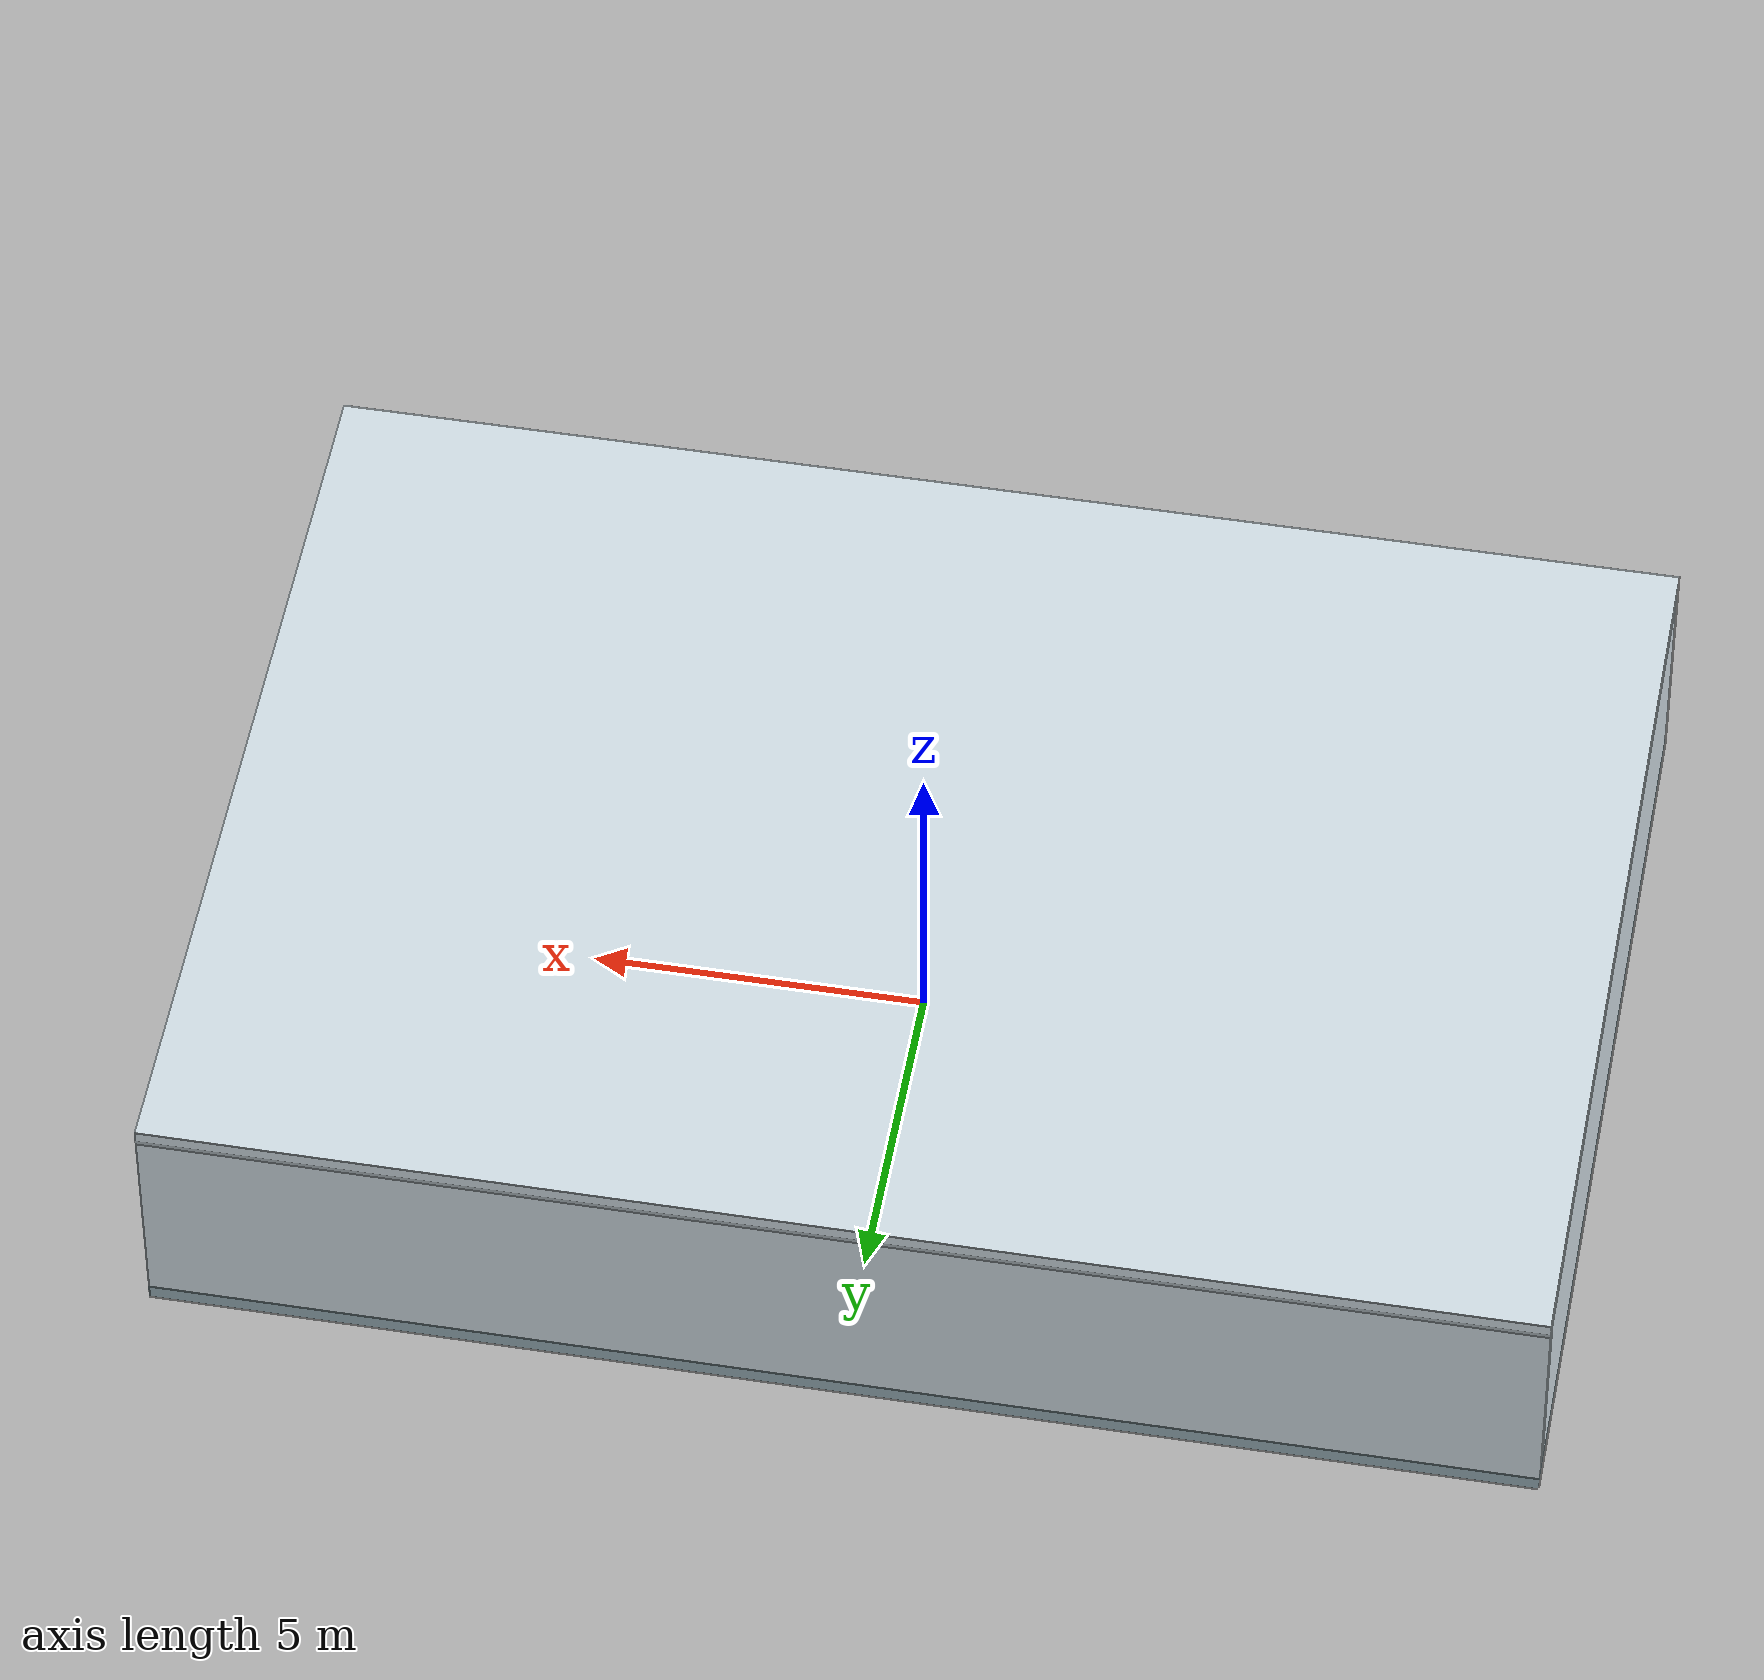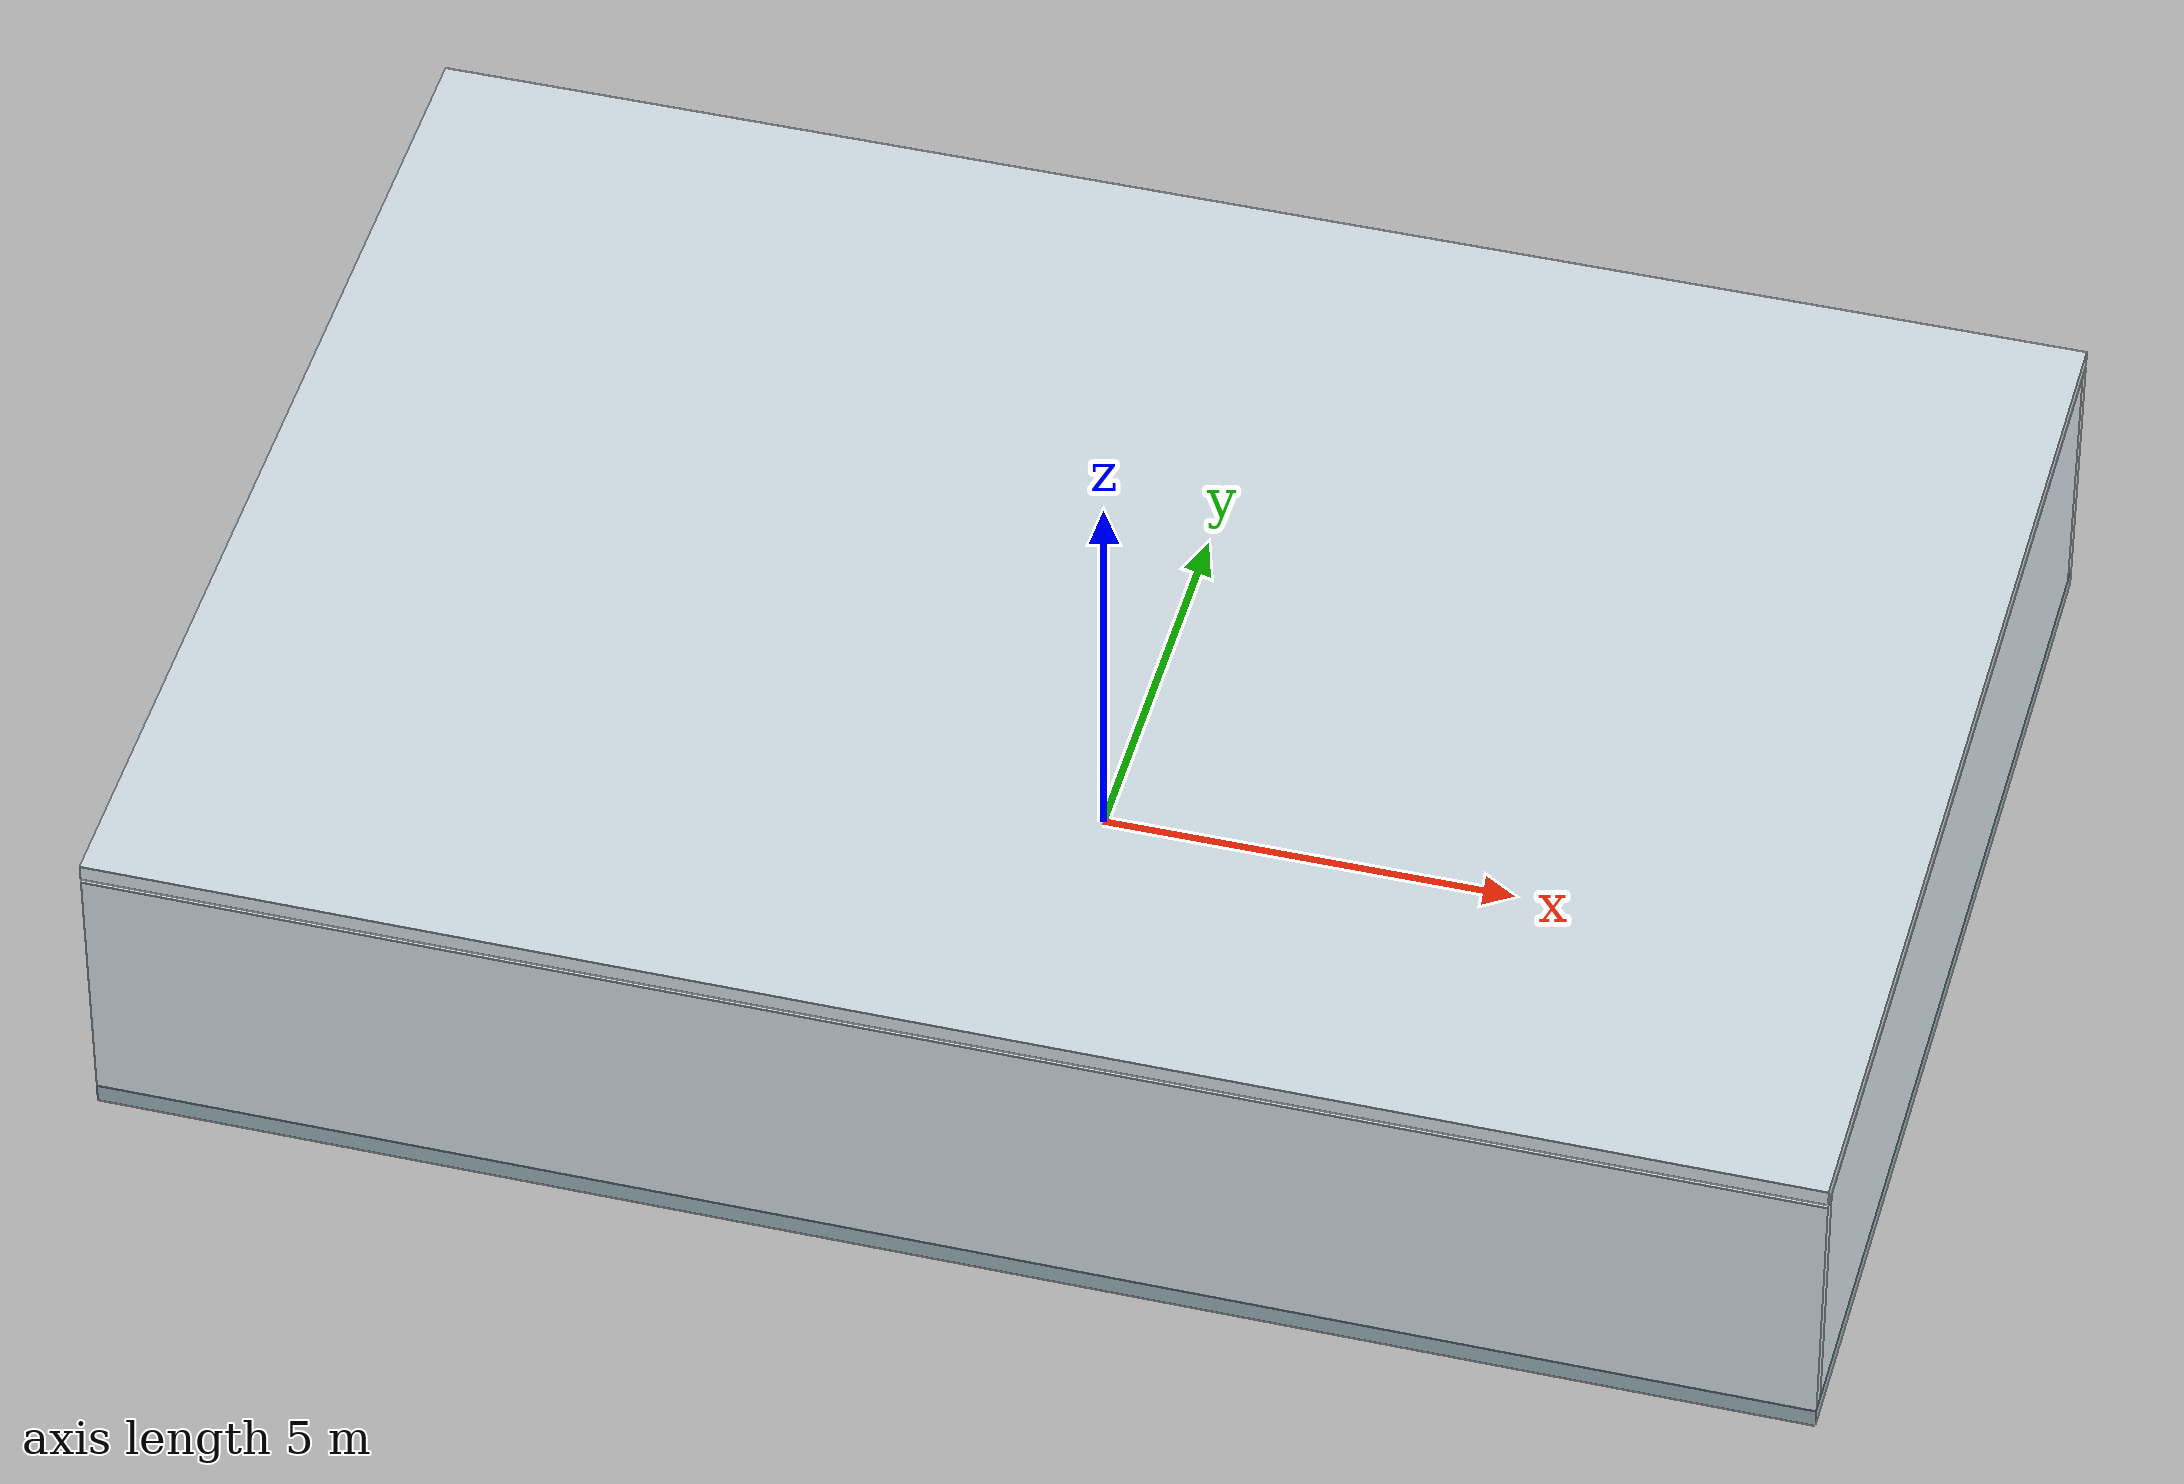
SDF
<?xml version='1.0' encoding='utf-8'?>
<sdf version="1.6">
  <world name="cleanroom">
    <gravity>0 0 -9.81</gravity>
    <physics name="ode" type="ode">
      <max_step_size>0.001</max_step_size>
      <real_time_update_rate>1000</real_time_update_rate>
    </physics>
    <scene>
      <ambient>0.7 0.7 0.7 1</ambient>
      <background>0.08 0.12 0.17 1</background>
      <shadows>false</shadows>
    </scene>
    <light name="room_light" type="directional">
      <pose>0 0 8 0 0 0</pose>
      <diffuse>0.9 0.9 0.9 1</diffuse>
      <direction>0.2 0.1 -1</direction>
    </light>
    <gui fullscreen="0">
      <camera name="overview">
        <pose>19 -24 23 0 0.63 2.23</pose>
      </camera>
    </gui>
    <plugin name="gazebo_ros_state" filename="libgazebo_ros_state.so">
      <ros>
        <namespace>/gazebo</namespace>
      </ros>
      <update_rate>20</update_rate>
    </plugin>
    <model name="raised_floor">
      <static>true</static>
      <link name="body">
        <collision name="walkable_surface">
          <pose>0 0 -0.12 0 0 0</pose>
          <geometry>
            <box>
              <size>20.4 14.4 0.24</size>
            </box>
          </geometry>
        </collision>
        <visual name="walkable_surface">
          <pose>0 0 -0.12 0 0 0</pose>
          <geometry>
            <box>
              <size>20.4 14.4 0.24</size>
            </box>
          </geometry>
          <material>
            <ambient>0.62 0.72 0.75 1</ambient>
            <diffuse>0.62 0.72 0.75 1</diffuse>
          </material>
          <transparency>0</transparency>
          <cast_shadows>false</cast_shadows>
        </visual>
        <visual name="tile_0_0">
          <pose>-9.5 -6.5 0.002 0 0 0</pose>
          <geometry>
            <box>
              <size>0.975 0.975 0.003</size>
            </box>
          </geometry>
          <material>
            <ambient>0.77 0.83 0.84 1</ambient>
            <diffuse>0.77 0.83 0.84 1</diffuse>
          </material>
          <transparency>0</transparency>
          <cast_shadows>false</cast_shadows>
        </visual>
        <visual name="grille_0_0_0">
          <pose>-9.5 -6.8 0.004 0 0 0</pose>
          <geometry>
            <box>
              <size>0.68 0.022 0.002</size>
            </box>
          </geometry>
          <material>
            <ambient>0.57 0.66 0.7 1</ambient>
            <diffuse>0.57 0.66 0.7 1</diffuse>
          </material>
          <transparency>0</transparency>
          <cast_shadows>false</cast_shadows>
        </visual>
        <visual name="grille_0_0_1">
          <pose>-9.5 -6.6 0.004 0 0 0</pose>
          <geometry>
            <box>
              <size>0.68 0.022 0.002</size>
            </box>
          </geometry>
          <material>
            <ambient>0.57 0.66 0.7 1</ambient>
            <diffuse>0.57 0.66 0.7 1</diffuse>
          </material>
          <transparency>0</transparency>
          <cast_shadows>false</cast_shadows>
        </visual>
        <visual name="grille_0_0_2">
          <pose>-9.5 -6.3999999999999995 0.004 0 0 0</pose>
          <geometry>
            <box>
              <size>0.68 0.022 0.002</size>
            </box>
          </geometry>
          <material>
            <ambient>0.57 0.66 0.7 1</ambient>
            <diffuse>0.57 0.66 0.7 1</diffuse>
          </material>
          <transparency>0</transparency>
          <cast_shadows>false</cast_shadows>
        </visual>
        <visual name="grille_0_0_3">
          <pose>-9.5 -6.199999999999999 0.004 0 0 0</pose>
          <geometry>
            <box>
              <size>0.68 0.022 0.002</size>
            </box>
          </geometry>
          <material>
            <ambient>0.57 0.66 0.7 1</ambient>
            <diffuse>0.57 0.66 0.7 1</diffuse>
          </material>
          <transparency>0</transparency>
          <cast_shadows>false</cast_shadows>
        </visual>
        <visual name="tile_0_1">
          <pose>-9.5 -5.5 0.002 0 0 0</pose>
          <geometry>
            <box>
              <size>0.975 0.975 0.003</size>
            </box>
          </geometry>
          <material>
            <ambient>0.77 0.83 0.84 1</ambient>
            <diffuse>0.77 0.83 0.84 1</diffuse>
          </material>
          <transparency>0</transparency>
          <cast_shadows>false</cast_shadows>
        </visual>
        <visual name="grille_0_1_0">
          <pose>-9.5 -5.8 0.004 0 0 0</pose>
          <geometry>
            <box>
              <size>0.68 0.022 0.002</size>
            </box>
          </geometry>
          <material>
            <ambient>0.57 0.66 0.7 1</ambient>
            <diffuse>0.57 0.66 0.7 1</diffuse>
          </material>
          <transparency>0</transparency>
          <cast_shadows>false</cast_shadows>
        </visual>
        <visual name="grille_0_1_1">
          <pose>-9.5 -5.6 0.004 0 0 0</pose>
          <geometry>
            <box>
              <size>0.68 0.022 0.002</size>
            </box>
          </geometry>
          <material>
            <ambient>0.57 0.66 0.7 1</ambient>
            <diffuse>0.57 0.66 0.7 1</diffuse>
          </material>
          <transparency>0</transparency>
          <cast_shadows>false</cast_shadows>
        </visual>
        <visual name="grille_0_1_2">
          <pose>-9.5 -5.3999999999999995 0.004 0 0 0</pose>
          <geometry>
            <box>
              <size>0.68 0.022 0.002</size>
            </box>
          </geometry>
          <material>
            <ambient>0.57 0.66 0.7 1</ambient>
            <diffuse>0.57 0.66 0.7 1</diffuse>
          </material>
          <transparency>0</transparency>
          <cast_shadows>false</cast_shadows>
        </visual>
        <visual name="grille_0_1_3">
          <pose>-9.5 -5.199999999999999 0.004 0 0 0</pose>
          <geometry>
            <box>
              <size>0.68 0.022 0.002</size>
            </box>
          </geometry>
          <material>
            <ambient>0.57 0.66 0.7 1</ambient>
            <diffuse>0.57 0.66 0.7 1</diffuse>
          </material>
          <transparency>0</transparency>
          <cast_shadows>false</cast_shadows>
        </visual>
        <visual name="tile_0_2">
          <pose>-9.5 -4.5 0.002 0 0 0</pose>
          <geometry>
            <box>
              <size>0.975 0.975 0.003</size>
            </box>
          </geometry>
          <material>
            <ambient>0.77 0.83 0.84 1</ambient>
            <diffuse>0.77 0.83 0.84 1</diffuse>
          </material>
          <transparency>0</transparency>
          <cast_shadows>false</cast_shadows>
        </visual>
        <visual name="grille_0_2_0">
          <pose>-9.5 -4.8 0.004 0 0 0</pose>
          <geometry>
            <box>
              <size>0.68 0.022 0.002</size>
            </box>
          </geometry>
          <material>
            <ambient>0.57 0.66 0.7 1</ambient>
            <diffuse>0.57 0.66 0.7 1</diffuse>
          </material>
          <transparency>0</transparency>
          <cast_shadows>false</cast_shadows>
        </visual>
        <visual name="grille_0_2_1">
          <pose>-9.5 -4.6 0.004 0 0 0</pose>
          <geometry>
            <box>
              <size>0.68 0.022 0.002</size>
            </box>
          </geometry>
          <material>
            <ambient>0.57 0.66 0.7 1</ambient>
            <diffuse>0.57 0.66 0.7 1</diffuse>
          </material>
          <transparency>0</transparency>
          <cast_shadows>false</cast_shadows>
        </visual>
        <visual name="grille_0_2_2">
          <pose>-9.5 -4.3999999999999995 0.004 0 0 0</pose>
          <geometry>
            <box>
              <size>0.68 0.022 0.002</size>
            </box>
          </geometry>
          <material>
            <ambient>0.57 0.66 0.7 1</ambient>
            <diffuse>0.57 0.66 0.7 1</diffuse>
          </material>
          <transparency>0</transparency>
          <cast_shadows>false</cast_shadows>
        </visual>
        <visual name="grille_0_2_3">
          <pose>-9.5 -4.199999999999999 0.004 0 0 0</pose>
          <geometry>
            <box>
              <size>0.68 0.022 0.002</size>
            </box>
          </geometry>
          <material>
            <ambient>0.57 0.66 0.7 1</ambient>
            <diffuse>0.57 0.66 0.7 1</diffuse>
          </material>
          <transparency>0</transparency>
          <cast_shadows>false</cast_shadows>
        </visual>
        <visual name="tile_0_3">
          <pose>-9.5 -3.5 0.002 0 0 0</pose>
          <geometry>
            <box>
              <size>0.975 0.975 0.003</size>
            </box>
          </geometry>
          <material>
            <ambient>0.77 0.83 0.84 1</ambient>
            <diffuse>0.77 0.83 0.84 1</diffuse>
          </material>
          <transparency>0</transparency>
          <cast_shadows>false</cast_shadows>
        </visual>
        <visual name="grille_0_3_0">
          <pose>-9.5 -3.8 0.004 0 0 0</pose>
          <geometry>
            <box>
              <size>0.68 0.022 0.002</size>
            </box>
          </geometry>
          <material>
            <ambient>0.57 0.66 0.7 1</ambient>
            <diffuse>0.57 0.66 0.7 1</diffuse>
          </material>
          <transparency>0</transparency>
          <cast_shadows>false</cast_shadows>
        </visual>
        <visual name="grille_0_3_1">
          <pose>-9.5 -3.5999999999999996 0.004 0 0 0</pose>
          <geometry>
            <box>
              <size>0.68 0.022 0.002</size>
            </box>
          </geometry>
          <material>
            <ambient>0.57 0.66 0.7 1</ambient>
            <diffuse>0.57 0.66 0.7 1</diffuse>
          </material>
          <transparency>0</transparency>
          <cast_shadows>false</cast_shadows>
        </visual>
        <visual name="grille_0_3_2">
          <pose>-9.5 -3.4 0.004 0 0 0</pose>
          <geometry>
            <box>
              <size>0.68 0.022 0.002</size>
            </box>
          </geometry>
          <material>
            <ambient>0.57 0.66 0.7 1</ambient>
            <diffuse>0.57 0.66 0.7 1</diffuse>
          </material>
          <transparency>0</transparency>
          <cast_shadows>false</cast_shadows>
        </visual>
        <visual name="grille_0_3_3">
          <pose>-9.5 -3.1999999999999997 0.004 0 0 0</pose>
          <geometry>
            <box>
              <size>0.68 0.022 0.002</size>
            </box>
          </geometry>
          <material>
            <ambient>0.57 0.66 0.7 1</ambient>
            <diffuse>0.57 0.66 0.7 1</diffuse>
          </material>
          <transparency>0</transparency>
          <cast_shadows>false</cast_shadows>
        </visual>
        <visual name="tile_0_4">
          <pose>-9.5 -2.5 0.002 0 0 0</pose>
          <geometry>
            <box>
              <size>0.975 0.975 0.003</size>
            </box>
          </geometry>
          <material>
            <ambient>0.77 0.83 0.84 1</ambient>
            <diffuse>0.77 0.83 0.84 1</diffuse>
          </material>
          <transparency>0</transparency>
          <cast_shadows>false</cast_shadows>
        </visual>
        <visual name="grille_0_4_0">
          <pose>-9.5 -2.8 0.004 0 0 0</pose>
          <geometry>
            <box>
              <size>0.68 0.022 0.002</size>
            </box>
          </geometry>
          <material>
            <ambient>0.57 0.66 0.7 1</ambient>
            <diffuse>0.57 0.66 0.7 1</diffuse>
          </material>
          <transparency>0</transparency>
          <cast_shadows>false</cast_shadows>
        </visual>
        <visual name="grille_0_4_1">
          <pose>-9.5 -2.5999999999999996 0.004 0 0 0</pose>
          <geometry>
            <box>
              <size>0.68 0.022 0.002</size>
            </box>
          </geometry>
          <material>
            <ambient>0.57 0.66 0.7 1</ambient>
            <diffuse>0.57 0.66 0.7 1</diffuse>
          </material>
          <transparency>0</transparency>
          <cast_shadows>false</cast_shadows>
        </visual>
        <visual name="grille_0_4_2">
          <pose>-9.5 -2.4 0.004 0 0 0</pose>
          <geometry>
            <box>
              <size>0.68 0.022 0.002</size>
            </box>
          </geometry>
          <material>
            <ambient>0.57 0.66 0.7 1</ambient>
            <diffuse>0.57 0.66 0.7 1</diffuse>
          </material>
          <transparency>0</transparency>
          <cast_shadows>false</cast_shadows>
        </visual>
        <visual name="grille_0_4_3">
          <pose>-9.5 -2.1999999999999997 0.004 0 0 0</pose>
          <geometry>
            <box>
              <size>0.68 0.022 0.002</size>
            </box>
          </geometry>
          <material>
            <ambient>0.57 0.66 0.7 1</ambient>
            <diffuse>0.57 0.66 0.7 1</diffuse>
          </material>
          <transparency>0</transparency>
          <cast_shadows>false</cast_shadows>
        </visual>
        <visual name="tile_0_5">
          <pose>-9.5 -1.5 0.002 0 0 0</pose>
          <geometry>
            <box>
              <size>0.975 0.975 0.003</size>
            </box>
          </geometry>
          <material>
            <ambient>0.77 0.83 0.84 1</ambient>
            <diffuse>0.77 0.83 0.84 1</diffuse>
          </material>
          <transparency>0</transparency>
          <cast_shadows>false</cast_shadows>
        </visual>
        <visual name="grille_0_5_0">
          <pose>-9.5 -1.8 0.004 0 0 0</pose>
          <geometry>
            <box>
              <size>0.68 0.022 0.002</size>
            </box>
          </geometry>
          <material>
            <ambient>0.57 0.66 0.7 1</ambient>
            <diffuse>0.57 0.66 0.7 1</diffuse>
          </material>
          <transparency>0</transparency>
          <cast_shadows>false</cast_shadows>
        </visual>
        <visual name="grille_0_5_1">
          <pose>-9.5 -1.6 0.004 0 0 0</pose>
          <geometry>
            <box>
              <size>0.68 0.022 0.002</size>
            </box>
          </geometry>
          <material>
            <ambient>0.57 0.66 0.7 1</ambient>
            <diffuse>0.57 0.66 0.7 1</diffuse>
          </material>
          <transparency>0</transparency>
          <cast_shadows>false</cast_shadows>
        </visual>
        <visual name="grille_0_5_2">
          <pose>-9.5 -1.4 0.004 0 0 0</pose>
          <geometry>
            <box>
              <size>0.68 0.022 0.002</size>
            </box>
          </geometry>
          <material>
            <ambient>0.57 0.66 0.7 1</ambient>
            <diffuse>0.57 0.66 0.7 1</diffuse>
          </material>
          <transparency>0</transparency>
          <cast_shadows>false</cast_shadows>
        </visual>
        <visual name="grille_0_5_3">
          <pose>-9.5 -1.2 0.004 0 0 0</pose>
          <geometry>
            <box>
              <size>0.68 0.022 0.002</size>
            </box>
          </geometry>
          <material>
            <ambient>0.57 0.66 0.7 1</ambient>
            <diffuse>0.57 0.66 0.7 1</diffuse>
          </material>
          <transparency>0</transparency>
          <cast_shadows>false</cast_shadows>
        </visual>
        <visual name="tile_0_6">
          <pose>-9.5 -0.5 0.002 0 0 0</pose>
          <geometry>
            <box>
              <size>0.975 0.975 0.003</size>
            </box>
          </geometry>
          <material>
            <ambient>0.77 0.83 0.84 1</ambient>
            <diffuse>0.77 0.83 0.84 1</diffuse>
          </material>
          <transparency>0</transparency>
          <cast_shadows>false</cast_shadows>
        </visual>
        <visual name="grille_0_6_0">
          <pose>-9.5 -0.8 0.004 0 0 0</pose>
          <geometry>
            <box>
              <size>0.68 0.022 0.002</size>
            </box>
          </geometry>
          <material>
            <ambient>0.57 0.66 0.7 1</ambient>
            <diffuse>0.57 0.66 0.7 1</diffuse>
          </material>
          <transparency>0</transparency>
          <cast_shadows>false</cast_shadows>
        </visual>
        <visual name="grille_0_6_1">
          <pose>-9.5 -0.6000000000000001 0.004 0 0 0</pose>
          <geometry>
            <box>
              <size>0.68 0.022 0.002</size>
            </box>
          </geometry>
          <material>
            <ambient>0.57 0.66 0.7 1</ambient>
            <diffuse>0.57 0.66 0.7 1</diffuse>
          </material>
          <transparency>0</transparency>
          <cast_shadows>false</cast_shadows>
        </visual>
        <visual name="grille_0_6_2">
          <pose>-9.5 -0.4 0.004 0 0 0</pose>
          <geometry>
            <box>
              <size>0.68 0.022 0.002</size>
            </box>
          </geometry>
          <material>
            <ambient>0.57 0.66 0.7 1</ambient>
            <diffuse>0.57 0.66 0.7 1</diffuse>
          </material>
          <transparency>0</transparency>
          <cast_shadows>false</cast_shadows>
        </visual>
        <visual name="grille_0_6_3">
          <pose>-9.5 -0.19999999999999996 0.004 0 0 0</pose>
          <geometry>
            <box>
              <size>0.68 0.022 0.002</size>
            </box>
          </geometry>
          <material>
            <ambient>0.57 0.66 0.7 1</ambient>
            <diffuse>0.57 0.66 0.7 1</diffuse>
          </material>
          <transparency>0</transparency>
          <cast_shadows>false</cast_shadows>
        </visual>
        <visual name="tile_0_7">
          <pose>-9.5 0.5 0.002 0 0 0</pose>
          <geometry>
            <box>
              <size>0.975 0.975 0.003</size>
            </box>
          </geometry>
          <material>
            <ambient>0.77 0.83 0.84 1</ambient>
            <diffuse>0.77 0.83 0.84 1</diffuse>
          </material>
          <transparency>0</transparency>
          <cast_shadows>false</cast_shadows>
        </visual>
        <visual name="grille_0_7_0">
          <pose>-9.5 0.2 0.004 0 0 0</pose>
          <geometry>
            <box>
              <size>0.68 0.022 0.002</size>
            </box>
          </geometry>
          <material>
            <ambient>0.57 0.66 0.7 1</ambient>
            <diffuse>0.57 0.66 0.7 1</diffuse>
          </material>
          <transparency>0</transparency>
          <cast_shadows>false</cast_shadows>
        </visual>
        <visual name="grille_0_7_1">
          <pose>-9.5 0.4 0.004 0 0 0</pose>
          <geometry>
            <box>
              <size>0.68 0.022 0.002</size>
            </box>
          </geometry>
          <material>
            <ambient>0.57 0.66 0.7 1</ambient>
            <diffuse>0.57 0.66 0.7 1</diffuse>
          </material>
          <transparency>0</transparency>
          <cast_shadows>false</cast_shadows>
        </visual>
        <visual name="grille_0_7_2">
          <pose>-9.5 0.6000000000000001 0.004 0 0 0</pose>
          <geometry>
            <box>
              <size>0.68 0.022 0.002</size>
            </box>
          </geometry>
          <material>
            <ambient>0.57 0.66 0.7 1</ambient>
            <diffuse>0.57 0.66 0.7 1</diffuse>
          </material>
          <transparency>0</transparency>
          <cast_shadows>false</cast_shadows>
        </visual>
        <visual name="grille_0_7_3">
          <pose>-9.5 0.8 0.004 0 0 0</pose>
          <geometry>
            <box>
              <size>0.68 0.022 0.002</size>
            </box>
          </geometry>
          <material>
            <ambient>0.57 0.66 0.7 1</ambient>
            <diffuse>0.57 0.66 0.7 1</diffuse>
          </material>
          <transparency>0</transparency>
          <cast_shadows>false</cast_shadows>
        </visual>
        <visual name="tile_0_8">
          <pose>-9.5 1.5 0.002 0 0 0</pose>
          <geometry>
            <box>
              <size>0.975 0.975 0.003</size>
            </box>
          </geometry>
          <material>
            <ambient>0.77 0.83 0.84 1</ambient>
            <diffuse>0.77 0.83 0.84 1</diffuse>
          </material>
          <transparency>0</transparency>
          <cast_shadows>false</cast_shadows>
        </visual>
        <visual name="grille_0_8_0">
          <pose>-9.5 1.2 0.004 0 0 0</pose>
          <geometry>
            <box>
              <size>0.68 0.022 0.002</size>
            </box>
          </geometry>
          <material>
            <ambient>0.57 0.66 0.7 1</ambient>
            <diffuse>0.57 0.66 0.7 1</diffuse>
          </material>
          <transparency>0</transparency>
          <cast_shadows>false</cast_shadows>
        </visual>
        <visual name="grille_0_8_1">
          <pose>-9.5 1.4 0.004 0 0 0</pose>
          <geometry>
            <box>
              <size>0.68 0.022 0.002</size>
            </box>
          </geometry>
          <material>
            <ambient>0.57 0.66 0.7 1</ambient>
            <diffuse>0.57 0.66 0.7 1</diffuse>
          </material>
          <transparency>0</transparency>
          <cast_shadows>false</cast_shadows>
        </visual>
        <visual name="grille_0_8_2">
          <pose>-9.5 1.6 0.004 0 0 0</pose>
          <geometry>
            <box>
              <size>0.68 0.022 0.002</size>
            </box>
          </geometry>
          <material>
            <ambient>0.57 0.66 0.7 1</ambient>
            <diffuse>0.57 0.66 0.7 1</diffuse>
          </material>
          <transparency>0</transparency>
          <cast_shadows>false</cast_shadows>
        </visual>
        <visual name="grille_0_8_3">
          <pose>-9.5 1.8 0.004 0 0 0</pose>
          <geometry>
            <box>
              <size>0.68 0.022 0.002</size>
            </box>
          </geometry>
          <material>
            <ambient>0.57 0.66 0.7 1</ambient>
            <diffuse>0.57 0.66 0.7 1</diffuse>
          </material>
          <transparency>0</transparency>
          <cast_shadows>false</cast_shadows>
        </visual>
        <visual name="tile_0_9">
          <pose>-9.5 2.5 0.002 0 0 0</pose>
          <geometry>
            <box>
              <size>0.975 0.975 0.003</size>
            </box>
          </geometry>
          <material>
            <ambient>0.77 0.83 0.84 1</ambient>
            <diffuse>0.77 0.83 0.84 1</diffuse>
          </material>
          <transparency>0</transparency>
          <cast_shadows>false</cast_shadows>
        </visual>
        <visual name="grille_0_9_0">
          <pose>-9.5 2.2 0.004 0 0 0</pose>
          <geometry>
            <box>
              <size>0.68 0.022 0.002</size>
            </box>
          </geometry>
          <material>
            <ambient>0.57 0.66 0.7 1</ambient>
            <diffuse>0.57 0.66 0.7 1</diffuse>
          </material>
          <transparency>0</transparency>
          <cast_shadows>false</cast_shadows>
        </visual>
        <visual name="grille_0_9_1">
          <pose>-9.5 2.4000000000000004 0.004 0 0 0</pose>
          <geometry>
            <box>
              <size>0.68 0.022 0.002</size>
            </box>
          </geometry>
          <material>
            <ambient>0.57 0.66 0.7 1</ambient>
            <diffuse>0.57 0.66 0.7 1</diffuse>
          </material>
          <transparency>0</transparency>
          <cast_shadows>false</cast_shadows>
        </visual>
        <visual name="grille_0_9_2">
          <pose>-9.5 2.6 0.004 0 0 0</pose>
          <geometry>
            <box>
              <size>0.68 0.022 0.002</size>
            </box>
          </geometry>
          <material>
            <ambient>0.57 0.66 0.7 1</ambient>
            <diffuse>0.57 0.66 0.7 1</diffuse>
          </material>
          <transparency>0</transparency>
          <cast_shadows>false</cast_shadows>
        </visual>
        <visual name="grille_0_9_3">
          <pose>-9.5 2.8000000000000003 0.004 0 0 0</pose>
          <geometry>
            <box>
              <size>0.68 0.022 0.002</size>
            </box>
          </geometry>
          <material>
            <ambient>0.57 0.66 0.7 1</ambient>
            <diffuse>0.57 0.66 0.7 1</diffuse>
          </material>
          <transparency>0</transparency>
          <cast_shadows>false</cast_shadows>
        </visual>
        <visual name="tile_0_10">
          <pose>-9.5 3.5 0.002 0 0 0</pose>
          <geometry>
            <box>
              <size>0.975 0.975 0.003</size>
            </box>
          </geometry>
          <material>
            <ambient>0.77 0.83 0.84 1</ambient>
            <diffuse>0.77 0.83 0.84 1</diffuse>
          </material>
          <transparency>0</transparency>
          <cast_shadows>false</cast_shadows>
        </visual>
        <visual name="grille_0_10_0">
          <pose>-9.5 3.2 0.004 0 0 0</pose>
          <geometry>
            <box>
              <size>0.68 0.022 0.002</size>
            </box>
          </geometry>
          <material>
            <ambient>0.57 0.66 0.7 1</ambient>
            <diffuse>0.57 0.66 0.7 1</diffuse>
          </material>
          <transparency>0</transparency>
          <cast_shadows>false</cast_shadows>
        </visual>
        <visual name="grille_0_10_1">
          <pose>-9.5 3.4000000000000004 0.004 0 0 0</pose>
          <geometry>
            <box>
              <size>0.68 0.022 0.002</size>
            </box>
          </geometry>
          <material>
            <ambient>0.57 0.66 0.7 1</ambient>
            <diffuse>0.57 0.66 0.7 1</diffuse>
          </material>
          <transparency>0</transparency>
          <cast_shadows>false</cast_shadows>
        </visual>
        <visual name="grille_0_10_2">
          <pose>-9.5 3.6 0.004 0 0 0</pose>
          <geometry>
            <box>
              <size>0.68 0.022 0.002</size>
            </box>
          </geometry>
          <material>
            <ambient>0.57 0.66 0.7 1</ambient>
            <diffuse>0.57 0.66 0.7 1</diffuse>
          </material>
          <transparency>0</transparency>
          <cast_shadows>false</cast_shadows>
        </visual>
        <visual name="grille_0_10_3">
          <pose>-9.5 3.8000000000000003 0.004 0 0 0</pose>
          <geometry>
            <box>
              <size>0.68 0.022 0.002</size>
            </box>
          </geometry>
          <material>
            <ambient>0.57 0.66 0.7 1</ambient>
            <diffuse>0.57 0.66 0.7 1</diffuse>
          </material>
          <transparency>0</transparency>
          <cast_shadows>false</cast_shadows>
        </visual>
        <visual name="tile_0_11">
          <pose>-9.5 4.5 0.002 0 0 0</pose>
          <geometry>
            <box>
              <size>0.975 0.975 0.003</size>
            </box>
          </geometry>
          <material>
            <ambient>0.77 0.83 0.84 1</ambient>
            <diffuse>0.77 0.83 0.84 1</diffuse>
          </material>
          <transparency>0</transparency>
          <cast_shadows>false</cast_shadows>
        </visual>
        <visual name="grille_0_11_0">
          <pose>-9.5 4.2 0.004 0 0 0</pose>
          <geometry>
            <box>
              <size>0.68 0.022 0.002</size>
            </box>
          </geometry>
          <material>
            <ambient>0.57 0.66 0.7 1</ambient>
            <diffuse>0.57 0.66 0.7 1</diffuse>
          </material>
          <transparency>0</transparency>
          <cast_shadows>false</cast_shadows>
        </visual>
        <visual name="grille_0_11_1">
          <pose>-9.5 4.4 0.004 0 0 0</pose>
          <geometry>
            <box>
              <size>0.68 0.022 0.002</size>
            </box>
          </geometry>
          <material>
            <ambient>0.57 0.66 0.7 1</ambient>
            <diffuse>0.57 0.66 0.7 1</diffuse>
          </material>
          <transparency>0</transparency>
          <cast_shadows>false</cast_shadows>
        </visual>
        <visual name="grille_0_11_2">
          <pose>-9.5 4.6000000000000005 0.004 0 0 0</pose>
          <geometry>
            <box>
              <size>0.68 0.022 0.002</size>
            </box>
          </geometry>
          <material>
            <ambient>0.57 0.66 0.7 1</ambient>
            <diffuse>0.57 0.66 0.7 1</diffuse>
          </material>
          <transparency>0</transparency>
          <cast_shadows>false</cast_shadows>
        </visual>
        <visual name="grille_0_11_3">
          <pose>-9.5 4.800000000000001 0.004 0 0 0</pose>
          <geometry>
            <box>
              <size>0.68 0.022 0.002</size>
            </box>
          </geometry>
          <material>
            <ambient>0.57 0.66 0.7 1</ambient>
            <diffuse>0.57 0.66 0.7 1</diffuse>
          </material>
          <transparency>0</transparency>
          <cast_shadows>false</cast_shadows>
        </visual>
        <visual name="tile_0_12">
          <pose>-9.5 5.5 0.002 0 0 0</pose>
          <geometry>
            <box>
              <size>0.975 0.975 0.003</size>
            </box>
          </geometry>
          <material>
            <ambient>0.77 0.83 0.84 1</ambient>
            <diffuse>0.77 0.83 0.84 1</diffuse>
          </material>
          <transparency>0</transparency>
          <cast_shadows>false</cast_shadows>
        </visual>
        <visual name="grille_0_12_0">
          <pose>-9.5 5.2 0.004 0 0 0</pose>
          <geometry>
            <box>
              <size>0.68 0.022 0.002</size>
            </box>
          </geometry>
          <material>
            <ambient>0.57 0.66 0.7 1</ambient>
            <diffuse>0.57 0.66 0.7 1</diffuse>
          </material>
          <transparency>0</transparency>
          <cast_shadows>false</cast_shadows>
        </visual>
        <visual name="grille_0_12_1">
          <pose>-9.5 5.4 0.004 0 0 0</pose>
          <geometry>
            <box>
              <size>0.68 0.022 0.002</size>
            </box>
          </geometry>
          <material>
            <ambient>0.57 0.66 0.7 1</ambient>
            <diffuse>0.57 0.66 0.7 1</diffuse>
          </material>
          <transparency>0</transparency>
          <cast_shadows>false</cast_shadows>
        </visual>
        <visual name="grille_0_12_2">
          <pose>-9.5 5.6000000000000005 0.004 0 0 0</pose>
          <geometry>
            <box>
              <size>0.68 0.022 0.002</size>
            </box>
          </geometry>
          <material>
            <ambient>0.57 0.66 0.7 1</ambient>
            <diffuse>0.57 0.66 0.7 1</diffuse>
          </material>
          <transparency>0</transparency>
          <cast_shadows>false</cast_shadows>
        </visual>
        <visual name="grille_0_12_3">
          <pose>-9.5 5.800000000000001 0.004 0 0 0</pose>
          <geometry>
            <box>
              <size>0.68 0.022 0.002</size>
            </box>
          </geometry>
          <material>
            <ambient>0.57 0.66 0.7 1</ambient>
            <diffuse>0.57 0.66 0.7 1</diffuse>
          </material>
          <transparency>0</transparency>
          <cast_shadows>false</cast_shadows>
        </visual>
        <visual name="tile_0_13">
          <pose>-9.5 6.5 0.002 0 0 0</pose>
          <geometry>
            <box>
              <size>0.975 0.975 0.003</size>
            </box>
          </geometry>
          <material>
            <ambient>0.77 0.83 0.84 1</ambient>
            <diffuse>0.77 0.83 0.84 1</diffuse>
          </material>
          <transparency>0</transparency>
          <cast_shadows>false</cast_shadows>
        </visual>
        <visual name="grille_0_13_0">
          <pose>-9.5 6.2 0.004 0 0 0</pose>
          <geometry>
            <box>
              <size>0.68 0.022 0.002</size>
            </box>
          </geometry>
          <material>
            <ambient>0.57 0.66 0.7 1</ambient>
            <diffuse>0.57 0.66 0.7 1</diffuse>
          </material>
          <transparency>0</transparency>
          <cast_shadows>false</cast_shadows>
        </visual>
        <visual name="grille_0_13_1">
          <pose>-9.5 6.4 0.004 0 0 0</pose>
          <geometry>
            <box>
              <size>0.68 0.022 0.002</size>
            </box>
          </geometry>
          <material>
            <ambient>0.57 0.66 0.7 1</ambient>
            <diffuse>0.57 0.66 0.7 1</diffuse>
          </material>
          <transparency>0</transparency>
          <cast_shadows>false</cast_shadows>
        </visual>
        <visual name="grille_0_13_2">
          <pose>-9.5 6.6000000000000005 0.004 0 0 0</pose>
          <geometry>
            <box>
              <size>0.68 0.022 0.002</size>
            </box>
          </geometry>
          <material>
            <ambient>0.57 0.66 0.7 1</ambient>
            <diffuse>0.57 0.66 0.7 1</diffuse>
          </material>
          <transparency>0</transparency>
          <cast_shadows>false</cast_shadows>
        </visual>
        <visual name="grille_0_13_3">
          <pose>-9.5 6.800000000000001 0.004 0 0 0</pose>
          <geometry>
            <box>
              <size>0.68 0.022 0.002</size>
            </box>
          </geometry>
          <material>
            <ambient>0.57 0.66 0.7 1</ambient>
            <diffuse>0.57 0.66 0.7 1</diffuse>
          </material>
          <transparency>0</transparency>
          <cast_shadows>false</cast_shadows>
        </visual>
        <visual name="tile_1_0">
          <pose>-8.5 -6.5 0.002 0 0 0</pose>
          <geometry>
            <box>
              <size>0.975 0.975 0.003</size>
            </box>
          </geometry>
          <material>
            <ambient>0.77 0.83 0.84 1</ambient>
            <diffuse>0.77 0.83 0.84 1</diffuse>
          </material>
          <transparency>0</transparency>
          <cast_shadows>false</cast_shadows>
        </visual>
        <visual name="grille_1_0_0">
          <pose>-8.5 -6.8 0.004 0 0 0</pose>
          <geometry>
            <box>
              <size>0.68 0.022 0.002</size>
            </box>
          </geometry>
          <material>
            <ambient>0.57 0.66 0.7 1</ambient>
            <diffuse>0.57 0.66 0.7 1</diffuse>
          </material>
          <transparency>0</transparency>
          <cast_shadows>false</cast_shadows>
        </visual>
        <visual name="grille_1_0_1">
          <pose>-8.5 -6.6 0.004 0 0 0</pose>
          <geometry>
            <box>
              <size>0.68 0.022 0.002</size>
            </box>
          </geometry>
          <material>
            <ambient>0.57 0.66 0.7 1</ambient>
            <diffuse>0.57 0.66 0.7 1</diffuse>
          </material>
          <transparency>0</transparency>
          <cast_shadows>false</cast_shadows>
        </visual>
        <visual name="grille_1_0_2">
          <pose>-8.5 -6.3999999999999995 0.004 0 0 0</pose>
          <geometry>
            <box>
              <size>0.68 0.022 0.002</size>
            </box>
          </geometry>
          <material>
            <ambient>0.57 0.66 0.7 1</ambient>
            <diffuse>0.57 0.66 0.7 1</diffuse>
          </material>
          <transparency>0</transparency>
          <cast_shadows>false</cast_shadows>
        </visual>
        <visual name="grille_1_0_3">
          <pose>-8.5 -6.199999999999999 0.004 0 0 0</pose>
          <geometry>
            <box>
              <size>0.68 0.022 0.002</size>
            </box>
          </geometry>
          <material>
            <ambient>0.57 0.66 0.7 1</ambient>
            <diffuse>0.57 0.66 0.7 1</diffuse>
          </material>
          <transparency>0</transparency>
          <cast_shadows>false</cast_shadows>
        </visual>
        <visual name="tile_1_1">
          <pose>-8.5 -5.5 0.002 0 0 0</pose>
          <geometry>
            <box>
              <size>0.975 0.975 0.003</size>
            </box>
          </geometry>
          <material>
            <ambient>0.77 0.83 0.84 1</ambient>
            <diffuse>0.77 0.83 0.84 1</diffuse>
          </material>
          <transparency>0</transparency>
          <cast_shadows>false</cast_shadows>
        </visual>
        <visual name="grille_1_1_0">
          <pose>-8.5 -5.8 0.004 0 0 0</pose>
          <geometry>
            <box>
              <size>0.68 0.022 0.002</size>
            </box>
          </geometry>
          <material>
            <ambient>0.57 0.66 0.7 1</ambient>
            <diffuse>0.57 0.66 0.7 1</diffuse>
          </material>
          <transparency>0</transparency>
          <cast_shadows>false</cast_shadows>
        </visual>
        <visual name="grille_1_1_1">
          <pose>-8.5 -5.6 0.004 0 0 0</pose>
          <geometry>
            <box>
              <size>0.68 0.022 0.002</size>
            </box>
          </geometry>
          <material>
            <ambient>0.57 0.66 0.7 1</ambient>
            <diffuse>0.57 0.66 0.7 1</diffuse>
          </material>
          <transparency>0</transparency>
          <cast_shadows>false</cast_shadows>
        </visual>
        <visual name="grille_1_1_2">
          <pose>-8.5 -5.3999999999999995 0.004 0 0 0</pose>
          <geometry>
            <box>
              <size>0.68 0.022 0.002</size>
            </box>
          </geometry>
          <material>
            <ambient>0.57 0.66 0.7 1</ambient>
            <diffuse>0.57 0.66 0.7 1</diffuse>
          </material>
          <transparency>0</transparency>
          <cast_shadows>false</cast_shadows>
        </visual>
        <visual name="grille_1_1_3">
          <pose>-8.5 -5.199999999999999 0.004 0 0 0</pose>
          <geometry>
            <box>
              <size>0.68 0.022 0.002</size>
            </box>
          </geometry>
          <material>
            <ambient>0.57 0.66 0.7 1</ambient>
            <diffuse>0.57 0.66 0.7 1</diffuse>
          </material>
          <transparency>0</transparency>
          <cast_shadows>false</cast_shadows>
        </visual>
        <visual name="tile_1_2">
          <pose>-8.5 -4.5 0.002 0 0 0</pose>
          <geometry>
            <box>
              <size>0.975 0.975 0.003</size>
            </box>
          </geometry>
          <material>
            <ambient>0.77 0.83 0.84 1</ambient>
            <diffuse>0.77 0.83 0.84 1</diffuse>
          </material>
          <transparency>0</transparency>
          <cast_shadows>false</cast_shadows>
        </visual>
        <visual name="grille_1_2_0">
          <pose>-8.5 -4.8 0.004 0 0 0</pose>
          <geometry>
            <box>
              <size>0.68 0.022 0.002</size>
            </box>
          </geometry>
          <material>
            <ambient>0.57 0.66 0.7 1</ambient>
            <diffuse>0.57 0.66 0.7 1</diffuse>
          </material>
          <transparency>0</transparency>
          <cast_shadows>false</cast_shadows>
        </visual>
        <visual name="grille_1_2_1">
          <pose>-8.5 -4.6 0.004 0 0 0</pose>
          <geometry>
            <box>
              <size>0.68 0.022 0.002</size>
            </box>
          </geometry>
          <material>
            <ambient>0.57 0.66 0.7 1</ambient>
            <diffuse>0.57 0.66 0.7 1</diffuse>
          </material>
          <transparency>0</transparency>
          <cast_shadows>false</cast_shadows>
        </visual>
        <visual name="grille_1_2_2">
          <pose>-8.5 -4.3999999999999995 0.004 0 0 0</pose>
          <geometry>
            <box>
              <size>0.68 0.022 0.002</size>
            </box>
          </geometry>
          <material>
            <ambient>0.57 0.66 0.7 1</ambient>
            <diffuse>0.57 0.66 0.7 1</diffuse>
          </material>
          <transparency>0</transparency>
          <cast_shadows>false</cast_shadows>
        </visual>
        <visual name="grille_1_2_3">
          <pose>-8.5 -4.199999999999999 0.004 0 0 0</pose>
          <geometry>
            <box>
              <size>0.68 0.022 0.002</size>
            </box>
          </geometry>
          <material>
            <ambient>0.57 0.66 0.7 1</ambient>
            <diffuse>0.57 0.66 0.7 1</diffuse>
          </material>
          <transparency>0</transparency>
          <cast_shadows>false</cast_shadows>
        </visual>
        <visual name="tile_1_3">
          <pose>-8.5 -3.5 0.002 0 0 0</pose>
          <geometry>
            <box>
              <size>0.975 0.975 0.003</size>
            </box>
          </geometry>
          <material>
            <ambient>0.77 0.83 0.84 1</ambient>
            <diffuse>0.77 0.83 0.84 1</diffuse>
          </material>
          <transparency>0</transparency>
          <cast_shadows>false</cast_shadows>
        </visual>
        <visual name="grille_1_3_0">
          <pose>-8.5 -3.8 0.004 0 0 0</pose>
          <geometry>
            <box>
              <size>0.68 0.022 0.002</size>
            </box>
          </geometry>
          <material>
            <ambient>0.57 0.66 0.7 1</ambient>
            <diffuse>0.57 0.66 0.7 1</diffuse>
          </material>
          <transparency>0</transparency>
          <cast_shadows>false</cast_shadows>
        </visual>
        <visual name="grille_1_3_1">
          <pose>-8.5 -3.5999999999999996 0.004 0 0 0</pose>
          <geometry>
            <box>
              <size>0.68 0.022 0.002</size>
            </box>
          </geometry>
          <material>
            <ambient>0.57 0.66 0.7 1</ambient>
            <diffuse>0.57 0.66 0.7 1</diffuse>
          </material>
          <transparency>0</transparency>
          <cast_shadows>false</cast_shadows>
        </visual>
        <visual name="grille_1_3_2">
          <pose>-8.5 -3.4 0.004 0 0 0</pose>
          <geometry>
            <box>
              <size>0.68 0.022 0.002</size>
            </box>
          </geometry>
          <material>
            <ambient>0.57 0.66 0.7 1</ambient>
            <diffuse>0.57 0.66 0.7 1</diffuse>
          </material>
          <transparency>0</transparency>
          <cast_shadows>false</cast_shadows>
        </visual>
        <visual name="grille_1_3_3">
          <pose>-8.5 -3.1999999999999997 0.004 0 0 0</pose>
          <geometry>
            <box>
              <size>0.68 0.022 0.002</size>
            </box>
          </geometry>
          <material>
            <ambient>0.57 0.66 0.7 1</ambient>
            <diffuse>0.57 0.66 0.7 1</diffuse>
          </material>
          <transparency>0</transparency>
          <cast_shadows>false</cast_shadows>
        </visual>
        <visual name="tile_1_4">
          <pose>-8.5 -2.5 0.002 0 0 0</pose>
          <geometry>
            <box>
              <size>0.975 0.975 0.003</size>
            </box>
          </geometry>
          <material>
            <ambient>0.77 0.83 0.84 1</ambient>
            <diffuse>0.77 0.83 0.84 1</diffuse>
          </material>
          <transparency>0</transparency>
          <cast_shadows>false</cast_shadows>
        </visual>
        <visual name="grille_1_4_0">
          <pose>-8.5 -2.8 0.004 0 0 0</pose>
          <geometry>
            <box>
              <size>0.68 0.022 0.002</size>
            </box>
          </geometry>
          <material>
            <ambient>0.57 0.66 0.7 1</ambient>
            <diffuse>0.57 0.66 0.7 1</diffuse>
          </material>
          <transparency>0</transparency>
          <cast_shadows>false</cast_shadows>
        </visual>
        <visual name="grille_1_4_1">
          <pose>-8.5 -2.5999999999999996 0.004 0 0 0</pose>
          <geometry>
            <box>
              <size>0.68 0.022 0.002</size>
            </box>
          </geometry>
          <material>
            <ambient>0.57 0.66 0.7 1</ambient>
            <diffuse>0.57 0.66 0.7 1</diffuse>
          </material>
          <transparency>0</transparency>
          <cast_shadows>false</cast_shadows>
        </visual>
        <visual name="grille_1_4_2">
          <pose>-8.5 -2.4 0.004 0 0 0</pose>
          <geometry>
            <box>
              <size>0.68 0.022 0.002</size>
            </box>
          </geometry>
          <material>
            <ambient>0.57 0.66 0.7 1</ambient>
            <diffuse>0.57 0.66 0.7 1</diffuse>
          </material>
          <transparency>0</transparency>
          <cast_shadows>false</cast_shadows>
        </visual>
        <visual name="grille_1_4_3">
          <pose>-8.5 -2.1999999999999997 0.004 0 0 0</pose>
          <geometry>
            <box>
              <size>0.68 0.022 0.002</size>
            </box>
          </geometry>
          <material>
            <ambient>0.57 0.66 0.7 1</ambient>
            <diffuse>0.57 0.66 0.7 1</diffuse>
          </material>
          <transparency>0</transparency>
          <cast_shadows>false</cast_shadows>
        </visual>
        <visual name="tile_1_5">
          <pose>-8.5 -1.5 0.002 0 0 0</pose>
          <geometry>
            <box>
              <size>0.975 0.975 0.003</size>
            </box>
          </geometry>
          <material>
            <ambient>0.77 0.83 0.84 1</ambient>
            <diffuse>0.77 0.83 0.84 1</diffuse>
          </material>
          <transparency>0</transparency>
          <cast_shadows>false</cast_shadows>
        </visual>
        <visual name="grille_1_5_0">
          <pose>-8.5 -1.8 0.004 0 0 0</pose>
          <geometry>
            <box>
              <size>0.68 0.022 0.002</size>
            </box>
          </geometry>
          <material>
            <ambient>0.57 0.66 0.7 1</ambient>
            <diffuse>0.57 0.66 0.7 1</diffuse>
          </material>
          <transparency>0</transparency>
          <cast_shadows>false</cast_shadows>
        </visual>
        <visual name="grille_1_5_1">
          <pose>-8.5 -1.6 0.004 0 0 0</pose>
          <geometry>
            <box>
              <size>0.68 0.022 0.002</size>
            </box>
          </geometry>
          <material>
            <ambient>0.57 0.66 0.7 1</ambient>
            <diffuse>0.57 0.66 0.7 1</diffuse>
          </material>
          <transparency>0</transparency>
          <cast_shadows>false</cast_shadows>
        </visual>
        <visual name="grille_1_5_2">
          <pose>-8.5 -1.4 0.004 0 0 0</pose>
          <geometry>
            <box>
              <size>0.68 0.022 0.002</size>
            </box>
          </geometry>
          <material>
            <ambient>0.57 0.66 0.7 1</ambient>
            <diffuse>0.57 0.66 0.7 1</diffuse>
          </material>
          <transparency>0</transparency>
          <cast_shadows>false</cast_shadows>
        </visual>
        <visual name="grille_1_5_3">
          <pose>-8.5 -1.2 0.004 0 0 0</pose>
          <geometry>
            <box>
              <size>0.68 0.022 0.002</size>
            </box>
          </geometry>
          <material>
            <ambient>0.57 0.66 0.7 1</ambient>
            <diffuse>0.57 0.66 0.7 1</diffuse>
          </material>
          <transparency>0</transparency>
          <cast_shadows>false</cast_shadows>
        </visual>
        <visual name="tile_1_6">
          <pose>-8.5 -0.5 0.002 0 0 0</pose>
          <geometry>
            <box>
              <size>0.975 0.975 0.003</size>
            </box>
          </geometry>
          <material>
            <ambient>0.77 0.83 0.84 1</ambient>
            <diffuse>0.77 0.83 0.84 1</diffuse>
          </material>
          <transparency>0</transparency>
          <cast_shadows>false</cast_shadows>
        </visual>
        <visual name="grille_1_6_0">
          <pose>-8.5 -0.8 0.004 0 0 0</pose>
          <geometry>
            <box>
              <size>0.68 0.022 0.002</size>
            </box>
          </geometry>
          <material>
            <ambient>0.57 0.66 0.7 1</ambient>
            <diffuse>0.57 0.66 0.7 1</diffuse>
          </material>
          <transparency>0</transparency>
          <cast_shadows>false</cast_shadows>
        </visual>
        <visual name="grille_1_6_1">
          <pose>-8.5 -0.6000000000000001 0.004 0 0 0</pose>
          <geometry>
            <box>
              <size>0.68 0.022 0.002</size>
            </box>
          </geometry>
          <material>
            <ambient>0.57 0.66 0.7 1</ambient>
            <diffuse>0.57 0.66 0.7 1</diffuse>
          </material>
          <transparency>0</transparency>
          <cast_shadows>false</cast_shadows>
        </visual>
        <visual name="grille_1_6_2">
          <pose>-8.5 -0.4 0.004 0 0 0</pose>
          <geometry>
            <box>
              <size>0.68 0.022 0.002</size>
            </box>
          </geometry>
          <material>
            <ambient>0.57 0.66 0.7 1</ambient>
            <diffuse>0.57 0.66 0.7 1</diffuse>
          </material>
          <transparency>0</transparency>
          <cast_shadows>false</cast_shadows>
        </visual>
        <visual name="grille_1_6_3">
          <pose>-8.5 -0.19999999999999996 0.004 0 0 0</pose>
          <geometry>
            <box>
              <size>0.68 0.022 0.002</size>
            </box>
          </geometry>
          <material>
            <ambient>0.57 0.66 0.7 1</ambient>
            <diffuse>0.57 0.66 0.7 1</diffuse>
          </material>
          <transparency>0</transparency>
          <cast_shadows>false</cast_shadows>
        </visual>
        <visual name="tile_1_7">
          <pose>-8.5 0.5 0.002 0 0 0</pose>
          <geometry>
            <box>
              <size>0.975 0.975 0.003</size>
            </box>
          </geometry>
          <material>
            <ambient>0.77 0.83 0.84 1</ambient>
            <diffuse>0.77 0.83 0.84 1</diffuse>
          </material>
          <transparency>0</transparency>
          <cast_shadows>false</cast_shadows>
        </visual>
        <visual name="grille_1_7_0">
          <pose>-8.5 0.2 0.004 0 0 0</pose>
          <geometry>
            <box>
              <size>0.68 0.022 0.002</size>
            </box>
          </geometry>
          <material>
            <ambient>0.57 0.66 0.7 1</ambient>
            <diffuse>0.57 0.66 0.7 1</diffuse>
          </material>
          <transparency>0</transparency>
          <cast_shadows>false</cast_shadows>
        </visual>
        <visual name="grille_1_7_1">
          <pose>-8.5 0.4 0.004 0 0 0</pose>
          <geometry>
            <box>
              <size>0.68 0.022 0.002</size>
            </box>
          </geometry>
          <material>
            <ambient>0.57 0.66 0.7 1</ambient>
            <diffuse>0.57 0.66 0.7 1</diffuse>
          </material>
          <transparency>0</transparency>
          <cast_shadows>false</cast_shadows>
        </visual>
        <visual name="grille_1_7_2">
          <pose>-8.5 0.6000000000000001 0.004 0 0 0</pose>
          <geometry>
            <box>
              <size>0.68 0.022 0.002</size>
            </box>
          </geometry>
          <material>
            <ambient>0.57 0.66 0.7 1</ambient>
            <diffuse>0.57 0.66 0.7 1</diffuse>
          </material>
          <transparency>0</transparency>
          <cast_shadows>false</cast_shadows>
        </visual>
        <visual name="grille_1_7_3">
          <pose>-8.5 0.8 0.004 0 0 0</pose>
          <geometry>
            <box>
              <size>0.68 0.022 0.002</size>
            </box>
          </geometry>
          <material>
            <ambient>0.57 0.66 0.7 1</ambient>
            <diffuse>0.57 0.66 0.7 1</diffuse>
          </material>
          <transparency>0</transparency>
          <cast_shadows>false</cast_shadows>
        </visual>
        <visual name="tile_1_8">
          <pose>-8.5 1.5 0.002 0 0 0</pose>
          <geometry>
            <box>
              <size>0.975 0.975 0.003</size>
            </box>
          </geometry>
          <material>
            <ambient>0.77 0.83 0.84 1</ambient>
            <diffuse>0.77 0.83 0.84 1</diffuse>
          </material>
          <transparency>0</transparency>
          <cast_shadows>false</cast_shadows>
        </visual>
        <visual name="grille_1_8_0">
          <pose>-8.5 1.2 0.004 0 0 0</pose>
          <geometry>
            <box>
              <size>0.68 0.022 0.002</size>
            </box>
          </geometry>
          <material>
            <ambient>0.57 0.66 0.7 1</ambient>
            <diffuse>0.57 0.66 0.7 1</diffuse>
          </material>
          <transparency>0</transparency>
          <cast_shadows>false</cast_shadows>
        </visual>
        <visual name="grille_1_8_1">
          <pose>-8.5 1.4 0.004 0 0 0</pose>
          <geometry>
            <box>
              <size>0.68 0.022 0.002</size>
            </box>
          </geometry>
          <material>
            <ambient>0.57 0.66 0.7 1</ambient>
            <diffuse>0.57 0.66 0.7 1</diffuse>
          </material>
          <transparency>0</transparency>
          <cast_shadows>false</cast_shadows>
        </visual>
        <visual name="grille_1_8_2">
          <pose>-8.5 1.6 0.004 0 0 0</pose>
          <geometry>
            <box>
              <size>0.68 0.022 0.002</size>
            </box>
          </geometry>
          <material>
            <ambient>0.57 0.66 0.7 1</ambient>
            <diffuse>0.57 0.66 0.7 1</diffuse>
          </material>
          <transparency>0</transparency>
          <cast_shadows>false</cast_shadows>
        </visual>
        <visual name="grille_1_8_3">
          <pose>-8.5 1.8 0.004 0 0 0</pose>
          <geometry>
            <box>
              <size>0.68 0.022 0.002</size>
            </box>
          </geometry>
          <material>
            <ambient>0.57 0.66 0.7 1</ambient>
            <diffuse>0.57 0.66 0.7 1</diffuse>
          </material>
          <transparency>0</transparency>
          <cast_shadows>false</cast_shadows>
        </visual>
        <visual name="tile_1_9">
          <pose>-8.5 2.5 0.002 0 0 0</pose>
          <geometry>
            <box>
              <size>0.975 0.975 0.003</size>
            </box>
          </geometry>
          <material>
            <ambient>0.77 0.83 0.84 1</ambient>
            <diffuse>0.77 0.83 0.84 1</diffuse>
          </material>
          <transparency>0</transparency>
          <cast_shadows>false</cast_shadows>
        </visual>
        <visual name="grille_1_9_0">
          <pose>-8.5 2.2 0.004 0 0 0</pose>
          <geometry>
            <box>
              <size>0.68 0.022 0.002</size>
            </box>
          </geometry>
          <material>
            <ambient>0.57 0.66 0.7 1</ambient>
            <diffuse>0.57 0.66 0.7 1</diffuse>
          </material>
          <transparency>0</transparency>
          <cast_shadows>false</cast_shadows>
        </visual>
        <visual name="grille_1_9_1">
          <pose>-8.5 2.4000000000000004 0.004 0 0 0</pose>
          <geometry>
            <box>
              <size>0.68 0.022 0.002</size>
            </box>
          </geometry>
          <material>
            <ambient>0.57 0.66 0.7 1</ambient>
            <diffuse>0.57 0.66 0.7 1</diffuse>
          </material>
          <transparency>0</transparency>
          <cast_shadows>false</cast_shadows>
        </visual>
        <visual name="grille_1_9_2">
          <pose>-8.5 2.6 0.004 0 0 0</pose>
          <geometry>
            <box>
              <size>0.68 0.022 0.002</size>
            </box>
          </geometry>
          <material>
            <ambient>0.57 0.66 0.7 1</ambient>
            <diffuse>0.57 0.66 0.7 1</diffuse>
          </material>
          <transparency>0</transparency>
          <cast_shadows>false</cast_shadows>
        </visual>
        <visual name="grille_1_9_3">
          <pose>-8.5 2.8000000000000003 0.004 0 0 0</pose>
          <geometry>
            <box>
              <size>0.68 0.022 0.002</size>
            </box>
          </geometry>
          <material>
            <ambient>0.57 0.66 0.7 1</ambient>
            <diffuse>0.57 0.66 0.7 1</diffuse>
          </material>
          <transparency>0</transparency>
          <cast_shadows>false</cast_shadows>
        </visual>
        <visual name="tile_1_10">
          <pose>-8.5 3.5 0.002 0 0 0</pose>
          <geometry>
            <box>
              <size>0.975 0.975 0.003</size>
            </box>
          </geometry>
          <material>
            <ambient>0.77 0.83 0.84 1</ambient>
            <diffuse>0.77 0.83 0.84 1</diffuse>
          </material>
          <transparency>0</transparency>
          <cast_shadows>false</cast_shadows>
        </visual>
        <visual name="grille_1_10_0">
          <pose>-8.5 3.2 0.004 0 0 0</pose>
          <geometry>
            <box>
              <size>0.68 0.022 0.002</size>
            </box>
          </geometry>
          <material>
            <ambient>0.57 0.66 0.7 1</ambient>
            <diffuse>0.57 0.66 0.7 1</diffuse>
          </material>
          <transparency>0</transparency>
          <cast_shadows>false</cast_shadows>
        </visual>
        <visual name="grille_1_10_1">
          <pose>-8.5 3.4000000000000004 0.004 0 0 0</pose>
          <geometry>
            <box>
              <size>0.68 0.022 0.002</size>
            </box>
          </geometry>
          <material>
            <ambient>0.57 0.66 0.7 1</ambient>
            <diffuse>0.57 0.66 0.7 1</diffuse>
          </material>
          <transparency>0</transparency>
          <cast_shadows>false</cast_shadows>
        </visual>
        <visual name="grille_1_10_2">
          <pose>-8.5 3.6 0.004 0 0 0</pose>
          <geometry>
            <box>
              <size>0.68 0.022 0.002</size>
            </box>
          </geometry>
          <material>
            <ambient>0.57 0.66 0.7 1</ambient>
            <diffuse>0.57 0.66 0.7 1</diffuse>
          </material>
          <transparency>0</transparency>
          <cast_shadows>false</cast_shadows>
        </visual>
        <visual name="grille_1_10_3">
          <pose>-8.5 3.8000000000000003 0.004 0 0 0</pose>
          <geometry>
            <box>
              <size>0.68 0.022 0.002</size>
            </box>
          </geometry>
          <material>
            <ambient>0.57 0.66 0.7 1</ambient>
            <diffuse>0.57 0.66 0.7 1</diffuse>
          </material>
          <transparency>0</transparency>
          <cast_shadows>false</cast_shadows>
        </visual>
        <visual name="tile_1_11">
          <pose>-8.5 4.5 0.002 0 0 0</pose>
          <geometry>
            <box>
              <size>0.975 0.975 0.003</size>
            </box>
          </geometry>
          <material>
            <ambient>0.77 0.83 0.84 1</ambient>
            <diffuse>0.77 0.83 0.84 1</diffuse>
          </material>
          <transparency>0</transparency>
          <cast_shadows>false</cast_shadows>
        </visual>
        <visual name="grille_1_11_0">
          <pose>-8.5 4.2 0.004 0 0 0</pose>
          <geometry>
            <box>
              <size>0.68 0.022 0.002</size>
            </box>
          </geometry>
          <material>
            <ambient>0.57 0.66 0.7 1</ambient>
            <diffuse>0.57 0.66 0.7 1</diffuse>
          </material>
          <transparency>0</transparency>
          <cast_shadows>false</cast_shadows>
        </visual>
        <visual name="grille_1_11_1">
          <pose>-8.5 4.4 0.004 0 0 0</pose>
          <geometry>
            <box>
              <size>0.68 0.022 0.002</size>
            </box>
          </geometry>
          <material>
            <ambient>0.57 0.66 0.7 1</ambient>
            <diffuse>0.57 0.66 0.7 1</diffuse>
          </material>
          <transparency>0</transparency>
          <cast_shadows>false</cast_shadows>
        </visual>
        <visual name="grille_1_11_2">
          <pose>-8.5 4.6000000000000005 0.004 0 0 0</pose>
          <geometry>
            <box>
              <size>0.68 0.022 0.002</size>
            </box>
          </geometry>
          <material>
            <ambient>0.57 0.66 0.7 1</ambient>
            <diffuse>0.57 0.66 0.7 1</diffuse>
          </material>
          <transparency>0</transparency>
          <cast_shadows>false</cast_shadows>
        </visual>
        <visual name="grille_1_11_3">
          <pose>-8.5 4.800000000000001 0.004 0 0 0</pose>
          <geometry>
            <box>
              <size>0.68 0.022 0.002</size>
            </box>
          </geometry>
          <material>
            <ambient>0.57 0.66 0.7 1</ambient>
            <diffuse>0.57 0.66 0.7 1</diffuse>
          </material>
          <transparency>0</transparency>
          <cast_shadows>false</cast_shadows>
        </visual>
        <visual name="tile_1_12">
          <pose>-8.5 5.5 0.002 0 0 0</pose>
          <geometry>
            <box>
              <size>0.975 0.975 0.003</size>
            </box>
          </geometry>
          <material>
            <ambient>0.77 0.83 0.84 1</ambient>
            <diffuse>0.77 0.83 0.84 1</diffuse>
          </material>
          <transparency>0</transparency>
          <cast_shadows>false</cast_shadows>
        </visual>
        <visual name="grille_1_12_0">
          <pose>-8.5 5.2 0.004 0 0 0</pose>
          <geometry>
            <box>
              <size>0.68 0.022 0.002</size>
            </box>
          </geometry>
          <material>
            <ambient>0.57 0.66 0.7 1</ambient>
            <diffuse>0.57 0.66 0.7 1</diffuse>
          </material>
          <transparency>0</transparency>
          <cast_shadows>false</cast_shadows>
        </visual>
        <visual name="grille_1_12_1">
          <pose>-8.5 5.4 0.004 0 0 0</pose>
          <geometry>
            <box>
              <size>0.68 0.022 0.002</size>
            </box>
          </geometry>
          <material>
            <ambient>0.57 0.66 0.7 1</ambient>
            <diffuse>0.57 0.66 0.7 1</diffuse>
          </material>
          <transparency>0</transparency>
          <cast_shadows>false</cast_shadows>
        </visual>
        <visual name="grille_1_12_2">
          <pose>-8.5 5.6000000000000005 0.004 0 0 0</pose>
          <geometry>
            <box>
              <size>0.68 0.022 0.002</size>
            </box>
          </geometry>
          <material>
            <ambient>0.57 0.66 0.7 1</ambient>
            <diffuse>0.57 0.66 0.7 1</diffuse>
          </material>
          <transparency>0</transparency>
          <cast_shadows>false</cast_shadows>
        </visual>
        <visual name="grille_1_12_3">
          <pose>-8.5 5.800000000000001 0.004 0 0 0</pose>
          <geometry>
            <box>
              <size>0.68 0.022 0.002</size>
            </box>
          </geometry>
          <material>
            <ambient>0.57 0.66 0.7 1</ambient>
            <diffuse>0.57 0.66 0.7 1</diffuse>
          </material>
          <transparency>0</transparency>
          <cast_shadows>false</cast_shadows>
        </visual>
        <visual name="tile_1_13">
          <pose>-8.5 6.5 0.002 0 0 0</pose>
          <geometry>
            <box>
              <size>0.975 0.975 0.003</size>
            </box>
          </geometry>
          <material>
            <ambient>0.77 0.83 0.84 1</ambient>
            <diffuse>0.77 0.83 0.84 1</diffuse>
          </material>
          <transparency>0</transparency>
          <cast_shadows>false</cast_shadows>
        </visual>
        <visual name="grille_1_13_0">
          <pose>-8.5 6.2 0.004 0 0 0</pose>
          <geometry>
            <box>
              <size>0.68 0.022 0.002</size>
            </box>
          </geometry>
          <material>
            <ambient>0.57 0.66 0.7 1</ambient>
            <diffuse>0.57 0.66 0.7 1</diffuse>
          </material>
          <transparency>0</transparency>
          <cast_shadows>false</cast_shadows>
        </visual>
        <visual name="grille_1_13_1">
          <pose>-8.5 6.4 0.004 0 0 0</pose>
          <geometry>
            <box>
              <size>0.68 0.022 0.002</size>
            </box>
          </geometry>
          <material>
            <ambient>0.57 0.66 0.7 1</ambient>
            <diffuse>0.57 0.66 0.7 1</diffuse>
          </material>
          <transparency>0</transparency>
          <cast_shadows>false</cast_shadows>
        </visual>
        <visual name="grille_1_13_2">
          <pose>-8.5 6.6000000000000005 0.004 0 0 0</pose>
          <geometry>
            <box>
              <size>0.68 0.022 0.002</size>
            </box>
          </geometry>
          <material>
            <ambient>0.57 0.66 0.7 1</ambient>
            <diffuse>0.57 0.66 0.7 1</diffuse>
          </material>
          <transparency>0</transparency>
          <cast_shadows>false</cast_shadows>
        </visual>
        <visual name="grille_1_13_3">
          <pose>-8.5 6.800000000000001 0.004 0 0 0</pose>
          <geometry>
            <box>
              <size>0.68 0.022 0.002</size>
            </box>
          </geometry>
          <material>
            <ambient>0.57 0.66 0.7 1</ambient>
            <diffuse>0.57 0.66 0.7 1</diffuse>
          </material>
          <transparency>0</transparency>
          <cast_shadows>false</cast_shadows>
        </visual>
        <visual name="tile_2_0">
          <pose>-7.5 -6.5 0.002 0 0 0</pose>
          <geometry>
            <box>
              <size>0.975 0.975 0.003</size>
            </box>
          </geometry>
          <material>
            <ambient>0.77 0.83 0.84 1</ambient>
            <diffuse>0.77 0.83 0.84 1</diffuse>
          </material>
          <transparency>0</transparency>
          <cast_shadows>false</cast_shadows>
        </visual>
        <visual name="grille_2_0_0">
          <pose>-7.5 -6.8 0.004 0 0 0</pose>
          <geometry>
            <box>
              <size>0.68 0.022 0.002</size>
            </box>
          </geometry>
          <material>
            <ambient>0.57 0.66 0.7 1</ambient>
            <diffuse>0.57 0.66 0.7 1</diffuse>
          </material>
          <transparency>0</transparency>
          <cast_shadows>false</cast_shadows>
        </visual>
        <visual name="grille_2_0_1">
          <pose>-7.5 -6.6 0.004 0 0 0</pose>
          <geometry>
            <box>
              <size>0.68 0.022 0.002</size>
            </box>
          </geometry>
          <material>
            <ambient>0.57 0.66 0.7 1</ambient>
            <diffuse>0.57 0.66 0.7 1</diffuse>
          </material>
          <transparency>0</transparency>
          <cast_shadows>false</cast_shadows>
        </visual>
        <visual name="grille_2_0_2">
          <pose>-7.5 -6.3999999999999995 0.004 0 0 0</pose>
          <geometry>
            <box>
              <size>0.68 0.022 0.002</size>
            </box>
          </geometry>
          <material>
            <ambient>0.57 0.66 0.7 1</ambient>
            <diffuse>0.57 0.66 0.7 1</diffuse>
          </material>
          <transparency>0</transparency>
          <cast_shadows>false</cast_shadows>
        </visual>
        <visual name="grille_2_0_3">
          <pose>-7.5 -6.199999999999999 0.004 0 0 0</pose>
          <geometry>
            <box>
              <size>0.68 0.022 0.002</size>
            </box>
          </geometry>
          <material>
            <ambient>0.57 0.66 0.7 1</ambient>
            <diffuse>0.57 0.66 0.7 1</diffuse>
          </material>
          <transparency>0</transparency>
          <cast_shadows>false</cast_shadows>
        </visual>
        <visual name="tile_2_1">
          <pose>-7.5 -5.5 0.002 0 0 0</pose>
          <geometry>
            <box>
              <size>0.975 0.975 0.003</size>
            </box>
          </geometry>
          <material>
            <ambient>0.77 0.83 0.84 1</ambient>
            <diffuse>0.77 0.83 0.84 1</diffuse>
          </material>
          <transparency>0</transparency>
          <cast_shadows>false</cast_shadows>
        </visual>
        <visual name="grille_2_1_0">
          <pose>-7.5 -5.8 0.004 0 0 0</pose>
          <geometry>
            <box>
              <size>0.68 0.022 0.002</size>
            </box>
          </geometry>
          <material>
            <ambient>0.57 0.66 0.7 1</ambient>
            <diffuse>0.57 0.66 0.7 1</diffuse>
          </material>
          <transparency>0</transparency>
          <cast_shadows>false</cast_shadows>
        </visual>
        <visual name="grille_2_1_1">
          <pose>-7.5 -5.6 0.004 0 0 0</pose>
          <geometry>
            <box>
              <size>0.68 0.022 0.002</size>
            </box>
          </geometry>
          <material>
            <ambient>0.57 0.66 0.7 1</ambient>
            <diffuse>0.57 0.66 0.7 1</diffuse>
          </material>
          <transparency>0</transparency>
          <cast_shadows>false</cast_shadows>
        </visual>
        <visual name="grille_2_1_2">
          <pose>-7.5 -5.3999999999999995 0.004 0 0 0</pose>
          <geometry>
            <box>
              <size>0.68 0.022 0.002</size>
            </box>
          </geometry>
          <material>
            <ambient>0.57 0.66 0.7 1</ambient>
            <diffuse>0.57 0.66 0.7 1</diffuse>
          </material>
          <transparency>0</transparency>
          <cast_shadows>false</cast_shadows>
        </visual>
        <visual name="grille_2_1_3">
          <pose>-7.5 -5.199999999999999 0.004 0 0 0</pose>
          <geometry>
            <box>
              <size>0.68 0.022 0.002</size>
            </box>
          </geometry>
          <material>
            <ambient>0.57 0.66 0.7 1</ambient>
            <diffuse>0.57 0.66 0.7 1</diffuse>
          </material>
          <transparency>0</transparency>
          <cast_shadows>false</cast_shadows>
        </visual>
        <visual name="tile_2_2">
          <pose>-7.5 -4.5 0.002 0 0 0</pose>
          <geometry>
            <box>
              <size>0.975 0.975 0.003</size>
            </box>
          </geometry>
          <material>
            <ambient>0.77 0.83 0.84 1</ambient>
            <diffuse>0.77 0.83 0.84 1</diffuse>
          </material>
          <transparency>0</transparency>
          <cast_shadows>false</cast_shadows>
        </visual>
        <visual name="grille_2_2_0">
          <pose>-7.5 -4.8 0.004 0 0 0</pose>
          <geometry>
            <box>
              <size>0.68 0.022 0.002</size>
            </box>
          </geometry>
          <material>
            <ambient>0.57 0.66 0.7 1</ambient>
            <diffuse>0.57 0.66 0.7 1</diffuse>
          </material>
          <transparency>0</transparency>
          <cast_shadows>false</cast_shadows>
        </visual>
        <visual name="grille_2_2_1">
          <pose>-7.5 -4.6 0.004 0 0 0</pose>
          <geometry>
            <box>
              <size>0.68 0.022 0.002</size>
            </box>
          </geometry>
          <material>
            <ambient>0.57 0.66 0.7 1</ambient>
            <diffuse>0.57 0.66 0.7 1</diffuse>
          </material>
          <transparency>0</transparency>
          <cast_shadows>false</cast_shadows>
        </visual>
        <visual name="grille_2_2_2">
          <pose>-7.5 -4.3999999999999995 0.004 0 0 0</pose>
          <geometry>
            <box>
              <size>0.68 0.022 0.002</size>
            </box>
          </geometry>
          <material>
            <ambient>0.57 0.66 0.7 1</ambient>
            <diffuse>0.57 0.66 0.7 1</diffuse>
          </material>
          <transparency>0</transparency>
          <cast_shadows>false</cast_shadows>
        </visual>
        <visual name="grille_2_2_3">
          <pose>-7.5 -4.199999999999999 0.004 0 0 0</pose>
          <geometry>
            <box>
              <size>0.68 0.022 0.002</size>
            </box>
          </geometry>
          <material>
            <ambient>0.57 0.66 0.7 1</ambient>
            <diffuse>0.57 0.66 0.7 1</diffuse>
          </material>
          <transparency>0</transparency>
          <cast_shadows>false</cast_shadows>
        </visual>
        <visual name="tile_2_3">
          <pose>-7.5 -3.5 0.002 0 0 0</pose>
          <geometry>
            <box>
              <size>0.975 0.975 0.003</size>
            </box>
          </geometry>
          <material>
            <ambient>0.77 0.83 0.84 1</ambient>
            <diffuse>0.77 0.83 0.84 1</diffuse>
          </material>
          <transparency>0</transparency>
          <cast_shadows>false</cast_shadows>
        </visual>
        <visual name="grille_2_3_0">
          <pose>-7.5 -3.8 0.004 0 0 0</pose>
          <geometry>
            <box>
              <size>0.68 0.022 0.002</size>
            </box>
          </geometry>
          <material>
            <ambient>0.57 0.66 0.7 1</ambient>
            <diffuse>0.57 0.66 0.7 1</diffuse>
          </material>
          <transparency>0</transparency>
          <cast_shadows>false</cast_shadows>
        </visual>
        <visual name="grille_2_3_1">
          <pose>-7.5 -3.5999999999999996 0.004 0 0 0</pose>
          <geometry>
            <box>
              <size>0.68 0.022 0.002</size>
            </box>
          </geometry>
          <material>
            <ambient>0.57 0.66 0.7 1</ambient>
            <diffuse>0.57 0.66 0.7 1</diffuse>
          </material>
          <transparency>0</transparency>
          <cast_shadows>false</cast_shadows>
        </visual>
        <visual name="grille_2_3_2">
          <pose>-7.5 -3.4 0.004 0 0 0</pose>
          <geometry>
            <box>
              <size>0.68 0.022 0.002</size>
            </box>
          </geometry>
          <material>
            <ambient>0.57 0.66 0.7 1</ambient>
            <diffuse>0.57 0.66 0.7 1</diffuse>
          </material>
          <transparency>0</transparency>
          <cast_shadows>false</cast_shadows>
        </visual>
        <visual name="grille_2_3_3">
          <pose>-7.5 -3.1999999999999997 0.004 0 0 0</pose>
          <geometry>
            <box>
              <size>0.68 0.022 0.002</size>
            </box>
          </geometry>
          <material>
            <ambient>0.57 0.66 0.7 1</ambient>
            <diffuse>0.57 0.66 0.7 1</diffuse>
          </material>
          <transparency>0</transparency>
          <cast_shadows>false</cast_shadows>
        </visual>
        <visual name="tile_2_4">
          <pose>-7.5 -2.5 0.002 0 0 0</pose>
          <geometry>
            <box>
              <size>0.975 0.975 0.003</size>
            </box>
          </geometry>
          <material>
            <ambient>0.77 0.83 0.84 1</ambient>
            <diffuse>0.77 0.83 0.84 1</diffuse>
          </material>
          <transparency>0</transparency>
          <cast_shadows>false</cast_shadows>
        </visual>
        <visual name="grille_2_4_0">
          <pose>-7.5 -2.8 0.004 0 0 0</pose>
          <geometry>
            <box>
              <size>0.68 0.022 0.002</size>
            </box>
          </geometry>
          <material>
            <ambient>0.57 0.66 0.7 1</ambient>
            <diffuse>0.57 0.66 0.7 1</diffuse>
          </material>
          <transparency>0</transparency>
          <cast_shadows>false</cast_shadows>
        </visual>
        <visual name="grille_2_4_1">
          <pose>-7.5 -2.5999999999999996 0.004 0 0 0</pose>
          <geometry>
            <box>
              <size>0.68 0.022 0.002</size>
            </box>
          </geometry>
          <material>
            <ambient>0.57 0.66 0.7 1</ambient>
            <diffuse>0.57 0.66 0.7 1</diffuse>
          </material>
          <transparency>0</transparency>
          <cast_shadows>false</cast_shadows>
        </visual>
        <visual name="grille_2_4_2">
          <pose>-7.5 -2.4 0.004 0 0 0</pose>
          <geometry>
            <box>
              <size>0.68 0.022 0.002</size>
            </box>
          </geometry>
          <material>
            <ambient>0.57 0.66 0.7 1</ambient>
            <diffuse>0.57 0.66 0.7 1</diffuse>
          </material>
          <transparency>0</transparency>
          <cast_shadows>false</cast_shadows>
        </visual>
        <visual name="grille_2_4_3">
          <pose>-7.5 -2.1999999999999997 0.004 0 0 0</pose>
          <geometry>
            <box>
              <size>0.68 0.022 0.002</size>
            </box>
          </geometry>
          <material>
            <ambient>0.57 0.66 0.7 1</ambient>
            <diffuse>0.57 0.66 0.7 1</diffuse>
          </material>
          <transparency>0</transparency>
          <cast_shadows>false</cast_shadows>
        </visual>
        <visual name="tile_2_5">
          <pose>-7.5 -1.5 0.002 0 0 0</pose>
          <geometry>
            <box>
              <size>0.975 0.975 0.003</size>
            </box>
          </geometry>
          <material>
            <ambient>0.77 0.83 0.84 1</ambient>
            <diffuse>0.77 0.83 0.84 1</diffuse>
          </material>
          <transparency>0</transparency>
          <cast_shadows>false</cast_shadows>
        </visual>
        <visual name="grille_2_5_0">
          <pose>-7.5 -1.8 0.004 0 0 0</pose>
          <geometry>
            <box>
              <size>0.68 0.022 0.002</size>
            </box>
          </geometry>
          <material>
            <ambient>0.57 0.66 0.7 1</ambient>
            <diffuse>0.57 0.66 0.7 1</diffuse>
          </material>
          <transparency>0</transparency>
          <cast_shadows>false</cast_shadows>
        </visual>
        <visual name="grille_2_5_1">
          <pose>-7.5 -1.6 0.004 0 0 0</pose>
          <geometry>
            <box>
              <size>0.68 0.022 0.002</size>
            </box>
          </geometry>
          <material>
            <ambient>0.57 0.66 0.7 1</ambient>
            <diffuse>0.57 0.66 0.7 1</diffuse>
          </material>
          <transparency>0</transparency>
          <cast_shadows>false</cast_shadows>
        </visual>
        <visual name="grille_2_5_2">
          <pose>-7.5 -1.4 0.004 0 0 0</pose>
          <geometry>
            <box>
              <size>0.68 0.022 0.002</size>
            </box>
          </geometry>
          <material>
            <ambient>0.57 0.66 0.7 1</ambient>
            <diffuse>0.57 0.66 0.7 1</diffuse>
          </material>
          <transparency>0</transparency>
          <cast_shadows>false</cast_shadows>
        </visual>
        <visual name="grille_2_5_3">
          <pose>-7.5 -1.2 0.004 0 0 0</pose>
          <geometry>
            <box>
              <size>0.68 0.022 0.002</size>
            </box>
          </geometry>
          <material>
            <ambient>0.57 0.66 0.7 1</ambient>
            <diffuse>0.57 0.66 0.7 1</diffuse>
          </material>
          <transparency>0</transparency>
          <cast_shadows>false</cast_shadows>
        </visual>
        <visual name="tile_2_6">
          <pose>-7.5 -0.5 0.002 0 0 0</pose>
          <geometry>
            <box>
              <size>0.975 0.975 0.003</size>
            </box>
          </geometry>
          <material>
            <ambient>0.77 0.83 0.84 1</ambient>
            <diffuse>0.77 0.83 0.84 1</diffuse>
          </material>
          <transparency>0</transparency>
          <cast_shadows>false</cast_shadows>
        </visual>
        <visual name="grille_2_6_0">
          <pose>-7.5 -0.8 0.004 0 0 0</pose>
          <geometry>
            <box>
              <size>0.68 0.022 0.002</size>
            </box>
          </geometry>
          <material>
            <ambient>0.57 0.66 0.7 1</ambient>
            <diffuse>0.57 0.66 0.7 1</diffuse>
          </material>
          <transparency>0</transparency>
          <cast_shadows>false</cast_shadows>
        </visual>
        <visual name="grille_2_6_1">
          <pose>-7.5 -0.6000000000000001 0.004 0 0 0</pose>
          <geometry>
            <box>
              <size>0.68 0.022 0.002</size>
            </box>
          </geometry>
          <material>
            <ambient>0.57 0.66 0.7 1</ambient>
            <diffuse>0.57 0.66 0.7 1</diffuse>
          </material>
          <transparency>0</transparency>
          <cast_shadows>false</cast_shadows>
        </visual>
        <visual name="grille_2_6_2">
          <pose>-7.5 -0.4 0.004 0 0 0</pose>
          <geometry>
            <box>
              <size>0.68 0.022 0.002</size>
            </box>
          </geometry>
          <material>
            <ambient>0.57 0.66 0.7 1</ambient>
            <diffuse>0.57 0.66 0.7 1</diffuse>
          </material>
          <transparency>0</transparency>
          <cast_shadows>false</cast_shadows>
        </visual>
        <visual name="grille_2_6_3">
          <pose>-7.5 -0.19999999999999996 0.004 0 0 0</pose>
          <geometry>
            <box>
              <size>0.68 0.022 0.002</size>
            </box>
          </geometry>
          <material>
            <ambient>0.57 0.66 0.7 1</ambient>
            <diffuse>0.57 0.66 0.7 1</diffuse>
          </material>
          <transparency>0</transparency>
          <cast_shadows>false</cast_shadows>
        </visual>
        <visual name="tile_2_7">
          <pose>-7.5 0.5 0.002 0 0 0</pose>
          <geometry>
            <box>
              <size>0.975 0.975 0.003</size>
            </box>
          </geometry>
          <material>
            <ambient>0.77 0.83 0.84 1</ambient>
            <diffuse>0.77 0.83 0.84 1</diffuse>
          </material>
          <transparency>0</transparency>
          <cast_shadows>false</cast_shadows>
        </visual>
        <visual name="grille_2_7_0">
          <pose>-7.5 0.2 0.004 0 0 0</pose>
          <geometry>
            <box>
              <size>0.68 0.022 0.002</size>
            </box>
          </geometry>
          <material>
            <ambient>0.57 0.66 0.7 1</ambient>
            <diffuse>0.57 0.66 0.7 1</diffuse>
          </material>
          <transparency>0</transparency>
          <cast_shadows>false</cast_shadows>
        </visual>
        <visual name="grille_2_7_1">
          <pose>-7.5 0.4 0.004 0 0 0</pose>
          <geometry>
            <box>
              <size>0.68 0.022 0.002</size>
            </box>
          </geometry>
          <material>
            <ambient>0.57 0.66 0.7 1</ambient>
            <diffuse>0.57 0.66 0.7 1</diffuse>
          </material>
          <transparency>0</transparency>
          <cast_shadows>false</cast_shadows>
        </visual>
        <visual name="grille_2_7_2">
          <pose>-7.5 0.6000000000000001 0.004 0 0 0</pose>
          <geometry>
            <box>
              <size>0.68 0.022 0.002</size>
            </box>
          </geometry>
          <material>
            <ambient>0.57 0.66 0.7 1</ambient>
            <diffuse>0.57 0.66 0.7 1</diffuse>
          </material>
          <transparency>0</transparency>
          <cast_shadows>false</cast_shadows>
        </visual>
        <visual name="grille_2_7_3">
          <pose>-7.5 0.8 0.004 0 0 0</pose>
          <geometry>
            <box>
              <size>0.68 0.022 0.002</size>
            </box>
          </geometry>
          <material>
            <ambient>0.57 0.66 0.7 1</ambient>
            <diffuse>0.57 0.66 0.7 1</diffuse>
          </material>
          <transparency>0</transparency>
          <cast_shadows>false</cast_shadows>
        </visual>
        <visual name="tile_2_8">
          <pose>-7.5 1.5 0.002 0 0 0</pose>
          <geometry>
            <box>
              <size>0.975 0.975 0.003</size>
            </box>
          </geometry>
          <material>
            <ambient>0.77 0.83 0.84 1</ambient>
            <diffuse>0.77 0.83 0.84 1</diffuse>
          </material>
          <transparency>0</transparency>
          <cast_shadows>false</cast_shadows>
        </visual>
        <visual name="grille_2_8_0">
          <pose>-7.5 1.2 0.004 0 0 0</pose>
          <geometry>
            <box>
              <size>0.68 0.022 0.002</size>
            </box>
          </geometry>
          <material>
            <ambient>0.57 0.66 0.7 1</ambient>
            <diffuse>0.57 0.66 0.7 1</diffuse>
          </material>
          <transparency>0</transparency>
          <cast_shadows>false</cast_shadows>
        </visual>
        <visual name="grille_2_8_1">
          <pose>-7.5 1.4 0.004 0 0 0</pose>
          <geometry>
            <box>
              <size>0.68 0.022 0.002</size>
            </box>
          </geometry>
          <material>
            <ambient>0.57 0.66 0.7 1</ambient>
            <diffuse>0.57 0.66 0.7 1</diffuse>
          </material>
          <transparency>0</transparency>
          <cast_shadows>false</cast_shadows>
        </visual>
        <visual name="grille_2_8_2">
          <pose>-7.5 1.6 0.004 0 0 0</pose>
          <geometry>
            <box>
              <size>0.68 0.022 0.002</size>
            </box>
          </geometry>
          <material>
            <ambient>0.57 0.66 0.7 1</ambient>
            <diffuse>0.57 0.66 0.7 1</diffuse>
          </material>
          <transparency>0</transparency>
          <cast_shadows>false</cast_shadows>
        </visual>
        <visual name="grille_2_8_3">
          <pose>-7.5 1.8 0.004 0 0 0</pose>
          <geometry>
            <box>
              <size>0.68 0.022 0.002</size>
            </box>
          </geometry>
          <material>
            <ambient>0.57 0.66 0.7 1</ambient>
            <diffuse>0.57 0.66 0.7 1</diffuse>
          </material>
          <transparency>0</transparency>
          <cast_shadows>false</cast_shadows>
        </visual>
        <visual name="tile_2_9">
          <pose>-7.5 2.5 0.002 0 0 0</pose>
          <geometry>
            <box>
              <size>0.975 0.975 0.003</size>
            </box>
          </geometry>
          <material>
            <ambient>0.77 0.83 0.84 1</ambient>
            <diffuse>0.77 0.83 0.84 1</diffuse>
          </material>
          <transparency>0</transparency>
          <cast_shadows>false</cast_shadows>
        </visual>
        <visual name="grille_2_9_0">
          <pose>-7.5 2.2 0.004 0 0 0</pose>
          <geometry>
            <box>
              <size>0.68 0.022 0.002</size>
            </box>
          </geometry>
          <material>
            <ambient>0.57 0.66 0.7 1</ambient>
            <diffuse>0.57 0.66 0.7 1</diffuse>
          </material>
          <transparency>0</transparency>
          <cast_shadows>false</cast_shadows>
        </visual>
        <visual name="grille_2_9_1">
          <pose>-7.5 2.4000000000000004 0.004 0 0 0</pose>
          <geometry>
            <box>
              <size>0.68 0.022 0.002</size>
            </box>
          </geometry>
          <material>
            <ambient>0.57 0.66 0.7 1</ambient>
            <diffuse>0.57 0.66 0.7 1</diffuse>
          </material>
          <transparency>0</transparency>
          <cast_shadows>false</cast_shadows>
        </visual>
        <visual name="grille_2_9_2">
          <pose>-7.5 2.6 0.004 0 0 0</pose>
          <geometry>
            <box>
              <size>0.68 0.022 0.002</size>
            </box>
          </geometry>
          <material>
            <ambient>0.57 0.66 0.7 1</ambient>
            <diffuse>0.57 0.66 0.7 1</diffuse>
          </material>
          <transparency>0</transparency>
          <cast_shadows>false</cast_shadows>
        </visual>
        <visual name="grille_2_9_3">
          <pose>-7.5 2.8000000000000003 0.004 0 0 0</pose>
          <geometry>
            <box>
              <size>0.68 0.022 0.002</size>
            </box>
          </geometry>
          <material>
            <ambient>0.57 0.66 0.7 1</ambient>
            <diffuse>0.57 0.66 0.7 1</diffuse>
          </material>
          <transparency>0</transparency>
          <cast_shadows>false</cast_shadows>
        </visual>
        <visual name="tile_2_10">
          <pose>-7.5 3.5 0.002 0 0 0</pose>
          <geometry>
            <box>
              <size>0.975 0.975 0.003</size>
            </box>
          </geometry>
          <material>
            <ambient>0.77 0.83 0.84 1</ambient>
            <diffuse>0.77 0.83 0.84 1</diffuse>
          </material>
          <transparency>0</transparency>
          <cast_shadows>false</cast_shadows>
        </visual>
        <visual name="grille_2_10_0">
          <pose>-7.5 3.2 0.004 0 0 0</pose>
          <geometry>
            <box>
              <size>0.68 0.022 0.002</size>
            </box>
          </geometry>
          <material>
            <ambient>0.57 0.66 0.7 1</ambient>
            <diffuse>0.57 0.66 0.7 1</diffuse>
          </material>
          <transparency>0</transparency>
          <cast_shadows>false</cast_shadows>
        </visual>
        <visual name="grille_2_10_1">
          <pose>-7.5 3.4000000000000004 0.004 0 0 0</pose>
          <geometry>
            <box>
              <size>0.68 0.022 0.002</size>
            </box>
          </geometry>
          <material>
            <ambient>0.57 0.66 0.7 1</ambient>
            <diffuse>0.57 0.66 0.7 1</diffuse>
          </material>
          <transparency>0</transparency>
          <cast_shadows>false</cast_shadows>
        </visual>
        <visual name="grille_2_10_2">
          <pose>-7.5 3.6 0.004 0 0 0</pose>
          <geometry>
            <box>
              <size>0.68 0.022 0.002</size>
            </box>
          </geometry>
          <material>
            <ambient>0.57 0.66 0.7 1</ambient>
            <diffuse>0.57 0.66 0.7 1</diffuse>
          </material>
          <transparency>0</transparency>
          <cast_shadows>false</cast_shadows>
        </visual>
        <visual name="grille_2_10_3">
          <pose>-7.5 3.8000000000000003 0.004 0 0 0</pose>
          <geometry>
            <box>
              <size>0.68 0.022 0.002</size>
            </box>
          </geometry>
          <material>
            <ambient>0.57 0.66 0.7 1</ambient>
            <diffuse>0.57 0.66 0.7 1</diffuse>
          </material>
          <transparency>0</transparency>
          <cast_shadows>false</cast_shadows>
        </visual>
        <visual name="tile_2_11">
          <pose>-7.5 4.5 0.002 0 0 0</pose>
          <geometry>
            <box>
              <size>0.975 0.975 0.003</size>
            </box>
          </geometry>
          <material>
            <ambient>0.77 0.83 0.84 1</ambient>
            <diffuse>0.77 0.83 0.84 1</diffuse>
          </material>
          <transparency>0</transparency>
          <cast_shadows>false</cast_shadows>
        </visual>
        <visual name="grille_2_11_0">
          <pose>-7.5 4.2 0.004 0 0 0</pose>
          <geometry>
            <box>
              <size>0.68 0.022 0.002</size>
            </box>
          </geometry>
          <material>
            <ambient>0.57 0.66 0.7 1</ambient>
            <diffuse>0.57 0.66 0.7 1</diffuse>
          </material>
          <transparency>0</transparency>
          <cast_shadows>false</cast_shadows>
        </visual>
        <visual name="grille_2_11_1">
          <pose>-7.5 4.4 0.004 0 0 0</pose>
          <geometry>
            <box>
              <size>0.68 0.022 0.002</size>
            </box>
          </geometry>
          <material>
            <ambient>0.57 0.66 0.7 1</ambient>
            <diffuse>0.57 0.66 0.7 1</diffuse>
          </material>
          <transparency>0</transparency>
          <cast_shadows>false</cast_shadows>
        </visual>
        <visual name="grille_2_11_2">
          <pose>-7.5 4.6000000000000005 0.004 0 0 0</pose>
          <geometry>
            <box>
              <size>0.68 0.022 0.002</size>
            </box>
          </geometry>
          <material>
            <ambient>0.57 0.66 0.7 1</ambient>
            <diffuse>0.57 0.66 0.7 1</diffuse>
          </material>
          <transparency>0</transparency>
          <cast_shadows>false</cast_shadows>
        </visual>
        <visual name="grille_2_11_3">
          <pose>-7.5 4.800000000000001 0.004 0 0 0</pose>
          <geometry>
            <box>
              <size>0.68 0.022 0.002</size>
            </box>
          </geometry>
          <material>
            <ambient>0.57 0.66 0.7 1</ambient>
            <diffuse>0.57 0.66 0.7 1</diffuse>
          </material>
          <transparency>0</transparency>
          <cast_shadows>false</cast_shadows>
        </visual>
        <visual name="tile_2_12">
          <pose>-7.5 5.5 0.002 0 0 0</pose>
          <geometry>
            <box>
              <size>0.975 0.975 0.003</size>
            </box>
          </geometry>
          <material>
            <ambient>0.77 0.83 0.84 1</ambient>
            <diffuse>0.77 0.83 0.84 1</diffuse>
          </material>
          <transparency>0</transparency>
          <cast_shadows>false</cast_shadows>
        </visual>
        <visual name="grille_2_12_0">
          <pose>-7.5 5.2 0.004 0 0 0</pose>
          <geometry>
            <box>
              <size>0.68 0.022 0.002</size>
            </box>
          </geometry>
          <material>
            <ambient>0.57 0.66 0.7 1</ambient>
            <diffuse>0.57 0.66 0.7 1</diffuse>
          </material>
          <transparency>0</transparency>
          <cast_shadows>false</cast_shadows>
        </visual>
        <visual name="grille_2_12_1">
          <pose>-7.5 5.4 0.004 0 0 0</pose>
          <geometry>
            <box>
              <size>0.68 0.022 0.002</size>
            </box>
          </geometry>
          <material>
            <ambient>0.57 0.66 0.7 1</ambient>
            <diffuse>0.57 0.66 0.7 1</diffuse>
          </material>
          <transparency>0</transparency>
          <cast_shadows>false</cast_shadows>
        </visual>
        <visual name="grille_2_12_2">
          <pose>-7.5 5.6000000000000005 0.004 0 0 0</pose>
          <geometry>
            <box>
              <size>0.68 0.022 0.002</size>
            </box>
          </geometry>
          <material>
            <ambient>0.57 0.66 0.7 1</ambient>
            <diffuse>0.57 0.66 0.7 1</diffuse>
          </material>
          <transparency>0</transparency>
          <cast_shadows>false</cast_shadows>
        </visual>
        <visual name="grille_2_12_3">
          <pose>-7.5 5.800000000000001 0.004 0 0 0</pose>
          <geometry>
            <box>
              <size>0.68 0.022 0.002</size>
            </box>
          </geometry>
          <material>
            <ambient>0.57 0.66 0.7 1</ambient>
            <diffuse>0.57 0.66 0.7 1</diffuse>
          </material>
          <transparency>0</transparency>
          <cast_shadows>false</cast_shadows>
        </visual>
        <visual name="tile_2_13">
          <pose>-7.5 6.5 0.002 0 0 0</pose>
          <geometry>
            <box>
              <size>0.975 0.975 0.003</size>
            </box>
          </geometry>
          <material>
            <ambient>0.77 0.83 0.84 1</ambient>
            <diffuse>0.77 0.83 0.84 1</diffuse>
          </material>
          <transparency>0</transparency>
          <cast_shadows>false</cast_shadows>
        </visual>
        <visual name="grille_2_13_0">
          <pose>-7.5 6.2 0.004 0 0 0</pose>
          <geometry>
            <box>
              <size>0.68 0.022 0.002</size>
            </box>
          </geometry>
          <material>
            <ambient>0.57 0.66 0.7 1</ambient>
            <diffuse>0.57 0.66 0.7 1</diffuse>
          </material>
          <transparency>0</transparency>
          <cast_shadows>false</cast_shadows>
        </visual>
        <visual name="grille_2_13_1">
          <pose>-7.5 6.4 0.004 0 0 0</pose>
          <geometry>
            <box>
              <size>0.68 0.022 0.002</size>
            </box>
          </geometry>
          <material>
            <ambient>0.57 0.66 0.7 1</ambient>
            <diffuse>0.57 0.66 0.7 1</diffuse>
          </material>
          <transparency>0</transparency>
          <cast_shadows>false</cast_shadows>
        </visual>
        <visual name="grille_2_13_2">
          <pose>-7.5 6.6000000000000005 0.004 0 0 0</pose>
          <geometry>
            <box>
              <size>0.68 0.022 0.002</size>
            </box>
          </geometry>
          <material>
            <ambient>0.57 0.66 0.7 1</ambient>
            <diffuse>0.57 0.66 0.7 1</diffuse>
          </material>
          <transparency>0</transparency>
          <cast_shadows>false</cast_shadows>
        </visual>
        <visual name="grille_2_13_3">
          <pose>-7.5 6.800000000000001 0.004 0 0 0</pose>
          <geometry>
            <box>
              <size>0.68 0.022 0.002</size>
            </box>
          </geometry>
          <material>
            <ambient>0.57 0.66 0.7 1</ambient>
            <diffuse>0.57 0.66 0.7 1</diffuse>
          </material>
          <transparency>0</transparency>
          <cast_shadows>false</cast_shadows>
        </visual>
        <visual name="tile_3_0">
          <pose>-6.5 -6.5 0.002 0 0 0</pose>
          <geometry>
            <box>
              <size>0.975 0.975 0.003</size>
            </box>
          </geometry>
          <material>
            <ambient>0.77 0.83 0.84 1</ambient>
            <diffuse>0.77 0.83 0.84 1</diffuse>
          </material>
          <transparency>0</transparency>
          <cast_shadows>false</cast_shadows>
        </visual>
        <visual name="grille_3_0_0">
          <pose>-6.5 -6.8 0.004 0 0 0</pose>
          <geometry>
            <box>
              <size>0.68 0.022 0.002</size>
            </box>
          </geometry>
          <material>
            <ambient>0.57 0.66 0.7 1</ambient>
            <diffuse>0.57 0.66 0.7 1</diffuse>
          </material>
          <transparency>0</transparency>
          <cast_shadows>false</cast_shadows>
        </visual>
        <visual name="grille_3_0_1">
          <pose>-6.5 -6.6 0.004 0 0 0</pose>
          <geometry>
            <box>
              <size>0.68 0.022 0.002</size>
            </box>
          </geometry>
          <material>
            <ambient>0.57 0.66 0.7 1</ambient>
            <diffuse>0.57 0.66 0.7 1</diffuse>
          </material>
          <transparency>0</transparency>
          <cast_shadows>false</cast_shadows>
        </visual>
        <visual name="grille_3_0_2">
          <pose>-6.5 -6.3999999999999995 0.004 0 0 0</pose>
          <geometry>
            <box>
              <size>0.68 0.022 0.002</size>
            </box>
          </geometry>
          <material>
            <ambient>0.57 0.66 0.7 1</ambient>
            <diffuse>0.57 0.66 0.7 1</diffuse>
          </material>
          <transparency>0</transparency>
          <cast_shadows>false</cast_shadows>
        </visual>
        <visual name="grille_3_0_3">
          <pose>-6.5 -6.199999999999999 0.004 0 0 0</pose>
          <geometry>
            <box>
              <size>0.68 0.022 0.002</size>
            </box>
          </geometry>
          <material>
            <ambient>0.57 0.66 0.7 1</ambient>
            <diffuse>0.57 0.66 0.7 1</diffuse>
          </material>
          <transparency>0</transparency>
          <cast_shadows>false</cast_shadows>
        </visual>
        <visual name="tile_3_1">
          <pose>-6.5 -5.5 0.002 0 0 0</pose>
          <geometry>
            <box>
              <size>0.975 0.975 0.003</size>
            </box>
          </geometry>
          <material>
            <ambient>0.77 0.83 0.84 1</ambient>
            <diffuse>0.77 0.83 0.84 1</diffuse>
          </material>
          <transparency>0</transparency>
          <cast_shadows>false</cast_shadows>
        </visual>
        <visual name="grille_3_1_0">
          <pose>-6.5 -5.8 0.004 0 0 0</pose>
          <geometry>
            <box>
              <size>0.68 0.022 0.002</size>
            </box>
          </geometry>
          <material>
            <ambient>0.57 0.66 0.7 1</ambient>
            <diffuse>0.57 0.66 0.7 1</diffuse>
          </material>
          <transparency>0</transparency>
          <cast_shadows>false</cast_shadows>
        </visual>
        <visual name="grille_3_1_1">
          <pose>-6.5 -5.6 0.004 0 0 0</pose>
          <geometry>
            <box>
              <size>0.68 0.022 0.002</size>
            </box>
          </geometry>
          <material>
            <ambient>0.57 0.66 0.7 1</ambient>
            <diffuse>0.57 0.66 0.7 1</diffuse>
          </material>
          <transparency>0</transparency>
          <cast_shadows>false</cast_shadows>
        </visual>
        <visual name="grille_3_1_2">
          <pose>-6.5 -5.3999999999999995 0.004 0 0 0</pose>
          <geometry>
            <box>
              <size>0.68 0.022 0.002</size>
            </box>
          </geometry>
          <material>
            <ambient>0.57 0.66 0.7 1</ambient>
            <diffuse>0.57 0.66 0.7 1</diffuse>
          </material>
          <transparency>0</transparency>
          <cast_shadows>false</cast_shadows>
        </visual>
        <visual name="grille_3_1_3">
          <pose>-6.5 -5.199999999999999 0.004 0 0 0</pose>
          <geometry>
            <box>
              <size>0.68 0.022 0.002</size>
            </box>
          </geometry>
          <material>
            <ambient>0.57 0.66 0.7 1</ambient>
            <diffuse>0.57 0.66 0.7 1</diffuse>
          </material>
          <transparency>0</transparency>
          <cast_shadows>false</cast_shadows>
        </visual>
        <visual name="tile_3_2">
          <pose>-6.5 -4.5 0.002 0 0 0</pose>
          <geometry>
            <box>
              <size>0.975 0.975 0.003</size>
            </box>
          </geometry>
          <material>
            <ambient>0.77 0.83 0.84 1</ambient>
            <diffuse>0.77 0.83 0.84 1</diffuse>
          </material>
          <transparency>0</transparency>
          <cast_shadows>false</cast_shadows>
        </visual>
        <visual name="grille_3_2_0">
          <pose>-6.5 -4.8 0.004 0 0 0</pose>
          <geometry>
            <box>
              <size>0.68 0.022 0.002</size>
            </box>
          </geometry>
          <material>
            <ambient>0.57 0.66 0.7 1</ambient>
            <diffuse>0.57 0.66 0.7 1</diffuse>
          </material>
          <transparency>0</transparency>
          <cast_shadows>false</cast_shadows>
        </visual>
        <visual name="grille_3_2_1">
          <pose>-6.5 -4.6 0.004 0 0 0</pose>
          <geometry>
            <box>
              <size>0.68 0.022 0.002</size>
            </box>
          </geometry>
          <material>
            <ambient>0.57 0.66 0.7 1</ambient>
            <diffuse>0.57 0.66 0.7 1</diffuse>
          </material>
          <transparency>0</transparency>
          <cast_shadows>false</cast_shadows>
        </visual>
        <visual name="grille_3_2_2">
          <pose>-6.5 -4.3999999999999995 0.004 0 0 0</pose>
          <geometry>
            <box>
              <size>0.68 0.022 0.002</size>
            </box>
          </geometry>
          <material>
            <ambient>0.57 0.66 0.7 1</ambient>
            <diffuse>0.57 0.66 0.7 1</diffuse>
          </material>
          <transparency>0</transparency>
          <cast_shadows>false</cast_shadows>
        </visual>
        <visual name="grille_3_2_3">
          <pose>-6.5 -4.199999999999999 0.004 0 0 0</pose>
          <geometry>
            <box>
              <size>0.68 0.022 0.002</size>
            </box>
          </geometry>
          <material>
            <ambient>0.57 0.66 0.7 1</ambient>
            <diffuse>0.57 0.66 0.7 1</diffuse>
          </material>
          <transparency>0</transparency>
          <cast_shadows>false</cast_shadows>
        </visual>
        <visual name="tile_3_3">
          <pose>-6.5 -3.5 0.002 0 0 0</pose>
          <geometry>
            <box>
              <size>0.975 0.975 0.003</size>
            </box>
          </geometry>
          <material>
            <ambient>0.77 0.83 0.84 1</ambient>
            <diffuse>0.77 0.83 0.84 1</diffuse>
          </material>
          <transparency>0</transparency>
          <cast_shadows>false</cast_shadows>
        </visual>
        <visual name="grille_3_3_0">
          <pose>-6.5 -3.8 0.004 0 0 0</pose>
          <geometry>
            <box>
              <size>0.68 0.022 0.002</size>
            </box>
          </geometry>
          <material>
            <ambient>0.57 0.66 0.7 1</ambient>
            <diffuse>0.57 0.66 0.7 1</diffuse>
          </material>
          <transparency>0</transparency>
          <cast_shadows>false</cast_shadows>
        </visual>
        <visual name="grille_3_3_1">
          <pose>-6.5 -3.5999999999999996 0.004 0 0 0</pose>
          <geometry>
            <box>
              <size>0.68 0.022 0.002</size>
            </box>
          </geometry>
          <material>
            <ambient>0.57 0.66 0.7 1</ambient>
            <diffuse>0.57 0.66 0.7 1</diffuse>
          </material>
          <transparency>0</transparency>
          <cast_shadows>false</cast_shadows>
        </visual>
        <visual name="grille_3_3_2">
          <pose>-6.5 -3.4 0.004 0 0 0</pose>
          <geometry>
            <box>
              <size>0.68 0.022 0.002</size>
            </box>
          </geometry>
          <material>
            <ambient>0.57 0.66 0.7 1</ambient>
            <diffuse>0.57 0.66 0.7 1</diffuse>
          </material>
          <transparency>0</transparency>
          <cast_shadows>false</cast_shadows>
        </visual>
        <visual name="grille_3_3_3">
          <pose>-6.5 -3.1999999999999997 0.004 0 0 0</pose>
          <geometry>
            <box>
              <size>0.68 0.022 0.002</size>
            </box>
          </geometry>
          <material>
            <ambient>0.57 0.66 0.7 1</ambient>
            <diffuse>0.57 0.66 0.7 1</diffuse>
          </material>
          <transparency>0</transparency>
          <cast_shadows>false</cast_shadows>
        </visual>
        <visual name="tile_3_4">
          <pose>-6.5 -2.5 0.002 0 0 0</pose>
          <geometry>
            <box>
              <size>0.975 0.975 0.003</size>
            </box>
          </geometry>
          <material>
            <ambient>0.77 0.83 0.84 1</ambient>
            <diffuse>0.77 0.83 0.84 1</diffuse>
          </material>
          <transparency>0</transparency>
          <cast_shadows>false</cast_shadows>
        </visual>
        <visual name="grille_3_4_0">
          <pose>-6.5 -2.8 0.004 0 0 0</pose>
          <geometry>
            <box>
              <size>0.68 0.022 0.002</size>
            </box>
          </geometry>
          <material>
            <ambient>0.57 0.66 0.7 1</ambient>
            <diffuse>0.57 0.66 0.7 1</diffuse>
          </material>
          <transparency>0</transparency>
          <cast_shadows>false</cast_shadows>
        </visual>
        <visual name="grille_3_4_1">
          <pose>-6.5 -2.5999999999999996 0.004 0 0 0</pose>
          <geometry>
            <box>
              <size>0.68 0.022 0.002</size>
            </box>
          </geometry>
          <material>
            <ambient>0.57 0.66 0.7 1</ambient>
            <diffuse>0.57 0.66 0.7 1</diffuse>
          </material>
          <transparency>0</transparency>
          <cast_shadows>false</cast_shadows>
        </visual>
        <visual name="grille_3_4_2">
          <pose>-6.5 -2.4 0.004 0 0 0</pose>
          <geometry>
            <box>
              <size>0.68 0.022 0.002</size>
            </box>
          </geometry>
          <material>
            <ambient>0.57 0.66 0.7 1</ambient>
            <diffuse>0.57 0.66 0.7 1</diffuse>
          </material>
          <transparency>0</transparency>
          <cast_shadows>false</cast_shadows>
        </visual>
        <visual name="grille_3_4_3">
          <pose>-6.5 -2.1999999999999997 0.004 0 0 0</pose>
          <geometry>
            <box>
              <size>0.68 0.022 0.002</size>
            </box>
          </geometry>
          <material>
            <ambient>0.57 0.66 0.7 1</ambient>
            <diffuse>0.57 0.66 0.7 1</diffuse>
          </material>
          <transparency>0</transparency>
          <cast_shadows>false</cast_shadows>
        </visual>
        <visual name="tile_3_5">
          <pose>-6.5 -1.5 0.002 0 0 0</pose>
          <geometry>
            <box>
              <size>0.975 0.975 0.003</size>
            </box>
          </geometry>
          <material>
            <ambient>0.77 0.83 0.84 1</ambient>
            <diffuse>0.77 0.83 0.84 1</diffuse>
          </material>
          <transparency>0</transparency>
          <cast_shadows>false</cast_shadows>
        </visual>
        <visual name="grille_3_5_0">
          <pose>-6.5 -1.8 0.004 0 0 0</pose>
          <geometry>
            <box>
              <size>0.68 0.022 0.002</size>
            </box>
          </geometry>
          <material>
            <ambient>0.57 0.66 0.7 1</ambient>
            <diffuse>0.57 0.66 0.7 1</diffuse>
          </material>
          <transparency>0</transparency>
          <cast_shadows>false</cast_shadows>
        </visual>
        <visual name="grille_3_5_1">
          <pose>-6.5 -1.6 0.004 0 0 0</pose>
          <geometry>
            <box>
              <size>0.68 0.022 0.002</size>
            </box>
          </geometry>
          <material>
            <ambient>0.57 0.66 0.7 1</ambient>
            <diffuse>0.57 0.66 0.7 1</diffuse>
          </material>
          <transparency>0</transparency>
          <cast_shadows>false</cast_shadows>
        </visual>
        <visual name="grille_3_5_2">
          <pose>-6.5 -1.4 0.004 0 0 0</pose>
          <geometry>
            <box>
              <size>0.68 0.022 0.002</size>
            </box>
          </geometry>
          <material>
            <ambient>0.57 0.66 0.7 1</ambient>
            <diffuse>0.57 0.66 0.7 1</diffuse>
          </material>
          <transparency>0</transparency>
          <cast_shadows>false</cast_shadows>
        </visual>
        <visual name="grille_3_5_3">
          <pose>-6.5 -1.2 0.004 0 0 0</pose>
          <geometry>
            <box>
              <size>0.68 0.022 0.002</size>
            </box>
          </geometry>
          <material>
            <ambient>0.57 0.66 0.7 1</ambient>
            <diffuse>0.57 0.66 0.7 1</diffuse>
          </material>
          <transparency>0</transparency>
          <cast_shadows>false</cast_shadows>
        </visual>
        <visual name="tile_3_6">
          <pose>-6.5 -0.5 0.002 0 0 0</pose>
          <geometry>
            <box>
              <size>0.975 0.975 0.003</size>
            </box>
          </geometry>
          <material>
            <ambient>0.77 0.83 0.84 1</ambient>
            <diffuse>0.77 0.83 0.84 1</diffuse>
          </material>
          <transparency>0</transparency>
          <cast_shadows>false</cast_shadows>
        </visual>
        <visual name="grille_3_6_0">
          <pose>-6.5 -0.8 0.004 0 0 0</pose>
          <geometry>
            <box>
              <size>0.68 0.022 0.002</size>
            </box>
          </geometry>
          <material>
            <ambient>0.57 0.66 0.7 1</ambient>
            <diffuse>0.57 0.66 0.7 1</diffuse>
          </material>
          <transparency>0</transparency>
          <cast_shadows>false</cast_shadows>
        </visual>
        <visual name="grille_3_6_1">
          <pose>-6.5 -0.6000000000000001 0.004 0 0 0</pose>
          <geometry>
            <box>
              <size>0.68 0.022 0.002</size>
            </box>
          </geometry>
          <material>
            <ambient>0.57 0.66 0.7 1</ambient>
            <diffuse>0.57 0.66 0.7 1</diffuse>
          </material>
          <transparency>0</transparency>
          <cast_shadows>false</cast_shadows>
        </visual>
        <visual name="grille_3_6_2">
          <pose>-6.5 -0.4 0.004 0 0 0</pose>
          <geometry>
            <box>
              <size>0.68 0.022 0.002</size>
            </box>
          </geometry>
          <material>
            <ambient>0.57 0.66 0.7 1</ambient>
            <diffuse>0.57 0.66 0.7 1</diffuse>
          </material>
          <transparency>0</transparency>
          <cast_shadows>false</cast_shadows>
        </visual>
        <visual name="grille_3_6_3">
          <pose>-6.5 -0.19999999999999996 0.004 0 0 0</pose>
          <geometry>
            <box>
              <size>0.68 0.022 0.002</size>
            </box>
          </geometry>
          <material>
            <ambient>0.57 0.66 0.7 1</ambient>
            <diffuse>0.57 0.66 0.7 1</diffuse>
          </material>
          <transparency>0</transparency>
          <cast_shadows>false</cast_shadows>
        </visual>
        <visual name="tile_3_7">
          <pose>-6.5 0.5 0.002 0 0 0</pose>
          <geometry>
            <box>
              <size>0.975 0.975 0.003</size>
            </box>
          </geometry>
          <material>
            <ambient>0.77 0.83 0.84 1</ambient>
            <diffuse>0.77 0.83 0.84 1</diffuse>
          </material>
          <transparency>0</transparency>
          <cast_shadows>false</cast_shadows>
        </visual>
        <visual name="grille_3_7_0">
          <pose>-6.5 0.2 0.004 0 0 0</pose>
          <geometry>
            <box>
              <size>0.68 0.022 0.002</size>
            </box>
          </geometry>
          <material>
            <ambient>0.57 0.66 0.7 1</ambient>
            <diffuse>0.57 0.66 0.7 1</diffuse>
          </material>
          <transparency>0</transparency>
          <cast_shadows>false</cast_shadows>
        </visual>
        <visual name="grille_3_7_1">
          <pose>-6.5 0.4 0.004 0 0 0</pose>
          <geometry>
            <box>
              <size>0.68 0.022 0.002</size>
            </box>
          </geometry>
          <material>
            <ambient>0.57 0.66 0.7 1</ambient>
            <diffuse>0.57 0.66 0.7 1</diffuse>
          </material>
          <transparency>0</transparency>
          <cast_shadows>false</cast_shadows>
        </visual>
        <visual name="grille_3_7_2">
          <pose>-6.5 0.6000000000000001 0.004 0 0 0</pose>
          <geometry>
            <box>
              <size>0.68 0.022 0.002</size>
            </box>
          </geometry>
          <material>
            <ambient>0.57 0.66 0.7 1</ambient>
            <diffuse>0.57 0.66 0.7 1</diffuse>
          </material>
          <transparency>0</transparency>
          <cast_shadows>false</cast_shadows>
        </visual>
        <visual name="grille_3_7_3">
          <pose>-6.5 0.8 0.004 0 0 0</pose>
          <geometry>
            <box>
              <size>0.68 0.022 0.002</size>
            </box>
          </geometry>
          <material>
            <ambient>0.57 0.66 0.7 1</ambient>
            <diffuse>0.57 0.66 0.7 1</diffuse>
          </material>
          <transparency>0</transparency>
          <cast_shadows>false</cast_shadows>
        </visual>
        <visual name="tile_3_8">
          <pose>-6.5 1.5 0.002 0 0 0</pose>
          <geometry>
            <box>
              <size>0.975 0.975 0.003</size>
            </box>
          </geometry>
          <material>
            <ambient>0.77 0.83 0.84 1</ambient>
            <diffuse>0.77 0.83 0.84 1</diffuse>
          </material>
          <transparency>0</transparency>
          <cast_shadows>false</cast_shadows>
        </visual>
        <visual name="grille_3_8_0">
          <pose>-6.5 1.2 0.004 0 0 0</pose>
          <geometry>
            <box>
              <size>0.68 0.022 0.002</size>
            </box>
          </geometry>
          <material>
            <ambient>0.57 0.66 0.7 1</ambient>
            <diffuse>0.57 0.66 0.7 1</diffuse>
          </material>
          <transparency>0</transparency>
          <cast_shadows>false</cast_shadows>
        </visual>
        <visual name="grille_3_8_1">
          <pose>-6.5 1.4 0.004 0 0 0</pose>
          <geometry>
            <box>
              <size>0.68 0.022 0.002</size>
            </box>
          </geometry>
          <material>
            <ambient>0.57 0.66 0.7 1</ambient>
            <diffuse>0.57 0.66 0.7 1</diffuse>
          </material>
          <transparency>0</transparency>
          <cast_shadows>false</cast_shadows>
        </visual>
        <visual name="grille_3_8_2">
          <pose>-6.5 1.6 0.004 0 0 0</pose>
          <geometry>
            <box>
              <size>0.68 0.022 0.002</size>
            </box>
          </geometry>
          <material>
            <ambient>0.57 0.66 0.7 1</ambient>
            <diffuse>0.57 0.66 0.7 1</diffuse>
          </material>
          <transparency>0</transparency>
          <cast_shadows>false</cast_shadows>
        </visual>
        <visual name="grille_3_8_3">
          <pose>-6.5 1.8 0.004 0 0 0</pose>
          <geometry>
            <box>
              <size>0.68 0.022 0.002</size>
            </box>
          </geometry>
          <material>
            <ambient>0.57 0.66 0.7 1</ambient>
            <diffuse>0.57 0.66 0.7 1</diffuse>
          </material>
          <transparency>0</transparency>
          <cast_shadows>false</cast_shadows>
        </visual>
        <visual name="tile_3_9">
          <pose>-6.5 2.5 0.002 0 0 0</pose>
          <geometry>
            <box>
              <size>0.975 0.975 0.003</size>
            </box>
          </geometry>
          <material>
            <ambient>0.77 0.83 0.84 1</ambient>
            <diffuse>0.77 0.83 0.84 1</diffuse>
          </material>
          <transparency>0</transparency>
          <cast_shadows>false</cast_shadows>
        </visual>
        <visual name="grille_3_9_0">
          <pose>-6.5 2.2 0.004 0 0 0</pose>
          <geometry>
            <box>
              <size>0.68 0.022 0.002</size>
            </box>
          </geometry>
          <material>
            <ambient>0.57 0.66 0.7 1</ambient>
            <diffuse>0.57 0.66 0.7 1</diffuse>
          </material>
          <transparency>0</transparency>
          <cast_shadows>false</cast_shadows>
        </visual>
        <visual name="grille_3_9_1">
          <pose>-6.5 2.4000000000000004 0.004 0 0 0</pose>
          <geometry>
            <box>
              <size>0.68 0.022 0.002</size>
            </box>
          </geometry>
          <material>
            <ambient>0.57 0.66 0.7 1</ambient>
            <diffuse>0.57 0.66 0.7 1</diffuse>
          </material>
          <transparency>0</transparency>
          <cast_shadows>false</cast_shadows>
        </visual>
        <visual name="grille_3_9_2">
          <pose>-6.5 2.6 0.004 0 0 0</pose>
          <geometry>
            <box>
              <size>0.68 0.022 0.002</size>
            </box>
          </geometry>
          <material>
            <ambient>0.57 0.66 0.7 1</ambient>
            <diffuse>0.57 0.66 0.7 1</diffuse>
          </material>
          <transparency>0</transparency>
          <cast_shadows>false</cast_shadows>
        </visual>
        <visual name="grille_3_9_3">
          <pose>-6.5 2.8000000000000003 0.004 0 0 0</pose>
          <geometry>
            <box>
              <size>0.68 0.022 0.002</size>
            </box>
          </geometry>
          <material>
            <ambient>0.57 0.66 0.7 1</ambient>
            <diffuse>0.57 0.66 0.7 1</diffuse>
          </material>
          <transparency>0</transparency>
          <cast_shadows>false</cast_shadows>
        </visual>
        <visual name="tile_3_10">
          <pose>-6.5 3.5 0.002 0 0 0</pose>
          <geometry>
            <box>
              <size>0.975 0.975 0.003</size>
            </box>
          </geometry>
          <material>
            <ambient>0.77 0.83 0.84 1</ambient>
            <diffuse>0.77 0.83 0.84 1</diffuse>
          </material>
          <transparency>0</transparency>
          <cast_shadows>false</cast_shadows>
        </visual>
        <visual name="grille_3_10_0">
          <pose>-6.5 3.2 0.004 0 0 0</pose>
          <geometry>
            <box>
              <size>0.68 0.022 0.002</size>
            </box>
          </geometry>
          <material>
            <ambient>0.57 0.66 0.7 1</ambient>
            <diffuse>0.57 0.66 0.7 1</diffuse>
          </material>
          <transparency>0</transparency>
          <cast_shadows>false</cast_shadows>
        </visual>
        <visual name="grille_3_10_1">
          <pose>-6.5 3.4000000000000004 0.004 0 0 0</pose>
          <geometry>
            <box>
              <size>0.68 0.022 0.002</size>
            </box>
          </geometry>
          <material>
            <ambient>0.57 0.66 0.7 1</ambient>
            <diffuse>0.57 0.66 0.7 1</diffuse>
          </material>
          <transparency>0</transparency>
          <cast_shadows>false</cast_shadows>
        </visual>
        <visual name="grille_3_10_2">
          <pose>-6.5 3.6 0.004 0 0 0</pose>
          <geometry>
            <box>
              <size>0.68 0.022 0.002</size>
            </box>
          </geometry>
          <material>
            <ambient>0.57 0.66 0.7 1</ambient>
            <diffuse>0.57 0.66 0.7 1</diffuse>
          </material>
          <transparency>0</transparency>
          <cast_shadows>false</cast_shadows>
        </visual>
        <visual name="grille_3_10_3">
          <pose>-6.5 3.8000000000000003 0.004 0 0 0</pose>
          <geometry>
            <box>
              <size>0.68 0.022 0.002</size>
            </box>
          </geometry>
          <material>
            <ambient>0.57 0.66 0.7 1</ambient>
            <diffuse>0.57 0.66 0.7 1</diffuse>
          </material>
          <transparency>0</transparency>
          <cast_shadows>false</cast_shadows>
        </visual>
        <visual name="tile_3_11">
          <pose>-6.5 4.5 0.002 0 0 0</pose>
          <geometry>
            <box>
              <size>0.975 0.975 0.003</size>
            </box>
          </geometry>
          <material>
            <ambient>0.77 0.83 0.84 1</ambient>
            <diffuse>0.77 0.83 0.84 1</diffuse>
          </material>
          <transparency>0</transparency>
          <cast_shadows>false</cast_shadows>
        </visual>
        <visual name="grille_3_11_0">
          <pose>-6.5 4.2 0.004 0 0 0</pose>
          <geometry>
            <box>
              <size>0.68 0.022 0.002</size>
            </box>
          </geometry>
          <material>
            <ambient>0.57 0.66 0.7 1</ambient>
            <diffuse>0.57 0.66 0.7 1</diffuse>
          </material>
          <transparency>0</transparency>
          <cast_shadows>false</cast_shadows>
        </visual>
        <visual name="grille_3_11_1">
          <pose>-6.5 4.4 0.004 0 0 0</pose>
          <geometry>
            <box>
              <size>0.68 0.022 0.002</size>
            </box>
          </geometry>
          <material>
            <ambient>0.57 0.66 0.7 1</ambient>
            <diffuse>0.57 0.66 0.7 1</diffuse>
          </material>
          <transparency>0</transparency>
          <cast_shadows>false</cast_shadows>
        </visual>
        <visual name="grille_3_11_2">
          <pose>-6.5 4.6000000000000005 0.004 0 0 0</pose>
          <geometry>
            <box>
              <size>0.68 0.022 0.002</size>
            </box>
          </geometry>
          <material>
            <ambient>0.57 0.66 0.7 1</ambient>
            <diffuse>0.57 0.66 0.7 1</diffuse>
          </material>
          <transparency>0</transparency>
          <cast_shadows>false</cast_shadows>
        </visual>
        <visual name="grille_3_11_3">
          <pose>-6.5 4.800000000000001 0.004 0 0 0</pose>
          <geometry>
            <box>
              <size>0.68 0.022 0.002</size>
            </box>
          </geometry>
          <material>
            <ambient>0.57 0.66 0.7 1</ambient>
            <diffuse>0.57 0.66 0.7 1</diffuse>
          </material>
          <transparency>0</transparency>
          <cast_shadows>false</cast_shadows>
        </visual>
        <visual name="tile_3_12">
          <pose>-6.5 5.5 0.002 0 0 0</pose>
          <geometry>
            <box>
              <size>0.975 0.975 0.003</size>
            </box>
          </geometry>
          <material>
            <ambient>0.77 0.83 0.84 1</ambient>
            <diffuse>0.77 0.83 0.84 1</diffuse>
          </material>
          <transparency>0</transparency>
          <cast_shadows>false</cast_shadows>
        </visual>
        <visual name="grille_3_12_0">
          <pose>-6.5 5.2 0.004 0 0 0</pose>
          <geometry>
            <box>
              <size>0.68 0.022 0.002</size>
            </box>
          </geometry>
          <material>
            <ambient>0.57 0.66 0.7 1</ambient>
            <diffuse>0.57 0.66 0.7 1</diffuse>
          </material>
          <transparency>0</transparency>
          <cast_shadows>false</cast_shadows>
        </visual>
        <visual name="grille_3_12_1">
          <pose>-6.5 5.4 0.004 0 0 0</pose>
          <geometry>
            <box>
              <size>0.68 0.022 0.002</size>
            </box>
          </geometry>
          <material>
            <ambient>0.57 0.66 0.7 1</ambient>
            <diffuse>0.57 0.66 0.7 1</diffuse>
          </material>
          <transparency>0</transparency>
          <cast_shadows>false</cast_shadows>
        </visual>
        <visual name="grille_3_12_2">
          <pose>-6.5 5.6000000000000005 0.004 0 0 0</pose>
          <geometry>
            <box>
              <size>0.68 0.022 0.002</size>
            </box>
          </geometry>
          <material>
            <ambient>0.57 0.66 0.7 1</ambient>
            <diffuse>0.57 0.66 0.7 1</diffuse>
          </material>
          <transparency>0</transparency>
          <cast_shadows>false</cast_shadows>
        </visual>
        <visual name="grille_3_12_3">
          <pose>-6.5 5.800000000000001 0.004 0 0 0</pose>
          <geometry>
            <box>
              <size>0.68 0.022 0.002</size>
            </box>
          </geometry>
          <material>
            <ambient>0.57 0.66 0.7 1</ambient>
            <diffuse>0.57 0.66 0.7 1</diffuse>
          </material>
          <transparency>0</transparency>
          <cast_shadows>false</cast_shadows>
        </visual>
        <visual name="tile_3_13">
          <pose>-6.5 6.5 0.002 0 0 0</pose>
          <geometry>
            <box>
              <size>0.975 0.975 0.003</size>
            </box>
          </geometry>
          <material>
            <ambient>0.77 0.83 0.84 1</ambient>
            <diffuse>0.77 0.83 0.84 1</diffuse>
          </material>
          <transparency>0</transparency>
          <cast_shadows>false</cast_shadows>
        </visual>
        <visual name="grille_3_13_0">
          <pose>-6.5 6.2 0.004 0 0 0</pose>
          <geometry>
            <box>
              <size>0.68 0.022 0.002</size>
            </box>
          </geometry>
          <material>
            <ambient>0.57 0.66 0.7 1</ambient>
            <diffuse>0.57 0.66 0.7 1</diffuse>
          </material>
          <transparency>0</transparency>
          <cast_shadows>false</cast_shadows>
        </visual>
        <visual name="grille_3_13_1">
          <pose>-6.5 6.4 0.004 0 0 0</pose>
          <geometry>
            <box>
              <size>0.68 0.022 0.002</size>
            </box>
          </geometry>
          <material>
            <ambient>0.57 0.66 0.7 1</ambient>
            <diffuse>0.57 0.66 0.7 1</diffuse>
          </material>
          <transparency>0</transparency>
          <cast_shadows>false</cast_shadows>
        </visual>
        <visual name="grille_3_13_2">
          <pose>-6.5 6.6000000000000005 0.004 0 0 0</pose>
          <geometry>
            <box>
              <size>0.68 0.022 0.002</size>
            </box>
          </geometry>
          <material>
            <ambient>0.57 0.66 0.7 1</ambient>
            <diffuse>0.57 0.66 0.7 1</diffuse>
          </material>
          <transparency>0</transparency>
          <cast_shadows>false</cast_shadows>
        </visual>
        <visual name="grille_3_13_3">
          <pose>-6.5 6.800000000000001 0.004 0 0 0</pose>
          <geometry>
            <box>
              <size>0.68 0.022 0.002</size>
            </box>
          </geometry>
          <material>
            <ambient>0.57 0.66 0.7 1</ambient>
            <diffuse>0.57 0.66 0.7 1</diffuse>
          </material>
          <transparency>0</transparency>
          <cast_shadows>false</cast_shadows>
        </visual>
        <visual name="tile_4_0">
          <pose>-5.5 -6.5 0.002 0 0 0</pose>
          <geometry>
            <box>
              <size>0.975 0.975 0.003</size>
            </box>
          </geometry>
          <material>
            <ambient>0.77 0.83 0.84 1</ambient>
            <diffuse>0.77 0.83 0.84 1</diffuse>
          </material>
          <transparency>0</transparency>
          <cast_shadows>false</cast_shadows>
        </visual>
        <visual name="grille_4_0_0">
          <pose>-5.5 -6.8 0.004 0 0 0</pose>
          <geometry>
            <box>
              <size>0.68 0.022 0.002</size>
            </box>
          </geometry>
          <material>
            <ambient>0.57 0.66 0.7 1</ambient>
            <diffuse>0.57 0.66 0.7 1</diffuse>
          </material>
          <transparency>0</transparency>
          <cast_shadows>false</cast_shadows>
        </visual>
        <visual name="grille_4_0_1">
          <pose>-5.5 -6.6 0.004 0 0 0</pose>
          <geometry>
            <box>
              <size>0.68 0.022 0.002</size>
            </box>
          </geometry>
          <material>
            <ambient>0.57 0.66 0.7 1</ambient>
            <diffuse>0.57 0.66 0.7 1</diffuse>
          </material>
          <transparency>0</transparency>
          <cast_shadows>false</cast_shadows>
        </visual>
        <visual name="grille_4_0_2">
          <pose>-5.5 -6.3999999999999995 0.004 0 0 0</pose>
          <geometry>
            <box>
              <size>0.68 0.022 0.002</size>
            </box>
          </geometry>
          <material>
            <ambient>0.57 0.66 0.7 1</ambient>
            <diffuse>0.57 0.66 0.7 1</diffuse>
          </material>
          <transparency>0</transparency>
          <cast_shadows>false</cast_shadows>
        </visual>
        <visual name="grille_4_0_3">
          <pose>-5.5 -6.199999999999999 0.004 0 0 0</pose>
          <geometry>
            <box>
              <size>0.68 0.022 0.002</size>
            </box>
          </geometry>
          <material>
            <ambient>0.57 0.66 0.7 1</ambient>
            <diffuse>0.57 0.66 0.7 1</diffuse>
          </material>
          <transparency>0</transparency>
          <cast_shadows>false</cast_shadows>
        </visual>
        <visual name="tile_4_1">
          <pose>-5.5 -5.5 0.002 0 0 0</pose>
          <geometry>
            <box>
              <size>0.975 0.975 0.003</size>
            </box>
          </geometry>
          <material>
            <ambient>0.77 0.83 0.84 1</ambient>
            <diffuse>0.77 0.83 0.84 1</diffuse>
          </material>
          <transparency>0</transparency>
          <cast_shadows>false</cast_shadows>
        </visual>
        <visual name="grille_4_1_0">
          <pose>-5.5 -5.8 0.004 0 0 0</pose>
          <geometry>
            <box>
              <size>0.68 0.022 0.002</size>
            </box>
          </geometry>
          <material>
            <ambient>0.57 0.66 0.7 1</ambient>
            <diffuse>0.57 0.66 0.7 1</diffuse>
          </material>
          <transparency>0</transparency>
          <cast_shadows>false</cast_shadows>
        </visual>
        <visual name="grille_4_1_1">
          <pose>-5.5 -5.6 0.004 0 0 0</pose>
          <geometry>
            <box>
              <size>0.68 0.022 0.002</size>
            </box>
          </geometry>
          <material>
            <ambient>0.57 0.66 0.7 1</ambient>
            <diffuse>0.57 0.66 0.7 1</diffuse>
          </material>
          <transparency>0</transparency>
          <cast_shadows>false</cast_shadows>
        </visual>
        <visual name="grille_4_1_2">
          <pose>-5.5 -5.3999999999999995 0.004 0 0 0</pose>
          <geometry>
            <box>
              <size>0.68 0.022 0.002</size>
            </box>
          </geometry>
          <material>
            <ambient>0.57 0.66 0.7 1</ambient>
            <diffuse>0.57 0.66 0.7 1</diffuse>
          </material>
          <transparency>0</transparency>
          <cast_shadows>false</cast_shadows>
        </visual>
        <visual name="grille_4_1_3">
          <pose>-5.5 -5.199999999999999 0.004 0 0 0</pose>
          <geometry>
            <box>
              <size>0.68 0.022 0.002</size>
            </box>
          </geometry>
          <material>
            <ambient>0.57 0.66 0.7 1</ambient>
            <diffuse>0.57 0.66 0.7 1</diffuse>
          </material>
          <transparency>0</transparency>
          <cast_shadows>false</cast_shadows>
        </visual>
        <visual name="tile_4_2">
          <pose>-5.5 -4.5 0.002 0 0 0</pose>
          <geometry>
            <box>
              <size>0.975 0.975 0.003</size>
            </box>
          </geometry>
          <material>
            <ambient>0.77 0.83 0.84 1</ambient>
            <diffuse>0.77 0.83 0.84 1</diffuse>
          </material>
          <transparency>0</transparency>
          <cast_shadows>false</cast_shadows>
        </visual>
        <visual name="grille_4_2_0">
          <pose>-5.5 -4.8 0.004 0 0 0</pose>
          <geometry>
            <box>
              <size>0.68 0.022 0.002</size>
            </box>
          </geometry>
          <material>
            <ambient>0.57 0.66 0.7 1</ambient>
            <diffuse>0.57 0.66 0.7 1</diffuse>
          </material>
          <transparency>0</transparency>
          <cast_shadows>false</cast_shadows>
        </visual>
        <visual name="grille_4_2_1">
          <pose>-5.5 -4.6 0.004 0 0 0</pose>
          <geometry>
            <box>
              <size>0.68 0.022 0.002</size>
            </box>
          </geometry>
          <material>
            <ambient>0.57 0.66 0.7 1</ambient>
            <diffuse>0.57 0.66 0.7 1</diffuse>
          </material>
          <transparency>0</transparency>
          <cast_shadows>false</cast_shadows>
        </visual>
        <visual name="grille_4_2_2">
          <pose>-5.5 -4.3999999999999995 0.004 0 0 0</pose>
          <geometry>
            <box>
              <size>0.68 0.022 0.002</size>
            </box>
          </geometry>
          <material>
            <ambient>0.57 0.66 0.7 1</ambient>
            <diffuse>0.57 0.66 0.7 1</diffuse>
          </material>
          <transparency>0</transparency>
          <cast_shadows>false</cast_shadows>
        </visual>
        <visual name="grille_4_2_3">
          <pose>-5.5 -4.199999999999999 0.004 0 0 0</pose>
          <geometry>
            <box>
              <size>0.68 0.022 0.002</size>
            </box>
          </geometry>
          <material>
            <ambient>0.57 0.66 0.7 1</ambient>
            <diffuse>0.57 0.66 0.7 1</diffuse>
          </material>
          <transparency>0</transparency>
          <cast_shadows>false</cast_shadows>
        </visual>
        <visual name="tile_4_3">
          <pose>-5.5 -3.5 0.002 0 0 0</pose>
          <geometry>
            <box>
              <size>0.975 0.975 0.003</size>
            </box>
          </geometry>
          <material>
            <ambient>0.77 0.83 0.84 1</ambient>
            <diffuse>0.77 0.83 0.84 1</diffuse>
          </material>
          <transparency>0</transparency>
          <cast_shadows>false</cast_shadows>
        </visual>
        <visual name="grille_4_3_0">
          <pose>-5.5 -3.8 0.004 0 0 0</pose>
          <geometry>
            <box>
              <size>0.68 0.022 0.002</size>
            </box>
          </geometry>
          <material>
            <ambient>0.57 0.66 0.7 1</ambient>
            <diffuse>0.57 0.66 0.7 1</diffuse>
          </material>
          <transparency>0</transparency>
          <cast_shadows>false</cast_shadows>
        </visual>
        <visual name="grille_4_3_1">
          <pose>-5.5 -3.5999999999999996 0.004 0 0 0</pose>
          <geometry>
            <box>
              <size>0.68 0.022 0.002</size>
            </box>
          </geometry>
          <material>
            <ambient>0.57 0.66 0.7 1</ambient>
            <diffuse>0.57 0.66 0.7 1</diffuse>
          </material>
          <transparency>0</transparency>
          <cast_shadows>false</cast_shadows>
        </visual>
        <visual name="grille_4_3_2">
          <pose>-5.5 -3.4 0.004 0 0 0</pose>
          <geometry>
            <box>
              <size>0.68 0.022 0.002</size>
            </box>
          </geometry>
          <material>
            <ambient>0.57 0.66 0.7 1</ambient>
            <diffuse>0.57 0.66 0.7 1</diffuse>
          </material>
          <transparency>0</transparency>
          <cast_shadows>false</cast_shadows>
        </visual>
        <visual name="grille_4_3_3">
          <pose>-5.5 -3.1999999999999997 0.004 0 0 0</pose>
          <geometry>
            <box>
              <size>0.68 0.022 0.002</size>
            </box>
          </geometry>
          <material>
            <ambient>0.57 0.66 0.7 1</ambient>
            <diffuse>0.57 0.66 0.7 1</diffuse>
          </material>
          <transparency>0</transparency>
          <cast_shadows>false</cast_shadows>
        </visual>
        <visual name="tile_4_4">
          <pose>-5.5 -2.5 0.002 0 0 0</pose>
          <geometry>
            <box>
              <size>0.975 0.975 0.003</size>
            </box>
          </geometry>
          <material>
            <ambient>0.77 0.83 0.84 1</ambient>
            <diffuse>0.77 0.83 0.84 1</diffuse>
          </material>
          <transparency>0</transparency>
          <cast_shadows>false</cast_shadows>
        </visual>
        <visual name="grille_4_4_0">
          <pose>-5.5 -2.8 0.004 0 0 0</pose>
          <geometry>
            <box>
              <size>0.68 0.022 0.002</size>
            </box>
          </geometry>
          <material>
            <ambient>0.57 0.66 0.7 1</ambient>
            <diffuse>0.57 0.66 0.7 1</diffuse>
          </material>
          <transparency>0</transparency>
          <cast_shadows>false</cast_shadows>
        </visual>
        <visual name="grille_4_4_1">
          <pose>-5.5 -2.5999999999999996 0.004 0 0 0</pose>
          <geometry>
            <box>
              <size>0.68 0.022 0.002</size>
            </box>
          </geometry>
          <material>
            <ambient>0.57 0.66 0.7 1</ambient>
            <diffuse>0.57 0.66 0.7 1</diffuse>
          </material>
          <transparency>0</transparency>
          <cast_shadows>false</cast_shadows>
        </visual>
        <visual name="grille_4_4_2">
          <pose>-5.5 -2.4 0.004 0 0 0</pose>
          <geometry>
            <box>
              <size>0.68 0.022 0.002</size>
            </box>
          </geometry>
          <material>
            <ambient>0.57 0.66 0.7 1</ambient>
            <diffuse>0.57 0.66 0.7 1</diffuse>
          </material>
          <transparency>0</transparency>
          <cast_shadows>false</cast_shadows>
        </visual>
        <visual name="grille_4_4_3">
          <pose>-5.5 -2.1999999999999997 0.004 0 0 0</pose>
          <geometry>
            <box>
              <size>0.68 0.022 0.002</size>
            </box>
          </geometry>
          <material>
            <ambient>0.57 0.66 0.7 1</ambient>
            <diffuse>0.57 0.66 0.7 1</diffuse>
          </material>
          <transparency>0</transparency>
          <cast_shadows>false</cast_shadows>
        </visual>
        <visual name="tile_4_5">
          <pose>-5.5 -1.5 0.002 0 0 0</pose>
          <geometry>
            <box>
              <size>0.975 0.975 0.003</size>
            </box>
          </geometry>
          <material>
            <ambient>0.77 0.83 0.84 1</ambient>
            <diffuse>0.77 0.83 0.84 1</diffuse>
          </material>
          <transparency>0</transparency>
          <cast_shadows>false</cast_shadows>
        </visual>
        <visual name="grille_4_5_0">
          <pose>-5.5 -1.8 0.004 0 0 0</pose>
          <geometry>
            <box>
              <size>0.68 0.022 0.002</size>
            </box>
          </geometry>
          <material>
            <ambient>0.57 0.66 0.7 1</ambient>
            <diffuse>0.57 0.66 0.7 1</diffuse>
          </material>
          <transparency>0</transparency>
          <cast_shadows>false</cast_shadows>
        </visual>
        <visual name="grille_4_5_1">
          <pose>-5.5 -1.6 0.004 0 0 0</pose>
          <geometry>
            <box>
              <size>0.68 0.022 0.002</size>
            </box>
          </geometry>
          <material>
            <ambient>0.57 0.66 0.7 1</ambient>
            <diffuse>0.57 0.66 0.7 1</diffuse>
          </material>
          <transparency>0</transparency>
          <cast_shadows>false</cast_shadows>
        </visual>
        <visual name="grille_4_5_2">
          <pose>-5.5 -1.4 0.004 0 0 0</pose>
          <geometry>
            <box>
              <size>0.68 0.022 0.002</size>
            </box>
          </geometry>
          <material>
            <ambient>0.57 0.66 0.7 1</ambient>
            <diffuse>0.57 0.66 0.7 1</diffuse>
          </material>
          <transparency>0</transparency>
          <cast_shadows>false</cast_shadows>
        </visual>
        <visual name="grille_4_5_3">
          <pose>-5.5 -1.2 0.004 0 0 0</pose>
          <geometry>
            <box>
              <size>0.68 0.022 0.002</size>
            </box>
          </geometry>
          <material>
            <ambient>0.57 0.66 0.7 1</ambient>
            <diffuse>0.57 0.66 0.7 1</diffuse>
          </material>
          <transparency>0</transparency>
          <cast_shadows>false</cast_shadows>
        </visual>
        <visual name="tile_4_6">
          <pose>-5.5 -0.5 0.002 0 0 0</pose>
          <geometry>
            <box>
              <size>0.975 0.975 0.003</size>
            </box>
          </geometry>
          <material>
            <ambient>0.77 0.83 0.84 1</ambient>
            <diffuse>0.77 0.83 0.84 1</diffuse>
          </material>
          <transparency>0</transparency>
          <cast_shadows>false</cast_shadows>
        </visual>
        <visual name="grille_4_6_0">
          <pose>-5.5 -0.8 0.004 0 0 0</pose>
          <geometry>
            <box>
              <size>0.68 0.022 0.002</size>
            </box>
          </geometry>
          <material>
            <ambient>0.57 0.66 0.7 1</ambient>
            <diffuse>0.57 0.66 0.7 1</diffuse>
          </material>
          <transparency>0</transparency>
          <cast_shadows>false</cast_shadows>
        </visual>
        <visual name="grille_4_6_1">
          <pose>-5.5 -0.6000000000000001 0.004 0 0 0</pose>
          <geometry>
            <box>
              <size>0.68 0.022 0.002</size>
            </box>
          </geometry>
          <material>
            <ambient>0.57 0.66 0.7 1</ambient>
            <diffuse>0.57 0.66 0.7 1</diffuse>
          </material>
          <transparency>0</transparency>
          <cast_shadows>false</cast_shadows>
        </visual>
        <visual name="grille_4_6_2">
          <pose>-5.5 -0.4 0.004 0 0 0</pose>
          <geometry>
            <box>
              <size>0.68 0.022 0.002</size>
            </box>
          </geometry>
          <material>
            <ambient>0.57 0.66 0.7 1</ambient>
            <diffuse>0.57 0.66 0.7 1</diffuse>
          </material>
          <transparency>0</transparency>
          <cast_shadows>false</cast_shadows>
        </visual>
        <visual name="grille_4_6_3">
          <pose>-5.5 -0.19999999999999996 0.004 0 0 0</pose>
          <geometry>
            <box>
              <size>0.68 0.022 0.002</size>
            </box>
          </geometry>
          <material>
            <ambient>0.57 0.66 0.7 1</ambient>
            <diffuse>0.57 0.66 0.7 1</diffuse>
          </material>
          <transparency>0</transparency>
          <cast_shadows>false</cast_shadows>
        </visual>
        <visual name="tile_4_7">
          <pose>-5.5 0.5 0.002 0 0 0</pose>
          <geometry>
            <box>
              <size>0.975 0.975 0.003</size>
            </box>
          </geometry>
          <material>
            <ambient>0.77 0.83 0.84 1</ambient>
            <diffuse>0.77 0.83 0.84 1</diffuse>
          </material>
          <transparency>0</transparency>
          <cast_shadows>false</cast_shadows>
        </visual>
        <visual name="grille_4_7_0">
          <pose>-5.5 0.2 0.004 0 0 0</pose>
          <geometry>
            <box>
              <size>0.68 0.022 0.002</size>
            </box>
          </geometry>
          <material>
            <ambient>0.57 0.66 0.7 1</ambient>
            <diffuse>0.57 0.66 0.7 1</diffuse>
          </material>
          <transparency>0</transparency>
          <cast_shadows>false</cast_shadows>
        </visual>
        <visual name="grille_4_7_1">
          <pose>-5.5 0.4 0.004 0 0 0</pose>
          <geometry>
            <box>
              <size>0.68 0.022 0.002</size>
            </box>
          </geometry>
          <material>
            <ambient>0.57 0.66 0.7 1</ambient>
            <diffuse>0.57 0.66 0.7 1</diffuse>
          </material>
          <transparency>0</transparency>
          <cast_shadows>false</cast_shadows>
        </visual>
        <visual name="grille_4_7_2">
          <pose>-5.5 0.6000000000000001 0.004 0 0 0</pose>
          <geometry>
            <box>
              <size>0.68 0.022 0.002</size>
            </box>
          </geometry>
          <material>
            <ambient>0.57 0.66 0.7 1</ambient>
            <diffuse>0.57 0.66 0.7 1</diffuse>
          </material>
          <transparency>0</transparency>
          <cast_shadows>false</cast_shadows>
        </visual>
        <visual name="grille_4_7_3">
          <pose>-5.5 0.8 0.004 0 0 0</pose>
          <geometry>
            <box>
              <size>0.68 0.022 0.002</size>
            </box>
          </geometry>
          <material>
            <ambient>0.57 0.66 0.7 1</ambient>
            <diffuse>0.57 0.66 0.7 1</diffuse>
          </material>
          <transparency>0</transparency>
          <cast_shadows>false</cast_shadows>
        </visual>
        <visual name="tile_4_8">
          <pose>-5.5 1.5 0.002 0 0 0</pose>
          <geometry>
            <box>
              <size>0.975 0.975 0.003</size>
            </box>
          </geometry>
          <material>
            <ambient>0.77 0.83 0.84 1</ambient>
            <diffuse>0.77 0.83 0.84 1</diffuse>
          </material>
          <transparency>0</transparency>
          <cast_shadows>false</cast_shadows>
        </visual>
        <visual name="grille_4_8_0">
          <pose>-5.5 1.2 0.004 0 0 0</pose>
          <geometry>
            <box>
              <size>0.68 0.022 0.002</size>
            </box>
          </geometry>
          <material>
            <ambient>0.57 0.66 0.7 1</ambient>
            <diffuse>0.57 0.66 0.7 1</diffuse>
          </material>
          <transparency>0</transparency>
          <cast_shadows>false</cast_shadows>
        </visual>
        <visual name="grille_4_8_1">
          <pose>-5.5 1.4 0.004 0 0 0</pose>
          <geometry>
            <box>
              <size>0.68 0.022 0.002</size>
            </box>
          </geometry>
          <material>
            <ambient>0.57 0.66 0.7 1</ambient>
            <diffuse>0.57 0.66 0.7 1</diffuse>
          </material>
          <transparency>0</transparency>
          <cast_shadows>false</cast_shadows>
        </visual>
        <visual name="grille_4_8_2">
          <pose>-5.5 1.6 0.004 0 0 0</pose>
          <geometry>
            <box>
              <size>0.68 0.022 0.002</size>
            </box>
          </geometry>
          <material>
            <ambient>0.57 0.66 0.7 1</ambient>
            <diffuse>0.57 0.66 0.7 1</diffuse>
          </material>
          <transparency>0</transparency>
          <cast_shadows>false</cast_shadows>
        </visual>
        <visual name="grille_4_8_3">
          <pose>-5.5 1.8 0.004 0 0 0</pose>
          <geometry>
            <box>
              <size>0.68 0.022 0.002</size>
            </box>
          </geometry>
          <material>
            <ambient>0.57 0.66 0.7 1</ambient>
            <diffuse>0.57 0.66 0.7 1</diffuse>
          </material>
          <transparency>0</transparency>
          <cast_shadows>false</cast_shadows>
        </visual>
        <visual name="tile_4_9">
          <pose>-5.5 2.5 0.002 0 0 0</pose>
          <geometry>
            <box>
              <size>0.975 0.975 0.003</size>
            </box>
          </geometry>
          <material>
            <ambient>0.77 0.83 0.84 1</ambient>
            <diffuse>0.77 0.83 0.84 1</diffuse>
          </material>
          <transparency>0</transparency>
          <cast_shadows>false</cast_shadows>
        </visual>
        <visual name="grille_4_9_0">
          <pose>-5.5 2.2 0.004 0 0 0</pose>
          <geometry>
            <box>
              <size>0.68 0.022 0.002</size>
            </box>
          </geometry>
          <material>
            <ambient>0.57 0.66 0.7 1</ambient>
            <diffuse>0.57 0.66 0.7 1</diffuse>
          </material>
          <transparency>0</transparency>
          <cast_shadows>false</cast_shadows>
        </visual>
        <visual name="grille_4_9_1">
          <pose>-5.5 2.4000000000000004 0.004 0 0 0</pose>
          <geometry>
            <box>
              <size>0.68 0.022 0.002</size>
            </box>
          </geometry>
          <material>
            <ambient>0.57 0.66 0.7 1</ambient>
            <diffuse>0.57 0.66 0.7 1</diffuse>
          </material>
          <transparency>0</transparency>
          <cast_shadows>false</cast_shadows>
        </visual>
        <visual name="grille_4_9_2">
          <pose>-5.5 2.6 0.004 0 0 0</pose>
          <geometry>
            <box>
              <size>0.68 0.022 0.002</size>
            </box>
          </geometry>
          <material>
            <ambient>0.57 0.66 0.7 1</ambient>
            <diffuse>0.57 0.66 0.7 1</diffuse>
          </material>
          <transparency>0</transparency>
          <cast_shadows>false</cast_shadows>
        </visual>
        <visual name="grille_4_9_3">
          <pose>-5.5 2.8000000000000003 0.004 0 0 0</pose>
          <geometry>
            <box>
              <size>0.68 0.022 0.002</size>
            </box>
          </geometry>
          <material>
            <ambient>0.57 0.66 0.7 1</ambient>
            <diffuse>0.57 0.66 0.7 1</diffuse>
          </material>
          <transparency>0</transparency>
          <cast_shadows>false</cast_shadows>
        </visual>
        <visual name="tile_4_10">
          <pose>-5.5 3.5 0.002 0 0 0</pose>
          <geometry>
            <box>
              <size>0.975 0.975 0.003</size>
            </box>
          </geometry>
          <material>
            <ambient>0.77 0.83 0.84 1</ambient>
            <diffuse>0.77 0.83 0.84 1</diffuse>
          </material>
          <transparency>0</transparency>
          <cast_shadows>false</cast_shadows>
        </visual>
        <visual name="grille_4_10_0">
          <pose>-5.5 3.2 0.004 0 0 0</pose>
          <geometry>
            <box>
              <size>0.68 0.022 0.002</size>
            </box>
          </geometry>
          <material>
            <ambient>0.57 0.66 0.7 1</ambient>
            <diffuse>0.57 0.66 0.7 1</diffuse>
          </material>
          <transparency>0</transparency>
          <cast_shadows>false</cast_shadows>
        </visual>
        <visual name="grille_4_10_1">
          <pose>-5.5 3.4000000000000004 0.004 0 0 0</pose>
          <geometry>
            <box>
              <size>0.68 0.022 0.002</size>
            </box>
          </geometry>
          <material>
            <ambient>0.57 0.66 0.7 1</ambient>
            <diffuse>0.57 0.66 0.7 1</diffuse>
          </material>
          <transparency>0</transparency>
          <cast_shadows>false</cast_shadows>
        </visual>
        <visual name="grille_4_10_2">
          <pose>-5.5 3.6 0.004 0 0 0</pose>
          <geometry>
            <box>
              <size>0.68 0.022 0.002</size>
            </box>
          </geometry>
          <material>
            <ambient>0.57 0.66 0.7 1</ambient>
            <diffuse>0.57 0.66 0.7 1</diffuse>
          </material>
          <transparency>0</transparency>
          <cast_shadows>false</cast_shadows>
        </visual>
        <visual name="grille_4_10_3">
          <pose>-5.5 3.8000000000000003 0.004 0 0 0</pose>
          <geometry>
            <box>
              <size>0.68 0.022 0.002</size>
            </box>
          </geometry>
          <material>
            <ambient>0.57 0.66 0.7 1</ambient>
            <diffuse>0.57 0.66 0.7 1</diffuse>
          </material>
          <transparency>0</transparency>
          <cast_shadows>false</cast_shadows>
        </visual>
        <visual name="tile_4_11">
          <pose>-5.5 4.5 0.002 0 0 0</pose>
          <geometry>
            <box>
              <size>0.975 0.975 0.003</size>
            </box>
          </geometry>
          <material>
            <ambient>0.77 0.83 0.84 1</ambient>
            <diffuse>0.77 0.83 0.84 1</diffuse>
          </material>
          <transparency>0</transparency>
          <cast_shadows>false</cast_shadows>
        </visual>
        <visual name="grille_4_11_0">
          <pose>-5.5 4.2 0.004 0 0 0</pose>
          <geometry>
            <box>
              <size>0.68 0.022 0.002</size>
            </box>
          </geometry>
          <material>
            <ambient>0.57 0.66 0.7 1</ambient>
            <diffuse>0.57 0.66 0.7 1</diffuse>
          </material>
          <transparency>0</transparency>
          <cast_shadows>false</cast_shadows>
        </visual>
        <visual name="grille_4_11_1">
          <pose>-5.5 4.4 0.004 0 0 0</pose>
          <geometry>
            <box>
              <size>0.68 0.022 0.002</size>
            </box>
          </geometry>
          <material>
            <ambient>0.57 0.66 0.7 1</ambient>
            <diffuse>0.57 0.66 0.7 1</diffuse>
          </material>
          <transparency>0</transparency>
          <cast_shadows>false</cast_shadows>
        </visual>
        <visual name="grille_4_11_2">
          <pose>-5.5 4.6000000000000005 0.004 0 0 0</pose>
          <geometry>
            <box>
              <size>0.68 0.022 0.002</size>
            </box>
          </geometry>
          <material>
            <ambient>0.57 0.66 0.7 1</ambient>
            <diffuse>0.57 0.66 0.7 1</diffuse>
          </material>
          <transparency>0</transparency>
          <cast_shadows>false</cast_shadows>
        </visual>
        <visual name="grille_4_11_3">
          <pose>-5.5 4.800000000000001 0.004 0 0 0</pose>
          <geometry>
            <box>
              <size>0.68 0.022 0.002</size>
            </box>
          </geometry>
          <material>
            <ambient>0.57 0.66 0.7 1</ambient>
            <diffuse>0.57 0.66 0.7 1</diffuse>
          </material>
          <transparency>0</transparency>
          <cast_shadows>false</cast_shadows>
        </visual>
        <visual name="tile_4_12">
          <pose>-5.5 5.5 0.002 0 0 0</pose>
          <geometry>
            <box>
              <size>0.975 0.975 0.003</size>
            </box>
          </geometry>
          <material>
            <ambient>0.77 0.83 0.84 1</ambient>
            <diffuse>0.77 0.83 0.84 1</diffuse>
          </material>
          <transparency>0</transparency>
          <cast_shadows>false</cast_shadows>
        </visual>
        <visual name="grille_4_12_0">
          <pose>-5.5 5.2 0.004 0 0 0</pose>
          <geometry>
            <box>
              <size>0.68 0.022 0.002</size>
            </box>
          </geometry>
          <material>
            <ambient>0.57 0.66 0.7 1</ambient>
            <diffuse>0.57 0.66 0.7 1</diffuse>
          </material>
          <transparency>0</transparency>
          <cast_shadows>false</cast_shadows>
        </visual>
        <visual name="grille_4_12_1">
          <pose>-5.5 5.4 0.004 0 0 0</pose>
          <geometry>
            <box>
              <size>0.68 0.022 0.002</size>
            </box>
          </geometry>
          <material>
            <ambient>0.57 0.66 0.7 1</ambient>
            <diffuse>0.57 0.66 0.7 1</diffuse>
          </material>
          <transparency>0</transparency>
          <cast_shadows>false</cast_shadows>
        </visual>
        <visual name="grille_4_12_2">
          <pose>-5.5 5.6000000000000005 0.004 0 0 0</pose>
          <geometry>
            <box>
              <size>0.68 0.022 0.002</size>
            </box>
          </geometry>
          <material>
            <ambient>0.57 0.66 0.7 1</ambient>
            <diffuse>0.57 0.66 0.7 1</diffuse>
          </material>
          <transparency>0</transparency>
          <cast_shadows>false</cast_shadows>
        </visual>
        <visual name="grille_4_12_3">
          <pose>-5.5 5.800000000000001 0.004 0 0 0</pose>
          <geometry>
            <box>
              <size>0.68 0.022 0.002</size>
            </box>
          </geometry>
          <material>
            <ambient>0.57 0.66 0.7 1</ambient>
            <diffuse>0.57 0.66 0.7 1</diffuse>
          </material>
          <transparency>0</transparency>
          <cast_shadows>false</cast_shadows>
        </visual>
        <visual name="tile_4_13">
          <pose>-5.5 6.5 0.002 0 0 0</pose>
          <geometry>
            <box>
              <size>0.975 0.975 0.003</size>
            </box>
          </geometry>
          <material>
            <ambient>0.77 0.83 0.84 1</ambient>
            <diffuse>0.77 0.83 0.84 1</diffuse>
          </material>
          <transparency>0</transparency>
          <cast_shadows>false</cast_shadows>
        </visual>
        <visual name="grille_4_13_0">
          <pose>-5.5 6.2 0.004 0 0 0</pose>
          <geometry>
            <box>
              <size>0.68 0.022 0.002</size>
            </box>
          </geometry>
          <material>
            <ambient>0.57 0.66 0.7 1</ambient>
            <diffuse>0.57 0.66 0.7 1</diffuse>
          </material>
          <transparency>0</transparency>
          <cast_shadows>false</cast_shadows>
        </visual>
        <visual name="grille_4_13_1">
          <pose>-5.5 6.4 0.004 0 0 0</pose>
          <geometry>
            <box>
              <size>0.68 0.022 0.002</size>
            </box>
          </geometry>
          <material>
            <ambient>0.57 0.66 0.7 1</ambient>
            <diffuse>0.57 0.66 0.7 1</diffuse>
          </material>
          <transparency>0</transparency>
          <cast_shadows>false</cast_shadows>
        </visual>
        <visual name="grille_4_13_2">
          <pose>-5.5 6.6000000000000005 0.004 0 0 0</pose>
          <geometry>
            <box>
              <size>0.68 0.022 0.002</size>
            </box>
          </geometry>
          <material>
            <ambient>0.57 0.66 0.7 1</ambient>
            <diffuse>0.57 0.66 0.7 1</diffuse>
          </material>
          <transparency>0</transparency>
          <cast_shadows>false</cast_shadows>
        </visual>
        <visual name="grille_4_13_3">
          <pose>-5.5 6.800000000000001 0.004 0 0 0</pose>
          <geometry>
            <box>
              <size>0.68 0.022 0.002</size>
            </box>
          </geometry>
          <material>
            <ambient>0.57 0.66 0.7 1</ambient>
            <diffuse>0.57 0.66 0.7 1</diffuse>
          </material>
          <transparency>0</transparency>
          <cast_shadows>false</cast_shadows>
        </visual>
        <visual name="tile_5_0">
          <pose>-4.5 -6.5 0.002 0 0 0</pose>
          <geometry>
            <box>
              <size>0.975 0.975 0.003</size>
            </box>
          </geometry>
          <material>
            <ambient>0.77 0.83 0.84 1</ambient>
            <diffuse>0.77 0.83 0.84 1</diffuse>
          </material>
          <transparency>0</transparency>
          <cast_shadows>false</cast_shadows>
        </visual>
        <visual name="grille_5_0_0">
          <pose>-4.5 -6.8 0.004 0 0 0</pose>
          <geometry>
            <box>
              <size>0.68 0.022 0.002</size>
            </box>
          </geometry>
          <material>
            <ambient>0.57 0.66 0.7 1</ambient>
            <diffuse>0.57 0.66 0.7 1</diffuse>
          </material>
          <transparency>0</transparency>
          <cast_shadows>false</cast_shadows>
        </visual>
        <visual name="grille_5_0_1">
          <pose>-4.5 -6.6 0.004 0 0 0</pose>
          <geometry>
            <box>
              <size>0.68 0.022 0.002</size>
            </box>
          </geometry>
          <material>
            <ambient>0.57 0.66 0.7 1</ambient>
            <diffuse>0.57 0.66 0.7 1</diffuse>
          </material>
          <transparency>0</transparency>
          <cast_shadows>false</cast_shadows>
        </visual>
        <visual name="grille_5_0_2">
          <pose>-4.5 -6.3999999999999995 0.004 0 0 0</pose>
          <geometry>
            <box>
              <size>0.68 0.022 0.002</size>
            </box>
          </geometry>
          <material>
            <ambient>0.57 0.66 0.7 1</ambient>
            <diffuse>0.57 0.66 0.7 1</diffuse>
          </material>
          <transparency>0</transparency>
          <cast_shadows>false</cast_shadows>
        </visual>
        <visual name="grille_5_0_3">
          <pose>-4.5 -6.199999999999999 0.004 0 0 0</pose>
          <geometry>
            <box>
              <size>0.68 0.022 0.002</size>
            </box>
          </geometry>
          <material>
            <ambient>0.57 0.66 0.7 1</ambient>
            <diffuse>0.57 0.66 0.7 1</diffuse>
          </material>
          <transparency>0</transparency>
          <cast_shadows>false</cast_shadows>
        </visual>
        <visual name="tile_5_1">
          <pose>-4.5 -5.5 0.002 0 0 0</pose>
          <geometry>
            <box>
              <size>0.975 0.975 0.003</size>
            </box>
          </geometry>
          <material>
            <ambient>0.77 0.83 0.84 1</ambient>
            <diffuse>0.77 0.83 0.84 1</diffuse>
          </material>
          <transparency>0</transparency>
          <cast_shadows>false</cast_shadows>
        </visual>
        <visual name="grille_5_1_0">
          <pose>-4.5 -5.8 0.004 0 0 0</pose>
          <geometry>
            <box>
              <size>0.68 0.022 0.002</size>
            </box>
          </geometry>
          <material>
            <ambient>0.57 0.66 0.7 1</ambient>
            <diffuse>0.57 0.66 0.7 1</diffuse>
          </material>
          <transparency>0</transparency>
          <cast_shadows>false</cast_shadows>
        </visual>
        <visual name="grille_5_1_1">
          <pose>-4.5 -5.6 0.004 0 0 0</pose>
          <geometry>
            <box>
              <size>0.68 0.022 0.002</size>
            </box>
          </geometry>
          <material>
            <ambient>0.57 0.66 0.7 1</ambient>
            <diffuse>0.57 0.66 0.7 1</diffuse>
          </material>
          <transparency>0</transparency>
          <cast_shadows>false</cast_shadows>
        </visual>
        <visual name="grille_5_1_2">
          <pose>-4.5 -5.3999999999999995 0.004 0 0 0</pose>
          <geometry>
            <box>
              <size>0.68 0.022 0.002</size>
            </box>
          </geometry>
          <material>
            <ambient>0.57 0.66 0.7 1</ambient>
            <diffuse>0.57 0.66 0.7 1</diffuse>
          </material>
          <transparency>0</transparency>
          <cast_shadows>false</cast_shadows>
        </visual>
        <visual name="grille_5_1_3">
          <pose>-4.5 -5.199999999999999 0.004 0 0 0</pose>
          <geometry>
            <box>
              <size>0.68 0.022 0.002</size>
            </box>
          </geometry>
          <material>
            <ambient>0.57 0.66 0.7 1</ambient>
            <diffuse>0.57 0.66 0.7 1</diffuse>
          </material>
          <transparency>0</transparency>
          <cast_shadows>false</cast_shadows>
        </visual>
        <visual name="tile_5_2">
          <pose>-4.5 -4.5 0.002 0 0 0</pose>
          <geometry>
            <box>
              <size>0.975 0.975 0.003</size>
            </box>
          </geometry>
          <material>
            <ambient>0.77 0.83 0.84 1</ambient>
            <diffuse>0.77 0.83 0.84 1</diffuse>
          </material>
          <transparency>0</transparency>
          <cast_shadows>false</cast_shadows>
        </visual>
        <visual name="grille_5_2_0">
          <pose>-4.5 -4.8 0.004 0 0 0</pose>
          <geometry>
            <box>
              <size>0.68 0.022 0.002</size>
            </box>
          </geometry>
          <material>
            <ambient>0.57 0.66 0.7 1</ambient>
            <diffuse>0.57 0.66 0.7 1</diffuse>
          </material>
          <transparency>0</transparency>
          <cast_shadows>false</cast_shadows>
        </visual>
        <visual name="grille_5_2_1">
          <pose>-4.5 -4.6 0.004 0 0 0</pose>
          <geometry>
            <box>
              <size>0.68 0.022 0.002</size>
            </box>
          </geometry>
          <material>
            <ambient>0.57 0.66 0.7 1</ambient>
            <diffuse>0.57 0.66 0.7 1</diffuse>
          </material>
          <transparency>0</transparency>
          <cast_shadows>false</cast_shadows>
        </visual>
        <visual name="grille_5_2_2">
          <pose>-4.5 -4.3999999999999995 0.004 0 0 0</pose>
          <geometry>
            <box>
              <size>0.68 0.022 0.002</size>
            </box>
          </geometry>
          <material>
            <ambient>0.57 0.66 0.7 1</ambient>
            <diffuse>0.57 0.66 0.7 1</diffuse>
          </material>
          <transparency>0</transparency>
          <cast_shadows>false</cast_shadows>
        </visual>
        <visual name="grille_5_2_3">
          <pose>-4.5 -4.199999999999999 0.004 0 0 0</pose>
          <geometry>
            <box>
              <size>0.68 0.022 0.002</size>
            </box>
          </geometry>
          <material>
            <ambient>0.57 0.66 0.7 1</ambient>
            <diffuse>0.57 0.66 0.7 1</diffuse>
          </material>
          <transparency>0</transparency>
          <cast_shadows>false</cast_shadows>
        </visual>
        <visual name="tile_5_3">
          <pose>-4.5 -3.5 0.002 0 0 0</pose>
          <geometry>
            <box>
              <size>0.975 0.975 0.003</size>
            </box>
          </geometry>
          <material>
            <ambient>0.77 0.83 0.84 1</ambient>
            <diffuse>0.77 0.83 0.84 1</diffuse>
          </material>
          <transparency>0</transparency>
          <cast_shadows>false</cast_shadows>
        </visual>
        <visual name="grille_5_3_0">
          <pose>-4.5 -3.8 0.004 0 0 0</pose>
          <geometry>
            <box>
              <size>0.68 0.022 0.002</size>
            </box>
          </geometry>
          <material>
            <ambient>0.57 0.66 0.7 1</ambient>
            <diffuse>0.57 0.66 0.7 1</diffuse>
          </material>
          <transparency>0</transparency>
          <cast_shadows>false</cast_shadows>
        </visual>
        <visual name="grille_5_3_1">
          <pose>-4.5 -3.5999999999999996 0.004 0 0 0</pose>
          <geometry>
            <box>
              <size>0.68 0.022 0.002</size>
            </box>
          </geometry>
          <material>
            <ambient>0.57 0.66 0.7 1</ambient>
            <diffuse>0.57 0.66 0.7 1</diffuse>
          </material>
          <transparency>0</transparency>
          <cast_shadows>false</cast_shadows>
        </visual>
        <visual name="grille_5_3_2">
          <pose>-4.5 -3.4 0.004 0 0 0</pose>
          <geometry>
            <box>
              <size>0.68 0.022 0.002</size>
            </box>
          </geometry>
          <material>
            <ambient>0.57 0.66 0.7 1</ambient>
            <diffuse>0.57 0.66 0.7 1</diffuse>
          </material>
          <transparency>0</transparency>
          <cast_shadows>false</cast_shadows>
        </visual>
        <visual name="grille_5_3_3">
          <pose>-4.5 -3.1999999999999997 0.004 0 0 0</pose>
          <geometry>
            <box>
              <size>0.68 0.022 0.002</size>
            </box>
          </geometry>
          <material>
            <ambient>0.57 0.66 0.7 1</ambient>
            <diffuse>0.57 0.66 0.7 1</diffuse>
          </material>
          <transparency>0</transparency>
          <cast_shadows>false</cast_shadows>
        </visual>
        <visual name="tile_5_4">
          <pose>-4.5 -2.5 0.002 0 0 0</pose>
          <geometry>
            <box>
              <size>0.975 0.975 0.003</size>
            </box>
          </geometry>
          <material>
            <ambient>0.77 0.83 0.84 1</ambient>
            <diffuse>0.77 0.83 0.84 1</diffuse>
          </material>
          <transparency>0</transparency>
          <cast_shadows>false</cast_shadows>
        </visual>
        <visual name="grille_5_4_0">
          <pose>-4.5 -2.8 0.004 0 0 0</pose>
          <geometry>
            <box>
              <size>0.68 0.022 0.002</size>
            </box>
          </geometry>
          <material>
            <ambient>0.57 0.66 0.7 1</ambient>
            <diffuse>0.57 0.66 0.7 1</diffuse>
          </material>
          <transparency>0</transparency>
          <cast_shadows>false</cast_shadows>
        </visual>
        <visual name="grille_5_4_1">
          <pose>-4.5 -2.5999999999999996 0.004 0 0 0</pose>
          <geometry>
            <box>
              <size>0.68 0.022 0.002</size>
            </box>
          </geometry>
          <material>
            <ambient>0.57 0.66 0.7 1</ambient>
            <diffuse>0.57 0.66 0.7 1</diffuse>
          </material>
          <transparency>0</transparency>
          <cast_shadows>false</cast_shadows>
        </visual>
        <visual name="grille_5_4_2">
          <pose>-4.5 -2.4 0.004 0 0 0</pose>
          <geometry>
            <box>
              <size>0.68 0.022 0.002</size>
            </box>
          </geometry>
          <material>
            <ambient>0.57 0.66 0.7 1</ambient>
            <diffuse>0.57 0.66 0.7 1</diffuse>
          </material>
          <transparency>0</transparency>
          <cast_shadows>false</cast_shadows>
        </visual>
        <visual name="grille_5_4_3">
          <pose>-4.5 -2.1999999999999997 0.004 0 0 0</pose>
          <geometry>
            <box>
              <size>0.68 0.022 0.002</size>
            </box>
          </geometry>
          <material>
            <ambient>0.57 0.66 0.7 1</ambient>
            <diffuse>0.57 0.66 0.7 1</diffuse>
          </material>
          <transparency>0</transparency>
          <cast_shadows>false</cast_shadows>
        </visual>
        <visual name="tile_5_5">
          <pose>-4.5 -1.5 0.002 0 0 0</pose>
          <geometry>
            <box>
              <size>0.975 0.975 0.003</size>
            </box>
          </geometry>
          <material>
            <ambient>0.77 0.83 0.84 1</ambient>
            <diffuse>0.77 0.83 0.84 1</diffuse>
          </material>
          <transparency>0</transparency>
          <cast_shadows>false</cast_shadows>
        </visual>
        <visual name="grille_5_5_0">
          <pose>-4.5 -1.8 0.004 0 0 0</pose>
          <geometry>
            <box>
              <size>0.68 0.022 0.002</size>
            </box>
          </geometry>
          <material>
            <ambient>0.57 0.66 0.7 1</ambient>
            <diffuse>0.57 0.66 0.7 1</diffuse>
          </material>
          <transparency>0</transparency>
          <cast_shadows>false</cast_shadows>
        </visual>
        <visual name="grille_5_5_1">
          <pose>-4.5 -1.6 0.004 0 0 0</pose>
          <geometry>
            <box>
              <size>0.68 0.022 0.002</size>
            </box>
          </geometry>
          <material>
            <ambient>0.57 0.66 0.7 1</ambient>
            <diffuse>0.57 0.66 0.7 1</diffuse>
          </material>
          <transparency>0</transparency>
          <cast_shadows>false</cast_shadows>
        </visual>
        <visual name="grille_5_5_2">
          <pose>-4.5 -1.4 0.004 0 0 0</pose>
          <geometry>
            <box>
              <size>0.68 0.022 0.002</size>
            </box>
          </geometry>
          <material>
            <ambient>0.57 0.66 0.7 1</ambient>
            <diffuse>0.57 0.66 0.7 1</diffuse>
          </material>
          <transparency>0</transparency>
          <cast_shadows>false</cast_shadows>
        </visual>
        <visual name="grille_5_5_3">
          <pose>-4.5 -1.2 0.004 0 0 0</pose>
          <geometry>
            <box>
              <size>0.68 0.022 0.002</size>
            </box>
          </geometry>
          <material>
            <ambient>0.57 0.66 0.7 1</ambient>
            <diffuse>0.57 0.66 0.7 1</diffuse>
          </material>
          <transparency>0</transparency>
          <cast_shadows>false</cast_shadows>
        </visual>
        <visual name="tile_5_6">
          <pose>-4.5 -0.5 0.002 0 0 0</pose>
          <geometry>
            <box>
              <size>0.975 0.975 0.003</size>
            </box>
          </geometry>
          <material>
            <ambient>0.77 0.83 0.84 1</ambient>
            <diffuse>0.77 0.83 0.84 1</diffuse>
          </material>
          <transparency>0</transparency>
          <cast_shadows>false</cast_shadows>
        </visual>
        <visual name="grille_5_6_0">
          <pose>-4.5 -0.8 0.004 0 0 0</pose>
          <geometry>
            <box>
              <size>0.68 0.022 0.002</size>
            </box>
          </geometry>
          <material>
            <ambient>0.57 0.66 0.7 1</ambient>
            <diffuse>0.57 0.66 0.7 1</diffuse>
          </material>
          <transparency>0</transparency>
          <cast_shadows>false</cast_shadows>
        </visual>
        <visual name="grille_5_6_1">
          <pose>-4.5 -0.6000000000000001 0.004 0 0 0</pose>
          <geometry>
            <box>
              <size>0.68 0.022 0.002</size>
            </box>
          </geometry>
          <material>
            <ambient>0.57 0.66 0.7 1</ambient>
            <diffuse>0.57 0.66 0.7 1</diffuse>
          </material>
          <transparency>0</transparency>
          <cast_shadows>false</cast_shadows>
        </visual>
        <visual name="grille_5_6_2">
          <pose>-4.5 -0.4 0.004 0 0 0</pose>
          <geometry>
            <box>
              <size>0.68 0.022 0.002</size>
            </box>
          </geometry>
          <material>
            <ambient>0.57 0.66 0.7 1</ambient>
            <diffuse>0.57 0.66 0.7 1</diffuse>
          </material>
          <transparency>0</transparency>
          <cast_shadows>false</cast_shadows>
        </visual>
        <visual name="grille_5_6_3">
          <pose>-4.5 -0.19999999999999996 0.004 0 0 0</pose>
          <geometry>
            <box>
              <size>0.68 0.022 0.002</size>
            </box>
          </geometry>
          <material>
            <ambient>0.57 0.66 0.7 1</ambient>
            <diffuse>0.57 0.66 0.7 1</diffuse>
          </material>
          <transparency>0</transparency>
          <cast_shadows>false</cast_shadows>
        </visual>
        <visual name="tile_5_7">
          <pose>-4.5 0.5 0.002 0 0 0</pose>
          <geometry>
            <box>
              <size>0.975 0.975 0.003</size>
            </box>
          </geometry>
          <material>
            <ambient>0.77 0.83 0.84 1</ambient>
            <diffuse>0.77 0.83 0.84 1</diffuse>
          </material>
          <transparency>0</transparency>
          <cast_shadows>false</cast_shadows>
        </visual>
        <visual name="grille_5_7_0">
          <pose>-4.5 0.2 0.004 0 0 0</pose>
          <geometry>
            <box>
              <size>0.68 0.022 0.002</size>
            </box>
          </geometry>
          <material>
            <ambient>0.57 0.66 0.7 1</ambient>
            <diffuse>0.57 0.66 0.7 1</diffuse>
          </material>
          <transparency>0</transparency>
          <cast_shadows>false</cast_shadows>
        </visual>
        <visual name="grille_5_7_1">
          <pose>-4.5 0.4 0.004 0 0 0</pose>
          <geometry>
            <box>
              <size>0.68 0.022 0.002</size>
            </box>
          </geometry>
          <material>
            <ambient>0.57 0.66 0.7 1</ambient>
            <diffuse>0.57 0.66 0.7 1</diffuse>
          </material>
          <transparency>0</transparency>
          <cast_shadows>false</cast_shadows>
        </visual>
        <visual name="grille_5_7_2">
          <pose>-4.5 0.6000000000000001 0.004 0 0 0</pose>
          <geometry>
            <box>
              <size>0.68 0.022 0.002</size>
            </box>
          </geometry>
          <material>
            <ambient>0.57 0.66 0.7 1</ambient>
            <diffuse>0.57 0.66 0.7 1</diffuse>
          </material>
          <transparency>0</transparency>
          <cast_shadows>false</cast_shadows>
        </visual>
        <visual name="grille_5_7_3">
          <pose>-4.5 0.8 0.004 0 0 0</pose>
          <geometry>
            <box>
              <size>0.68 0.022 0.002</size>
            </box>
          </geometry>
          <material>
            <ambient>0.57 0.66 0.7 1</ambient>
            <diffuse>0.57 0.66 0.7 1</diffuse>
          </material>
          <transparency>0</transparency>
          <cast_shadows>false</cast_shadows>
        </visual>
        <visual name="tile_5_8">
          <pose>-4.5 1.5 0.002 0 0 0</pose>
          <geometry>
            <box>
              <size>0.975 0.975 0.003</size>
            </box>
          </geometry>
          <material>
            <ambient>0.77 0.83 0.84 1</ambient>
            <diffuse>0.77 0.83 0.84 1</diffuse>
          </material>
          <transparency>0</transparency>
          <cast_shadows>false</cast_shadows>
        </visual>
        <visual name="grille_5_8_0">
          <pose>-4.5 1.2 0.004 0 0 0</pose>
          <geometry>
            <box>
              <size>0.68 0.022 0.002</size>
            </box>
          </geometry>
          <material>
            <ambient>0.57 0.66 0.7 1</ambient>
            <diffuse>0.57 0.66 0.7 1</diffuse>
          </material>
          <transparency>0</transparency>
          <cast_shadows>false</cast_shadows>
        </visual>
        <visual name="grille_5_8_1">
          <pose>-4.5 1.4 0.004 0 0 0</pose>
          <geometry>
            <box>
              <size>0.68 0.022 0.002</size>
            </box>
          </geometry>
          <material>
            <ambient>0.57 0.66 0.7 1</ambient>
            <diffuse>0.57 0.66 0.7 1</diffuse>
          </material>
          <transparency>0</transparency>
          <cast_shadows>false</cast_shadows>
        </visual>
        <visual name="grille_5_8_2">
          <pose>-4.5 1.6 0.004 0 0 0</pose>
          <geometry>
            <box>
              <size>0.68 0.022 0.002</size>
            </box>
          </geometry>
          <material>
            <ambient>0.57 0.66 0.7 1</ambient>
            <diffuse>0.57 0.66 0.7 1</diffuse>
          </material>
          <transparency>0</transparency>
          <cast_shadows>false</cast_shadows>
        </visual>
        <visual name="grille_5_8_3">
          <pose>-4.5 1.8 0.004 0 0 0</pose>
          <geometry>
            <box>
              <size>0.68 0.022 0.002</size>
            </box>
          </geometry>
          <material>
            <ambient>0.57 0.66 0.7 1</ambient>
            <diffuse>0.57 0.66 0.7 1</diffuse>
          </material>
          <transparency>0</transparency>
          <cast_shadows>false</cast_shadows>
        </visual>
        <visual name="tile_5_9">
          <pose>-4.5 2.5 0.002 0 0 0</pose>
          <geometry>
            <box>
              <size>0.975 0.975 0.003</size>
            </box>
          </geometry>
          <material>
            <ambient>0.77 0.83 0.84 1</ambient>
            <diffuse>0.77 0.83 0.84 1</diffuse>
          </material>
          <transparency>0</transparency>
          <cast_shadows>false</cast_shadows>
        </visual>
        <visual name="grille_5_9_0">
          <pose>-4.5 2.2 0.004 0 0 0</pose>
          <geometry>
            <box>
              <size>0.68 0.022 0.002</size>
            </box>
          </geometry>
          <material>
            <ambient>0.57 0.66 0.7 1</ambient>
            <diffuse>0.57 0.66 0.7 1</diffuse>
          </material>
          <transparency>0</transparency>
          <cast_shadows>false</cast_shadows>
        </visual>
        <visual name="grille_5_9_1">
          <pose>-4.5 2.4000000000000004 0.004 0 0 0</pose>
          <geometry>
            <box>
              <size>0.68 0.022 0.002</size>
            </box>
          </geometry>
          <material>
            <ambient>0.57 0.66 0.7 1</ambient>
            <diffuse>0.57 0.66 0.7 1</diffuse>
          </material>
          <transparency>0</transparency>
          <cast_shadows>false</cast_shadows>
        </visual>
        <visual name="grille_5_9_2">
          <pose>-4.5 2.6 0.004 0 0 0</pose>
          <geometry>
            <box>
              <size>0.68 0.022 0.002</size>
            </box>
          </geometry>
          <material>
            <ambient>0.57 0.66 0.7 1</ambient>
            <diffuse>0.57 0.66 0.7 1</diffuse>
          </material>
          <transparency>0</transparency>
          <cast_shadows>false</cast_shadows>
        </visual>
        <visual name="grille_5_9_3">
          <pose>-4.5 2.8000000000000003 0.004 0 0 0</pose>
          <geometry>
            <box>
              <size>0.68 0.022 0.002</size>
            </box>
          </geometry>
          <material>
            <ambient>0.57 0.66 0.7 1</ambient>
            <diffuse>0.57 0.66 0.7 1</diffuse>
          </material>
          <transparency>0</transparency>
          <cast_shadows>false</cast_shadows>
        </visual>
        <visual name="tile_5_10">
          <pose>-4.5 3.5 0.002 0 0 0</pose>
          <geometry>
            <box>
              <size>0.975 0.975 0.003</size>
            </box>
          </geometry>
          <material>
            <ambient>0.77 0.83 0.84 1</ambient>
            <diffuse>0.77 0.83 0.84 1</diffuse>
          </material>
          <transparency>0</transparency>
          <cast_shadows>false</cast_shadows>
        </visual>
        <visual name="grille_5_10_0">
          <pose>-4.5 3.2 0.004 0 0 0</pose>
          <geometry>
            <box>
              <size>0.68 0.022 0.002</size>
            </box>
          </geometry>
          <material>
            <ambient>0.57 0.66 0.7 1</ambient>
            <diffuse>0.57 0.66 0.7 1</diffuse>
          </material>
          <transparency>0</transparency>
          <cast_shadows>false</cast_shadows>
        </visual>
        <visual name="grille_5_10_1">
          <pose>-4.5 3.4000000000000004 0.004 0 0 0</pose>
          <geometry>
            <box>
              <size>0.68 0.022 0.002</size>
            </box>
          </geometry>
          <material>
            <ambient>0.57 0.66 0.7 1</ambient>
            <diffuse>0.57 0.66 0.7 1</diffuse>
          </material>
          <transparency>0</transparency>
          <cast_shadows>false</cast_shadows>
        </visual>
        <visual name="grille_5_10_2">
          <pose>-4.5 3.6 0.004 0 0 0</pose>
          <geometry>
            <box>
              <size>0.68 0.022 0.002</size>
            </box>
          </geometry>
          <material>
            <ambient>0.57 0.66 0.7 1</ambient>
            <diffuse>0.57 0.66 0.7 1</diffuse>
          </material>
          <transparency>0</transparency>
          <cast_shadows>false</cast_shadows>
        </visual>
        <visual name="grille_5_10_3">
          <pose>-4.5 3.8000000000000003 0.004 0 0 0</pose>
          <geometry>
            <box>
              <size>0.68 0.022 0.002</size>
            </box>
          </geometry>
          <material>
            <ambient>0.57 0.66 0.7 1</ambient>
            <diffuse>0.57 0.66 0.7 1</diffuse>
          </material>
          <transparency>0</transparency>
          <cast_shadows>false</cast_shadows>
        </visual>
        <visual name="tile_5_11">
          <pose>-4.5 4.5 0.002 0 0 0</pose>
          <geometry>
            <box>
              <size>0.975 0.975 0.003</size>
            </box>
          </geometry>
          <material>
            <ambient>0.77 0.83 0.84 1</ambient>
            <diffuse>0.77 0.83 0.84 1</diffuse>
          </material>
          <transparency>0</transparency>
          <cast_shadows>false</cast_shadows>
        </visual>
        <visual name="grille_5_11_0">
          <pose>-4.5 4.2 0.004 0 0 0</pose>
          <geometry>
            <box>
              <size>0.68 0.022 0.002</size>
            </box>
          </geometry>
          <material>
            <ambient>0.57 0.66 0.7 1</ambient>
            <diffuse>0.57 0.66 0.7 1</diffuse>
          </material>
          <transparency>0</transparency>
          <cast_shadows>false</cast_shadows>
        </visual>
        <visual name="grille_5_11_1">
          <pose>-4.5 4.4 0.004 0 0 0</pose>
          <geometry>
            <box>
              <size>0.68 0.022 0.002</size>
            </box>
          </geometry>
          <material>
            <ambient>0.57 0.66 0.7 1</ambient>
            <diffuse>0.57 0.66 0.7 1</diffuse>
          </material>
          <transparency>0</transparency>
          <cast_shadows>false</cast_shadows>
        </visual>
        <visual name="grille_5_11_2">
          <pose>-4.5 4.6000000000000005 0.004 0 0 0</pose>
          <geometry>
            <box>
              <size>0.68 0.022 0.002</size>
            </box>
          </geometry>
          <material>
            <ambient>0.57 0.66 0.7 1</ambient>
            <diffuse>0.57 0.66 0.7 1</diffuse>
          </material>
          <transparency>0</transparency>
          <cast_shadows>false</cast_shadows>
        </visual>
        <visual name="grille_5_11_3">
          <pose>-4.5 4.800000000000001 0.004 0 0 0</pose>
          <geometry>
            <box>
              <size>0.68 0.022 0.002</size>
            </box>
          </geometry>
          <material>
            <ambient>0.57 0.66 0.7 1</ambient>
            <diffuse>0.57 0.66 0.7 1</diffuse>
          </material>
          <transparency>0</transparency>
          <cast_shadows>false</cast_shadows>
        </visual>
        <visual name="tile_5_12">
          <pose>-4.5 5.5 0.002 0 0 0</pose>
          <geometry>
            <box>
              <size>0.975 0.975 0.003</size>
            </box>
          </geometry>
          <material>
            <ambient>0.77 0.83 0.84 1</ambient>
            <diffuse>0.77 0.83 0.84 1</diffuse>
          </material>
          <transparency>0</transparency>
          <cast_shadows>false</cast_shadows>
        </visual>
        <visual name="grille_5_12_0">
          <pose>-4.5 5.2 0.004 0 0 0</pose>
          <geometry>
            <box>
              <size>0.68 0.022 0.002</size>
            </box>
          </geometry>
          <material>
            <ambient>0.57 0.66 0.7 1</ambient>
            <diffuse>0.57 0.66 0.7 1</diffuse>
          </material>
          <transparency>0</transparency>
          <cast_shadows>false</cast_shadows>
        </visual>
        <visual name="grille_5_12_1">
          <pose>-4.5 5.4 0.004 0 0 0</pose>
          <geometry>
            <box>
              <size>0.68 0.022 0.002</size>
            </box>
          </geometry>
          <material>
            <ambient>0.57 0.66 0.7 1</ambient>
            <diffuse>0.57 0.66 0.7 1</diffuse>
          </material>
          <transparency>0</transparency>
          <cast_shadows>false</cast_shadows>
        </visual>
        <visual name="grille_5_12_2">
          <pose>-4.5 5.6000000000000005 0.004 0 0 0</pose>
          <geometry>
            <box>
              <size>0.68 0.022 0.002</size>
            </box>
          </geometry>
          <material>
            <ambient>0.57 0.66 0.7 1</ambient>
            <diffuse>0.57 0.66 0.7 1</diffuse>
          </material>
          <transparency>0</transparency>
          <cast_shadows>false</cast_shadows>
        </visual>
        <visual name="grille_5_12_3">
          <pose>-4.5 5.800000000000001 0.004 0 0 0</pose>
          <geometry>
            <box>
              <size>0.68 0.022 0.002</size>
            </box>
          </geometry>
          <material>
            <ambient>0.57 0.66 0.7 1</ambient>
            <diffuse>0.57 0.66 0.7 1</diffuse>
          </material>
          <transparency>0</transparency>
          <cast_shadows>false</cast_shadows>
        </visual>
        <visual name="tile_5_13">
          <pose>-4.5 6.5 0.002 0 0 0</pose>
          <geometry>
            <box>
              <size>0.975 0.975 0.003</size>
            </box>
          </geometry>
          <material>
            <ambient>0.77 0.83 0.84 1</ambient>
            <diffuse>0.77 0.83 0.84 1</diffuse>
          </material>
          <transparency>0</transparency>
          <cast_shadows>false</cast_shadows>
        </visual>
        <visual name="grille_5_13_0">
          <pose>-4.5 6.2 0.004 0 0 0</pose>
          <geometry>
            <box>
              <size>0.68 0.022 0.002</size>
            </box>
          </geometry>
          <material>
            <ambient>0.57 0.66 0.7 1</ambient>
            <diffuse>0.57 0.66 0.7 1</diffuse>
          </material>
          <transparency>0</transparency>
          <cast_shadows>false</cast_shadows>
        </visual>
        <visual name="grille_5_13_1">
          <pose>-4.5 6.4 0.004 0 0 0</pose>
          <geometry>
            <box>
              <size>0.68 0.022 0.002</size>
            </box>
          </geometry>
          <material>
            <ambient>0.57 0.66 0.7 1</ambient>
            <diffuse>0.57 0.66 0.7 1</diffuse>
          </material>
          <transparency>0</transparency>
          <cast_shadows>false</cast_shadows>
        </visual>
        <visual name="grille_5_13_2">
          <pose>-4.5 6.6000000000000005 0.004 0 0 0</pose>
          <geometry>
            <box>
              <size>0.68 0.022 0.002</size>
            </box>
          </geometry>
          <material>
            <ambient>0.57 0.66 0.7 1</ambient>
            <diffuse>0.57 0.66 0.7 1</diffuse>
          </material>
          <transparency>0</transparency>
          <cast_shadows>false</cast_shadows>
        </visual>
        <visual name="grille_5_13_3">
          <pose>-4.5 6.800000000000001 0.004 0 0 0</pose>
          <geometry>
            <box>
              <size>0.68 0.022 0.002</size>
            </box>
          </geometry>
          <material>
            <ambient>0.57 0.66 0.7 1</ambient>
            <diffuse>0.57 0.66 0.7 1</diffuse>
          </material>
          <transparency>0</transparency>
          <cast_shadows>false</cast_shadows>
        </visual>
        <visual name="tile_6_0">
          <pose>-3.5 -6.5 0.002 0 0 0</pose>
          <geometry>
            <box>
              <size>0.975 0.975 0.003</size>
            </box>
          </geometry>
          <material>
            <ambient>0.77 0.83 0.84 1</ambient>
            <diffuse>0.77 0.83 0.84 1</diffuse>
          </material>
          <transparency>0</transparency>
          <cast_shadows>false</cast_shadows>
        </visual>
        <visual name="grille_6_0_0">
          <pose>-3.5 -6.8 0.004 0 0 0</pose>
          <geometry>
            <box>
              <size>0.68 0.022 0.002</size>
            </box>
          </geometry>
          <material>
            <ambient>0.57 0.66 0.7 1</ambient>
            <diffuse>0.57 0.66 0.7 1</diffuse>
          </material>
          <transparency>0</transparency>
          <cast_shadows>false</cast_shadows>
        </visual>
        <visual name="grille_6_0_1">
          <pose>-3.5 -6.6 0.004 0 0 0</pose>
          <geometry>
            <box>
              <size>0.68 0.022 0.002</size>
            </box>
          </geometry>
          <material>
            <ambient>0.57 0.66 0.7 1</ambient>
            <diffuse>0.57 0.66 0.7 1</diffuse>
          </material>
          <transparency>0</transparency>
          <cast_shadows>false</cast_shadows>
        </visual>
        <visual name="grille_6_0_2">
          <pose>-3.5 -6.3999999999999995 0.004 0 0 0</pose>
          <geometry>
            <box>
              <size>0.68 0.022 0.002</size>
            </box>
          </geometry>
          <material>
            <ambient>0.57 0.66 0.7 1</ambient>
            <diffuse>0.57 0.66 0.7 1</diffuse>
          </material>
          <transparency>0</transparency>
          <cast_shadows>false</cast_shadows>
        </visual>
        <visual name="grille_6_0_3">
          <pose>-3.5 -6.199999999999999 0.004 0 0 0</pose>
          <geometry>
            <box>
              <size>0.68 0.022 0.002</size>
            </box>
          </geometry>
          <material>
            <ambient>0.57 0.66 0.7 1</ambient>
            <diffuse>0.57 0.66 0.7 1</diffuse>
          </material>
          <transparency>0</transparency>
          <cast_shadows>false</cast_shadows>
        </visual>
        <visual name="tile_6_1">
          <pose>-3.5 -5.5 0.002 0 0 0</pose>
          <geometry>
            <box>
              <size>0.975 0.975 0.003</size>
            </box>
          </geometry>
          <material>
            <ambient>0.77 0.83 0.84 1</ambient>
            <diffuse>0.77 0.83 0.84 1</diffuse>
          </material>
          <transparency>0</transparency>
          <cast_shadows>false</cast_shadows>
        </visual>
        <visual name="grille_6_1_0">
          <pose>-3.5 -5.8 0.004 0 0 0</pose>
          <geometry>
            <box>
              <size>0.68 0.022 0.002</size>
            </box>
          </geometry>
          <material>
            <ambient>0.57 0.66 0.7 1</ambient>
            <diffuse>0.57 0.66 0.7 1</diffuse>
          </material>
          <transparency>0</transparency>
          <cast_shadows>false</cast_shadows>
        </visual>
        <visual name="grille_6_1_1">
          <pose>-3.5 -5.6 0.004 0 0 0</pose>
          <geometry>
            <box>
              <size>0.68 0.022 0.002</size>
            </box>
          </geometry>
          <material>
            <ambient>0.57 0.66 0.7 1</ambient>
            <diffuse>0.57 0.66 0.7 1</diffuse>
          </material>
          <transparency>0</transparency>
          <cast_shadows>false</cast_shadows>
        </visual>
        <visual name="grille_6_1_2">
          <pose>-3.5 -5.3999999999999995 0.004 0 0 0</pose>
          <geometry>
            <box>
              <size>0.68 0.022 0.002</size>
            </box>
          </geometry>
          <material>
            <ambient>0.57 0.66 0.7 1</ambient>
            <diffuse>0.57 0.66 0.7 1</diffuse>
          </material>
          <transparency>0</transparency>
          <cast_shadows>false</cast_shadows>
        </visual>
        <visual name="grille_6_1_3">
          <pose>-3.5 -5.199999999999999 0.004 0 0 0</pose>
          <geometry>
            <box>
              <size>0.68 0.022 0.002</size>
            </box>
          </geometry>
          <material>
            <ambient>0.57 0.66 0.7 1</ambient>
            <diffuse>0.57 0.66 0.7 1</diffuse>
          </material>
          <transparency>0</transparency>
          <cast_shadows>false</cast_shadows>
        </visual>
        <visual name="tile_6_2">
          <pose>-3.5 -4.5 0.002 0 0 0</pose>
          <geometry>
            <box>
              <size>0.975 0.975 0.003</size>
            </box>
          </geometry>
          <material>
            <ambient>0.77 0.83 0.84 1</ambient>
            <diffuse>0.77 0.83 0.84 1</diffuse>
          </material>
          <transparency>0</transparency>
          <cast_shadows>false</cast_shadows>
        </visual>
        <visual name="grille_6_2_0">
          <pose>-3.5 -4.8 0.004 0 0 0</pose>
          <geometry>
            <box>
              <size>0.68 0.022 0.002</size>
            </box>
          </geometry>
          <material>
            <ambient>0.57 0.66 0.7 1</ambient>
            <diffuse>0.57 0.66 0.7 1</diffuse>
          </material>
          <transparency>0</transparency>
          <cast_shadows>false</cast_shadows>
        </visual>
        <visual name="grille_6_2_1">
          <pose>-3.5 -4.6 0.004 0 0 0</pose>
          <geometry>
            <box>
              <size>0.68 0.022 0.002</size>
            </box>
          </geometry>
          <material>
            <ambient>0.57 0.66 0.7 1</ambient>
            <diffuse>0.57 0.66 0.7 1</diffuse>
          </material>
          <transparency>0</transparency>
          <cast_shadows>false</cast_shadows>
        </visual>
        <visual name="grille_6_2_2">
          <pose>-3.5 -4.3999999999999995 0.004 0 0 0</pose>
          <geometry>
            <box>
              <size>0.68 0.022 0.002</size>
            </box>
          </geometry>
          <material>
            <ambient>0.57 0.66 0.7 1</ambient>
            <diffuse>0.57 0.66 0.7 1</diffuse>
          </material>
          <transparency>0</transparency>
          <cast_shadows>false</cast_shadows>
        </visual>
        <visual name="grille_6_2_3">
          <pose>-3.5 -4.199999999999999 0.004 0 0 0</pose>
          <geometry>
            <box>
              <size>0.68 0.022 0.002</size>
            </box>
          </geometry>
          <material>
            <ambient>0.57 0.66 0.7 1</ambient>
            <diffuse>0.57 0.66 0.7 1</diffuse>
          </material>
          <transparency>0</transparency>
          <cast_shadows>false</cast_shadows>
        </visual>
        <visual name="tile_6_3">
          <pose>-3.5 -3.5 0.002 0 0 0</pose>
          <geometry>
            <box>
              <size>0.975 0.975 0.003</size>
            </box>
          </geometry>
          <material>
            <ambient>0.77 0.83 0.84 1</ambient>
            <diffuse>0.77 0.83 0.84 1</diffuse>
          </material>
          <transparency>0</transparency>
          <cast_shadows>false</cast_shadows>
        </visual>
        <visual name="grille_6_3_0">
          <pose>-3.5 -3.8 0.004 0 0 0</pose>
          <geometry>
            <box>
              <size>0.68 0.022 0.002</size>
            </box>
          </geometry>
          <material>
            <ambient>0.57 0.66 0.7 1</ambient>
            <diffuse>0.57 0.66 0.7 1</diffuse>
          </material>
          <transparency>0</transparency>
          <cast_shadows>false</cast_shadows>
        </visual>
        <visual name="grille_6_3_1">
          <pose>-3.5 -3.5999999999999996 0.004 0 0 0</pose>
          <geometry>
            <box>
              <size>0.68 0.022 0.002</size>
            </box>
          </geometry>
          <material>
            <ambient>0.57 0.66 0.7 1</ambient>
            <diffuse>0.57 0.66 0.7 1</diffuse>
          </material>
          <transparency>0</transparency>
          <cast_shadows>false</cast_shadows>
        </visual>
        <visual name="grille_6_3_2">
          <pose>-3.5 -3.4 0.004 0 0 0</pose>
          <geometry>
            <box>
              <size>0.68 0.022 0.002</size>
            </box>
          </geometry>
          <material>
            <ambient>0.57 0.66 0.7 1</ambient>
            <diffuse>0.57 0.66 0.7 1</diffuse>
          </material>
          <transparency>0</transparency>
          <cast_shadows>false</cast_shadows>
        </visual>
        <visual name="grille_6_3_3">
          <pose>-3.5 -3.1999999999999997 0.004 0 0 0</pose>
          <geometry>
            <box>
              <size>0.68 0.022 0.002</size>
            </box>
          </geometry>
          <material>
            <ambient>0.57 0.66 0.7 1</ambient>
            <diffuse>0.57 0.66 0.7 1</diffuse>
          </material>
          <transparency>0</transparency>
          <cast_shadows>false</cast_shadows>
        </visual>
        <visual name="tile_6_4">
          <pose>-3.5 -2.5 0.002 0 0 0</pose>
          <geometry>
            <box>
              <size>0.975 0.975 0.003</size>
            </box>
          </geometry>
          <material>
            <ambient>0.77 0.83 0.84 1</ambient>
            <diffuse>0.77 0.83 0.84 1</diffuse>
          </material>
          <transparency>0</transparency>
          <cast_shadows>false</cast_shadows>
        </visual>
        <visual name="grille_6_4_0">
          <pose>-3.5 -2.8 0.004 0 0 0</pose>
          <geometry>
            <box>
              <size>0.68 0.022 0.002</size>
            </box>
          </geometry>
          <material>
            <ambient>0.57 0.66 0.7 1</ambient>
            <diffuse>0.57 0.66 0.7 1</diffuse>
          </material>
          <transparency>0</transparency>
          <cast_shadows>false</cast_shadows>
        </visual>
        <visual name="grille_6_4_1">
          <pose>-3.5 -2.5999999999999996 0.004 0 0 0</pose>
          <geometry>
            <box>
              <size>0.68 0.022 0.002</size>
            </box>
          </geometry>
          <material>
            <ambient>0.57 0.66 0.7 1</ambient>
            <diffuse>0.57 0.66 0.7 1</diffuse>
          </material>
          <transparency>0</transparency>
          <cast_shadows>false</cast_shadows>
        </visual>
        <visual name="grille_6_4_2">
          <pose>-3.5 -2.4 0.004 0 0 0</pose>
          <geometry>
            <box>
              <size>0.68 0.022 0.002</size>
            </box>
          </geometry>
          <material>
            <ambient>0.57 0.66 0.7 1</ambient>
            <diffuse>0.57 0.66 0.7 1</diffuse>
          </material>
          <transparency>0</transparency>
          <cast_shadows>false</cast_shadows>
        </visual>
        <visual name="grille_6_4_3">
          <pose>-3.5 -2.1999999999999997 0.004 0 0 0</pose>
          <geometry>
            <box>
              <size>0.68 0.022 0.002</size>
            </box>
          </geometry>
          <material>
            <ambient>0.57 0.66 0.7 1</ambient>
            <diffuse>0.57 0.66 0.7 1</diffuse>
          </material>
          <transparency>0</transparency>
          <cast_shadows>false</cast_shadows>
        </visual>
        <visual name="tile_6_5">
          <pose>-3.5 -1.5 0.002 0 0 0</pose>
          <geometry>
            <box>
              <size>0.975 0.975 0.003</size>
            </box>
          </geometry>
          <material>
            <ambient>0.77 0.83 0.84 1</ambient>
            <diffuse>0.77 0.83 0.84 1</diffuse>
          </material>
          <transparency>0</transparency>
          <cast_shadows>false</cast_shadows>
        </visual>
        <visual name="grille_6_5_0">
          <pose>-3.5 -1.8 0.004 0 0 0</pose>
          <geometry>
            <box>
              <size>0.68 0.022 0.002</size>
            </box>
          </geometry>
          <material>
            <ambient>0.57 0.66 0.7 1</ambient>
            <diffuse>0.57 0.66 0.7 1</diffuse>
          </material>
          <transparency>0</transparency>
          <cast_shadows>false</cast_shadows>
        </visual>
        <visual name="grille_6_5_1">
          <pose>-3.5 -1.6 0.004 0 0 0</pose>
          <geometry>
            <box>
              <size>0.68 0.022 0.002</size>
            </box>
          </geometry>
          <material>
            <ambient>0.57 0.66 0.7 1</ambient>
            <diffuse>0.57 0.66 0.7 1</diffuse>
          </material>
          <transparency>0</transparency>
          <cast_shadows>false</cast_shadows>
        </visual>
        <visual name="grille_6_5_2">
          <pose>-3.5 -1.4 0.004 0 0 0</pose>
          <geometry>
            <box>
              <size>0.68 0.022 0.002</size>
            </box>
          </geometry>
          <material>
            <ambient>0.57 0.66 0.7 1</ambient>
            <diffuse>0.57 0.66 0.7 1</diffuse>
          </material>
          <transparency>0</transparency>
          <cast_shadows>false</cast_shadows>
        </visual>
        <visual name="grille_6_5_3">
          <pose>-3.5 -1.2 0.004 0 0 0</pose>
          <geometry>
            <box>
              <size>0.68 0.022 0.002</size>
            </box>
          </geometry>
          <material>
            <ambient>0.57 0.66 0.7 1</ambient>
            <diffuse>0.57 0.66 0.7 1</diffuse>
          </material>
          <transparency>0</transparency>
          <cast_shadows>false</cast_shadows>
        </visual>
        <visual name="tile_6_6">
          <pose>-3.5 -0.5 0.002 0 0 0</pose>
          <geometry>
            <box>
              <size>0.975 0.975 0.003</size>
            </box>
          </geometry>
          <material>
            <ambient>0.77 0.83 0.84 1</ambient>
            <diffuse>0.77 0.83 0.84 1</diffuse>
          </material>
          <transparency>0</transparency>
          <cast_shadows>false</cast_shadows>
        </visual>
        <visual name="grille_6_6_0">
          <pose>-3.5 -0.8 0.004 0 0 0</pose>
          <geometry>
            <box>
              <size>0.68 0.022 0.002</size>
            </box>
          </geometry>
          <material>
            <ambient>0.57 0.66 0.7 1</ambient>
            <diffuse>0.57 0.66 0.7 1</diffuse>
          </material>
          <transparency>0</transparency>
          <cast_shadows>false</cast_shadows>
        </visual>
        <visual name="grille_6_6_1">
          <pose>-3.5 -0.6000000000000001 0.004 0 0 0</pose>
          <geometry>
            <box>
              <size>0.68 0.022 0.002</size>
            </box>
          </geometry>
          <material>
            <ambient>0.57 0.66 0.7 1</ambient>
            <diffuse>0.57 0.66 0.7 1</diffuse>
          </material>
          <transparency>0</transparency>
          <cast_shadows>false</cast_shadows>
        </visual>
        <visual name="grille_6_6_2">
          <pose>-3.5 -0.4 0.004 0 0 0</pose>
          <geometry>
            <box>
              <size>0.68 0.022 0.002</size>
            </box>
          </geometry>
          <material>
            <ambient>0.57 0.66 0.7 1</ambient>
            <diffuse>0.57 0.66 0.7 1</diffuse>
          </material>
          <transparency>0</transparency>
          <cast_shadows>false</cast_shadows>
        </visual>
        <visual name="grille_6_6_3">
          <pose>-3.5 -0.19999999999999996 0.004 0 0 0</pose>
          <geometry>
            <box>
              <size>0.68 0.022 0.002</size>
            </box>
          </geometry>
          <material>
            <ambient>0.57 0.66 0.7 1</ambient>
            <diffuse>0.57 0.66 0.7 1</diffuse>
          </material>
          <transparency>0</transparency>
          <cast_shadows>false</cast_shadows>
        </visual>
        <visual name="tile_6_7">
          <pose>-3.5 0.5 0.002 0 0 0</pose>
          <geometry>
            <box>
              <size>0.975 0.975 0.003</size>
            </box>
          </geometry>
          <material>
            <ambient>0.77 0.83 0.84 1</ambient>
            <diffuse>0.77 0.83 0.84 1</diffuse>
          </material>
          <transparency>0</transparency>
          <cast_shadows>false</cast_shadows>
        </visual>
        <visual name="grille_6_7_0">
          <pose>-3.5 0.2 0.004 0 0 0</pose>
          <geometry>
            <box>
              <size>0.68 0.022 0.002</size>
            </box>
          </geometry>
          <material>
            <ambient>0.57 0.66 0.7 1</ambient>
            <diffuse>0.57 0.66 0.7 1</diffuse>
          </material>
          <transparency>0</transparency>
          <cast_shadows>false</cast_shadows>
        </visual>
        <visual name="grille_6_7_1">
          <pose>-3.5 0.4 0.004 0 0 0</pose>
          <geometry>
            <box>
              <size>0.68 0.022 0.002</size>
            </box>
          </geometry>
          <material>
            <ambient>0.57 0.66 0.7 1</ambient>
            <diffuse>0.57 0.66 0.7 1</diffuse>
          </material>
          <transparency>0</transparency>
          <cast_shadows>false</cast_shadows>
        </visual>
        <visual name="grille_6_7_2">
          <pose>-3.5 0.6000000000000001 0.004 0 0 0</pose>
          <geometry>
            <box>
              <size>0.68 0.022 0.002</size>
            </box>
          </geometry>
          <material>
            <ambient>0.57 0.66 0.7 1</ambient>
            <diffuse>0.57 0.66 0.7 1</diffuse>
          </material>
          <transparency>0</transparency>
          <cast_shadows>false</cast_shadows>
        </visual>
        <visual name="grille_6_7_3">
          <pose>-3.5 0.8 0.004 0 0 0</pose>
          <geometry>
            <box>
              <size>0.68 0.022 0.002</size>
            </box>
          </geometry>
          <material>
            <ambient>0.57 0.66 0.7 1</ambient>
            <diffuse>0.57 0.66 0.7 1</diffuse>
          </material>
          <transparency>0</transparency>
          <cast_shadows>false</cast_shadows>
        </visual>
        <visual name="tile_6_8">
          <pose>-3.5 1.5 0.002 0 0 0</pose>
          <geometry>
            <box>
              <size>0.975 0.975 0.003</size>
            </box>
          </geometry>
          <material>
            <ambient>0.77 0.83 0.84 1</ambient>
            <diffuse>0.77 0.83 0.84 1</diffuse>
          </material>
          <transparency>0</transparency>
          <cast_shadows>false</cast_shadows>
        </visual>
        <visual name="grille_6_8_0">
          <pose>-3.5 1.2 0.004 0 0 0</pose>
          <geometry>
            <box>
              <size>0.68 0.022 0.002</size>
            </box>
          </geometry>
          <material>
            <ambient>0.57 0.66 0.7 1</ambient>
            <diffuse>0.57 0.66 0.7 1</diffuse>
          </material>
          <transparency>0</transparency>
          <cast_shadows>false</cast_shadows>
        </visual>
        <visual name="grille_6_8_1">
          <pose>-3.5 1.4 0.004 0 0 0</pose>
          <geometry>
            <box>
              <size>0.68 0.022 0.002</size>
            </box>
          </geometry>
          <material>
            <ambient>0.57 0.66 0.7 1</ambient>
            <diffuse>0.57 0.66 0.7 1</diffuse>
          </material>
          <transparency>0</transparency>
          <cast_shadows>false</cast_shadows>
        </visual>
        <visual name="grille_6_8_2">
          <pose>-3.5 1.6 0.004 0 0 0</pose>
          <geometry>
            <box>
              <size>0.68 0.022 0.002</size>
            </box>
          </geometry>
          <material>
            <ambient>0.57 0.66 0.7 1</ambient>
            <diffuse>0.57 0.66 0.7 1</diffuse>
          </material>
          <transparency>0</transparency>
          <cast_shadows>false</cast_shadows>
        </visual>
        <visual name="grille_6_8_3">
          <pose>-3.5 1.8 0.004 0 0 0</pose>
          <geometry>
            <box>
              <size>0.68 0.022 0.002</size>
            </box>
          </geometry>
          <material>
            <ambient>0.57 0.66 0.7 1</ambient>
            <diffuse>0.57 0.66 0.7 1</diffuse>
          </material>
          <transparency>0</transparency>
          <cast_shadows>false</cast_shadows>
        </visual>
        <visual name="tile_6_9">
          <pose>-3.5 2.5 0.002 0 0 0</pose>
          <geometry>
            <box>
              <size>0.975 0.975 0.003</size>
            </box>
          </geometry>
          <material>
            <ambient>0.77 0.83 0.84 1</ambient>
            <diffuse>0.77 0.83 0.84 1</diffuse>
          </material>
          <transparency>0</transparency>
          <cast_shadows>false</cast_shadows>
        </visual>
        <visual name="grille_6_9_0">
          <pose>-3.5 2.2 0.004 0 0 0</pose>
          <geometry>
            <box>
              <size>0.68 0.022 0.002</size>
            </box>
          </geometry>
          <material>
            <ambient>0.57 0.66 0.7 1</ambient>
            <diffuse>0.57 0.66 0.7 1</diffuse>
          </material>
          <transparency>0</transparency>
          <cast_shadows>false</cast_shadows>
        </visual>
        <visual name="grille_6_9_1">
          <pose>-3.5 2.4000000000000004 0.004 0 0 0</pose>
          <geometry>
            <box>
              <size>0.68 0.022 0.002</size>
            </box>
          </geometry>
          <material>
            <ambient>0.57 0.66 0.7 1</ambient>
            <diffuse>0.57 0.66 0.7 1</diffuse>
          </material>
          <transparency>0</transparency>
          <cast_shadows>false</cast_shadows>
        </visual>
        <visual name="grille_6_9_2">
          <pose>-3.5 2.6 0.004 0 0 0</pose>
          <geometry>
            <box>
              <size>0.68 0.022 0.002</size>
            </box>
          </geometry>
          <material>
            <ambient>0.57 0.66 0.7 1</ambient>
            <diffuse>0.57 0.66 0.7 1</diffuse>
          </material>
          <transparency>0</transparency>
          <cast_shadows>false</cast_shadows>
        </visual>
        <visual name="grille_6_9_3">
          <pose>-3.5 2.8000000000000003 0.004 0 0 0</pose>
          <geometry>
            <box>
              <size>0.68 0.022 0.002</size>
            </box>
          </geometry>
          <material>
            <ambient>0.57 0.66 0.7 1</ambient>
            <diffuse>0.57 0.66 0.7 1</diffuse>
          </material>
          <transparency>0</transparency>
          <cast_shadows>false</cast_shadows>
        </visual>
        <visual name="tile_6_10">
          <pose>-3.5 3.5 0.002 0 0 0</pose>
          <geometry>
            <box>
              <size>0.975 0.975 0.003</size>
            </box>
          </geometry>
          <material>
            <ambient>0.77 0.83 0.84 1</ambient>
            <diffuse>0.77 0.83 0.84 1</diffuse>
          </material>
          <transparency>0</transparency>
          <cast_shadows>false</cast_shadows>
        </visual>
        <visual name="grille_6_10_0">
          <pose>-3.5 3.2 0.004 0 0 0</pose>
          <geometry>
            <box>
              <size>0.68 0.022 0.002</size>
            </box>
          </geometry>
          <material>
            <ambient>0.57 0.66 0.7 1</ambient>
            <diffuse>0.57 0.66 0.7 1</diffuse>
          </material>
          <transparency>0</transparency>
          <cast_shadows>false</cast_shadows>
        </visual>
        <visual name="grille_6_10_1">
          <pose>-3.5 3.4000000000000004 0.004 0 0 0</pose>
          <geometry>
            <box>
              <size>0.68 0.022 0.002</size>
            </box>
          </geometry>
          <material>
            <ambient>0.57 0.66 0.7 1</ambient>
            <diffuse>0.57 0.66 0.7 1</diffuse>
          </material>
          <transparency>0</transparency>
          <cast_shadows>false</cast_shadows>
        </visual>
        <visual name="grille_6_10_2">
          <pose>-3.5 3.6 0.004 0 0 0</pose>
          <geometry>
            <box>
              <size>0.68 0.022 0.002</size>
            </box>
          </geometry>
          <material>
            <ambient>0.57 0.66 0.7 1</ambient>
            <diffuse>0.57 0.66 0.7 1</diffuse>
          </material>
          <transparency>0</transparency>
          <cast_shadows>false</cast_shadows>
        </visual>
        <visual name="grille_6_10_3">
          <pose>-3.5 3.8000000000000003 0.004 0 0 0</pose>
          <geometry>
            <box>
              <size>0.68 0.022 0.002</size>
            </box>
          </geometry>
          <material>
            <ambient>0.57 0.66 0.7 1</ambient>
            <diffuse>0.57 0.66 0.7 1</diffuse>
          </material>
          <transparency>0</transparency>
          <cast_shadows>false</cast_shadows>
        </visual>
        <visual name="tile_6_11">
          <pose>-3.5 4.5 0.002 0 0 0</pose>
          <geometry>
            <box>
              <size>0.975 0.975 0.003</size>
            </box>
          </geometry>
          <material>
            <ambient>0.77 0.83 0.84 1</ambient>
            <diffuse>0.77 0.83 0.84 1</diffuse>
          </material>
          <transparency>0</transparency>
          <cast_shadows>false</cast_shadows>
        </visual>
        <visual name="grille_6_11_0">
          <pose>-3.5 4.2 0.004 0 0 0</pose>
          <geometry>
            <box>
              <size>0.68 0.022 0.002</size>
            </box>
          </geometry>
          <material>
            <ambient>0.57 0.66 0.7 1</ambient>
            <diffuse>0.57 0.66 0.7 1</diffuse>
          </material>
          <transparency>0</transparency>
          <cast_shadows>false</cast_shadows>
        </visual>
        <visual name="grille_6_11_1">
          <pose>-3.5 4.4 0.004 0 0 0</pose>
          <geometry>
            <box>
              <size>0.68 0.022 0.002</size>
            </box>
          </geometry>
          <material>
            <ambient>0.57 0.66 0.7 1</ambient>
            <diffuse>0.57 0.66 0.7 1</diffuse>
          </material>
          <transparency>0</transparency>
          <cast_shadows>false</cast_shadows>
        </visual>
        <visual name="grille_6_11_2">
          <pose>-3.5 4.6000000000000005 0.004 0 0 0</pose>
          <geometry>
            <box>
              <size>0.68 0.022 0.002</size>
            </box>
          </geometry>
          <material>
            <ambient>0.57 0.66 0.7 1</ambient>
            <diffuse>0.57 0.66 0.7 1</diffuse>
          </material>
          <transparency>0</transparency>
          <cast_shadows>false</cast_shadows>
        </visual>
        <visual name="grille_6_11_3">
          <pose>-3.5 4.800000000000001 0.004 0 0 0</pose>
          <geometry>
            <box>
              <size>0.68 0.022 0.002</size>
            </box>
          </geometry>
          <material>
            <ambient>0.57 0.66 0.7 1</ambient>
            <diffuse>0.57 0.66 0.7 1</diffuse>
          </material>
          <transparency>0</transparency>
          <cast_shadows>false</cast_shadows>
        </visual>
        <visual name="tile_6_12">
          <pose>-3.5 5.5 0.002 0 0 0</pose>
          <geometry>
            <box>
              <size>0.975 0.975 0.003</size>
            </box>
          </geometry>
          <material>
            <ambient>0.77 0.83 0.84 1</ambient>
            <diffuse>0.77 0.83 0.84 1</diffuse>
          </material>
          <transparency>0</transparency>
          <cast_shadows>false</cast_shadows>
        </visual>
        <visual name="grille_6_12_0">
          <pose>-3.5 5.2 0.004 0 0 0</pose>
          <geometry>
            <box>
              <size>0.68 0.022 0.002</size>
            </box>
          </geometry>
          <material>
            <ambient>0.57 0.66 0.7 1</ambient>
            <diffuse>0.57 0.66 0.7 1</diffuse>
          </material>
          <transparency>0</transparency>
          <cast_shadows>false</cast_shadows>
        </visual>
        <visual name="grille_6_12_1">
          <pose>-3.5 5.4 0.004 0 0 0</pose>
          <geometry>
            <box>
              <size>0.68 0.022 0.002</size>
            </box>
          </geometry>
          <material>
            <ambient>0.57 0.66 0.7 1</ambient>
            <diffuse>0.57 0.66 0.7 1</diffuse>
          </material>
          <transparency>0</transparency>
          <cast_shadows>false</cast_shadows>
        </visual>
        <visual name="grille_6_12_2">
          <pose>-3.5 5.6000000000000005 0.004 0 0 0</pose>
          <geometry>
            <box>
              <size>0.68 0.022 0.002</size>
            </box>
          </geometry>
          <material>
            <ambient>0.57 0.66 0.7 1</ambient>
            <diffuse>0.57 0.66 0.7 1</diffuse>
          </material>
          <transparency>0</transparency>
          <cast_shadows>false</cast_shadows>
        </visual>
        <visual name="grille_6_12_3">
          <pose>-3.5 5.800000000000001 0.004 0 0 0</pose>
          <geometry>
            <box>
              <size>0.68 0.022 0.002</size>
            </box>
          </geometry>
          <material>
            <ambient>0.57 0.66 0.7 1</ambient>
            <diffuse>0.57 0.66 0.7 1</diffuse>
          </material>
          <transparency>0</transparency>
          <cast_shadows>false</cast_shadows>
        </visual>
        <visual name="tile_6_13">
          <pose>-3.5 6.5 0.002 0 0 0</pose>
          <geometry>
            <box>
              <size>0.975 0.975 0.003</size>
            </box>
          </geometry>
          <material>
            <ambient>0.77 0.83 0.84 1</ambient>
            <diffuse>0.77 0.83 0.84 1</diffuse>
          </material>
          <transparency>0</transparency>
          <cast_shadows>false</cast_shadows>
        </visual>
        <visual name="grille_6_13_0">
          <pose>-3.5 6.2 0.004 0 0 0</pose>
          <geometry>
            <box>
              <size>0.68 0.022 0.002</size>
            </box>
          </geometry>
          <material>
            <ambient>0.57 0.66 0.7 1</ambient>
            <diffuse>0.57 0.66 0.7 1</diffuse>
          </material>
          <transparency>0</transparency>
          <cast_shadows>false</cast_shadows>
        </visual>
        <visual name="grille_6_13_1">
          <pose>-3.5 6.4 0.004 0 0 0</pose>
          <geometry>
            <box>
              <size>0.68 0.022 0.002</size>
            </box>
          </geometry>
          <material>
            <ambient>0.57 0.66 0.7 1</ambient>
            <diffuse>0.57 0.66 0.7 1</diffuse>
          </material>
          <transparency>0</transparency>
          <cast_shadows>false</cast_shadows>
        </visual>
        <visual name="grille_6_13_2">
          <pose>-3.5 6.6000000000000005 0.004 0 0 0</pose>
          <geometry>
            <box>
              <size>0.68 0.022 0.002</size>
            </box>
          </geometry>
          <material>
            <ambient>0.57 0.66 0.7 1</ambient>
            <diffuse>0.57 0.66 0.7 1</diffuse>
          </material>
          <transparency>0</transparency>
          <cast_shadows>false</cast_shadows>
        </visual>
        <visual name="grille_6_13_3">
          <pose>-3.5 6.800000000000001 0.004 0 0 0</pose>
          <geometry>
            <box>
              <size>0.68 0.022 0.002</size>
            </box>
          </geometry>
          <material>
            <ambient>0.57 0.66 0.7 1</ambient>
            <diffuse>0.57 0.66 0.7 1</diffuse>
          </material>
          <transparency>0</transparency>
          <cast_shadows>false</cast_shadows>
        </visual>
        <visual name="tile_7_0">
          <pose>-2.5 -6.5 0.002 0 0 0</pose>
          <geometry>
            <box>
              <size>0.975 0.975 0.003</size>
            </box>
          </geometry>
          <material>
            <ambient>0.77 0.83 0.84 1</ambient>
            <diffuse>0.77 0.83 0.84 1</diffuse>
          </material>
          <transparency>0</transparency>
          <cast_shadows>false</cast_shadows>
        </visual>
        <visual name="grille_7_0_0">
          <pose>-2.5 -6.8 0.004 0 0 0</pose>
          <geometry>
            <box>
              <size>0.68 0.022 0.002</size>
            </box>
          </geometry>
          <material>
            <ambient>0.57 0.66 0.7 1</ambient>
            <diffuse>0.57 0.66 0.7 1</diffuse>
          </material>
          <transparency>0</transparency>
          <cast_shadows>false</cast_shadows>
        </visual>
        <visual name="grille_7_0_1">
          <pose>-2.5 -6.6 0.004 0 0 0</pose>
          <geometry>
            <box>
              <size>0.68 0.022 0.002</size>
            </box>
          </geometry>
          <material>
            <ambient>0.57 0.66 0.7 1</ambient>
            <diffuse>0.57 0.66 0.7 1</diffuse>
          </material>
          <transparency>0</transparency>
          <cast_shadows>false</cast_shadows>
        </visual>
        <visual name="grille_7_0_2">
          <pose>-2.5 -6.3999999999999995 0.004 0 0 0</pose>
          <geometry>
            <box>
              <size>0.68 0.022 0.002</size>
            </box>
          </geometry>
          <material>
            <ambient>0.57 0.66 0.7 1</ambient>
            <diffuse>0.57 0.66 0.7 1</diffuse>
          </material>
          <transparency>0</transparency>
          <cast_shadows>false</cast_shadows>
        </visual>
        <visual name="grille_7_0_3">
          <pose>-2.5 -6.199999999999999 0.004 0 0 0</pose>
          <geometry>
            <box>
              <size>0.68 0.022 0.002</size>
            </box>
          </geometry>
          <material>
            <ambient>0.57 0.66 0.7 1</ambient>
            <diffuse>0.57 0.66 0.7 1</diffuse>
          </material>
          <transparency>0</transparency>
          <cast_shadows>false</cast_shadows>
        </visual>
        <visual name="tile_7_1">
          <pose>-2.5 -5.5 0.002 0 0 0</pose>
          <geometry>
            <box>
              <size>0.975 0.975 0.003</size>
            </box>
          </geometry>
          <material>
            <ambient>0.77 0.83 0.84 1</ambient>
            <diffuse>0.77 0.83 0.84 1</diffuse>
          </material>
          <transparency>0</transparency>
          <cast_shadows>false</cast_shadows>
        </visual>
        <visual name="grille_7_1_0">
          <pose>-2.5 -5.8 0.004 0 0 0</pose>
          <geometry>
            <box>
              <size>0.68 0.022 0.002</size>
            </box>
          </geometry>
          <material>
            <ambient>0.57 0.66 0.7 1</ambient>
            <diffuse>0.57 0.66 0.7 1</diffuse>
          </material>
          <transparency>0</transparency>
          <cast_shadows>false</cast_shadows>
        </visual>
        <visual name="grille_7_1_1">
          <pose>-2.5 -5.6 0.004 0 0 0</pose>
          <geometry>
            <box>
              <size>0.68 0.022 0.002</size>
            </box>
          </geometry>
          <material>
            <ambient>0.57 0.66 0.7 1</ambient>
            <diffuse>0.57 0.66 0.7 1</diffuse>
          </material>
          <transparency>0</transparency>
          <cast_shadows>false</cast_shadows>
        </visual>
        <visual name="grille_7_1_2">
          <pose>-2.5 -5.3999999999999995 0.004 0 0 0</pose>
          <geometry>
            <box>
              <size>0.68 0.022 0.002</size>
            </box>
          </geometry>
          <material>
            <ambient>0.57 0.66 0.7 1</ambient>
            <diffuse>0.57 0.66 0.7 1</diffuse>
          </material>
          <transparency>0</transparency>
          <cast_shadows>false</cast_shadows>
        </visual>
        <visual name="grille_7_1_3">
          <pose>-2.5 -5.199999999999999 0.004 0 0 0</pose>
          <geometry>
            <box>
              <size>0.68 0.022 0.002</size>
            </box>
          </geometry>
          <material>
            <ambient>0.57 0.66 0.7 1</ambient>
            <diffuse>0.57 0.66 0.7 1</diffuse>
          </material>
          <transparency>0</transparency>
          <cast_shadows>false</cast_shadows>
        </visual>
        <visual name="tile_7_2">
          <pose>-2.5 -4.5 0.002 0 0 0</pose>
          <geometry>
            <box>
              <size>0.975 0.975 0.003</size>
            </box>
          </geometry>
          <material>
            <ambient>0.77 0.83 0.84 1</ambient>
            <diffuse>0.77 0.83 0.84 1</diffuse>
          </material>
          <transparency>0</transparency>
          <cast_shadows>false</cast_shadows>
        </visual>
        <visual name="grille_7_2_0">
          <pose>-2.5 -4.8 0.004 0 0 0</pose>
          <geometry>
            <box>
              <size>0.68 0.022 0.002</size>
            </box>
          </geometry>
          <material>
            <ambient>0.57 0.66 0.7 1</ambient>
            <diffuse>0.57 0.66 0.7 1</diffuse>
          </material>
          <transparency>0</transparency>
          <cast_shadows>false</cast_shadows>
        </visual>
        <visual name="grille_7_2_1">
          <pose>-2.5 -4.6 0.004 0 0 0</pose>
          <geometry>
            <box>
              <size>0.68 0.022 0.002</size>
            </box>
          </geometry>
          <material>
            <ambient>0.57 0.66 0.7 1</ambient>
            <diffuse>0.57 0.66 0.7 1</diffuse>
          </material>
          <transparency>0</transparency>
          <cast_shadows>false</cast_shadows>
        </visual>
        <visual name="grille_7_2_2">
          <pose>-2.5 -4.3999999999999995 0.004 0 0 0</pose>
          <geometry>
            <box>
              <size>0.68 0.022 0.002</size>
            </box>
          </geometry>
          <material>
            <ambient>0.57 0.66 0.7 1</ambient>
            <diffuse>0.57 0.66 0.7 1</diffuse>
          </material>
          <transparency>0</transparency>
          <cast_shadows>false</cast_shadows>
        </visual>
        <visual name="grille_7_2_3">
          <pose>-2.5 -4.199999999999999 0.004 0 0 0</pose>
          <geometry>
            <box>
              <size>0.68 0.022 0.002</size>
            </box>
          </geometry>
          <material>
            <ambient>0.57 0.66 0.7 1</ambient>
            <diffuse>0.57 0.66 0.7 1</diffuse>
          </material>
          <transparency>0</transparency>
          <cast_shadows>false</cast_shadows>
        </visual>
        <visual name="tile_7_3">
          <pose>-2.5 -3.5 0.002 0 0 0</pose>
          <geometry>
            <box>
              <size>0.975 0.975 0.003</size>
            </box>
          </geometry>
          <material>
            <ambient>0.77 0.83 0.84 1</ambient>
            <diffuse>0.77 0.83 0.84 1</diffuse>
          </material>
          <transparency>0</transparency>
          <cast_shadows>false</cast_shadows>
        </visual>
        <visual name="grille_7_3_0">
          <pose>-2.5 -3.8 0.004 0 0 0</pose>
          <geometry>
            <box>
              <size>0.68 0.022 0.002</size>
            </box>
          </geometry>
          <material>
            <ambient>0.57 0.66 0.7 1</ambient>
            <diffuse>0.57 0.66 0.7 1</diffuse>
          </material>
          <transparency>0</transparency>
          <cast_shadows>false</cast_shadows>
        </visual>
        <visual name="grille_7_3_1">
          <pose>-2.5 -3.5999999999999996 0.004 0 0 0</pose>
          <geometry>
            <box>
              <size>0.68 0.022 0.002</size>
            </box>
          </geometry>
          <material>
            <ambient>0.57 0.66 0.7 1</ambient>
            <diffuse>0.57 0.66 0.7 1</diffuse>
          </material>
          <transparency>0</transparency>
          <cast_shadows>false</cast_shadows>
        </visual>
        <visual name="grille_7_3_2">
          <pose>-2.5 -3.4 0.004 0 0 0</pose>
          <geometry>
            <box>
              <size>0.68 0.022 0.002</size>
            </box>
          </geometry>
          <material>
            <ambient>0.57 0.66 0.7 1</ambient>
            <diffuse>0.57 0.66 0.7 1</diffuse>
          </material>
          <transparency>0</transparency>
          <cast_shadows>false</cast_shadows>
        </visual>
        <visual name="grille_7_3_3">
          <pose>-2.5 -3.1999999999999997 0.004 0 0 0</pose>
          <geometry>
            <box>
              <size>0.68 0.022 0.002</size>
            </box>
          </geometry>
          <material>
            <ambient>0.57 0.66 0.7 1</ambient>
            <diffuse>0.57 0.66 0.7 1</diffuse>
          </material>
          <transparency>0</transparency>
          <cast_shadows>false</cast_shadows>
        </visual>
        <visual name="tile_7_4">
          <pose>-2.5 -2.5 0.002 0 0 0</pose>
          <geometry>
            <box>
              <size>0.975 0.975 0.003</size>
            </box>
          </geometry>
          <material>
            <ambient>0.77 0.83 0.84 1</ambient>
            <diffuse>0.77 0.83 0.84 1</diffuse>
          </material>
          <transparency>0</transparency>
          <cast_shadows>false</cast_shadows>
        </visual>
        <visual name="grille_7_4_0">
          <pose>-2.5 -2.8 0.004 0 0 0</pose>
          <geometry>
            <box>
              <size>0.68 0.022 0.002</size>
            </box>
          </geometry>
          <material>
            <ambient>0.57 0.66 0.7 1</ambient>
            <diffuse>0.57 0.66 0.7 1</diffuse>
          </material>
          <transparency>0</transparency>
          <cast_shadows>false</cast_shadows>
        </visual>
        <visual name="grille_7_4_1">
          <pose>-2.5 -2.5999999999999996 0.004 0 0 0</pose>
          <geometry>
            <box>
              <size>0.68 0.022 0.002</size>
            </box>
          </geometry>
          <material>
            <ambient>0.57 0.66 0.7 1</ambient>
            <diffuse>0.57 0.66 0.7 1</diffuse>
          </material>
          <transparency>0</transparency>
          <cast_shadows>false</cast_shadows>
        </visual>
        <visual name="grille_7_4_2">
          <pose>-2.5 -2.4 0.004 0 0 0</pose>
          <geometry>
            <box>
              <size>0.68 0.022 0.002</size>
            </box>
          </geometry>
          <material>
            <ambient>0.57 0.66 0.7 1</ambient>
            <diffuse>0.57 0.66 0.7 1</diffuse>
          </material>
          <transparency>0</transparency>
          <cast_shadows>false</cast_shadows>
        </visual>
        <visual name="grille_7_4_3">
          <pose>-2.5 -2.1999999999999997 0.004 0 0 0</pose>
          <geometry>
            <box>
              <size>0.68 0.022 0.002</size>
            </box>
          </geometry>
          <material>
            <ambient>0.57 0.66 0.7 1</ambient>
            <diffuse>0.57 0.66 0.7 1</diffuse>
          </material>
          <transparency>0</transparency>
          <cast_shadows>false</cast_shadows>
        </visual>
        <visual name="tile_7_5">
          <pose>-2.5 -1.5 0.002 0 0 0</pose>
          <geometry>
            <box>
              <size>0.975 0.975 0.003</size>
            </box>
          </geometry>
          <material>
            <ambient>0.77 0.83 0.84 1</ambient>
            <diffuse>0.77 0.83 0.84 1</diffuse>
          </material>
          <transparency>0</transparency>
          <cast_shadows>false</cast_shadows>
        </visual>
        <visual name="grille_7_5_0">
          <pose>-2.5 -1.8 0.004 0 0 0</pose>
          <geometry>
            <box>
              <size>0.68 0.022 0.002</size>
            </box>
          </geometry>
          <material>
            <ambient>0.57 0.66 0.7 1</ambient>
            <diffuse>0.57 0.66 0.7 1</diffuse>
          </material>
          <transparency>0</transparency>
          <cast_shadows>false</cast_shadows>
        </visual>
        <visual name="grille_7_5_1">
          <pose>-2.5 -1.6 0.004 0 0 0</pose>
          <geometry>
            <box>
              <size>0.68 0.022 0.002</size>
            </box>
          </geometry>
          <material>
            <ambient>0.57 0.66 0.7 1</ambient>
            <diffuse>0.57 0.66 0.7 1</diffuse>
          </material>
          <transparency>0</transparency>
          <cast_shadows>false</cast_shadows>
        </visual>
        <visual name="grille_7_5_2">
          <pose>-2.5 -1.4 0.004 0 0 0</pose>
          <geometry>
            <box>
              <size>0.68 0.022 0.002</size>
            </box>
          </geometry>
          <material>
            <ambient>0.57 0.66 0.7 1</ambient>
            <diffuse>0.57 0.66 0.7 1</diffuse>
          </material>
          <transparency>0</transparency>
          <cast_shadows>false</cast_shadows>
        </visual>
        <visual name="grille_7_5_3">
          <pose>-2.5 -1.2 0.004 0 0 0</pose>
          <geometry>
            <box>
              <size>0.68 0.022 0.002</size>
            </box>
          </geometry>
          <material>
            <ambient>0.57 0.66 0.7 1</ambient>
            <diffuse>0.57 0.66 0.7 1</diffuse>
          </material>
          <transparency>0</transparency>
          <cast_shadows>false</cast_shadows>
        </visual>
        <visual name="tile_7_6">
          <pose>-2.5 -0.5 0.002 0 0 0</pose>
          <geometry>
            <box>
              <size>0.975 0.975 0.003</size>
            </box>
          </geometry>
          <material>
            <ambient>0.77 0.83 0.84 1</ambient>
            <diffuse>0.77 0.83 0.84 1</diffuse>
          </material>
          <transparency>0</transparency>
          <cast_shadows>false</cast_shadows>
        </visual>
        <visual name="grille_7_6_0">
          <pose>-2.5 -0.8 0.004 0 0 0</pose>
          <geometry>
            <box>
              <size>0.68 0.022 0.002</size>
            </box>
          </geometry>
          <material>
            <ambient>0.57 0.66 0.7 1</ambient>
            <diffuse>0.57 0.66 0.7 1</diffuse>
          </material>
          <transparency>0</transparency>
          <cast_shadows>false</cast_shadows>
        </visual>
        <visual name="grille_7_6_1">
          <pose>-2.5 -0.6000000000000001 0.004 0 0 0</pose>
          <geometry>
            <box>
              <size>0.68 0.022 0.002</size>
            </box>
          </geometry>
          <material>
            <ambient>0.57 0.66 0.7 1</ambient>
            <diffuse>0.57 0.66 0.7 1</diffuse>
          </material>
          <transparency>0</transparency>
          <cast_shadows>false</cast_shadows>
        </visual>
        <visual name="grille_7_6_2">
          <pose>-2.5 -0.4 0.004 0 0 0</pose>
          <geometry>
            <box>
              <size>0.68 0.022 0.002</size>
            </box>
          </geometry>
          <material>
            <ambient>0.57 0.66 0.7 1</ambient>
            <diffuse>0.57 0.66 0.7 1</diffuse>
          </material>
          <transparency>0</transparency>
          <cast_shadows>false</cast_shadows>
        </visual>
        <visual name="grille_7_6_3">
          <pose>-2.5 -0.19999999999999996 0.004 0 0 0</pose>
          <geometry>
            <box>
              <size>0.68 0.022 0.002</size>
            </box>
          </geometry>
          <material>
            <ambient>0.57 0.66 0.7 1</ambient>
            <diffuse>0.57 0.66 0.7 1</diffuse>
          </material>
          <transparency>0</transparency>
          <cast_shadows>false</cast_shadows>
        </visual>
        <visual name="tile_7_7">
          <pose>-2.5 0.5 0.002 0 0 0</pose>
          <geometry>
            <box>
              <size>0.975 0.975 0.003</size>
            </box>
          </geometry>
          <material>
            <ambient>0.77 0.83 0.84 1</ambient>
            <diffuse>0.77 0.83 0.84 1</diffuse>
          </material>
          <transparency>0</transparency>
          <cast_shadows>false</cast_shadows>
        </visual>
        <visual name="grille_7_7_0">
          <pose>-2.5 0.2 0.004 0 0 0</pose>
          <geometry>
            <box>
              <size>0.68 0.022 0.002</size>
            </box>
          </geometry>
          <material>
            <ambient>0.57 0.66 0.7 1</ambient>
            <diffuse>0.57 0.66 0.7 1</diffuse>
          </material>
          <transparency>0</transparency>
          <cast_shadows>false</cast_shadows>
        </visual>
        <visual name="grille_7_7_1">
          <pose>-2.5 0.4 0.004 0 0 0</pose>
          <geometry>
            <box>
              <size>0.68 0.022 0.002</size>
            </box>
          </geometry>
          <material>
            <ambient>0.57 0.66 0.7 1</ambient>
            <diffuse>0.57 0.66 0.7 1</diffuse>
          </material>
          <transparency>0</transparency>
          <cast_shadows>false</cast_shadows>
        </visual>
        <visual name="grille_7_7_2">
          <pose>-2.5 0.6000000000000001 0.004 0 0 0</pose>
          <geometry>
            <box>
              <size>0.68 0.022 0.002</size>
            </box>
          </geometry>
          <material>
            <ambient>0.57 0.66 0.7 1</ambient>
            <diffuse>0.57 0.66 0.7 1</diffuse>
          </material>
          <transparency>0</transparency>
          <cast_shadows>false</cast_shadows>
        </visual>
        <visual name="grille_7_7_3">
          <pose>-2.5 0.8 0.004 0 0 0</pose>
          <geometry>
            <box>
              <size>0.68 0.022 0.002</size>
            </box>
          </geometry>
          <material>
            <ambient>0.57 0.66 0.7 1</ambient>
            <diffuse>0.57 0.66 0.7 1</diffuse>
          </material>
          <transparency>0</transparency>
          <cast_shadows>false</cast_shadows>
        </visual>
        <visual name="tile_7_8">
          <pose>-2.5 1.5 0.002 0 0 0</pose>
          <geometry>
            <box>
              <size>0.975 0.975 0.003</size>
            </box>
          </geometry>
          <material>
            <ambient>0.77 0.83 0.84 1</ambient>
            <diffuse>0.77 0.83 0.84 1</diffuse>
          </material>
          <transparency>0</transparency>
          <cast_shadows>false</cast_shadows>
        </visual>
        <visual name="grille_7_8_0">
          <pose>-2.5 1.2 0.004 0 0 0</pose>
          <geometry>
            <box>
              <size>0.68 0.022 0.002</size>
            </box>
          </geometry>
          <material>
            <ambient>0.57 0.66 0.7 1</ambient>
            <diffuse>0.57 0.66 0.7 1</diffuse>
          </material>
          <transparency>0</transparency>
          <cast_shadows>false</cast_shadows>
        </visual>
        <visual name="grille_7_8_1">
          <pose>-2.5 1.4 0.004 0 0 0</pose>
          <geometry>
            <box>
              <size>0.68 0.022 0.002</size>
            </box>
          </geometry>
          <material>
            <ambient>0.57 0.66 0.7 1</ambient>
            <diffuse>0.57 0.66 0.7 1</diffuse>
          </material>
          <transparency>0</transparency>
          <cast_shadows>false</cast_shadows>
        </visual>
        <visual name="grille_7_8_2">
          <pose>-2.5 1.6 0.004 0 0 0</pose>
          <geometry>
            <box>
              <size>0.68 0.022 0.002</size>
            </box>
          </geometry>
          <material>
            <ambient>0.57 0.66 0.7 1</ambient>
            <diffuse>0.57 0.66 0.7 1</diffuse>
          </material>
          <transparency>0</transparency>
          <cast_shadows>false</cast_shadows>
        </visual>
        <visual name="grille_7_8_3">
          <pose>-2.5 1.8 0.004 0 0 0</pose>
          <geometry>
            <box>
              <size>0.68 0.022 0.002</size>
            </box>
          </geometry>
          <material>
            <ambient>0.57 0.66 0.7 1</ambient>
            <diffuse>0.57 0.66 0.7 1</diffuse>
          </material>
          <transparency>0</transparency>
          <cast_shadows>false</cast_shadows>
        </visual>
        <visual name="tile_7_9">
          <pose>-2.5 2.5 0.002 0 0 0</pose>
          <geometry>
            <box>
              <size>0.975 0.975 0.003</size>
            </box>
          </geometry>
          <material>
            <ambient>0.77 0.83 0.84 1</ambient>
            <diffuse>0.77 0.83 0.84 1</diffuse>
          </material>
          <transparency>0</transparency>
          <cast_shadows>false</cast_shadows>
        </visual>
        <visual name="grille_7_9_0">
          <pose>-2.5 2.2 0.004 0 0 0</pose>
          <geometry>
            <box>
              <size>0.68 0.022 0.002</size>
            </box>
          </geometry>
          <material>
            <ambient>0.57 0.66 0.7 1</ambient>
            <diffuse>0.57 0.66 0.7 1</diffuse>
          </material>
          <transparency>0</transparency>
          <cast_shadows>false</cast_shadows>
        </visual>
        <visual name="grille_7_9_1">
          <pose>-2.5 2.4000000000000004 0.004 0 0 0</pose>
          <geometry>
            <box>
              <size>0.68 0.022 0.002</size>
            </box>
          </geometry>
          <material>
            <ambient>0.57 0.66 0.7 1</ambient>
            <diffuse>0.57 0.66 0.7 1</diffuse>
          </material>
          <transparency>0</transparency>
          <cast_shadows>false</cast_shadows>
        </visual>
        <visual name="grille_7_9_2">
          <pose>-2.5 2.6 0.004 0 0 0</pose>
          <geometry>
            <box>
              <size>0.68 0.022 0.002</size>
            </box>
          </geometry>
          <material>
            <ambient>0.57 0.66 0.7 1</ambient>
            <diffuse>0.57 0.66 0.7 1</diffuse>
          </material>
          <transparency>0</transparency>
          <cast_shadows>false</cast_shadows>
        </visual>
        <visual name="grille_7_9_3">
          <pose>-2.5 2.8000000000000003 0.004 0 0 0</pose>
          <geometry>
            <box>
              <size>0.68 0.022 0.002</size>
            </box>
          </geometry>
          <material>
            <ambient>0.57 0.66 0.7 1</ambient>
            <diffuse>0.57 0.66 0.7 1</diffuse>
          </material>
          <transparency>0</transparency>
          <cast_shadows>false</cast_shadows>
        </visual>
        <visual name="tile_7_10">
          <pose>-2.5 3.5 0.002 0 0 0</pose>
          <geometry>
            <box>
              <size>0.975 0.975 0.003</size>
            </box>
          </geometry>
          <material>
            <ambient>0.77 0.83 0.84 1</ambient>
            <diffuse>0.77 0.83 0.84 1</diffuse>
          </material>
          <transparency>0</transparency>
          <cast_shadows>false</cast_shadows>
        </visual>
        <visual name="grille_7_10_0">
          <pose>-2.5 3.2 0.004 0 0 0</pose>
          <geometry>
            <box>
              <size>0.68 0.022 0.002</size>
            </box>
          </geometry>
          <material>
            <ambient>0.57 0.66 0.7 1</ambient>
            <diffuse>0.57 0.66 0.7 1</diffuse>
          </material>
          <transparency>0</transparency>
          <cast_shadows>false</cast_shadows>
        </visual>
        <visual name="grille_7_10_1">
          <pose>-2.5 3.4000000000000004 0.004 0 0 0</pose>
          <geometry>
            <box>
              <size>0.68 0.022 0.002</size>
            </box>
          </geometry>
          <material>
            <ambient>0.57 0.66 0.7 1</ambient>
            <diffuse>0.57 0.66 0.7 1</diffuse>
          </material>
          <transparency>0</transparency>
          <cast_shadows>false</cast_shadows>
        </visual>
        <visual name="grille_7_10_2">
          <pose>-2.5 3.6 0.004 0 0 0</pose>
          <geometry>
            <box>
              <size>0.68 0.022 0.002</size>
            </box>
          </geometry>
          <material>
            <ambient>0.57 0.66 0.7 1</ambient>
            <diffuse>0.57 0.66 0.7 1</diffuse>
          </material>
          <transparency>0</transparency>
          <cast_shadows>false</cast_shadows>
        </visual>
        <visual name="grille_7_10_3">
          <pose>-2.5 3.8000000000000003 0.004 0 0 0</pose>
          <geometry>
            <box>
              <size>0.68 0.022 0.002</size>
            </box>
          </geometry>
          <material>
            <ambient>0.57 0.66 0.7 1</ambient>
            <diffuse>0.57 0.66 0.7 1</diffuse>
          </material>
          <transparency>0</transparency>
          <cast_shadows>false</cast_shadows>
        </visual>
        <visual name="tile_7_11">
          <pose>-2.5 4.5 0.002 0 0 0</pose>
          <geometry>
            <box>
              <size>0.975 0.975 0.003</size>
            </box>
          </geometry>
          <material>
            <ambient>0.77 0.83 0.84 1</ambient>
            <diffuse>0.77 0.83 0.84 1</diffuse>
          </material>
          <transparency>0</transparency>
          <cast_shadows>false</cast_shadows>
        </visual>
        <visual name="grille_7_11_0">
          <pose>-2.5 4.2 0.004 0 0 0</pose>
          <geometry>
            <box>
              <size>0.68 0.022 0.002</size>
            </box>
          </geometry>
          <material>
            <ambient>0.57 0.66 0.7 1</ambient>
            <diffuse>0.57 0.66 0.7 1</diffuse>
          </material>
          <transparency>0</transparency>
          <cast_shadows>false</cast_shadows>
        </visual>
        <visual name="grille_7_11_1">
          <pose>-2.5 4.4 0.004 0 0 0</pose>
          <geometry>
            <box>
              <size>0.68 0.022 0.002</size>
            </box>
          </geometry>
          <material>
            <ambient>0.57 0.66 0.7 1</ambient>
            <diffuse>0.57 0.66 0.7 1</diffuse>
          </material>
          <transparency>0</transparency>
          <cast_shadows>false</cast_shadows>
        </visual>
        <visual name="grille_7_11_2">
          <pose>-2.5 4.6000000000000005 0.004 0 0 0</pose>
          <geometry>
            <box>
              <size>0.68 0.022 0.002</size>
            </box>
          </geometry>
          <material>
            <ambient>0.57 0.66 0.7 1</ambient>
            <diffuse>0.57 0.66 0.7 1</diffuse>
          </material>
          <transparency>0</transparency>
          <cast_shadows>false</cast_shadows>
        </visual>
        <visual name="grille_7_11_3">
          <pose>-2.5 4.800000000000001 0.004 0 0 0</pose>
          <geometry>
            <box>
              <size>0.68 0.022 0.002</size>
            </box>
          </geometry>
          <material>
            <ambient>0.57 0.66 0.7 1</ambient>
            <diffuse>0.57 0.66 0.7 1</diffuse>
          </material>
          <transparency>0</transparency>
          <cast_shadows>false</cast_shadows>
        </visual>
        <visual name="tile_7_12">
          <pose>-2.5 5.5 0.002 0 0 0</pose>
          <geometry>
            <box>
              <size>0.975 0.975 0.003</size>
            </box>
          </geometry>
          <material>
            <ambient>0.77 0.83 0.84 1</ambient>
            <diffuse>0.77 0.83 0.84 1</diffuse>
          </material>
          <transparency>0</transparency>
          <cast_shadows>false</cast_shadows>
        </visual>
        <visual name="grille_7_12_0">
          <pose>-2.5 5.2 0.004 0 0 0</pose>
          <geometry>
            <box>
              <size>0.68 0.022 0.002</size>
            </box>
          </geometry>
          <material>
            <ambient>0.57 0.66 0.7 1</ambient>
            <diffuse>0.57 0.66 0.7 1</diffuse>
          </material>
          <transparency>0</transparency>
          <cast_shadows>false</cast_shadows>
        </visual>
        <visual name="grille_7_12_1">
          <pose>-2.5 5.4 0.004 0 0 0</pose>
          <geometry>
            <box>
              <size>0.68 0.022 0.002</size>
            </box>
          </geometry>
          <material>
            <ambient>0.57 0.66 0.7 1</ambient>
            <diffuse>0.57 0.66 0.7 1</diffuse>
          </material>
          <transparency>0</transparency>
          <cast_shadows>false</cast_shadows>
        </visual>
        <visual name="grille_7_12_2">
          <pose>-2.5 5.6000000000000005 0.004 0 0 0</pose>
          <geometry>
            <box>
              <size>0.68 0.022 0.002</size>
            </box>
          </geometry>
          <material>
            <ambient>0.57 0.66 0.7 1</ambient>
            <diffuse>0.57 0.66 0.7 1</diffuse>
          </material>
          <transparency>0</transparency>
          <cast_shadows>false</cast_shadows>
        </visual>
        <visual name="grille_7_12_3">
          <pose>-2.5 5.800000000000001 0.004 0 0 0</pose>
          <geometry>
            <box>
              <size>0.68 0.022 0.002</size>
            </box>
          </geometry>
          <material>
            <ambient>0.57 0.66 0.7 1</ambient>
            <diffuse>0.57 0.66 0.7 1</diffuse>
          </material>
          <transparency>0</transparency>
          <cast_shadows>false</cast_shadows>
        </visual>
        <visual name="tile_7_13">
          <pose>-2.5 6.5 0.002 0 0 0</pose>
          <geometry>
            <box>
              <size>0.975 0.975 0.003</size>
            </box>
          </geometry>
          <material>
            <ambient>0.77 0.83 0.84 1</ambient>
            <diffuse>0.77 0.83 0.84 1</diffuse>
          </material>
          <transparency>0</transparency>
          <cast_shadows>false</cast_shadows>
        </visual>
        <visual name="grille_7_13_0">
          <pose>-2.5 6.2 0.004 0 0 0</pose>
          <geometry>
            <box>
              <size>0.68 0.022 0.002</size>
            </box>
          </geometry>
          <material>
            <ambient>0.57 0.66 0.7 1</ambient>
            <diffuse>0.57 0.66 0.7 1</diffuse>
          </material>
          <transparency>0</transparency>
          <cast_shadows>false</cast_shadows>
        </visual>
        <visual name="grille_7_13_1">
          <pose>-2.5 6.4 0.004 0 0 0</pose>
          <geometry>
            <box>
              <size>0.68 0.022 0.002</size>
            </box>
          </geometry>
          <material>
            <ambient>0.57 0.66 0.7 1</ambient>
            <diffuse>0.57 0.66 0.7 1</diffuse>
          </material>
          <transparency>0</transparency>
          <cast_shadows>false</cast_shadows>
        </visual>
        <visual name="grille_7_13_2">
          <pose>-2.5 6.6000000000000005 0.004 0 0 0</pose>
          <geometry>
            <box>
              <size>0.68 0.022 0.002</size>
            </box>
          </geometry>
          <material>
            <ambient>0.57 0.66 0.7 1</ambient>
            <diffuse>0.57 0.66 0.7 1</diffuse>
          </material>
          <transparency>0</transparency>
          <cast_shadows>false</cast_shadows>
        </visual>
        <visual name="grille_7_13_3">
          <pose>-2.5 6.800000000000001 0.004 0 0 0</pose>
          <geometry>
            <box>
              <size>0.68 0.022 0.002</size>
            </box>
          </geometry>
          <material>
            <ambient>0.57 0.66 0.7 1</ambient>
            <diffuse>0.57 0.66 0.7 1</diffuse>
          </material>
          <transparency>0</transparency>
          <cast_shadows>false</cast_shadows>
        </visual>
        <visual name="tile_8_0">
          <pose>-1.5 -6.5 0.002 0 0 0</pose>
          <geometry>
            <box>
              <size>0.975 0.975 0.003</size>
            </box>
          </geometry>
          <material>
            <ambient>0.77 0.83 0.84 1</ambient>
            <diffuse>0.77 0.83 0.84 1</diffuse>
          </material>
          <transparency>0</transparency>
          <cast_shadows>false</cast_shadows>
        </visual>
        <visual name="grille_8_0_0">
          <pose>-1.5 -6.8 0.004 0 0 0</pose>
          <geometry>
            <box>
              <size>0.68 0.022 0.002</size>
            </box>
          </geometry>
          <material>
            <ambient>0.57 0.66 0.7 1</ambient>
            <diffuse>0.57 0.66 0.7 1</diffuse>
          </material>
          <transparency>0</transparency>
          <cast_shadows>false</cast_shadows>
        </visual>
        <visual name="grille_8_0_1">
          <pose>-1.5 -6.6 0.004 0 0 0</pose>
          <geometry>
            <box>
              <size>0.68 0.022 0.002</size>
            </box>
          </geometry>
          <material>
            <ambient>0.57 0.66 0.7 1</ambient>
            <diffuse>0.57 0.66 0.7 1</diffuse>
          </material>
          <transparency>0</transparency>
          <cast_shadows>false</cast_shadows>
        </visual>
        <visual name="grille_8_0_2">
          <pose>-1.5 -6.3999999999999995 0.004 0 0 0</pose>
          <geometry>
            <box>
              <size>0.68 0.022 0.002</size>
            </box>
          </geometry>
          <material>
            <ambient>0.57 0.66 0.7 1</ambient>
            <diffuse>0.57 0.66 0.7 1</diffuse>
          </material>
          <transparency>0</transparency>
          <cast_shadows>false</cast_shadows>
        </visual>
        <visual name="grille_8_0_3">
          <pose>-1.5 -6.199999999999999 0.004 0 0 0</pose>
          <geometry>
            <box>
              <size>0.68 0.022 0.002</size>
            </box>
          </geometry>
          <material>
            <ambient>0.57 0.66 0.7 1</ambient>
            <diffuse>0.57 0.66 0.7 1</diffuse>
          </material>
          <transparency>0</transparency>
          <cast_shadows>false</cast_shadows>
        </visual>
        <visual name="tile_8_1">
          <pose>-1.5 -5.5 0.002 0 0 0</pose>
          <geometry>
            <box>
              <size>0.975 0.975 0.003</size>
            </box>
          </geometry>
          <material>
            <ambient>0.77 0.83 0.84 1</ambient>
            <diffuse>0.77 0.83 0.84 1</diffuse>
          </material>
          <transparency>0</transparency>
          <cast_shadows>false</cast_shadows>
        </visual>
        <visual name="grille_8_1_0">
          <pose>-1.5 -5.8 0.004 0 0 0</pose>
          <geometry>
            <box>
              <size>0.68 0.022 0.002</size>
            </box>
          </geometry>
          <material>
            <ambient>0.57 0.66 0.7 1</ambient>
            <diffuse>0.57 0.66 0.7 1</diffuse>
          </material>
          <transparency>0</transparency>
          <cast_shadows>false</cast_shadows>
        </visual>
        <visual name="grille_8_1_1">
          <pose>-1.5 -5.6 0.004 0 0 0</pose>
          <geometry>
            <box>
              <size>0.68 0.022 0.002</size>
            </box>
          </geometry>
          <material>
            <ambient>0.57 0.66 0.7 1</ambient>
            <diffuse>0.57 0.66 0.7 1</diffuse>
          </material>
          <transparency>0</transparency>
          <cast_shadows>false</cast_shadows>
        </visual>
        <visual name="grille_8_1_2">
          <pose>-1.5 -5.3999999999999995 0.004 0 0 0</pose>
          <geometry>
            <box>
              <size>0.68 0.022 0.002</size>
            </box>
          </geometry>
          <material>
            <ambient>0.57 0.66 0.7 1</ambient>
            <diffuse>0.57 0.66 0.7 1</diffuse>
          </material>
          <transparency>0</transparency>
          <cast_shadows>false</cast_shadows>
        </visual>
        <visual name="grille_8_1_3">
          <pose>-1.5 -5.199999999999999 0.004 0 0 0</pose>
          <geometry>
            <box>
              <size>0.68 0.022 0.002</size>
            </box>
          </geometry>
          <material>
            <ambient>0.57 0.66 0.7 1</ambient>
            <diffuse>0.57 0.66 0.7 1</diffuse>
          </material>
          <transparency>0</transparency>
          <cast_shadows>false</cast_shadows>
        </visual>
        <visual name="tile_8_2">
          <pose>-1.5 -4.5 0.002 0 0 0</pose>
          <geometry>
            <box>
              <size>0.975 0.975 0.003</size>
            </box>
          </geometry>
          <material>
            <ambient>0.77 0.83 0.84 1</ambient>
            <diffuse>0.77 0.83 0.84 1</diffuse>
          </material>
          <transparency>0</transparency>
          <cast_shadows>false</cast_shadows>
        </visual>
        <visual name="grille_8_2_0">
          <pose>-1.5 -4.8 0.004 0 0 0</pose>
          <geometry>
            <box>
              <size>0.68 0.022 0.002</size>
            </box>
          </geometry>
          <material>
            <ambient>0.57 0.66 0.7 1</ambient>
            <diffuse>0.57 0.66 0.7 1</diffuse>
          </material>
          <transparency>0</transparency>
          <cast_shadows>false</cast_shadows>
        </visual>
        <visual name="grille_8_2_1">
          <pose>-1.5 -4.6 0.004 0 0 0</pose>
          <geometry>
            <box>
              <size>0.68 0.022 0.002</size>
            </box>
          </geometry>
          <material>
            <ambient>0.57 0.66 0.7 1</ambient>
            <diffuse>0.57 0.66 0.7 1</diffuse>
          </material>
          <transparency>0</transparency>
          <cast_shadows>false</cast_shadows>
        </visual>
        <visual name="grille_8_2_2">
          <pose>-1.5 -4.3999999999999995 0.004 0 0 0</pose>
          <geometry>
            <box>
              <size>0.68 0.022 0.002</size>
            </box>
          </geometry>
          <material>
            <ambient>0.57 0.66 0.7 1</ambient>
            <diffuse>0.57 0.66 0.7 1</diffuse>
          </material>
          <transparency>0</transparency>
          <cast_shadows>false</cast_shadows>
        </visual>
        <visual name="grille_8_2_3">
          <pose>-1.5 -4.199999999999999 0.004 0 0 0</pose>
          <geometry>
            <box>
              <size>0.68 0.022 0.002</size>
            </box>
          </geometry>
          <material>
            <ambient>0.57 0.66 0.7 1</ambient>
            <diffuse>0.57 0.66 0.7 1</diffuse>
          </material>
          <transparency>0</transparency>
          <cast_shadows>false</cast_shadows>
        </visual>
        <visual name="tile_8_3">
          <pose>-1.5 -3.5 0.002 0 0 0</pose>
          <geometry>
            <box>
              <size>0.975 0.975 0.003</size>
            </box>
          </geometry>
          <material>
            <ambient>0.77 0.83 0.84 1</ambient>
            <diffuse>0.77 0.83 0.84 1</diffuse>
          </material>
          <transparency>0</transparency>
          <cast_shadows>false</cast_shadows>
        </visual>
        <visual name="grille_8_3_0">
          <pose>-1.5 -3.8 0.004 0 0 0</pose>
          <geometry>
            <box>
              <size>0.68 0.022 0.002</size>
            </box>
          </geometry>
          <material>
            <ambient>0.57 0.66 0.7 1</ambient>
            <diffuse>0.57 0.66 0.7 1</diffuse>
          </material>
          <transparency>0</transparency>
          <cast_shadows>false</cast_shadows>
        </visual>
        <visual name="grille_8_3_1">
          <pose>-1.5 -3.5999999999999996 0.004 0 0 0</pose>
          <geometry>
            <box>
              <size>0.68 0.022 0.002</size>
            </box>
          </geometry>
          <material>
            <ambient>0.57 0.66 0.7 1</ambient>
            <diffuse>0.57 0.66 0.7 1</diffuse>
          </material>
          <transparency>0</transparency>
          <cast_shadows>false</cast_shadows>
        </visual>
        <visual name="grille_8_3_2">
          <pose>-1.5 -3.4 0.004 0 0 0</pose>
          <geometry>
            <box>
              <size>0.68 0.022 0.002</size>
            </box>
          </geometry>
          <material>
            <ambient>0.57 0.66 0.7 1</ambient>
            <diffuse>0.57 0.66 0.7 1</diffuse>
          </material>
          <transparency>0</transparency>
          <cast_shadows>false</cast_shadows>
        </visual>
        <visual name="grille_8_3_3">
          <pose>-1.5 -3.1999999999999997 0.004 0 0 0</pose>
          <geometry>
            <box>
              <size>0.68 0.022 0.002</size>
            </box>
          </geometry>
          <material>
            <ambient>0.57 0.66 0.7 1</ambient>
            <diffuse>0.57 0.66 0.7 1</diffuse>
          </material>
          <transparency>0</transparency>
          <cast_shadows>false</cast_shadows>
        </visual>
        <visual name="tile_8_4">
          <pose>-1.5 -2.5 0.002 0 0 0</pose>
          <geometry>
            <box>
              <size>0.975 0.975 0.003</size>
            </box>
          </geometry>
          <material>
            <ambient>0.77 0.83 0.84 1</ambient>
            <diffuse>0.77 0.83 0.84 1</diffuse>
          </material>
          <transparency>0</transparency>
          <cast_shadows>false</cast_shadows>
        </visual>
        <visual name="grille_8_4_0">
          <pose>-1.5 -2.8 0.004 0 0 0</pose>
          <geometry>
            <box>
              <size>0.68 0.022 0.002</size>
            </box>
          </geometry>
          <material>
            <ambient>0.57 0.66 0.7 1</ambient>
            <diffuse>0.57 0.66 0.7 1</diffuse>
          </material>
          <transparency>0</transparency>
          <cast_shadows>false</cast_shadows>
        </visual>
        <visual name="grille_8_4_1">
          <pose>-1.5 -2.5999999999999996 0.004 0 0 0</pose>
          <geometry>
            <box>
              <size>0.68 0.022 0.002</size>
            </box>
          </geometry>
          <material>
            <ambient>0.57 0.66 0.7 1</ambient>
            <diffuse>0.57 0.66 0.7 1</diffuse>
          </material>
          <transparency>0</transparency>
          <cast_shadows>false</cast_shadows>
        </visual>
        <visual name="grille_8_4_2">
          <pose>-1.5 -2.4 0.004 0 0 0</pose>
          <geometry>
            <box>
              <size>0.68 0.022 0.002</size>
            </box>
          </geometry>
          <material>
            <ambient>0.57 0.66 0.7 1</ambient>
            <diffuse>0.57 0.66 0.7 1</diffuse>
          </material>
          <transparency>0</transparency>
          <cast_shadows>false</cast_shadows>
        </visual>
        <visual name="grille_8_4_3">
          <pose>-1.5 -2.1999999999999997 0.004 0 0 0</pose>
          <geometry>
            <box>
              <size>0.68 0.022 0.002</size>
            </box>
          </geometry>
          <material>
            <ambient>0.57 0.66 0.7 1</ambient>
            <diffuse>0.57 0.66 0.7 1</diffuse>
          </material>
          <transparency>0</transparency>
          <cast_shadows>false</cast_shadows>
        </visual>
        <visual name="tile_8_5">
          <pose>-1.5 -1.5 0.002 0 0 0</pose>
          <geometry>
            <box>
              <size>0.975 0.975 0.003</size>
            </box>
          </geometry>
          <material>
            <ambient>0.77 0.83 0.84 1</ambient>
            <diffuse>0.77 0.83 0.84 1</diffuse>
          </material>
          <transparency>0</transparency>
          <cast_shadows>false</cast_shadows>
        </visual>
        <visual name="grille_8_5_0">
          <pose>-1.5 -1.8 0.004 0 0 0</pose>
          <geometry>
            <box>
              <size>0.68 0.022 0.002</size>
            </box>
          </geometry>
          <material>
            <ambient>0.57 0.66 0.7 1</ambient>
            <diffuse>0.57 0.66 0.7 1</diffuse>
          </material>
          <transparency>0</transparency>
          <cast_shadows>false</cast_shadows>
        </visual>
        <visual name="grille_8_5_1">
          <pose>-1.5 -1.6 0.004 0 0 0</pose>
          <geometry>
            <box>
              <size>0.68 0.022 0.002</size>
            </box>
          </geometry>
          <material>
            <ambient>0.57 0.66 0.7 1</ambient>
            <diffuse>0.57 0.66 0.7 1</diffuse>
          </material>
          <transparency>0</transparency>
          <cast_shadows>false</cast_shadows>
        </visual>
        <visual name="grille_8_5_2">
          <pose>-1.5 -1.4 0.004 0 0 0</pose>
          <geometry>
            <box>
              <size>0.68 0.022 0.002</size>
            </box>
          </geometry>
          <material>
            <ambient>0.57 0.66 0.7 1</ambient>
            <diffuse>0.57 0.66 0.7 1</diffuse>
          </material>
          <transparency>0</transparency>
          <cast_shadows>false</cast_shadows>
        </visual>
        <visual name="grille_8_5_3">
          <pose>-1.5 -1.2 0.004 0 0 0</pose>
          <geometry>
            <box>
              <size>0.68 0.022 0.002</size>
            </box>
          </geometry>
          <material>
            <ambient>0.57 0.66 0.7 1</ambient>
            <diffuse>0.57 0.66 0.7 1</diffuse>
          </material>
          <transparency>0</transparency>
          <cast_shadows>false</cast_shadows>
        </visual>
        <visual name="tile_8_6">
          <pose>-1.5 -0.5 0.002 0 0 0</pose>
          <geometry>
            <box>
              <size>0.975 0.975 0.003</size>
            </box>
          </geometry>
          <material>
            <ambient>0.77 0.83 0.84 1</ambient>
            <diffuse>0.77 0.83 0.84 1</diffuse>
          </material>
          <transparency>0</transparency>
          <cast_shadows>false</cast_shadows>
        </visual>
        <visual name="grille_8_6_0">
          <pose>-1.5 -0.8 0.004 0 0 0</pose>
          <geometry>
            <box>
              <size>0.68 0.022 0.002</size>
            </box>
          </geometry>
          <material>
            <ambient>0.57 0.66 0.7 1</ambient>
            <diffuse>0.57 0.66 0.7 1</diffuse>
          </material>
          <transparency>0</transparency>
          <cast_shadows>false</cast_shadows>
        </visual>
        <visual name="grille_8_6_1">
          <pose>-1.5 -0.6000000000000001 0.004 0 0 0</pose>
          <geometry>
            <box>
              <size>0.68 0.022 0.002</size>
            </box>
          </geometry>
          <material>
            <ambient>0.57 0.66 0.7 1</ambient>
            <diffuse>0.57 0.66 0.7 1</diffuse>
          </material>
          <transparency>0</transparency>
          <cast_shadows>false</cast_shadows>
        </visual>
        <visual name="grille_8_6_2">
          <pose>-1.5 -0.4 0.004 0 0 0</pose>
          <geometry>
            <box>
              <size>0.68 0.022 0.002</size>
            </box>
          </geometry>
          <material>
            <ambient>0.57 0.66 0.7 1</ambient>
            <diffuse>0.57 0.66 0.7 1</diffuse>
          </material>
          <transparency>0</transparency>
          <cast_shadows>false</cast_shadows>
        </visual>
        <visual name="grille_8_6_3">
          <pose>-1.5 -0.19999999999999996 0.004 0 0 0</pose>
          <geometry>
            <box>
              <size>0.68 0.022 0.002</size>
            </box>
          </geometry>
          <material>
            <ambient>0.57 0.66 0.7 1</ambient>
            <diffuse>0.57 0.66 0.7 1</diffuse>
          </material>
          <transparency>0</transparency>
          <cast_shadows>false</cast_shadows>
        </visual>
        <visual name="tile_8_7">
          <pose>-1.5 0.5 0.002 0 0 0</pose>
          <geometry>
            <box>
              <size>0.975 0.975 0.003</size>
            </box>
          </geometry>
          <material>
            <ambient>0.77 0.83 0.84 1</ambient>
            <diffuse>0.77 0.83 0.84 1</diffuse>
          </material>
          <transparency>0</transparency>
          <cast_shadows>false</cast_shadows>
        </visual>
        <visual name="grille_8_7_0">
          <pose>-1.5 0.2 0.004 0 0 0</pose>
          <geometry>
            <box>
              <size>0.68 0.022 0.002</size>
            </box>
          </geometry>
          <material>
            <ambient>0.57 0.66 0.7 1</ambient>
            <diffuse>0.57 0.66 0.7 1</diffuse>
          </material>
          <transparency>0</transparency>
          <cast_shadows>false</cast_shadows>
        </visual>
        <visual name="grille_8_7_1">
          <pose>-1.5 0.4 0.004 0 0 0</pose>
          <geometry>
            <box>
              <size>0.68 0.022 0.002</size>
            </box>
          </geometry>
          <material>
            <ambient>0.57 0.66 0.7 1</ambient>
            <diffuse>0.57 0.66 0.7 1</diffuse>
          </material>
          <transparency>0</transparency>
          <cast_shadows>false</cast_shadows>
        </visual>
        <visual name="grille_8_7_2">
          <pose>-1.5 0.6000000000000001 0.004 0 0 0</pose>
          <geometry>
            <box>
              <size>0.68 0.022 0.002</size>
            </box>
          </geometry>
          <material>
            <ambient>0.57 0.66 0.7 1</ambient>
            <diffuse>0.57 0.66 0.7 1</diffuse>
          </material>
          <transparency>0</transparency>
          <cast_shadows>false</cast_shadows>
        </visual>
        <visual name="grille_8_7_3">
          <pose>-1.5 0.8 0.004 0 0 0</pose>
          <geometry>
            <box>
              <size>0.68 0.022 0.002</size>
            </box>
          </geometry>
          <material>
            <ambient>0.57 0.66 0.7 1</ambient>
            <diffuse>0.57 0.66 0.7 1</diffuse>
          </material>
          <transparency>0</transparency>
          <cast_shadows>false</cast_shadows>
        </visual>
        <visual name="tile_8_8">
          <pose>-1.5 1.5 0.002 0 0 0</pose>
          <geometry>
            <box>
              <size>0.975 0.975 0.003</size>
            </box>
          </geometry>
          <material>
            <ambient>0.77 0.83 0.84 1</ambient>
            <diffuse>0.77 0.83 0.84 1</diffuse>
          </material>
          <transparency>0</transparency>
          <cast_shadows>false</cast_shadows>
        </visual>
        <visual name="grille_8_8_0">
          <pose>-1.5 1.2 0.004 0 0 0</pose>
          <geometry>
            <box>
              <size>0.68 0.022 0.002</size>
            </box>
          </geometry>
          <material>
            <ambient>0.57 0.66 0.7 1</ambient>
            <diffuse>0.57 0.66 0.7 1</diffuse>
          </material>
          <transparency>0</transparency>
          <cast_shadows>false</cast_shadows>
        </visual>
        <visual name="grille_8_8_1">
          <pose>-1.5 1.4 0.004 0 0 0</pose>
          <geometry>
            <box>
              <size>0.68 0.022 0.002</size>
            </box>
          </geometry>
          <material>
            <ambient>0.57 0.66 0.7 1</ambient>
            <diffuse>0.57 0.66 0.7 1</diffuse>
          </material>
          <transparency>0</transparency>
          <cast_shadows>false</cast_shadows>
        </visual>
        <visual name="grille_8_8_2">
          <pose>-1.5 1.6 0.004 0 0 0</pose>
          <geometry>
            <box>
              <size>0.68 0.022 0.002</size>
            </box>
          </geometry>
          <material>
            <ambient>0.57 0.66 0.7 1</ambient>
            <diffuse>0.57 0.66 0.7 1</diffuse>
          </material>
          <transparency>0</transparency>
          <cast_shadows>false</cast_shadows>
        </visual>
        <visual name="grille_8_8_3">
          <pose>-1.5 1.8 0.004 0 0 0</pose>
          <geometry>
            <box>
              <size>0.68 0.022 0.002</size>
            </box>
          </geometry>
          <material>
            <ambient>0.57 0.66 0.7 1</ambient>
            <diffuse>0.57 0.66 0.7 1</diffuse>
          </material>
          <transparency>0</transparency>
          <cast_shadows>false</cast_shadows>
        </visual>
        <visual name="tile_8_9">
          <pose>-1.5 2.5 0.002 0 0 0</pose>
          <geometry>
            <box>
              <size>0.975 0.975 0.003</size>
            </box>
          </geometry>
          <material>
            <ambient>0.77 0.83 0.84 1</ambient>
            <diffuse>0.77 0.83 0.84 1</diffuse>
          </material>
          <transparency>0</transparency>
          <cast_shadows>false</cast_shadows>
        </visual>
        <visual name="grille_8_9_0">
          <pose>-1.5 2.2 0.004 0 0 0</pose>
          <geometry>
            <box>
              <size>0.68 0.022 0.002</size>
            </box>
          </geometry>
          <material>
            <ambient>0.57 0.66 0.7 1</ambient>
            <diffuse>0.57 0.66 0.7 1</diffuse>
          </material>
          <transparency>0</transparency>
          <cast_shadows>false</cast_shadows>
        </visual>
        <visual name="grille_8_9_1">
          <pose>-1.5 2.4000000000000004 0.004 0 0 0</pose>
          <geometry>
            <box>
              <size>0.68 0.022 0.002</size>
            </box>
          </geometry>
          <material>
            <ambient>0.57 0.66 0.7 1</ambient>
            <diffuse>0.57 0.66 0.7 1</diffuse>
          </material>
          <transparency>0</transparency>
          <cast_shadows>false</cast_shadows>
        </visual>
        <visual name="grille_8_9_2">
          <pose>-1.5 2.6 0.004 0 0 0</pose>
          <geometry>
            <box>
              <size>0.68 0.022 0.002</size>
            </box>
          </geometry>
          <material>
            <ambient>0.57 0.66 0.7 1</ambient>
            <diffuse>0.57 0.66 0.7 1</diffuse>
          </material>
          <transparency>0</transparency>
          <cast_shadows>false</cast_shadows>
        </visual>
        <visual name="grille_8_9_3">
          <pose>-1.5 2.8000000000000003 0.004 0 0 0</pose>
          <geometry>
            <box>
              <size>0.68 0.022 0.002</size>
            </box>
          </geometry>
          <material>
            <ambient>0.57 0.66 0.7 1</ambient>
            <diffuse>0.57 0.66 0.7 1</diffuse>
          </material>
          <transparency>0</transparency>
          <cast_shadows>false</cast_shadows>
        </visual>
        <visual name="tile_8_10">
          <pose>-1.5 3.5 0.002 0 0 0</pose>
          <geometry>
            <box>
              <size>0.975 0.975 0.003</size>
            </box>
          </geometry>
          <material>
            <ambient>0.77 0.83 0.84 1</ambient>
            <diffuse>0.77 0.83 0.84 1</diffuse>
          </material>
          <transparency>0</transparency>
          <cast_shadows>false</cast_shadows>
        </visual>
        <visual name="grille_8_10_0">
          <pose>-1.5 3.2 0.004 0 0 0</pose>
          <geometry>
            <box>
              <size>0.68 0.022 0.002</size>
            </box>
          </geometry>
          <material>
            <ambient>0.57 0.66 0.7 1</ambient>
            <diffuse>0.57 0.66 0.7 1</diffuse>
          </material>
          <transparency>0</transparency>
          <cast_shadows>false</cast_shadows>
        </visual>
        <visual name="grille_8_10_1">
          <pose>-1.5 3.4000000000000004 0.004 0 0 0</pose>
          <geometry>
            <box>
              <size>0.68 0.022 0.002</size>
            </box>
          </geometry>
          <material>
            <ambient>0.57 0.66 0.7 1</ambient>
            <diffuse>0.57 0.66 0.7 1</diffuse>
          </material>
          <transparency>0</transparency>
          <cast_shadows>false</cast_shadows>
        </visual>
        <visual name="grille_8_10_2">
          <pose>-1.5 3.6 0.004 0 0 0</pose>
          <geometry>
            <box>
              <size>0.68 0.022 0.002</size>
            </box>
          </geometry>
          <material>
            <ambient>0.57 0.66 0.7 1</ambient>
            <diffuse>0.57 0.66 0.7 1</diffuse>
          </material>
          <transparency>0</transparency>
          <cast_shadows>false</cast_shadows>
        </visual>
        <visual name="grille_8_10_3">
          <pose>-1.5 3.8000000000000003 0.004 0 0 0</pose>
          <geometry>
            <box>
              <size>0.68 0.022 0.002</size>
            </box>
          </geometry>
          <material>
            <ambient>0.57 0.66 0.7 1</ambient>
            <diffuse>0.57 0.66 0.7 1</diffuse>
          </material>
          <transparency>0</transparency>
          <cast_shadows>false</cast_shadows>
        </visual>
        <visual name="tile_8_11">
          <pose>-1.5 4.5 0.002 0 0 0</pose>
          <geometry>
            <box>
              <size>0.975 0.975 0.003</size>
            </box>
          </geometry>
          <material>
            <ambient>0.77 0.83 0.84 1</ambient>
            <diffuse>0.77 0.83 0.84 1</diffuse>
          </material>
          <transparency>0</transparency>
          <cast_shadows>false</cast_shadows>
        </visual>
        <visual name="grille_8_11_0">
          <pose>-1.5 4.2 0.004 0 0 0</pose>
          <geometry>
            <box>
              <size>0.68 0.022 0.002</size>
            </box>
          </geometry>
          <material>
            <ambient>0.57 0.66 0.7 1</ambient>
            <diffuse>0.57 0.66 0.7 1</diffuse>
          </material>
          <transparency>0</transparency>
          <cast_shadows>false</cast_shadows>
        </visual>
        <visual name="grille_8_11_1">
          <pose>-1.5 4.4 0.004 0 0 0</pose>
          <geometry>
            <box>
              <size>0.68 0.022 0.002</size>
            </box>
          </geometry>
          <material>
            <ambient>0.57 0.66 0.7 1</ambient>
            <diffuse>0.57 0.66 0.7 1</diffuse>
          </material>
          <transparency>0</transparency>
          <cast_shadows>false</cast_shadows>
        </visual>
        <visual name="grille_8_11_2">
          <pose>-1.5 4.6000000000000005 0.004 0 0 0</pose>
          <geometry>
            <box>
              <size>0.68 0.022 0.002</size>
            </box>
          </geometry>
          <material>
            <ambient>0.57 0.66 0.7 1</ambient>
            <diffuse>0.57 0.66 0.7 1</diffuse>
          </material>
          <transparency>0</transparency>
          <cast_shadows>false</cast_shadows>
        </visual>
        <visual name="grille_8_11_3">
          <pose>-1.5 4.800000000000001 0.004 0 0 0</pose>
          <geometry>
            <box>
              <size>0.68 0.022 0.002</size>
            </box>
          </geometry>
          <material>
            <ambient>0.57 0.66 0.7 1</ambient>
            <diffuse>0.57 0.66 0.7 1</diffuse>
          </material>
          <transparency>0</transparency>
          <cast_shadows>false</cast_shadows>
        </visual>
        <visual name="tile_8_12">
          <pose>-1.5 5.5 0.002 0 0 0</pose>
          <geometry>
            <box>
              <size>0.975 0.975 0.003</size>
            </box>
          </geometry>
          <material>
            <ambient>0.77 0.83 0.84 1</ambient>
            <diffuse>0.77 0.83 0.84 1</diffuse>
          </material>
          <transparency>0</transparency>
          <cast_shadows>false</cast_shadows>
        </visual>
        <visual name="grille_8_12_0">
          <pose>-1.5 5.2 0.004 0 0 0</pose>
          <geometry>
            <box>
              <size>0.68 0.022 0.002</size>
            </box>
          </geometry>
          <material>
            <ambient>0.57 0.66 0.7 1</ambient>
            <diffuse>0.57 0.66 0.7 1</diffuse>
          </material>
          <transparency>0</transparency>
          <cast_shadows>false</cast_shadows>
        </visual>
        <visual name="grille_8_12_1">
          <pose>-1.5 5.4 0.004 0 0 0</pose>
          <geometry>
            <box>
              <size>0.68 0.022 0.002</size>
            </box>
          </geometry>
          <material>
            <ambient>0.57 0.66 0.7 1</ambient>
            <diffuse>0.57 0.66 0.7 1</diffuse>
          </material>
          <transparency>0</transparency>
          <cast_shadows>false</cast_shadows>
        </visual>
        <visual name="grille_8_12_2">
          <pose>-1.5 5.6000000000000005 0.004 0 0 0</pose>
          <geometry>
            <box>
              <size>0.68 0.022 0.002</size>
            </box>
          </geometry>
          <material>
            <ambient>0.57 0.66 0.7 1</ambient>
            <diffuse>0.57 0.66 0.7 1</diffuse>
          </material>
          <transparency>0</transparency>
          <cast_shadows>false</cast_shadows>
        </visual>
        <visual name="grille_8_12_3">
          <pose>-1.5 5.800000000000001 0.004 0 0 0</pose>
          <geometry>
            <box>
              <size>0.68 0.022 0.002</size>
            </box>
          </geometry>
          <material>
            <ambient>0.57 0.66 0.7 1</ambient>
            <diffuse>0.57 0.66 0.7 1</diffuse>
          </material>
          <transparency>0</transparency>
          <cast_shadows>false</cast_shadows>
        </visual>
        <visual name="tile_8_13">
          <pose>-1.5 6.5 0.002 0 0 0</pose>
          <geometry>
            <box>
              <size>0.975 0.975 0.003</size>
            </box>
          </geometry>
          <material>
            <ambient>0.77 0.83 0.84 1</ambient>
            <diffuse>0.77 0.83 0.84 1</diffuse>
          </material>
          <transparency>0</transparency>
          <cast_shadows>false</cast_shadows>
        </visual>
        <visual name="grille_8_13_0">
          <pose>-1.5 6.2 0.004 0 0 0</pose>
          <geometry>
            <box>
              <size>0.68 0.022 0.002</size>
            </box>
          </geometry>
          <material>
            <ambient>0.57 0.66 0.7 1</ambient>
            <diffuse>0.57 0.66 0.7 1</diffuse>
          </material>
          <transparency>0</transparency>
          <cast_shadows>false</cast_shadows>
        </visual>
        <visual name="grille_8_13_1">
          <pose>-1.5 6.4 0.004 0 0 0</pose>
          <geometry>
            <box>
              <size>0.68 0.022 0.002</size>
            </box>
          </geometry>
          <material>
            <ambient>0.57 0.66 0.7 1</ambient>
            <diffuse>0.57 0.66 0.7 1</diffuse>
          </material>
          <transparency>0</transparency>
          <cast_shadows>false</cast_shadows>
        </visual>
        <visual name="grille_8_13_2">
          <pose>-1.5 6.6000000000000005 0.004 0 0 0</pose>
          <geometry>
            <box>
              <size>0.68 0.022 0.002</size>
            </box>
          </geometry>
          <material>
            <ambient>0.57 0.66 0.7 1</ambient>
            <diffuse>0.57 0.66 0.7 1</diffuse>
          </material>
          <transparency>0</transparency>
          <cast_shadows>false</cast_shadows>
        </visual>
        <visual name="grille_8_13_3">
          <pose>-1.5 6.800000000000001 0.004 0 0 0</pose>
          <geometry>
            <box>
              <size>0.68 0.022 0.002</size>
            </box>
          </geometry>
          <material>
            <ambient>0.57 0.66 0.7 1</ambient>
            <diffuse>0.57 0.66 0.7 1</diffuse>
          </material>
          <transparency>0</transparency>
          <cast_shadows>false</cast_shadows>
        </visual>
        <visual name="tile_9_0">
          <pose>-0.5 -6.5 0.002 0 0 0</pose>
          <geometry>
            <box>
              <size>0.975 0.975 0.003</size>
            </box>
          </geometry>
          <material>
            <ambient>0.77 0.83 0.84 1</ambient>
            <diffuse>0.77 0.83 0.84 1</diffuse>
          </material>
          <transparency>0</transparency>
          <cast_shadows>false</cast_shadows>
        </visual>
        <visual name="grille_9_0_0">
          <pose>-0.5 -6.8 0.004 0 0 0</pose>
          <geometry>
            <box>
              <size>0.68 0.022 0.002</size>
            </box>
          </geometry>
          <material>
            <ambient>0.57 0.66 0.7 1</ambient>
            <diffuse>0.57 0.66 0.7 1</diffuse>
          </material>
          <transparency>0</transparency>
          <cast_shadows>false</cast_shadows>
        </visual>
        <visual name="grille_9_0_1">
          <pose>-0.5 -6.6 0.004 0 0 0</pose>
          <geometry>
            <box>
              <size>0.68 0.022 0.002</size>
            </box>
          </geometry>
          <material>
            <ambient>0.57 0.66 0.7 1</ambient>
            <diffuse>0.57 0.66 0.7 1</diffuse>
          </material>
          <transparency>0</transparency>
          <cast_shadows>false</cast_shadows>
        </visual>
        <visual name="grille_9_0_2">
          <pose>-0.5 -6.3999999999999995 0.004 0 0 0</pose>
          <geometry>
            <box>
              <size>0.68 0.022 0.002</size>
            </box>
          </geometry>
          <material>
            <ambient>0.57 0.66 0.7 1</ambient>
            <diffuse>0.57 0.66 0.7 1</diffuse>
          </material>
          <transparency>0</transparency>
          <cast_shadows>false</cast_shadows>
        </visual>
        <visual name="grille_9_0_3">
          <pose>-0.5 -6.199999999999999 0.004 0 0 0</pose>
          <geometry>
            <box>
              <size>0.68 0.022 0.002</size>
            </box>
          </geometry>
          <material>
            <ambient>0.57 0.66 0.7 1</ambient>
            <diffuse>0.57 0.66 0.7 1</diffuse>
          </material>
          <transparency>0</transparency>
          <cast_shadows>false</cast_shadows>
        </visual>
        <visual name="tile_9_1">
          <pose>-0.5 -5.5 0.002 0 0 0</pose>
          <geometry>
            <box>
              <size>0.975 0.975 0.003</size>
            </box>
          </geometry>
          <material>
            <ambient>0.77 0.83 0.84 1</ambient>
            <diffuse>0.77 0.83 0.84 1</diffuse>
          </material>
          <transparency>0</transparency>
          <cast_shadows>false</cast_shadows>
        </visual>
        <visual name="grille_9_1_0">
          <pose>-0.5 -5.8 0.004 0 0 0</pose>
          <geometry>
            <box>
              <size>0.68 0.022 0.002</size>
            </box>
          </geometry>
          <material>
            <ambient>0.57 0.66 0.7 1</ambient>
            <diffuse>0.57 0.66 0.7 1</diffuse>
          </material>
          <transparency>0</transparency>
          <cast_shadows>false</cast_shadows>
        </visual>
        <visual name="grille_9_1_1">
          <pose>-0.5 -5.6 0.004 0 0 0</pose>
          <geometry>
            <box>
              <size>0.68 0.022 0.002</size>
            </box>
          </geometry>
          <material>
            <ambient>0.57 0.66 0.7 1</ambient>
            <diffuse>0.57 0.66 0.7 1</diffuse>
          </material>
          <transparency>0</transparency>
          <cast_shadows>false</cast_shadows>
        </visual>
        <visual name="grille_9_1_2">
          <pose>-0.5 -5.3999999999999995 0.004 0 0 0</pose>
          <geometry>
            <box>
              <size>0.68 0.022 0.002</size>
            </box>
          </geometry>
          <material>
            <ambient>0.57 0.66 0.7 1</ambient>
            <diffuse>0.57 0.66 0.7 1</diffuse>
          </material>
          <transparency>0</transparency>
          <cast_shadows>false</cast_shadows>
        </visual>
        <visual name="grille_9_1_3">
          <pose>-0.5 -5.199999999999999 0.004 0 0 0</pose>
          <geometry>
            <box>
              <size>0.68 0.022 0.002</size>
            </box>
          </geometry>
          <material>
            <ambient>0.57 0.66 0.7 1</ambient>
            <diffuse>0.57 0.66 0.7 1</diffuse>
          </material>
          <transparency>0</transparency>
          <cast_shadows>false</cast_shadows>
        </visual>
        <visual name="tile_9_2">
          <pose>-0.5 -4.5 0.002 0 0 0</pose>
          <geometry>
            <box>
              <size>0.975 0.975 0.003</size>
            </box>
          </geometry>
          <material>
            <ambient>0.77 0.83 0.84 1</ambient>
            <diffuse>0.77 0.83 0.84 1</diffuse>
          </material>
          <transparency>0</transparency>
          <cast_shadows>false</cast_shadows>
        </visual>
        <visual name="grille_9_2_0">
          <pose>-0.5 -4.8 0.004 0 0 0</pose>
          <geometry>
            <box>
              <size>0.68 0.022 0.002</size>
            </box>
          </geometry>
          <material>
            <ambient>0.57 0.66 0.7 1</ambient>
            <diffuse>0.57 0.66 0.7 1</diffuse>
          </material>
          <transparency>0</transparency>
          <cast_shadows>false</cast_shadows>
        </visual>
        <visual name="grille_9_2_1">
          <pose>-0.5 -4.6 0.004 0 0 0</pose>
          <geometry>
            <box>
              <size>0.68 0.022 0.002</size>
            </box>
          </geometry>
          <material>
            <ambient>0.57 0.66 0.7 1</ambient>
            <diffuse>0.57 0.66 0.7 1</diffuse>
          </material>
          <transparency>0</transparency>
          <cast_shadows>false</cast_shadows>
        </visual>
        <visual name="grille_9_2_2">
          <pose>-0.5 -4.3999999999999995 0.004 0 0 0</pose>
          <geometry>
            <box>
              <size>0.68 0.022 0.002</size>
            </box>
          </geometry>
          <material>
            <ambient>0.57 0.66 0.7 1</ambient>
            <diffuse>0.57 0.66 0.7 1</diffuse>
          </material>
          <transparency>0</transparency>
          <cast_shadows>false</cast_shadows>
        </visual>
        <visual name="grille_9_2_3">
          <pose>-0.5 -4.199999999999999 0.004 0 0 0</pose>
          <geometry>
            <box>
              <size>0.68 0.022 0.002</size>
            </box>
          </geometry>
          <material>
            <ambient>0.57 0.66 0.7 1</ambient>
            <diffuse>0.57 0.66 0.7 1</diffuse>
          </material>
          <transparency>0</transparency>
          <cast_shadows>false</cast_shadows>
        </visual>
        <visual name="tile_9_3">
          <pose>-0.5 -3.5 0.002 0 0 0</pose>
          <geometry>
            <box>
              <size>0.975 0.975 0.003</size>
            </box>
          </geometry>
          <material>
            <ambient>0.77 0.83 0.84 1</ambient>
            <diffuse>0.77 0.83 0.84 1</diffuse>
          </material>
          <transparency>0</transparency>
          <cast_shadows>false</cast_shadows>
        </visual>
        <visual name="grille_9_3_0">
          <pose>-0.5 -3.8 0.004 0 0 0</pose>
          <geometry>
            <box>
              <size>0.68 0.022 0.002</size>
            </box>
          </geometry>
          <material>
            <ambient>0.57 0.66 0.7 1</ambient>
            <diffuse>0.57 0.66 0.7 1</diffuse>
          </material>
          <transparency>0</transparency>
          <cast_shadows>false</cast_shadows>
        </visual>
        <visual name="grille_9_3_1">
          <pose>-0.5 -3.5999999999999996 0.004 0 0 0</pose>
          <geometry>
            <box>
              <size>0.68 0.022 0.002</size>
            </box>
          </geometry>
          <material>
            <ambient>0.57 0.66 0.7 1</ambient>
            <diffuse>0.57 0.66 0.7 1</diffuse>
          </material>
          <transparency>0</transparency>
          <cast_shadows>false</cast_shadows>
        </visual>
        <visual name="grille_9_3_2">
          <pose>-0.5 -3.4 0.004 0 0 0</pose>
          <geometry>
            <box>
              <size>0.68 0.022 0.002</size>
            </box>
          </geometry>
          <material>
            <ambient>0.57 0.66 0.7 1</ambient>
            <diffuse>0.57 0.66 0.7 1</diffuse>
          </material>
          <transparency>0</transparency>
          <cast_shadows>false</cast_shadows>
        </visual>
        <visual name="grille_9_3_3">
          <pose>-0.5 -3.1999999999999997 0.004 0 0 0</pose>
          <geometry>
            <box>
              <size>0.68 0.022 0.002</size>
            </box>
          </geometry>
          <material>
            <ambient>0.57 0.66 0.7 1</ambient>
            <diffuse>0.57 0.66 0.7 1</diffuse>
          </material>
          <transparency>0</transparency>
          <cast_shadows>false</cast_shadows>
        </visual>
        <visual name="tile_9_4">
          <pose>-0.5 -2.5 0.002 0 0 0</pose>
          <geometry>
            <box>
              <size>0.975 0.975 0.003</size>
            </box>
          </geometry>
          <material>
            <ambient>0.77 0.83 0.84 1</ambient>
            <diffuse>0.77 0.83 0.84 1</diffuse>
          </material>
          <transparency>0</transparency>
          <cast_shadows>false</cast_shadows>
        </visual>
        <visual name="grille_9_4_0">
          <pose>-0.5 -2.8 0.004 0 0 0</pose>
          <geometry>
            <box>
              <size>0.68 0.022 0.002</size>
            </box>
          </geometry>
          <material>
            <ambient>0.57 0.66 0.7 1</ambient>
            <diffuse>0.57 0.66 0.7 1</diffuse>
          </material>
          <transparency>0</transparency>
          <cast_shadows>false</cast_shadows>
        </visual>
        <visual name="grille_9_4_1">
          <pose>-0.5 -2.5999999999999996 0.004 0 0 0</pose>
          <geometry>
            <box>
              <size>0.68 0.022 0.002</size>
            </box>
          </geometry>
          <material>
            <ambient>0.57 0.66 0.7 1</ambient>
            <diffuse>0.57 0.66 0.7 1</diffuse>
          </material>
          <transparency>0</transparency>
          <cast_shadows>false</cast_shadows>
        </visual>
        <visual name="grille_9_4_2">
          <pose>-0.5 -2.4 0.004 0 0 0</pose>
          <geometry>
            <box>
              <size>0.68 0.022 0.002</size>
            </box>
          </geometry>
          <material>
            <ambient>0.57 0.66 0.7 1</ambient>
            <diffuse>0.57 0.66 0.7 1</diffuse>
          </material>
          <transparency>0</transparency>
          <cast_shadows>false</cast_shadows>
        </visual>
        <visual name="grille_9_4_3">
          <pose>-0.5 -2.1999999999999997 0.004 0 0 0</pose>
          <geometry>
            <box>
              <size>0.68 0.022 0.002</size>
            </box>
          </geometry>
          <material>
            <ambient>0.57 0.66 0.7 1</ambient>
            <diffuse>0.57 0.66 0.7 1</diffuse>
          </material>
          <transparency>0</transparency>
          <cast_shadows>false</cast_shadows>
        </visual>
        <visual name="tile_9_5">
          <pose>-0.5 -1.5 0.002 0 0 0</pose>
          <geometry>
            <box>
              <size>0.975 0.975 0.003</size>
            </box>
          </geometry>
          <material>
            <ambient>0.77 0.83 0.84 1</ambient>
            <diffuse>0.77 0.83 0.84 1</diffuse>
          </material>
          <transparency>0</transparency>
          <cast_shadows>false</cast_shadows>
        </visual>
        <visual name="grille_9_5_0">
          <pose>-0.5 -1.8 0.004 0 0 0</pose>
          <geometry>
            <box>
              <size>0.68 0.022 0.002</size>
            </box>
          </geometry>
          <material>
            <ambient>0.57 0.66 0.7 1</ambient>
            <diffuse>0.57 0.66 0.7 1</diffuse>
          </material>
          <transparency>0</transparency>
          <cast_shadows>false</cast_shadows>
        </visual>
        <visual name="grille_9_5_1">
          <pose>-0.5 -1.6 0.004 0 0 0</pose>
          <geometry>
            <box>
              <size>0.68 0.022 0.002</size>
            </box>
          </geometry>
          <material>
            <ambient>0.57 0.66 0.7 1</ambient>
            <diffuse>0.57 0.66 0.7 1</diffuse>
          </material>
          <transparency>0</transparency>
          <cast_shadows>false</cast_shadows>
        </visual>
        <visual name="grille_9_5_2">
          <pose>-0.5 -1.4 0.004 0 0 0</pose>
          <geometry>
            <box>
              <size>0.68 0.022 0.002</size>
            </box>
          </geometry>
          <material>
            <ambient>0.57 0.66 0.7 1</ambient>
            <diffuse>0.57 0.66 0.7 1</diffuse>
          </material>
          <transparency>0</transparency>
          <cast_shadows>false</cast_shadows>
        </visual>
        <visual name="grille_9_5_3">
          <pose>-0.5 -1.2 0.004 0 0 0</pose>
          <geometry>
            <box>
              <size>0.68 0.022 0.002</size>
            </box>
          </geometry>
          <material>
            <ambient>0.57 0.66 0.7 1</ambient>
            <diffuse>0.57 0.66 0.7 1</diffuse>
          </material>
          <transparency>0</transparency>
          <cast_shadows>false</cast_shadows>
        </visual>
        <visual name="tile_9_6">
          <pose>-0.5 -0.5 0.002 0 0 0</pose>
          <geometry>
            <box>
              <size>0.975 0.975 0.003</size>
            </box>
          </geometry>
          <material>
            <ambient>0.77 0.83 0.84 1</ambient>
            <diffuse>0.77 0.83 0.84 1</diffuse>
          </material>
          <transparency>0</transparency>
          <cast_shadows>false</cast_shadows>
        </visual>
        <visual name="grille_9_6_0">
          <pose>-0.5 -0.8 0.004 0 0 0</pose>
          <geometry>
            <box>
              <size>0.68 0.022 0.002</size>
            </box>
          </geometry>
          <material>
            <ambient>0.57 0.66 0.7 1</ambient>
            <diffuse>0.57 0.66 0.7 1</diffuse>
          </material>
          <transparency>0</transparency>
          <cast_shadows>false</cast_shadows>
        </visual>
        <visual name="grille_9_6_1">
          <pose>-0.5 -0.6000000000000001 0.004 0 0 0</pose>
          <geometry>
            <box>
              <size>0.68 0.022 0.002</size>
            </box>
          </geometry>
          <material>
            <ambient>0.57 0.66 0.7 1</ambient>
            <diffuse>0.57 0.66 0.7 1</diffuse>
          </material>
          <transparency>0</transparency>
          <cast_shadows>false</cast_shadows>
        </visual>
        <visual name="grille_9_6_2">
          <pose>-0.5 -0.4 0.004 0 0 0</pose>
          <geometry>
            <box>
              <size>0.68 0.022 0.002</size>
            </box>
          </geometry>
          <material>
            <ambient>0.57 0.66 0.7 1</ambient>
            <diffuse>0.57 0.66 0.7 1</diffuse>
          </material>
          <transparency>0</transparency>
          <cast_shadows>false</cast_shadows>
        </visual>
        <visual name="grille_9_6_3">
          <pose>-0.5 -0.19999999999999996 0.004 0 0 0</pose>
          <geometry>
            <box>
              <size>0.68 0.022 0.002</size>
            </box>
          </geometry>
          <material>
            <ambient>0.57 0.66 0.7 1</ambient>
            <diffuse>0.57 0.66 0.7 1</diffuse>
          </material>
          <transparency>0</transparency>
          <cast_shadows>false</cast_shadows>
        </visual>
        <visual name="tile_9_7">
          <pose>-0.5 0.5 0.002 0 0 0</pose>
          <geometry>
            <box>
              <size>0.975 0.975 0.003</size>
            </box>
          </geometry>
          <material>
            <ambient>0.77 0.83 0.84 1</ambient>
            <diffuse>0.77 0.83 0.84 1</diffuse>
          </material>
          <transparency>0</transparency>
          <cast_shadows>false</cast_shadows>
        </visual>
        <visual name="grille_9_7_0">
          <pose>-0.5 0.2 0.004 0 0 0</pose>
          <geometry>
            <box>
              <size>0.68 0.022 0.002</size>
            </box>
          </geometry>
          <material>
            <ambient>0.57 0.66 0.7 1</ambient>
            <diffuse>0.57 0.66 0.7 1</diffuse>
          </material>
          <transparency>0</transparency>
          <cast_shadows>false</cast_shadows>
        </visual>
        <visual name="grille_9_7_1">
          <pose>-0.5 0.4 0.004 0 0 0</pose>
          <geometry>
            <box>
              <size>0.68 0.022 0.002</size>
            </box>
          </geometry>
          <material>
            <ambient>0.57 0.66 0.7 1</ambient>
            <diffuse>0.57 0.66 0.7 1</diffuse>
          </material>
          <transparency>0</transparency>
          <cast_shadows>false</cast_shadows>
        </visual>
        <visual name="grille_9_7_2">
          <pose>-0.5 0.6000000000000001 0.004 0 0 0</pose>
          <geometry>
            <box>
              <size>0.68 0.022 0.002</size>
            </box>
          </geometry>
          <material>
            <ambient>0.57 0.66 0.7 1</ambient>
            <diffuse>0.57 0.66 0.7 1</diffuse>
          </material>
          <transparency>0</transparency>
          <cast_shadows>false</cast_shadows>
        </visual>
        <visual name="grille_9_7_3">
          <pose>-0.5 0.8 0.004 0 0 0</pose>
          <geometry>
            <box>
              <size>0.68 0.022 0.002</size>
            </box>
          </geometry>
          <material>
            <ambient>0.57 0.66 0.7 1</ambient>
            <diffuse>0.57 0.66 0.7 1</diffuse>
          </material>
          <transparency>0</transparency>
          <cast_shadows>false</cast_shadows>
        </visual>
        <visual name="tile_9_8">
          <pose>-0.5 1.5 0.002 0 0 0</pose>
          <geometry>
            <box>
              <size>0.975 0.975 0.003</size>
            </box>
          </geometry>
          <material>
            <ambient>0.77 0.83 0.84 1</ambient>
            <diffuse>0.77 0.83 0.84 1</diffuse>
          </material>
          <transparency>0</transparency>
          <cast_shadows>false</cast_shadows>
        </visual>
        <visual name="grille_9_8_0">
          <pose>-0.5 1.2 0.004 0 0 0</pose>
          <geometry>
            <box>
              <size>0.68 0.022 0.002</size>
            </box>
          </geometry>
          <material>
            <ambient>0.57 0.66 0.7 1</ambient>
            <diffuse>0.57 0.66 0.7 1</diffuse>
          </material>
          <transparency>0</transparency>
          <cast_shadows>false</cast_shadows>
        </visual>
        <visual name="grille_9_8_1">
          <pose>-0.5 1.4 0.004 0 0 0</pose>
          <geometry>
            <box>
              <size>0.68 0.022 0.002</size>
            </box>
          </geometry>
          <material>
            <ambient>0.57 0.66 0.7 1</ambient>
            <diffuse>0.57 0.66 0.7 1</diffuse>
          </material>
          <transparency>0</transparency>
          <cast_shadows>false</cast_shadows>
        </visual>
        <visual name="grille_9_8_2">
          <pose>-0.5 1.6 0.004 0 0 0</pose>
          <geometry>
            <box>
              <size>0.68 0.022 0.002</size>
            </box>
          </geometry>
          <material>
            <ambient>0.57 0.66 0.7 1</ambient>
            <diffuse>0.57 0.66 0.7 1</diffuse>
          </material>
          <transparency>0</transparency>
          <cast_shadows>false</cast_shadows>
        </visual>
        <visual name="grille_9_8_3">
          <pose>-0.5 1.8 0.004 0 0 0</pose>
          <geometry>
            <box>
              <size>0.68 0.022 0.002</size>
            </box>
          </geometry>
          <material>
            <ambient>0.57 0.66 0.7 1</ambient>
            <diffuse>0.57 0.66 0.7 1</diffuse>
          </material>
          <transparency>0</transparency>
          <cast_shadows>false</cast_shadows>
        </visual>
        <visual name="tile_9_9">
          <pose>-0.5 2.5 0.002 0 0 0</pose>
          <geometry>
            <box>
              <size>0.975 0.975 0.003</size>
            </box>
          </geometry>
          <material>
            <ambient>0.77 0.83 0.84 1</ambient>
            <diffuse>0.77 0.83 0.84 1</diffuse>
          </material>
          <transparency>0</transparency>
          <cast_shadows>false</cast_shadows>
        </visual>
        <visual name="grille_9_9_0">
          <pose>-0.5 2.2 0.004 0 0 0</pose>
          <geometry>
            <box>
              <size>0.68 0.022 0.002</size>
            </box>
          </geometry>
          <material>
            <ambient>0.57 0.66 0.7 1</ambient>
            <diffuse>0.57 0.66 0.7 1</diffuse>
          </material>
          <transparency>0</transparency>
          <cast_shadows>false</cast_shadows>
        </visual>
        <visual name="grille_9_9_1">
          <pose>-0.5 2.4000000000000004 0.004 0 0 0</pose>
          <geometry>
            <box>
              <size>0.68 0.022 0.002</size>
            </box>
          </geometry>
          <material>
            <ambient>0.57 0.66 0.7 1</ambient>
            <diffuse>0.57 0.66 0.7 1</diffuse>
          </material>
          <transparency>0</transparency>
          <cast_shadows>false</cast_shadows>
        </visual>
        <visual name="grille_9_9_2">
          <pose>-0.5 2.6 0.004 0 0 0</pose>
          <geometry>
            <box>
              <size>0.68 0.022 0.002</size>
            </box>
          </geometry>
          <material>
            <ambient>0.57 0.66 0.7 1</ambient>
            <diffuse>0.57 0.66 0.7 1</diffuse>
          </material>
          <transparency>0</transparency>
          <cast_shadows>false</cast_shadows>
        </visual>
        <visual name="grille_9_9_3">
          <pose>-0.5 2.8000000000000003 0.004 0 0 0</pose>
          <geometry>
            <box>
              <size>0.68 0.022 0.002</size>
            </box>
          </geometry>
          <material>
            <ambient>0.57 0.66 0.7 1</ambient>
            <diffuse>0.57 0.66 0.7 1</diffuse>
          </material>
          <transparency>0</transparency>
          <cast_shadows>false</cast_shadows>
        </visual>
        <visual name="tile_9_10">
          <pose>-0.5 3.5 0.002 0 0 0</pose>
          <geometry>
            <box>
              <size>0.975 0.975 0.003</size>
            </box>
          </geometry>
          <material>
            <ambient>0.77 0.83 0.84 1</ambient>
            <diffuse>0.77 0.83 0.84 1</diffuse>
          </material>
          <transparency>0</transparency>
          <cast_shadows>false</cast_shadows>
        </visual>
        <visual name="grille_9_10_0">
          <pose>-0.5 3.2 0.004 0 0 0</pose>
          <geometry>
            <box>
              <size>0.68 0.022 0.002</size>
            </box>
          </geometry>
          <material>
            <ambient>0.57 0.66 0.7 1</ambient>
            <diffuse>0.57 0.66 0.7 1</diffuse>
          </material>
          <transparency>0</transparency>
          <cast_shadows>false</cast_shadows>
        </visual>
        <visual name="grille_9_10_1">
          <pose>-0.5 3.4000000000000004 0.004 0 0 0</pose>
          <geometry>
            <box>
              <size>0.68 0.022 0.002</size>
            </box>
          </geometry>
          <material>
            <ambient>0.57 0.66 0.7 1</ambient>
            <diffuse>0.57 0.66 0.7 1</diffuse>
          </material>
          <transparency>0</transparency>
          <cast_shadows>false</cast_shadows>
        </visual>
        <visual name="grille_9_10_2">
          <pose>-0.5 3.6 0.004 0 0 0</pose>
          <geometry>
            <box>
              <size>0.68 0.022 0.002</size>
            </box>
          </geometry>
          <material>
            <ambient>0.57 0.66 0.7 1</ambient>
            <diffuse>0.57 0.66 0.7 1</diffuse>
          </material>
          <transparency>0</transparency>
          <cast_shadows>false</cast_shadows>
        </visual>
        <visual name="grille_9_10_3">
          <pose>-0.5 3.8000000000000003 0.004 0 0 0</pose>
          <geometry>
            <box>
              <size>0.68 0.022 0.002</size>
            </box>
          </geometry>
          <material>
            <ambient>0.57 0.66 0.7 1</ambient>
            <diffuse>0.57 0.66 0.7 1</diffuse>
          </material>
          <transparency>0</transparency>
          <cast_shadows>false</cast_shadows>
        </visual>
        <visual name="tile_9_11">
          <pose>-0.5 4.5 0.002 0 0 0</pose>
          <geometry>
            <box>
              <size>0.975 0.975 0.003</size>
            </box>
          </geometry>
          <material>
            <ambient>0.77 0.83 0.84 1</ambient>
            <diffuse>0.77 0.83 0.84 1</diffuse>
          </material>
          <transparency>0</transparency>
          <cast_shadows>false</cast_shadows>
        </visual>
        <visual name="grille_9_11_0">
          <pose>-0.5 4.2 0.004 0 0 0</pose>
          <geometry>
            <box>
              <size>0.68 0.022 0.002</size>
            </box>
          </geometry>
          <material>
            <ambient>0.57 0.66 0.7 1</ambient>
            <diffuse>0.57 0.66 0.7 1</diffuse>
          </material>
          <transparency>0</transparency>
          <cast_shadows>false</cast_shadows>
        </visual>
        <visual name="grille_9_11_1">
          <pose>-0.5 4.4 0.004 0 0 0</pose>
          <geometry>
            <box>
              <size>0.68 0.022 0.002</size>
            </box>
          </geometry>
          <material>
            <ambient>0.57 0.66 0.7 1</ambient>
            <diffuse>0.57 0.66 0.7 1</diffuse>
          </material>
          <transparency>0</transparency>
          <cast_shadows>false</cast_shadows>
        </visual>
        <visual name="grille_9_11_2">
          <pose>-0.5 4.6000000000000005 0.004 0 0 0</pose>
          <geometry>
            <box>
              <size>0.68 0.022 0.002</size>
            </box>
          </geometry>
          <material>
            <ambient>0.57 0.66 0.7 1</ambient>
            <diffuse>0.57 0.66 0.7 1</diffuse>
          </material>
          <transparency>0</transparency>
          <cast_shadows>false</cast_shadows>
        </visual>
        <visual name="grille_9_11_3">
          <pose>-0.5 4.800000000000001 0.004 0 0 0</pose>
          <geometry>
            <box>
              <size>0.68 0.022 0.002</size>
            </box>
          </geometry>
          <material>
            <ambient>0.57 0.66 0.7 1</ambient>
            <diffuse>0.57 0.66 0.7 1</diffuse>
          </material>
          <transparency>0</transparency>
          <cast_shadows>false</cast_shadows>
        </visual>
        <visual name="tile_9_12">
          <pose>-0.5 5.5 0.002 0 0 0</pose>
          <geometry>
            <box>
              <size>0.975 0.975 0.003</size>
            </box>
          </geometry>
          <material>
            <ambient>0.77 0.83 0.84 1</ambient>
            <diffuse>0.77 0.83 0.84 1</diffuse>
          </material>
          <transparency>0</transparency>
          <cast_shadows>false</cast_shadows>
        </visual>
        <visual name="grille_9_12_0">
          <pose>-0.5 5.2 0.004 0 0 0</pose>
          <geometry>
            <box>
              <size>0.68 0.022 0.002</size>
            </box>
          </geometry>
          <material>
            <ambient>0.57 0.66 0.7 1</ambient>
            <diffuse>0.57 0.66 0.7 1</diffuse>
          </material>
          <transparency>0</transparency>
          <cast_shadows>false</cast_shadows>
        </visual>
        <visual name="grille_9_12_1">
          <pose>-0.5 5.4 0.004 0 0 0</pose>
          <geometry>
            <box>
              <size>0.68 0.022 0.002</size>
            </box>
          </geometry>
          <material>
            <ambient>0.57 0.66 0.7 1</ambient>
            <diffuse>0.57 0.66 0.7 1</diffuse>
          </material>
          <transparency>0</transparency>
          <cast_shadows>false</cast_shadows>
        </visual>
        <visual name="grille_9_12_2">
          <pose>-0.5 5.6000000000000005 0.004 0 0 0</pose>
          <geometry>
            <box>
              <size>0.68 0.022 0.002</size>
            </box>
          </geometry>
          <material>
            <ambient>0.57 0.66 0.7 1</ambient>
            <diffuse>0.57 0.66 0.7 1</diffuse>
          </material>
          <transparency>0</transparency>
          <cast_shadows>false</cast_shadows>
        </visual>
        <visual name="grille_9_12_3">
          <pose>-0.5 5.800000000000001 0.004 0 0 0</pose>
          <geometry>
            <box>
              <size>0.68 0.022 0.002</size>
            </box>
          </geometry>
          <material>
            <ambient>0.57 0.66 0.7 1</ambient>
            <diffuse>0.57 0.66 0.7 1</diffuse>
          </material>
          <transparency>0</transparency>
          <cast_shadows>false</cast_shadows>
        </visual>
        <visual name="tile_9_13">
          <pose>-0.5 6.5 0.002 0 0 0</pose>
          <geometry>
            <box>
              <size>0.975 0.975 0.003</size>
            </box>
          </geometry>
          <material>
            <ambient>0.77 0.83 0.84 1</ambient>
            <diffuse>0.77 0.83 0.84 1</diffuse>
          </material>
          <transparency>0</transparency>
          <cast_shadows>false</cast_shadows>
        </visual>
        <visual name="grille_9_13_0">
          <pose>-0.5 6.2 0.004 0 0 0</pose>
          <geometry>
            <box>
              <size>0.68 0.022 0.002</size>
            </box>
          </geometry>
          <material>
            <ambient>0.57 0.66 0.7 1</ambient>
            <diffuse>0.57 0.66 0.7 1</diffuse>
          </material>
          <transparency>0</transparency>
          <cast_shadows>false</cast_shadows>
        </visual>
        <visual name="grille_9_13_1">
          <pose>-0.5 6.4 0.004 0 0 0</pose>
          <geometry>
            <box>
              <size>0.68 0.022 0.002</size>
            </box>
          </geometry>
          <material>
            <ambient>0.57 0.66 0.7 1</ambient>
            <diffuse>0.57 0.66 0.7 1</diffuse>
          </material>
          <transparency>0</transparency>
          <cast_shadows>false</cast_shadows>
        </visual>
        <visual name="grille_9_13_2">
          <pose>-0.5 6.6000000000000005 0.004 0 0 0</pose>
          <geometry>
            <box>
              <size>0.68 0.022 0.002</size>
            </box>
          </geometry>
          <material>
            <ambient>0.57 0.66 0.7 1</ambient>
            <diffuse>0.57 0.66 0.7 1</diffuse>
          </material>
          <transparency>0</transparency>
          <cast_shadows>false</cast_shadows>
        </visual>
        <visual name="grille_9_13_3">
          <pose>-0.5 6.800000000000001 0.004 0 0 0</pose>
          <geometry>
            <box>
              <size>0.68 0.022 0.002</size>
            </box>
          </geometry>
          <material>
            <ambient>0.57 0.66 0.7 1</ambient>
            <diffuse>0.57 0.66 0.7 1</diffuse>
          </material>
          <transparency>0</transparency>
          <cast_shadows>false</cast_shadows>
        </visual>
        <visual name="tile_10_0">
          <pose>0.5 -6.5 0.002 0 0 0</pose>
          <geometry>
            <box>
              <size>0.975 0.975 0.003</size>
            </box>
          </geometry>
          <material>
            <ambient>0.77 0.83 0.84 1</ambient>
            <diffuse>0.77 0.83 0.84 1</diffuse>
          </material>
          <transparency>0</transparency>
          <cast_shadows>false</cast_shadows>
        </visual>
        <visual name="grille_10_0_0">
          <pose>0.5 -6.8 0.004 0 0 0</pose>
          <geometry>
            <box>
              <size>0.68 0.022 0.002</size>
            </box>
          </geometry>
          <material>
            <ambient>0.57 0.66 0.7 1</ambient>
            <diffuse>0.57 0.66 0.7 1</diffuse>
          </material>
          <transparency>0</transparency>
          <cast_shadows>false</cast_shadows>
        </visual>
        <visual name="grille_10_0_1">
          <pose>0.5 -6.6 0.004 0 0 0</pose>
          <geometry>
            <box>
              <size>0.68 0.022 0.002</size>
            </box>
          </geometry>
          <material>
            <ambient>0.57 0.66 0.7 1</ambient>
            <diffuse>0.57 0.66 0.7 1</diffuse>
          </material>
          <transparency>0</transparency>
          <cast_shadows>false</cast_shadows>
        </visual>
        <visual name="grille_10_0_2">
          <pose>0.5 -6.3999999999999995 0.004 0 0 0</pose>
          <geometry>
            <box>
              <size>0.68 0.022 0.002</size>
            </box>
          </geometry>
          <material>
            <ambient>0.57 0.66 0.7 1</ambient>
            <diffuse>0.57 0.66 0.7 1</diffuse>
          </material>
          <transparency>0</transparency>
          <cast_shadows>false</cast_shadows>
        </visual>
        <visual name="grille_10_0_3">
          <pose>0.5 -6.199999999999999 0.004 0 0 0</pose>
          <geometry>
            <box>
              <size>0.68 0.022 0.002</size>
            </box>
          </geometry>
          <material>
            <ambient>0.57 0.66 0.7 1</ambient>
            <diffuse>0.57 0.66 0.7 1</diffuse>
          </material>
          <transparency>0</transparency>
          <cast_shadows>false</cast_shadows>
        </visual>
        <visual name="tile_10_1">
          <pose>0.5 -5.5 0.002 0 0 0</pose>
          <geometry>
            <box>
              <size>0.975 0.975 0.003</size>
            </box>
          </geometry>
          <material>
            <ambient>0.77 0.83 0.84 1</ambient>
            <diffuse>0.77 0.83 0.84 1</diffuse>
          </material>
          <transparency>0</transparency>
          <cast_shadows>false</cast_shadows>
        </visual>
        <visual name="grille_10_1_0">
          <pose>0.5 -5.8 0.004 0 0 0</pose>
          <geometry>
            <box>
              <size>0.68 0.022 0.002</size>
            </box>
          </geometry>
          <material>
            <ambient>0.57 0.66 0.7 1</ambient>
            <diffuse>0.57 0.66 0.7 1</diffuse>
          </material>
          <transparency>0</transparency>
          <cast_shadows>false</cast_shadows>
        </visual>
        <visual name="grille_10_1_1">
          <pose>0.5 -5.6 0.004 0 0 0</pose>
          <geometry>
            <box>
              <size>0.68 0.022 0.002</size>
            </box>
          </geometry>
          <material>
            <ambient>0.57 0.66 0.7 1</ambient>
            <diffuse>0.57 0.66 0.7 1</diffuse>
          </material>
          <transparency>0</transparency>
          <cast_shadows>false</cast_shadows>
        </visual>
        <visual name="grille_10_1_2">
          <pose>0.5 -5.3999999999999995 0.004 0 0 0</pose>
          <geometry>
            <box>
              <size>0.68 0.022 0.002</size>
            </box>
          </geometry>
          <material>
            <ambient>0.57 0.66 0.7 1</ambient>
            <diffuse>0.57 0.66 0.7 1</diffuse>
          </material>
          <transparency>0</transparency>
          <cast_shadows>false</cast_shadows>
        </visual>
        <visual name="grille_10_1_3">
          <pose>0.5 -5.199999999999999 0.004 0 0 0</pose>
          <geometry>
            <box>
              <size>0.68 0.022 0.002</size>
            </box>
          </geometry>
          <material>
            <ambient>0.57 0.66 0.7 1</ambient>
            <diffuse>0.57 0.66 0.7 1</diffuse>
          </material>
          <transparency>0</transparency>
          <cast_shadows>false</cast_shadows>
        </visual>
        <visual name="tile_10_2">
          <pose>0.5 -4.5 0.002 0 0 0</pose>
          <geometry>
            <box>
              <size>0.975 0.975 0.003</size>
            </box>
          </geometry>
          <material>
            <ambient>0.77 0.83 0.84 1</ambient>
            <diffuse>0.77 0.83 0.84 1</diffuse>
          </material>
          <transparency>0</transparency>
          <cast_shadows>false</cast_shadows>
        </visual>
        <visual name="grille_10_2_0">
          <pose>0.5 -4.8 0.004 0 0 0</pose>
          <geometry>
            <box>
              <size>0.68 0.022 0.002</size>
            </box>
          </geometry>
          <material>
            <ambient>0.57 0.66 0.7 1</ambient>
            <diffuse>0.57 0.66 0.7 1</diffuse>
          </material>
          <transparency>0</transparency>
          <cast_shadows>false</cast_shadows>
        </visual>
        <visual name="grille_10_2_1">
          <pose>0.5 -4.6 0.004 0 0 0</pose>
          <geometry>
            <box>
              <size>0.68 0.022 0.002</size>
            </box>
          </geometry>
          <material>
            <ambient>0.57 0.66 0.7 1</ambient>
            <diffuse>0.57 0.66 0.7 1</diffuse>
          </material>
          <transparency>0</transparency>
          <cast_shadows>false</cast_shadows>
        </visual>
        <visual name="grille_10_2_2">
          <pose>0.5 -4.3999999999999995 0.004 0 0 0</pose>
          <geometry>
            <box>
              <size>0.68 0.022 0.002</size>
            </box>
          </geometry>
          <material>
            <ambient>0.57 0.66 0.7 1</ambient>
            <diffuse>0.57 0.66 0.7 1</diffuse>
          </material>
          <transparency>0</transparency>
          <cast_shadows>false</cast_shadows>
        </visual>
        <visual name="grille_10_2_3">
          <pose>0.5 -4.199999999999999 0.004 0 0 0</pose>
          <geometry>
            <box>
              <size>0.68 0.022 0.002</size>
            </box>
          </geometry>
          <material>
            <ambient>0.57 0.66 0.7 1</ambient>
            <diffuse>0.57 0.66 0.7 1</diffuse>
          </material>
          <transparency>0</transparency>
          <cast_shadows>false</cast_shadows>
        </visual>
        <visual name="tile_10_3">
          <pose>0.5 -3.5 0.002 0 0 0</pose>
          <geometry>
            <box>
              <size>0.975 0.975 0.003</size>
            </box>
          </geometry>
          <material>
            <ambient>0.77 0.83 0.84 1</ambient>
            <diffuse>0.77 0.83 0.84 1</diffuse>
          </material>
          <transparency>0</transparency>
          <cast_shadows>false</cast_shadows>
        </visual>
        <visual name="grille_10_3_0">
          <pose>0.5 -3.8 0.004 0 0 0</pose>
          <geometry>
            <box>
              <size>0.68 0.022 0.002</size>
            </box>
          </geometry>
          <material>
            <ambient>0.57 0.66 0.7 1</ambient>
            <diffuse>0.57 0.66 0.7 1</diffuse>
          </material>
          <transparency>0</transparency>
          <cast_shadows>false</cast_shadows>
        </visual>
        <visual name="grille_10_3_1">
          <pose>0.5 -3.5999999999999996 0.004 0 0 0</pose>
          <geometry>
            <box>
              <size>0.68 0.022 0.002</size>
            </box>
          </geometry>
          <material>
            <ambient>0.57 0.66 0.7 1</ambient>
            <diffuse>0.57 0.66 0.7 1</diffuse>
          </material>
          <transparency>0</transparency>
          <cast_shadows>false</cast_shadows>
        </visual>
        <visual name="grille_10_3_2">
          <pose>0.5 -3.4 0.004 0 0 0</pose>
          <geometry>
            <box>
              <size>0.68 0.022 0.002</size>
            </box>
          </geometry>
          <material>
            <ambient>0.57 0.66 0.7 1</ambient>
            <diffuse>0.57 0.66 0.7 1</diffuse>
          </material>
          <transparency>0</transparency>
          <cast_shadows>false</cast_shadows>
        </visual>
        <visual name="grille_10_3_3">
          <pose>0.5 -3.1999999999999997 0.004 0 0 0</pose>
          <geometry>
            <box>
              <size>0.68 0.022 0.002</size>
            </box>
          </geometry>
          <material>
            <ambient>0.57 0.66 0.7 1</ambient>
            <diffuse>0.57 0.66 0.7 1</diffuse>
          </material>
          <transparency>0</transparency>
          <cast_shadows>false</cast_shadows>
        </visual>
        <visual name="tile_10_4">
          <pose>0.5 -2.5 0.002 0 0 0</pose>
          <geometry>
            <box>
              <size>0.975 0.975 0.003</size>
            </box>
          </geometry>
          <material>
            <ambient>0.77 0.83 0.84 1</ambient>
            <diffuse>0.77 0.83 0.84 1</diffuse>
          </material>
          <transparency>0</transparency>
          <cast_shadows>false</cast_shadows>
        </visual>
        <visual name="grille_10_4_0">
          <pose>0.5 -2.8 0.004 0 0 0</pose>
          <geometry>
            <box>
              <size>0.68 0.022 0.002</size>
            </box>
          </geometry>
          <material>
            <ambient>0.57 0.66 0.7 1</ambient>
            <diffuse>0.57 0.66 0.7 1</diffuse>
          </material>
          <transparency>0</transparency>
          <cast_shadows>false</cast_shadows>
        </visual>
        <visual name="grille_10_4_1">
          <pose>0.5 -2.5999999999999996 0.004 0 0 0</pose>
          <geometry>
            <box>
              <size>0.68 0.022 0.002</size>
            </box>
          </geometry>
          <material>
            <ambient>0.57 0.66 0.7 1</ambient>
            <diffuse>0.57 0.66 0.7 1</diffuse>
          </material>
          <transparency>0</transparency>
          <cast_shadows>false</cast_shadows>
        </visual>
        <visual name="grille_10_4_2">
          <pose>0.5 -2.4 0.004 0 0 0</pose>
          <geometry>
            <box>
              <size>0.68 0.022 0.002</size>
            </box>
          </geometry>
          <material>
            <ambient>0.57 0.66 0.7 1</ambient>
            <diffuse>0.57 0.66 0.7 1</diffuse>
          </material>
          <transparency>0</transparency>
          <cast_shadows>false</cast_shadows>
        </visual>
        <visual name="grille_10_4_3">
          <pose>0.5 -2.1999999999999997 0.004 0 0 0</pose>
          <geometry>
            <box>
              <size>0.68 0.022 0.002</size>
            </box>
          </geometry>
          <material>
            <ambient>0.57 0.66 0.7 1</ambient>
            <diffuse>0.57 0.66 0.7 1</diffuse>
          </material>
          <transparency>0</transparency>
          <cast_shadows>false</cast_shadows>
        </visual>
        <visual name="tile_10_5">
          <pose>0.5 -1.5 0.002 0 0 0</pose>
          <geometry>
            <box>
              <size>0.975 0.975 0.003</size>
            </box>
          </geometry>
          <material>
            <ambient>0.77 0.83 0.84 1</ambient>
            <diffuse>0.77 0.83 0.84 1</diffuse>
          </material>
          <transparency>0</transparency>
          <cast_shadows>false</cast_shadows>
        </visual>
        <visual name="grille_10_5_0">
          <pose>0.5 -1.8 0.004 0 0 0</pose>
          <geometry>
            <box>
              <size>0.68 0.022 0.002</size>
            </box>
          </geometry>
          <material>
            <ambient>0.57 0.66 0.7 1</ambient>
            <diffuse>0.57 0.66 0.7 1</diffuse>
          </material>
          <transparency>0</transparency>
          <cast_shadows>false</cast_shadows>
        </visual>
        <visual name="grille_10_5_1">
          <pose>0.5 -1.6 0.004 0 0 0</pose>
          <geometry>
            <box>
              <size>0.68 0.022 0.002</size>
            </box>
          </geometry>
          <material>
            <ambient>0.57 0.66 0.7 1</ambient>
            <diffuse>0.57 0.66 0.7 1</diffuse>
          </material>
          <transparency>0</transparency>
          <cast_shadows>false</cast_shadows>
        </visual>
        <visual name="grille_10_5_2">
          <pose>0.5 -1.4 0.004 0 0 0</pose>
          <geometry>
            <box>
              <size>0.68 0.022 0.002</size>
            </box>
          </geometry>
          <material>
            <ambient>0.57 0.66 0.7 1</ambient>
            <diffuse>0.57 0.66 0.7 1</diffuse>
          </material>
          <transparency>0</transparency>
          <cast_shadows>false</cast_shadows>
        </visual>
        <visual name="grille_10_5_3">
          <pose>0.5 -1.2 0.004 0 0 0</pose>
          <geometry>
            <box>
              <size>0.68 0.022 0.002</size>
            </box>
          </geometry>
          <material>
            <ambient>0.57 0.66 0.7 1</ambient>
            <diffuse>0.57 0.66 0.7 1</diffuse>
          </material>
          <transparency>0</transparency>
          <cast_shadows>false</cast_shadows>
        </visual>
        <visual name="tile_10_6">
          <pose>0.5 -0.5 0.002 0 0 0</pose>
          <geometry>
            <box>
              <size>0.975 0.975 0.003</size>
            </box>
          </geometry>
          <material>
            <ambient>0.77 0.83 0.84 1</ambient>
            <diffuse>0.77 0.83 0.84 1</diffuse>
          </material>
          <transparency>0</transparency>
          <cast_shadows>false</cast_shadows>
        </visual>
        <visual name="grille_10_6_0">
          <pose>0.5 -0.8 0.004 0 0 0</pose>
          <geometry>
            <box>
              <size>0.68 0.022 0.002</size>
            </box>
          </geometry>
          <material>
            <ambient>0.57 0.66 0.7 1</ambient>
            <diffuse>0.57 0.66 0.7 1</diffuse>
          </material>
          <transparency>0</transparency>
          <cast_shadows>false</cast_shadows>
        </visual>
        <visual name="grille_10_6_1">
          <pose>0.5 -0.6000000000000001 0.004 0 0 0</pose>
          <geometry>
            <box>
              <size>0.68 0.022 0.002</size>
            </box>
          </geometry>
          <material>
            <ambient>0.57 0.66 0.7 1</ambient>
            <diffuse>0.57 0.66 0.7 1</diffuse>
          </material>
          <transparency>0</transparency>
          <cast_shadows>false</cast_shadows>
        </visual>
        <visual name="grille_10_6_2">
          <pose>0.5 -0.4 0.004 0 0 0</pose>
          <geometry>
            <box>
              <size>0.68 0.022 0.002</size>
            </box>
          </geometry>
          <material>
            <ambient>0.57 0.66 0.7 1</ambient>
            <diffuse>0.57 0.66 0.7 1</diffuse>
          </material>
          <transparency>0</transparency>
          <cast_shadows>false</cast_shadows>
        </visual>
        <visual name="grille_10_6_3">
          <pose>0.5 -0.19999999999999996 0.004 0 0 0</pose>
          <geometry>
            <box>
              <size>0.68 0.022 0.002</size>
            </box>
          </geometry>
          <material>
            <ambient>0.57 0.66 0.7 1</ambient>
            <diffuse>0.57 0.66 0.7 1</diffuse>
          </material>
          <transparency>0</transparency>
          <cast_shadows>false</cast_shadows>
        </visual>
        <visual name="tile_10_7">
          <pose>0.5 0.5 0.002 0 0 0</pose>
          <geometry>
            <box>
              <size>0.975 0.975 0.003</size>
            </box>
          </geometry>
          <material>
            <ambient>0.77 0.83 0.84 1</ambient>
            <diffuse>0.77 0.83 0.84 1</diffuse>
          </material>
          <transparency>0</transparency>
          <cast_shadows>false</cast_shadows>
        </visual>
        <visual name="grille_10_7_0">
          <pose>0.5 0.2 0.004 0 0 0</pose>
          <geometry>
            <box>
              <size>0.68 0.022 0.002</size>
            </box>
          </geometry>
          <material>
            <ambient>0.57 0.66 0.7 1</ambient>
            <diffuse>0.57 0.66 0.7 1</diffuse>
          </material>
          <transparency>0</transparency>
          <cast_shadows>false</cast_shadows>
        </visual>
        <visual name="grille_10_7_1">
          <pose>0.5 0.4 0.004 0 0 0</pose>
          <geometry>
            <box>
              <size>0.68 0.022 0.002</size>
            </box>
          </geometry>
          <material>
            <ambient>0.57 0.66 0.7 1</ambient>
            <diffuse>0.57 0.66 0.7 1</diffuse>
          </material>
          <transparency>0</transparency>
          <cast_shadows>false</cast_shadows>
        </visual>
        <visual name="grille_10_7_2">
          <pose>0.5 0.6000000000000001 0.004 0 0 0</pose>
          <geometry>
            <box>
              <size>0.68 0.022 0.002</size>
            </box>
          </geometry>
          <material>
            <ambient>0.57 0.66 0.7 1</ambient>
            <diffuse>0.57 0.66 0.7 1</diffuse>
          </material>
          <transparency>0</transparency>
          <cast_shadows>false</cast_shadows>
        </visual>
        <visual name="grille_10_7_3">
          <pose>0.5 0.8 0.004 0 0 0</pose>
          <geometry>
            <box>
              <size>0.68 0.022 0.002</size>
            </box>
          </geometry>
          <material>
            <ambient>0.57 0.66 0.7 1</ambient>
            <diffuse>0.57 0.66 0.7 1</diffuse>
          </material>
          <transparency>0</transparency>
          <cast_shadows>false</cast_shadows>
        </visual>
        <visual name="tile_10_8">
          <pose>0.5 1.5 0.002 0 0 0</pose>
          <geometry>
            <box>
              <size>0.975 0.975 0.003</size>
            </box>
          </geometry>
          <material>
            <ambient>0.77 0.83 0.84 1</ambient>
            <diffuse>0.77 0.83 0.84 1</diffuse>
          </material>
          <transparency>0</transparency>
          <cast_shadows>false</cast_shadows>
        </visual>
        <visual name="grille_10_8_0">
          <pose>0.5 1.2 0.004 0 0 0</pose>
          <geometry>
            <box>
              <size>0.68 0.022 0.002</size>
            </box>
          </geometry>
          <material>
            <ambient>0.57 0.66 0.7 1</ambient>
            <diffuse>0.57 0.66 0.7 1</diffuse>
          </material>
          <transparency>0</transparency>
          <cast_shadows>false</cast_shadows>
        </visual>
        <visual name="grille_10_8_1">
          <pose>0.5 1.4 0.004 0 0 0</pose>
          <geometry>
            <box>
              <size>0.68 0.022 0.002</size>
            </box>
          </geometry>
          <material>
            <ambient>0.57 0.66 0.7 1</ambient>
            <diffuse>0.57 0.66 0.7 1</diffuse>
          </material>
          <transparency>0</transparency>
          <cast_shadows>false</cast_shadows>
        </visual>
        <visual name="grille_10_8_2">
          <pose>0.5 1.6 0.004 0 0 0</pose>
          <geometry>
            <box>
              <size>0.68 0.022 0.002</size>
            </box>
          </geometry>
          <material>
            <ambient>0.57 0.66 0.7 1</ambient>
            <diffuse>0.57 0.66 0.7 1</diffuse>
          </material>
          <transparency>0</transparency>
          <cast_shadows>false</cast_shadows>
        </visual>
        <visual name="grille_10_8_3">
          <pose>0.5 1.8 0.004 0 0 0</pose>
          <geometry>
            <box>
              <size>0.68 0.022 0.002</size>
            </box>
          </geometry>
          <material>
            <ambient>0.57 0.66 0.7 1</ambient>
            <diffuse>0.57 0.66 0.7 1</diffuse>
          </material>
          <transparency>0</transparency>
          <cast_shadows>false</cast_shadows>
        </visual>
        <visual name="tile_10_9">
          <pose>0.5 2.5 0.002 0 0 0</pose>
          <geometry>
            <box>
              <size>0.975 0.975 0.003</size>
            </box>
          </geometry>
          <material>
            <ambient>0.77 0.83 0.84 1</ambient>
            <diffuse>0.77 0.83 0.84 1</diffuse>
          </material>
          <transparency>0</transparency>
          <cast_shadows>false</cast_shadows>
        </visual>
        <visual name="grille_10_9_0">
          <pose>0.5 2.2 0.004 0 0 0</pose>
          <geometry>
            <box>
              <size>0.68 0.022 0.002</size>
            </box>
          </geometry>
          <material>
            <ambient>0.57 0.66 0.7 1</ambient>
            <diffuse>0.57 0.66 0.7 1</diffuse>
          </material>
          <transparency>0</transparency>
          <cast_shadows>false</cast_shadows>
        </visual>
        <visual name="grille_10_9_1">
          <pose>0.5 2.4000000000000004 0.004 0 0 0</pose>
          <geometry>
            <box>
              <size>0.68 0.022 0.002</size>
            </box>
          </geometry>
          <material>
            <ambient>0.57 0.66 0.7 1</ambient>
            <diffuse>0.57 0.66 0.7 1</diffuse>
          </material>
          <transparency>0</transparency>
          <cast_shadows>false</cast_shadows>
        </visual>
        <visual name="grille_10_9_2">
          <pose>0.5 2.6 0.004 0 0 0</pose>
          <geometry>
            <box>
              <size>0.68 0.022 0.002</size>
            </box>
          </geometry>
          <material>
            <ambient>0.57 0.66 0.7 1</ambient>
            <diffuse>0.57 0.66 0.7 1</diffuse>
          </material>
          <transparency>0</transparency>
          <cast_shadows>false</cast_shadows>
        </visual>
        <visual name="grille_10_9_3">
          <pose>0.5 2.8000000000000003 0.004 0 0 0</pose>
          <geometry>
            <box>
              <size>0.68 0.022 0.002</size>
            </box>
          </geometry>
          <material>
            <ambient>0.57 0.66 0.7 1</ambient>
            <diffuse>0.57 0.66 0.7 1</diffuse>
          </material>
          <transparency>0</transparency>
          <cast_shadows>false</cast_shadows>
        </visual>
        <visual name="tile_10_10">
          <pose>0.5 3.5 0.002 0 0 0</pose>
          <geometry>
            <box>
              <size>0.975 0.975 0.003</size>
            </box>
          </geometry>
          <material>
            <ambient>0.77 0.83 0.84 1</ambient>
            <diffuse>0.77 0.83 0.84 1</diffuse>
          </material>
          <transparency>0</transparency>
          <cast_shadows>false</cast_shadows>
        </visual>
        <visual name="grille_10_10_0">
          <pose>0.5 3.2 0.004 0 0 0</pose>
          <geometry>
            <box>
              <size>0.68 0.022 0.002</size>
            </box>
          </geometry>
          <material>
            <ambient>0.57 0.66 0.7 1</ambient>
            <diffuse>0.57 0.66 0.7 1</diffuse>
          </material>
          <transparency>0</transparency>
          <cast_shadows>false</cast_shadows>
        </visual>
        <visual name="grille_10_10_1">
          <pose>0.5 3.4000000000000004 0.004 0 0 0</pose>
          <geometry>
            <box>
              <size>0.68 0.022 0.002</size>
            </box>
          </geometry>
          <material>
            <ambient>0.57 0.66 0.7 1</ambient>
            <diffuse>0.57 0.66 0.7 1</diffuse>
          </material>
          <transparency>0</transparency>
          <cast_shadows>false</cast_shadows>
        </visual>
        <visual name="grille_10_10_2">
          <pose>0.5 3.6 0.004 0 0 0</pose>
          <geometry>
            <box>
              <size>0.68 0.022 0.002</size>
            </box>
          </geometry>
          <material>
            <ambient>0.57 0.66 0.7 1</ambient>
            <diffuse>0.57 0.66 0.7 1</diffuse>
          </material>
          <transparency>0</transparency>
          <cast_shadows>false</cast_shadows>
        </visual>
        <visual name="grille_10_10_3">
          <pose>0.5 3.8000000000000003 0.004 0 0 0</pose>
          <geometry>
            <box>
              <size>0.68 0.022 0.002</size>
            </box>
          </geometry>
          <material>
            <ambient>0.57 0.66 0.7 1</ambient>
            <diffuse>0.57 0.66 0.7 1</diffuse>
          </material>
          <transparency>0</transparency>
          <cast_shadows>false</cast_shadows>
        </visual>
        <visual name="tile_10_11">
          <pose>0.5 4.5 0.002 0 0 0</pose>
          <geometry>
            <box>
              <size>0.975 0.975 0.003</size>
            </box>
          </geometry>
          <material>
            <ambient>0.77 0.83 0.84 1</ambient>
            <diffuse>0.77 0.83 0.84 1</diffuse>
          </material>
          <transparency>0</transparency>
          <cast_shadows>false</cast_shadows>
        </visual>
        <visual name="grille_10_11_0">
          <pose>0.5 4.2 0.004 0 0 0</pose>
          <geometry>
            <box>
              <size>0.68 0.022 0.002</size>
            </box>
          </geometry>
          <material>
            <ambient>0.57 0.66 0.7 1</ambient>
            <diffuse>0.57 0.66 0.7 1</diffuse>
          </material>
          <transparency>0</transparency>
          <cast_shadows>false</cast_shadows>
        </visual>
        <visual name="grille_10_11_1">
          <pose>0.5 4.4 0.004 0 0 0</pose>
          <geometry>
            <box>
              <size>0.68 0.022 0.002</size>
            </box>
          </geometry>
          <material>
            <ambient>0.57 0.66 0.7 1</ambient>
            <diffuse>0.57 0.66 0.7 1</diffuse>
          </material>
          <transparency>0</transparency>
          <cast_shadows>false</cast_shadows>
        </visual>
        <visual name="grille_10_11_2">
          <pose>0.5 4.6000000000000005 0.004 0 0 0</pose>
          <geometry>
            <box>
              <size>0.68 0.022 0.002</size>
            </box>
          </geometry>
          <material>
            <ambient>0.57 0.66 0.7 1</ambient>
            <diffuse>0.57 0.66 0.7 1</diffuse>
          </material>
          <transparency>0</transparency>
          <cast_shadows>false</cast_shadows>
        </visual>
        <visual name="grille_10_11_3">
          <pose>0.5 4.800000000000001 0.004 0 0 0</pose>
          <geometry>
            <box>
              <size>0.68 0.022 0.002</size>
            </box>
          </geometry>
          <material>
            <ambient>0.57 0.66 0.7 1</ambient>
            <diffuse>0.57 0.66 0.7 1</diffuse>
          </material>
          <transparency>0</transparency>
          <cast_shadows>false</cast_shadows>
        </visual>
        <visual name="tile_10_12">
          <pose>0.5 5.5 0.002 0 0 0</pose>
          <geometry>
            <box>
              <size>0.975 0.975 0.003</size>
            </box>
          </geometry>
          <material>
            <ambient>0.77 0.83 0.84 1</ambient>
            <diffuse>0.77 0.83 0.84 1</diffuse>
          </material>
          <transparency>0</transparency>
          <cast_shadows>false</cast_shadows>
        </visual>
        <visual name="grille_10_12_0">
          <pose>0.5 5.2 0.004 0 0 0</pose>
          <geometry>
            <box>
              <size>0.68 0.022 0.002</size>
            </box>
          </geometry>
          <material>
            <ambient>0.57 0.66 0.7 1</ambient>
            <diffuse>0.57 0.66 0.7 1</diffuse>
          </material>
          <transparency>0</transparency>
          <cast_shadows>false</cast_shadows>
        </visual>
        <visual name="grille_10_12_1">
          <pose>0.5 5.4 0.004 0 0 0</pose>
          <geometry>
            <box>
              <size>0.68 0.022 0.002</size>
            </box>
          </geometry>
          <material>
            <ambient>0.57 0.66 0.7 1</ambient>
            <diffuse>0.57 0.66 0.7 1</diffuse>
          </material>
          <transparency>0</transparency>
          <cast_shadows>false</cast_shadows>
        </visual>
        <visual name="grille_10_12_2">
          <pose>0.5 5.6000000000000005 0.004 0 0 0</pose>
          <geometry>
            <box>
              <size>0.68 0.022 0.002</size>
            </box>
          </geometry>
          <material>
            <ambient>0.57 0.66 0.7 1</ambient>
            <diffuse>0.57 0.66 0.7 1</diffuse>
          </material>
          <transparency>0</transparency>
          <cast_shadows>false</cast_shadows>
        </visual>
        <visual name="grille_10_12_3">
          <pose>0.5 5.800000000000001 0.004 0 0 0</pose>
          <geometry>
            <box>
              <size>0.68 0.022 0.002</size>
            </box>
          </geometry>
          <material>
            <ambient>0.57 0.66 0.7 1</ambient>
            <diffuse>0.57 0.66 0.7 1</diffuse>
          </material>
          <transparency>0</transparency>
          <cast_shadows>false</cast_shadows>
        </visual>
        <visual name="tile_10_13">
          <pose>0.5 6.5 0.002 0 0 0</pose>
          <geometry>
            <box>
              <size>0.975 0.975 0.003</size>
            </box>
          </geometry>
          <material>
            <ambient>0.77 0.83 0.84 1</ambient>
            <diffuse>0.77 0.83 0.84 1</diffuse>
          </material>
          <transparency>0</transparency>
          <cast_shadows>false</cast_shadows>
        </visual>
        <visual name="grille_10_13_0">
          <pose>0.5 6.2 0.004 0 0 0</pose>
          <geometry>
            <box>
              <size>0.68 0.022 0.002</size>
            </box>
          </geometry>
          <material>
            <ambient>0.57 0.66 0.7 1</ambient>
            <diffuse>0.57 0.66 0.7 1</diffuse>
          </material>
          <transparency>0</transparency>
          <cast_shadows>false</cast_shadows>
        </visual>
        <visual name="grille_10_13_1">
          <pose>0.5 6.4 0.004 0 0 0</pose>
          <geometry>
            <box>
              <size>0.68 0.022 0.002</size>
            </box>
          </geometry>
          <material>
            <ambient>0.57 0.66 0.7 1</ambient>
            <diffuse>0.57 0.66 0.7 1</diffuse>
          </material>
          <transparency>0</transparency>
          <cast_shadows>false</cast_shadows>
        </visual>
        <visual name="grille_10_13_2">
          <pose>0.5 6.6000000000000005 0.004 0 0 0</pose>
          <geometry>
            <box>
              <size>0.68 0.022 0.002</size>
            </box>
          </geometry>
          <material>
            <ambient>0.57 0.66 0.7 1</ambient>
            <diffuse>0.57 0.66 0.7 1</diffuse>
          </material>
          <transparency>0</transparency>
          <cast_shadows>false</cast_shadows>
        </visual>
        <visual name="grille_10_13_3">
          <pose>0.5 6.800000000000001 0.004 0 0 0</pose>
          <geometry>
            <box>
              <size>0.68 0.022 0.002</size>
            </box>
          </geometry>
          <material>
            <ambient>0.57 0.66 0.7 1</ambient>
            <diffuse>0.57 0.66 0.7 1</diffuse>
          </material>
          <transparency>0</transparency>
          <cast_shadows>false</cast_shadows>
        </visual>
        <visual name="tile_11_0">
          <pose>1.5 -6.5 0.002 0 0 0</pose>
          <geometry>
            <box>
              <size>0.975 0.975 0.003</size>
            </box>
          </geometry>
          <material>
            <ambient>0.77 0.83 0.84 1</ambient>
            <diffuse>0.77 0.83 0.84 1</diffuse>
          </material>
          <transparency>0</transparency>
          <cast_shadows>false</cast_shadows>
        </visual>
        <visual name="grille_11_0_0">
          <pose>1.5 -6.8 0.004 0 0 0</pose>
          <geometry>
            <box>
              <size>0.68 0.022 0.002</size>
            </box>
          </geometry>
          <material>
            <ambient>0.57 0.66 0.7 1</ambient>
            <diffuse>0.57 0.66 0.7 1</diffuse>
          </material>
          <transparency>0</transparency>
          <cast_shadows>false</cast_shadows>
        </visual>
        <visual name="grille_11_0_1">
          <pose>1.5 -6.6 0.004 0 0 0</pose>
          <geometry>
            <box>
              <size>0.68 0.022 0.002</size>
            </box>
          </geometry>
          <material>
            <ambient>0.57 0.66 0.7 1</ambient>
            <diffuse>0.57 0.66 0.7 1</diffuse>
          </material>
          <transparency>0</transparency>
          <cast_shadows>false</cast_shadows>
        </visual>
        <visual name="grille_11_0_2">
          <pose>1.5 -6.3999999999999995 0.004 0 0 0</pose>
          <geometry>
            <box>
              <size>0.68 0.022 0.002</size>
            </box>
          </geometry>
          <material>
            <ambient>0.57 0.66 0.7 1</ambient>
            <diffuse>0.57 0.66 0.7 1</diffuse>
          </material>
          <transparency>0</transparency>
          <cast_shadows>false</cast_shadows>
        </visual>
        <visual name="grille_11_0_3">
          <pose>1.5 -6.199999999999999 0.004 0 0 0</pose>
          <geometry>
            <box>
              <size>0.68 0.022 0.002</size>
            </box>
          </geometry>
          <material>
            <ambient>0.57 0.66 0.7 1</ambient>
            <diffuse>0.57 0.66 0.7 1</diffuse>
          </material>
          <transparency>0</transparency>
          <cast_shadows>false</cast_shadows>
        </visual>
        <visual name="tile_11_1">
          <pose>1.5 -5.5 0.002 0 0 0</pose>
          <geometry>
            <box>
              <size>0.975 0.975 0.003</size>
            </box>
          </geometry>
          <material>
            <ambient>0.77 0.83 0.84 1</ambient>
            <diffuse>0.77 0.83 0.84 1</diffuse>
          </material>
          <transparency>0</transparency>
          <cast_shadows>false</cast_shadows>
        </visual>
        <visual name="grille_11_1_0">
          <pose>1.5 -5.8 0.004 0 0 0</pose>
          <geometry>
            <box>
              <size>0.68 0.022 0.002</size>
            </box>
          </geometry>
          <material>
            <ambient>0.57 0.66 0.7 1</ambient>
            <diffuse>0.57 0.66 0.7 1</diffuse>
          </material>
          <transparency>0</transparency>
          <cast_shadows>false</cast_shadows>
        </visual>
        <visual name="grille_11_1_1">
          <pose>1.5 -5.6 0.004 0 0 0</pose>
          <geometry>
            <box>
              <size>0.68 0.022 0.002</size>
            </box>
          </geometry>
          <material>
            <ambient>0.57 0.66 0.7 1</ambient>
            <diffuse>0.57 0.66 0.7 1</diffuse>
          </material>
          <transparency>0</transparency>
          <cast_shadows>false</cast_shadows>
        </visual>
        <visual name="grille_11_1_2">
          <pose>1.5 -5.3999999999999995 0.004 0 0 0</pose>
          <geometry>
            <box>
              <size>0.68 0.022 0.002</size>
            </box>
          </geometry>
          <material>
            <ambient>0.57 0.66 0.7 1</ambient>
            <diffuse>0.57 0.66 0.7 1</diffuse>
          </material>
          <transparency>0</transparency>
          <cast_shadows>false</cast_shadows>
        </visual>
        <visual name="grille_11_1_3">
          <pose>1.5 -5.199999999999999 0.004 0 0 0</pose>
          <geometry>
            <box>
              <size>0.68 0.022 0.002</size>
            </box>
          </geometry>
          <material>
            <ambient>0.57 0.66 0.7 1</ambient>
            <diffuse>0.57 0.66 0.7 1</diffuse>
          </material>
          <transparency>0</transparency>
          <cast_shadows>false</cast_shadows>
        </visual>
        <visual name="tile_11_2">
          <pose>1.5 -4.5 0.002 0 0 0</pose>
          <geometry>
            <box>
              <size>0.975 0.975 0.003</size>
            </box>
          </geometry>
          <material>
            <ambient>0.77 0.83 0.84 1</ambient>
            <diffuse>0.77 0.83 0.84 1</diffuse>
          </material>
          <transparency>0</transparency>
          <cast_shadows>false</cast_shadows>
        </visual>
        <visual name="grille_11_2_0">
          <pose>1.5 -4.8 0.004 0 0 0</pose>
          <geometry>
            <box>
              <size>0.68 0.022 0.002</size>
            </box>
          </geometry>
          <material>
            <ambient>0.57 0.66 0.7 1</ambient>
            <diffuse>0.57 0.66 0.7 1</diffuse>
          </material>
          <transparency>0</transparency>
          <cast_shadows>false</cast_shadows>
        </visual>
        <visual name="grille_11_2_1">
          <pose>1.5 -4.6 0.004 0 0 0</pose>
          <geometry>
            <box>
              <size>0.68 0.022 0.002</size>
            </box>
          </geometry>
          <material>
            <ambient>0.57 0.66 0.7 1</ambient>
            <diffuse>0.57 0.66 0.7 1</diffuse>
          </material>
          <transparency>0</transparency>
          <cast_shadows>false</cast_shadows>
        </visual>
        <visual name="grille_11_2_2">
          <pose>1.5 -4.3999999999999995 0.004 0 0 0</pose>
          <geometry>
            <box>
              <size>0.68 0.022 0.002</size>
            </box>
          </geometry>
          <material>
            <ambient>0.57 0.66 0.7 1</ambient>
            <diffuse>0.57 0.66 0.7 1</diffuse>
          </material>
          <transparency>0</transparency>
          <cast_shadows>false</cast_shadows>
        </visual>
        <visual name="grille_11_2_3">
          <pose>1.5 -4.199999999999999 0.004 0 0 0</pose>
          <geometry>
            <box>
              <size>0.68 0.022 0.002</size>
            </box>
          </geometry>
          <material>
            <ambient>0.57 0.66 0.7 1</ambient>
            <diffuse>0.57 0.66 0.7 1</diffuse>
          </material>
          <transparency>0</transparency>
          <cast_shadows>false</cast_shadows>
        </visual>
        <visual name="tile_11_3">
          <pose>1.5 -3.5 0.002 0 0 0</pose>
          <geometry>
            <box>
              <size>0.975 0.975 0.003</size>
            </box>
          </geometry>
          <material>
            <ambient>0.77 0.83 0.84 1</ambient>
            <diffuse>0.77 0.83 0.84 1</diffuse>
          </material>
          <transparency>0</transparency>
          <cast_shadows>false</cast_shadows>
        </visual>
        <visual name="grille_11_3_0">
          <pose>1.5 -3.8 0.004 0 0 0</pose>
          <geometry>
            <box>
              <size>0.68 0.022 0.002</size>
            </box>
          </geometry>
          <material>
            <ambient>0.57 0.66 0.7 1</ambient>
            <diffuse>0.57 0.66 0.7 1</diffuse>
          </material>
          <transparency>0</transparency>
          <cast_shadows>false</cast_shadows>
        </visual>
        <visual name="grille_11_3_1">
          <pose>1.5 -3.5999999999999996 0.004 0 0 0</pose>
          <geometry>
            <box>
              <size>0.68 0.022 0.002</size>
            </box>
          </geometry>
          <material>
            <ambient>0.57 0.66 0.7 1</ambient>
            <diffuse>0.57 0.66 0.7 1</diffuse>
          </material>
          <transparency>0</transparency>
          <cast_shadows>false</cast_shadows>
        </visual>
        <visual name="grille_11_3_2">
          <pose>1.5 -3.4 0.004 0 0 0</pose>
          <geometry>
            <box>
              <size>0.68 0.022 0.002</size>
            </box>
          </geometry>
          <material>
            <ambient>0.57 0.66 0.7 1</ambient>
            <diffuse>0.57 0.66 0.7 1</diffuse>
          </material>
          <transparency>0</transparency>
          <cast_shadows>false</cast_shadows>
        </visual>
        <visual name="grille_11_3_3">
          <pose>1.5 -3.1999999999999997 0.004 0 0 0</pose>
          <geometry>
            <box>
              <size>0.68 0.022 0.002</size>
            </box>
          </geometry>
          <material>
            <ambient>0.57 0.66 0.7 1</ambient>
            <diffuse>0.57 0.66 0.7 1</diffuse>
          </material>
          <transparency>0</transparency>
          <cast_shadows>false</cast_shadows>
        </visual>
        <visual name="tile_11_4">
          <pose>1.5 -2.5 0.002 0 0 0</pose>
          <geometry>
            <box>
              <size>0.975 0.975 0.003</size>
            </box>
          </geometry>
          <material>
            <ambient>0.77 0.83 0.84 1</ambient>
            <diffuse>0.77 0.83 0.84 1</diffuse>
          </material>
          <transparency>0</transparency>
          <cast_shadows>false</cast_shadows>
        </visual>
        <visual name="grille_11_4_0">
          <pose>1.5 -2.8 0.004 0 0 0</pose>
          <geometry>
            <box>
              <size>0.68 0.022 0.002</size>
            </box>
          </geometry>
          <material>
            <ambient>0.57 0.66 0.7 1</ambient>
            <diffuse>0.57 0.66 0.7 1</diffuse>
          </material>
          <transparency>0</transparency>
          <cast_shadows>false</cast_shadows>
        </visual>
        <visual name="grille_11_4_1">
          <pose>1.5 -2.5999999999999996 0.004 0 0 0</pose>
          <geometry>
            <box>
              <size>0.68 0.022 0.002</size>
            </box>
          </geometry>
          <material>
            <ambient>0.57 0.66 0.7 1</ambient>
            <diffuse>0.57 0.66 0.7 1</diffuse>
          </material>
          <transparency>0</transparency>
          <cast_shadows>false</cast_shadows>
        </visual>
        <visual name="grille_11_4_2">
          <pose>1.5 -2.4 0.004 0 0 0</pose>
          <geometry>
            <box>
              <size>0.68 0.022 0.002</size>
            </box>
          </geometry>
          <material>
            <ambient>0.57 0.66 0.7 1</ambient>
            <diffuse>0.57 0.66 0.7 1</diffuse>
          </material>
          <transparency>0</transparency>
          <cast_shadows>false</cast_shadows>
        </visual>
        <visual name="grille_11_4_3">
          <pose>1.5 -2.1999999999999997 0.004 0 0 0</pose>
          <geometry>
            <box>
              <size>0.68 0.022 0.002</size>
            </box>
          </geometry>
          <material>
            <ambient>0.57 0.66 0.7 1</ambient>
            <diffuse>0.57 0.66 0.7 1</diffuse>
          </material>
          <transparency>0</transparency>
          <cast_shadows>false</cast_shadows>
        </visual>
        <visual name="tile_11_5">
          <pose>1.5 -1.5 0.002 0 0 0</pose>
          <geometry>
            <box>
              <size>0.975 0.975 0.003</size>
            </box>
          </geometry>
          <material>
            <ambient>0.77 0.83 0.84 1</ambient>
            <diffuse>0.77 0.83 0.84 1</diffuse>
          </material>
          <transparency>0</transparency>
          <cast_shadows>false</cast_shadows>
        </visual>
        <visual name="grille_11_5_0">
          <pose>1.5 -1.8 0.004 0 0 0</pose>
          <geometry>
            <box>
              <size>0.68 0.022 0.002</size>
            </box>
          </geometry>
          <material>
            <ambient>0.57 0.66 0.7 1</ambient>
            <diffuse>0.57 0.66 0.7 1</diffuse>
          </material>
          <transparency>0</transparency>
          <cast_shadows>false</cast_shadows>
        </visual>
        <visual name="grille_11_5_1">
          <pose>1.5 -1.6 0.004 0 0 0</pose>
          <geometry>
            <box>
              <size>0.68 0.022 0.002</size>
            </box>
          </geometry>
          <material>
            <ambient>0.57 0.66 0.7 1</ambient>
            <diffuse>0.57 0.66 0.7 1</diffuse>
          </material>
          <transparency>0</transparency>
          <cast_shadows>false</cast_shadows>
        </visual>
        <visual name="grille_11_5_2">
          <pose>1.5 -1.4 0.004 0 0 0</pose>
          <geometry>
            <box>
              <size>0.68 0.022 0.002</size>
            </box>
          </geometry>
          <material>
            <ambient>0.57 0.66 0.7 1</ambient>
            <diffuse>0.57 0.66 0.7 1</diffuse>
          </material>
          <transparency>0</transparency>
          <cast_shadows>false</cast_shadows>
        </visual>
        <visual name="grille_11_5_3">
          <pose>1.5 -1.2 0.004 0 0 0</pose>
          <geometry>
            <box>
              <size>0.68 0.022 0.002</size>
            </box>
          </geometry>
          <material>
            <ambient>0.57 0.66 0.7 1</ambient>
            <diffuse>0.57 0.66 0.7 1</diffuse>
          </material>
          <transparency>0</transparency>
          <cast_shadows>false</cast_shadows>
        </visual>
        <visual name="tile_11_6">
          <pose>1.5 -0.5 0.002 0 0 0</pose>
          <geometry>
            <box>
              <size>0.975 0.975 0.003</size>
            </box>
          </geometry>
          <material>
            <ambient>0.77 0.83 0.84 1</ambient>
            <diffuse>0.77 0.83 0.84 1</diffuse>
          </material>
          <transparency>0</transparency>
          <cast_shadows>false</cast_shadows>
        </visual>
        <visual name="grille_11_6_0">
          <pose>1.5 -0.8 0.004 0 0 0</pose>
          <geometry>
            <box>
              <size>0.68 0.022 0.002</size>
            </box>
          </geometry>
          <material>
            <ambient>0.57 0.66 0.7 1</ambient>
            <diffuse>0.57 0.66 0.7 1</diffuse>
          </material>
          <transparency>0</transparency>
          <cast_shadows>false</cast_shadows>
        </visual>
        <visual name="grille_11_6_1">
          <pose>1.5 -0.6000000000000001 0.004 0 0 0</pose>
          <geometry>
            <box>
              <size>0.68 0.022 0.002</size>
            </box>
          </geometry>
          <material>
            <ambient>0.57 0.66 0.7 1</ambient>
            <diffuse>0.57 0.66 0.7 1</diffuse>
          </material>
          <transparency>0</transparency>
          <cast_shadows>false</cast_shadows>
        </visual>
        <visual name="grille_11_6_2">
          <pose>1.5 -0.4 0.004 0 0 0</pose>
          <geometry>
            <box>
              <size>0.68 0.022 0.002</size>
            </box>
          </geometry>
          <material>
            <ambient>0.57 0.66 0.7 1</ambient>
            <diffuse>0.57 0.66 0.7 1</diffuse>
          </material>
          <transparency>0</transparency>
          <cast_shadows>false</cast_shadows>
        </visual>
        <visual name="grille_11_6_3">
          <pose>1.5 -0.19999999999999996 0.004 0 0 0</pose>
          <geometry>
            <box>
              <size>0.68 0.022 0.002</size>
            </box>
          </geometry>
          <material>
            <ambient>0.57 0.66 0.7 1</ambient>
            <diffuse>0.57 0.66 0.7 1</diffuse>
          </material>
          <transparency>0</transparency>
          <cast_shadows>false</cast_shadows>
        </visual>
        <visual name="tile_11_7">
          <pose>1.5 0.5 0.002 0 0 0</pose>
          <geometry>
            <box>
              <size>0.975 0.975 0.003</size>
            </box>
          </geometry>
          <material>
            <ambient>0.77 0.83 0.84 1</ambient>
            <diffuse>0.77 0.83 0.84 1</diffuse>
          </material>
          <transparency>0</transparency>
          <cast_shadows>false</cast_shadows>
        </visual>
        <visual name="grille_11_7_0">
          <pose>1.5 0.2 0.004 0 0 0</pose>
          <geometry>
            <box>
              <size>0.68 0.022 0.002</size>
            </box>
          </geometry>
          <material>
            <ambient>0.57 0.66 0.7 1</ambient>
            <diffuse>0.57 0.66 0.7 1</diffuse>
          </material>
          <transparency>0</transparency>
          <cast_shadows>false</cast_shadows>
        </visual>
        <visual name="grille_11_7_1">
          <pose>1.5 0.4 0.004 0 0 0</pose>
          <geometry>
            <box>
              <size>0.68 0.022 0.002</size>
            </box>
          </geometry>
          <material>
            <ambient>0.57 0.66 0.7 1</ambient>
            <diffuse>0.57 0.66 0.7 1</diffuse>
          </material>
          <transparency>0</transparency>
          <cast_shadows>false</cast_shadows>
        </visual>
        <visual name="grille_11_7_2">
          <pose>1.5 0.6000000000000001 0.004 0 0 0</pose>
          <geometry>
            <box>
              <size>0.68 0.022 0.002</size>
            </box>
          </geometry>
          <material>
            <ambient>0.57 0.66 0.7 1</ambient>
            <diffuse>0.57 0.66 0.7 1</diffuse>
          </material>
          <transparency>0</transparency>
          <cast_shadows>false</cast_shadows>
        </visual>
        <visual name="grille_11_7_3">
          <pose>1.5 0.8 0.004 0 0 0</pose>
          <geometry>
            <box>
              <size>0.68 0.022 0.002</size>
            </box>
          </geometry>
          <material>
            <ambient>0.57 0.66 0.7 1</ambient>
            <diffuse>0.57 0.66 0.7 1</diffuse>
          </material>
          <transparency>0</transparency>
          <cast_shadows>false</cast_shadows>
        </visual>
        <visual name="tile_11_8">
          <pose>1.5 1.5 0.002 0 0 0</pose>
          <geometry>
            <box>
              <size>0.975 0.975 0.003</size>
            </box>
          </geometry>
          <material>
            <ambient>0.77 0.83 0.84 1</ambient>
            <diffuse>0.77 0.83 0.84 1</diffuse>
          </material>
          <transparency>0</transparency>
          <cast_shadows>false</cast_shadows>
        </visual>
        <visual name="grille_11_8_0">
          <pose>1.5 1.2 0.004 0 0 0</pose>
          <geometry>
            <box>
              <size>0.68 0.022 0.002</size>
            </box>
          </geometry>
          <material>
            <ambient>0.57 0.66 0.7 1</ambient>
            <diffuse>0.57 0.66 0.7 1</diffuse>
          </material>
          <transparency>0</transparency>
          <cast_shadows>false</cast_shadows>
        </visual>
        <visual name="grille_11_8_1">
          <pose>1.5 1.4 0.004 0 0 0</pose>
          <geometry>
            <box>
              <size>0.68 0.022 0.002</size>
            </box>
          </geometry>
          <material>
            <ambient>0.57 0.66 0.7 1</ambient>
            <diffuse>0.57 0.66 0.7 1</diffuse>
          </material>
          <transparency>0</transparency>
          <cast_shadows>false</cast_shadows>
        </visual>
        <visual name="grille_11_8_2">
          <pose>1.5 1.6 0.004 0 0 0</pose>
          <geometry>
            <box>
              <size>0.68 0.022 0.002</size>
            </box>
          </geometry>
          <material>
            <ambient>0.57 0.66 0.7 1</ambient>
            <diffuse>0.57 0.66 0.7 1</diffuse>
          </material>
          <transparency>0</transparency>
          <cast_shadows>false</cast_shadows>
        </visual>
        <visual name="grille_11_8_3">
          <pose>1.5 1.8 0.004 0 0 0</pose>
          <geometry>
            <box>
              <size>0.68 0.022 0.002</size>
            </box>
          </geometry>
          <material>
            <ambient>0.57 0.66 0.7 1</ambient>
            <diffuse>0.57 0.66 0.7 1</diffuse>
          </material>
          <transparency>0</transparency>
          <cast_shadows>false</cast_shadows>
        </visual>
        <visual name="tile_11_9">
          <pose>1.5 2.5 0.002 0 0 0</pose>
          <geometry>
            <box>
              <size>0.975 0.975 0.003</size>
            </box>
          </geometry>
          <material>
            <ambient>0.77 0.83 0.84 1</ambient>
            <diffuse>0.77 0.83 0.84 1</diffuse>
          </material>
          <transparency>0</transparency>
          <cast_shadows>false</cast_shadows>
        </visual>
        <visual name="grille_11_9_0">
          <pose>1.5 2.2 0.004 0 0 0</pose>
          <geometry>
            <box>
              <size>0.68 0.022 0.002</size>
            </box>
          </geometry>
          <material>
            <ambient>0.57 0.66 0.7 1</ambient>
            <diffuse>0.57 0.66 0.7 1</diffuse>
          </material>
          <transparency>0</transparency>
          <cast_shadows>false</cast_shadows>
        </visual>
        <visual name="grille_11_9_1">
          <pose>1.5 2.4000000000000004 0.004 0 0 0</pose>
          <geometry>
            <box>
              <size>0.68 0.022 0.002</size>
            </box>
          </geometry>
          <material>
            <ambient>0.57 0.66 0.7 1</ambient>
            <diffuse>0.57 0.66 0.7 1</diffuse>
          </material>
          <transparency>0</transparency>
          <cast_shadows>false</cast_shadows>
        </visual>
        <visual name="grille_11_9_2">
          <pose>1.5 2.6 0.004 0 0 0</pose>
          <geometry>
            <box>
              <size>0.68 0.022 0.002</size>
            </box>
          </geometry>
          <material>
            <ambient>0.57 0.66 0.7 1</ambient>
            <diffuse>0.57 0.66 0.7 1</diffuse>
          </material>
          <transparency>0</transparency>
          <cast_shadows>false</cast_shadows>
        </visual>
        <visual name="grille_11_9_3">
          <pose>1.5 2.8000000000000003 0.004 0 0 0</pose>
          <geometry>
            <box>
              <size>0.68 0.022 0.002</size>
            </box>
          </geometry>
          <material>
            <ambient>0.57 0.66 0.7 1</ambient>
            <diffuse>0.57 0.66 0.7 1</diffuse>
          </material>
          <transparency>0</transparency>
          <cast_shadows>false</cast_shadows>
        </visual>
        <visual name="tile_11_10">
          <pose>1.5 3.5 0.002 0 0 0</pose>
          <geometry>
            <box>
              <size>0.975 0.975 0.003</size>
            </box>
          </geometry>
          <material>
            <ambient>0.77 0.83 0.84 1</ambient>
            <diffuse>0.77 0.83 0.84 1</diffuse>
          </material>
          <transparency>0</transparency>
          <cast_shadows>false</cast_shadows>
        </visual>
        <visual name="grille_11_10_0">
          <pose>1.5 3.2 0.004 0 0 0</pose>
          <geometry>
            <box>
              <size>0.68 0.022 0.002</size>
            </box>
          </geometry>
          <material>
            <ambient>0.57 0.66 0.7 1</ambient>
            <diffuse>0.57 0.66 0.7 1</diffuse>
          </material>
          <transparency>0</transparency>
          <cast_shadows>false</cast_shadows>
        </visual>
        <visual name="grille_11_10_1">
          <pose>1.5 3.4000000000000004 0.004 0 0 0</pose>
          <geometry>
            <box>
              <size>0.68 0.022 0.002</size>
            </box>
          </geometry>
          <material>
            <ambient>0.57 0.66 0.7 1</ambient>
            <diffuse>0.57 0.66 0.7 1</diffuse>
          </material>
          <transparency>0</transparency>
          <cast_shadows>false</cast_shadows>
        </visual>
        <visual name="grille_11_10_2">
          <pose>1.5 3.6 0.004 0 0 0</pose>
          <geometry>
            <box>
              <size>0.68 0.022 0.002</size>
            </box>
          </geometry>
          <material>
            <ambient>0.57 0.66 0.7 1</ambient>
            <diffuse>0.57 0.66 0.7 1</diffuse>
          </material>
          <transparency>0</transparency>
          <cast_shadows>false</cast_shadows>
        </visual>
        <visual name="grille_11_10_3">
          <pose>1.5 3.8000000000000003 0.004 0 0 0</pose>
          <geometry>
            <box>
              <size>0.68 0.022 0.002</size>
            </box>
          </geometry>
          <material>
            <ambient>0.57 0.66 0.7 1</ambient>
            <diffuse>0.57 0.66 0.7 1</diffuse>
          </material>
          <transparency>0</transparency>
          <cast_shadows>false</cast_shadows>
        </visual>
        <visual name="tile_11_11">
          <pose>1.5 4.5 0.002 0 0 0</pose>
          <geometry>
            <box>
              <size>0.975 0.975 0.003</size>
            </box>
          </geometry>
          <material>
            <ambient>0.77 0.83 0.84 1</ambient>
            <diffuse>0.77 0.83 0.84 1</diffuse>
          </material>
          <transparency>0</transparency>
          <cast_shadows>false</cast_shadows>
        </visual>
        <visual name="grille_11_11_0">
          <pose>1.5 4.2 0.004 0 0 0</pose>
          <geometry>
            <box>
              <size>0.68 0.022 0.002</size>
            </box>
          </geometry>
          <material>
            <ambient>0.57 0.66 0.7 1</ambient>
            <diffuse>0.57 0.66 0.7 1</diffuse>
          </material>
          <transparency>0</transparency>
          <cast_shadows>false</cast_shadows>
        </visual>
        <visual name="grille_11_11_1">
          <pose>1.5 4.4 0.004 0 0 0</pose>
          <geometry>
            <box>
              <size>0.68 0.022 0.002</size>
            </box>
          </geometry>
          <material>
            <ambient>0.57 0.66 0.7 1</ambient>
            <diffuse>0.57 0.66 0.7 1</diffuse>
          </material>
          <transparency>0</transparency>
          <cast_shadows>false</cast_shadows>
        </visual>
        <visual name="grille_11_11_2">
          <pose>1.5 4.6000000000000005 0.004 0 0 0</pose>
          <geometry>
            <box>
              <size>0.68 0.022 0.002</size>
            </box>
          </geometry>
          <material>
            <ambient>0.57 0.66 0.7 1</ambient>
            <diffuse>0.57 0.66 0.7 1</diffuse>
          </material>
          <transparency>0</transparency>
          <cast_shadows>false</cast_shadows>
        </visual>
        <visual name="grille_11_11_3">
          <pose>1.5 4.800000000000001 0.004 0 0 0</pose>
          <geometry>
            <box>
              <size>0.68 0.022 0.002</size>
            </box>
          </geometry>
          <material>
            <ambient>0.57 0.66 0.7 1</ambient>
            <diffuse>0.57 0.66 0.7 1</diffuse>
          </material>
          <transparency>0</transparency>
          <cast_shadows>false</cast_shadows>
        </visual>
        <visual name="tile_11_12">
          <pose>1.5 5.5 0.002 0 0 0</pose>
          <geometry>
            <box>
              <size>0.975 0.975 0.003</size>
            </box>
          </geometry>
          <material>
            <ambient>0.77 0.83 0.84 1</ambient>
            <diffuse>0.77 0.83 0.84 1</diffuse>
          </material>
          <transparency>0</transparency>
          <cast_shadows>false</cast_shadows>
        </visual>
        <visual name="grille_11_12_0">
          <pose>1.5 5.2 0.004 0 0 0</pose>
          <geometry>
            <box>
              <size>0.68 0.022 0.002</size>
            </box>
          </geometry>
          <material>
            <ambient>0.57 0.66 0.7 1</ambient>
            <diffuse>0.57 0.66 0.7 1</diffuse>
          </material>
          <transparency>0</transparency>
          <cast_shadows>false</cast_shadows>
        </visual>
        <visual name="grille_11_12_1">
          <pose>1.5 5.4 0.004 0 0 0</pose>
          <geometry>
            <box>
              <size>0.68 0.022 0.002</size>
            </box>
          </geometry>
          <material>
            <ambient>0.57 0.66 0.7 1</ambient>
            <diffuse>0.57 0.66 0.7 1</diffuse>
          </material>
          <transparency>0</transparency>
          <cast_shadows>false</cast_shadows>
        </visual>
        <visual name="grille_11_12_2">
          <pose>1.5 5.6000000000000005 0.004 0 0 0</pose>
          <geometry>
            <box>
              <size>0.68 0.022 0.002</size>
            </box>
          </geometry>
          <material>
            <ambient>0.57 0.66 0.7 1</ambient>
            <diffuse>0.57 0.66 0.7 1</diffuse>
          </material>
          <transparency>0</transparency>
          <cast_shadows>false</cast_shadows>
        </visual>
        <visual name="grille_11_12_3">
          <pose>1.5 5.800000000000001 0.004 0 0 0</pose>
          <geometry>
            <box>
              <size>0.68 0.022 0.002</size>
            </box>
          </geometry>
          <material>
            <ambient>0.57 0.66 0.7 1</ambient>
            <diffuse>0.57 0.66 0.7 1</diffuse>
          </material>
          <transparency>0</transparency>
          <cast_shadows>false</cast_shadows>
        </visual>
        <visual name="tile_11_13">
          <pose>1.5 6.5 0.002 0 0 0</pose>
          <geometry>
            <box>
              <size>0.975 0.975 0.003</size>
            </box>
          </geometry>
          <material>
            <ambient>0.77 0.83 0.84 1</ambient>
            <diffuse>0.77 0.83 0.84 1</diffuse>
          </material>
          <transparency>0</transparency>
          <cast_shadows>false</cast_shadows>
        </visual>
        <visual name="grille_11_13_0">
          <pose>1.5 6.2 0.004 0 0 0</pose>
          <geometry>
            <box>
              <size>0.68 0.022 0.002</size>
            </box>
          </geometry>
          <material>
            <ambient>0.57 0.66 0.7 1</ambient>
            <diffuse>0.57 0.66 0.7 1</diffuse>
          </material>
          <transparency>0</transparency>
          <cast_shadows>false</cast_shadows>
        </visual>
        <visual name="grille_11_13_1">
          <pose>1.5 6.4 0.004 0 0 0</pose>
          <geometry>
            <box>
              <size>0.68 0.022 0.002</size>
            </box>
          </geometry>
          <material>
            <ambient>0.57 0.66 0.7 1</ambient>
            <diffuse>0.57 0.66 0.7 1</diffuse>
          </material>
          <transparency>0</transparency>
          <cast_shadows>false</cast_shadows>
        </visual>
        <visual name="grille_11_13_2">
          <pose>1.5 6.6000000000000005 0.004 0 0 0</pose>
          <geometry>
            <box>
              <size>0.68 0.022 0.002</size>
            </box>
          </geometry>
          <material>
            <ambient>0.57 0.66 0.7 1</ambient>
            <diffuse>0.57 0.66 0.7 1</diffuse>
          </material>
          <transparency>0</transparency>
          <cast_shadows>false</cast_shadows>
        </visual>
        <visual name="grille_11_13_3">
          <pose>1.5 6.800000000000001 0.004 0 0 0</pose>
          <geometry>
            <box>
              <size>0.68 0.022 0.002</size>
            </box>
          </geometry>
          <material>
            <ambient>0.57 0.66 0.7 1</ambient>
            <diffuse>0.57 0.66 0.7 1</diffuse>
          </material>
          <transparency>0</transparency>
          <cast_shadows>false</cast_shadows>
        </visual>
        <visual name="tile_12_0">
          <pose>2.5 -6.5 0.002 0 0 0</pose>
          <geometry>
            <box>
              <size>0.975 0.975 0.003</size>
            </box>
          </geometry>
          <material>
            <ambient>0.77 0.83 0.84 1</ambient>
            <diffuse>0.77 0.83 0.84 1</diffuse>
          </material>
          <transparency>0</transparency>
          <cast_shadows>false</cast_shadows>
        </visual>
        <visual name="grille_12_0_0">
          <pose>2.5 -6.8 0.004 0 0 0</pose>
          <geometry>
            <box>
              <size>0.68 0.022 0.002</size>
            </box>
          </geometry>
          <material>
            <ambient>0.57 0.66 0.7 1</ambient>
            <diffuse>0.57 0.66 0.7 1</diffuse>
          </material>
          <transparency>0</transparency>
          <cast_shadows>false</cast_shadows>
        </visual>
        <visual name="grille_12_0_1">
          <pose>2.5 -6.6 0.004 0 0 0</pose>
          <geometry>
            <box>
              <size>0.68 0.022 0.002</size>
            </box>
          </geometry>
          <material>
            <ambient>0.57 0.66 0.7 1</ambient>
            <diffuse>0.57 0.66 0.7 1</diffuse>
          </material>
          <transparency>0</transparency>
          <cast_shadows>false</cast_shadows>
        </visual>
        <visual name="grille_12_0_2">
          <pose>2.5 -6.3999999999999995 0.004 0 0 0</pose>
          <geometry>
            <box>
              <size>0.68 0.022 0.002</size>
            </box>
          </geometry>
          <material>
            <ambient>0.57 0.66 0.7 1</ambient>
            <diffuse>0.57 0.66 0.7 1</diffuse>
          </material>
          <transparency>0</transparency>
          <cast_shadows>false</cast_shadows>
        </visual>
        <visual name="grille_12_0_3">
          <pose>2.5 -6.199999999999999 0.004 0 0 0</pose>
          <geometry>
            <box>
              <size>0.68 0.022 0.002</size>
            </box>
          </geometry>
          <material>
            <ambient>0.57 0.66 0.7 1</ambient>
            <diffuse>0.57 0.66 0.7 1</diffuse>
          </material>
          <transparency>0</transparency>
          <cast_shadows>false</cast_shadows>
        </visual>
        <visual name="tile_12_1">
          <pose>2.5 -5.5 0.002 0 0 0</pose>
          <geometry>
            <box>
              <size>0.975 0.975 0.003</size>
            </box>
          </geometry>
          <material>
            <ambient>0.77 0.83 0.84 1</ambient>
            <diffuse>0.77 0.83 0.84 1</diffuse>
          </material>
          <transparency>0</transparency>
          <cast_shadows>false</cast_shadows>
        </visual>
        <visual name="grille_12_1_0">
          <pose>2.5 -5.8 0.004 0 0 0</pose>
          <geometry>
            <box>
              <size>0.68 0.022 0.002</size>
            </box>
          </geometry>
          <material>
            <ambient>0.57 0.66 0.7 1</ambient>
            <diffuse>0.57 0.66 0.7 1</diffuse>
          </material>
          <transparency>0</transparency>
          <cast_shadows>false</cast_shadows>
        </visual>
        <visual name="grille_12_1_1">
          <pose>2.5 -5.6 0.004 0 0 0</pose>
          <geometry>
            <box>
              <size>0.68 0.022 0.002</size>
            </box>
          </geometry>
          <material>
            <ambient>0.57 0.66 0.7 1</ambient>
            <diffuse>0.57 0.66 0.7 1</diffuse>
          </material>
          <transparency>0</transparency>
          <cast_shadows>false</cast_shadows>
        </visual>
        <visual name="grille_12_1_2">
          <pose>2.5 -5.3999999999999995 0.004 0 0 0</pose>
          <geometry>
            <box>
              <size>0.68 0.022 0.002</size>
            </box>
          </geometry>
          <material>
            <ambient>0.57 0.66 0.7 1</ambient>
            <diffuse>0.57 0.66 0.7 1</diffuse>
          </material>
          <transparency>0</transparency>
          <cast_shadows>false</cast_shadows>
        </visual>
        <visual name="grille_12_1_3">
          <pose>2.5 -5.199999999999999 0.004 0 0 0</pose>
          <geometry>
            <box>
              <size>0.68 0.022 0.002</size>
            </box>
          </geometry>
          <material>
            <ambient>0.57 0.66 0.7 1</ambient>
            <diffuse>0.57 0.66 0.7 1</diffuse>
          </material>
          <transparency>0</transparency>
          <cast_shadows>false</cast_shadows>
        </visual>
        <visual name="tile_12_2">
          <pose>2.5 -4.5 0.002 0 0 0</pose>
          <geometry>
            <box>
              <size>0.975 0.975 0.003</size>
            </box>
          </geometry>
          <material>
            <ambient>0.77 0.83 0.84 1</ambient>
            <diffuse>0.77 0.83 0.84 1</diffuse>
          </material>
          <transparency>0</transparency>
          <cast_shadows>false</cast_shadows>
        </visual>
        <visual name="grille_12_2_0">
          <pose>2.5 -4.8 0.004 0 0 0</pose>
          <geometry>
            <box>
              <size>0.68 0.022 0.002</size>
            </box>
          </geometry>
          <material>
            <ambient>0.57 0.66 0.7 1</ambient>
            <diffuse>0.57 0.66 0.7 1</diffuse>
          </material>
          <transparency>0</transparency>
          <cast_shadows>false</cast_shadows>
        </visual>
        <visual name="grille_12_2_1">
          <pose>2.5 -4.6 0.004 0 0 0</pose>
          <geometry>
            <box>
              <size>0.68 0.022 0.002</size>
            </box>
          </geometry>
          <material>
            <ambient>0.57 0.66 0.7 1</ambient>
            <diffuse>0.57 0.66 0.7 1</diffuse>
          </material>
          <transparency>0</transparency>
          <cast_shadows>false</cast_shadows>
        </visual>
        <visual name="grille_12_2_2">
          <pose>2.5 -4.3999999999999995 0.004 0 0 0</pose>
          <geometry>
            <box>
              <size>0.68 0.022 0.002</size>
            </box>
          </geometry>
          <material>
            <ambient>0.57 0.66 0.7 1</ambient>
            <diffuse>0.57 0.66 0.7 1</diffuse>
          </material>
          <transparency>0</transparency>
          <cast_shadows>false</cast_shadows>
        </visual>
        <visual name="grille_12_2_3">
          <pose>2.5 -4.199999999999999 0.004 0 0 0</pose>
          <geometry>
            <box>
              <size>0.68 0.022 0.002</size>
            </box>
          </geometry>
          <material>
            <ambient>0.57 0.66 0.7 1</ambient>
            <diffuse>0.57 0.66 0.7 1</diffuse>
          </material>
          <transparency>0</transparency>
          <cast_shadows>false</cast_shadows>
        </visual>
        <visual name="tile_12_3">
          <pose>2.5 -3.5 0.002 0 0 0</pose>
          <geometry>
            <box>
              <size>0.975 0.975 0.003</size>
            </box>
          </geometry>
          <material>
            <ambient>0.77 0.83 0.84 1</ambient>
            <diffuse>0.77 0.83 0.84 1</diffuse>
          </material>
          <transparency>0</transparency>
          <cast_shadows>false</cast_shadows>
        </visual>
        <visual name="grille_12_3_0">
          <pose>2.5 -3.8 0.004 0 0 0</pose>
          <geometry>
            <box>
              <size>0.68 0.022 0.002</size>
            </box>
          </geometry>
          <material>
            <ambient>0.57 0.66 0.7 1</ambient>
            <diffuse>0.57 0.66 0.7 1</diffuse>
          </material>
          <transparency>0</transparency>
          <cast_shadows>false</cast_shadows>
        </visual>
        <visual name="grille_12_3_1">
          <pose>2.5 -3.5999999999999996 0.004 0 0 0</pose>
          <geometry>
            <box>
              <size>0.68 0.022 0.002</size>
            </box>
          </geometry>
          <material>
            <ambient>0.57 0.66 0.7 1</ambient>
            <diffuse>0.57 0.66 0.7 1</diffuse>
          </material>
          <transparency>0</transparency>
          <cast_shadows>false</cast_shadows>
        </visual>
        <visual name="grille_12_3_2">
          <pose>2.5 -3.4 0.004 0 0 0</pose>
          <geometry>
            <box>
              <size>0.68 0.022 0.002</size>
            </box>
          </geometry>
          <material>
            <ambient>0.57 0.66 0.7 1</ambient>
            <diffuse>0.57 0.66 0.7 1</diffuse>
          </material>
          <transparency>0</transparency>
          <cast_shadows>false</cast_shadows>
        </visual>
        <visual name="grille_12_3_3">
          <pose>2.5 -3.1999999999999997 0.004 0 0 0</pose>
          <geometry>
            <box>
              <size>0.68 0.022 0.002</size>
            </box>
          </geometry>
          <material>
            <ambient>0.57 0.66 0.7 1</ambient>
            <diffuse>0.57 0.66 0.7 1</diffuse>
          </material>
          <transparency>0</transparency>
          <cast_shadows>false</cast_shadows>
        </visual>
        <visual name="tile_12_4">
          <pose>2.5 -2.5 0.002 0 0 0</pose>
          <geometry>
            <box>
              <size>0.975 0.975 0.003</size>
            </box>
          </geometry>
          <material>
            <ambient>0.77 0.83 0.84 1</ambient>
            <diffuse>0.77 0.83 0.84 1</diffuse>
          </material>
          <transparency>0</transparency>
          <cast_shadows>false</cast_shadows>
        </visual>
        <visual name="grille_12_4_0">
          <pose>2.5 -2.8 0.004 0 0 0</pose>
          <geometry>
            <box>
              <size>0.68 0.022 0.002</size>
            </box>
          </geometry>
          <material>
            <ambient>0.57 0.66 0.7 1</ambient>
            <diffuse>0.57 0.66 0.7 1</diffuse>
          </material>
          <transparency>0</transparency>
          <cast_shadows>false</cast_shadows>
        </visual>
        <visual name="grille_12_4_1">
          <pose>2.5 -2.5999999999999996 0.004 0 0 0</pose>
          <geometry>
            <box>
              <size>0.68 0.022 0.002</size>
            </box>
          </geometry>
          <material>
            <ambient>0.57 0.66 0.7 1</ambient>
            <diffuse>0.57 0.66 0.7 1</diffuse>
          </material>
          <transparency>0</transparency>
          <cast_shadows>false</cast_shadows>
        </visual>
        <visual name="grille_12_4_2">
          <pose>2.5 -2.4 0.004 0 0 0</pose>
          <geometry>
            <box>
              <size>0.68 0.022 0.002</size>
            </box>
          </geometry>
          <material>
            <ambient>0.57 0.66 0.7 1</ambient>
            <diffuse>0.57 0.66 0.7 1</diffuse>
          </material>
          <transparency>0</transparency>
          <cast_shadows>false</cast_shadows>
        </visual>
        <visual name="grille_12_4_3">
          <pose>2.5 -2.1999999999999997 0.004 0 0 0</pose>
          <geometry>
            <box>
              <size>0.68 0.022 0.002</size>
            </box>
          </geometry>
          <material>
            <ambient>0.57 0.66 0.7 1</ambient>
            <diffuse>0.57 0.66 0.7 1</diffuse>
          </material>
          <transparency>0</transparency>
          <cast_shadows>false</cast_shadows>
        </visual>
        <visual name="tile_12_5">
          <pose>2.5 -1.5 0.002 0 0 0</pose>
          <geometry>
            <box>
              <size>0.975 0.975 0.003</size>
            </box>
          </geometry>
          <material>
            <ambient>0.77 0.83 0.84 1</ambient>
            <diffuse>0.77 0.83 0.84 1</diffuse>
          </material>
          <transparency>0</transparency>
          <cast_shadows>false</cast_shadows>
        </visual>
        <visual name="grille_12_5_0">
          <pose>2.5 -1.8 0.004 0 0 0</pose>
          <geometry>
            <box>
              <size>0.68 0.022 0.002</size>
            </box>
          </geometry>
          <material>
            <ambient>0.57 0.66 0.7 1</ambient>
            <diffuse>0.57 0.66 0.7 1</diffuse>
          </material>
          <transparency>0</transparency>
          <cast_shadows>false</cast_shadows>
        </visual>
        <visual name="grille_12_5_1">
          <pose>2.5 -1.6 0.004 0 0 0</pose>
          <geometry>
            <box>
              <size>0.68 0.022 0.002</size>
            </box>
          </geometry>
          <material>
            <ambient>0.57 0.66 0.7 1</ambient>
            <diffuse>0.57 0.66 0.7 1</diffuse>
          </material>
          <transparency>0</transparency>
          <cast_shadows>false</cast_shadows>
        </visual>
        <visual name="grille_12_5_2">
          <pose>2.5 -1.4 0.004 0 0 0</pose>
          <geometry>
            <box>
              <size>0.68 0.022 0.002</size>
            </box>
          </geometry>
          <material>
            <ambient>0.57 0.66 0.7 1</ambient>
            <diffuse>0.57 0.66 0.7 1</diffuse>
          </material>
          <transparency>0</transparency>
          <cast_shadows>false</cast_shadows>
        </visual>
        <visual name="grille_12_5_3">
          <pose>2.5 -1.2 0.004 0 0 0</pose>
          <geometry>
            <box>
              <size>0.68 0.022 0.002</size>
            </box>
          </geometry>
          <material>
            <ambient>0.57 0.66 0.7 1</ambient>
            <diffuse>0.57 0.66 0.7 1</diffuse>
          </material>
          <transparency>0</transparency>
          <cast_shadows>false</cast_shadows>
        </visual>
        <visual name="tile_12_6">
          <pose>2.5 -0.5 0.002 0 0 0</pose>
          <geometry>
            <box>
              <size>0.975 0.975 0.003</size>
            </box>
          </geometry>
          <material>
            <ambient>0.77 0.83 0.84 1</ambient>
            <diffuse>0.77 0.83 0.84 1</diffuse>
          </material>
          <transparency>0</transparency>
          <cast_shadows>false</cast_shadows>
        </visual>
        <visual name="grille_12_6_0">
          <pose>2.5 -0.8 0.004 0 0 0</pose>
          <geometry>
            <box>
              <size>0.68 0.022 0.002</size>
            </box>
          </geometry>
          <material>
            <ambient>0.57 0.66 0.7 1</ambient>
            <diffuse>0.57 0.66 0.7 1</diffuse>
          </material>
          <transparency>0</transparency>
          <cast_shadows>false</cast_shadows>
        </visual>
        <visual name="grille_12_6_1">
          <pose>2.5 -0.6000000000000001 0.004 0 0 0</pose>
          <geometry>
            <box>
              <size>0.68 0.022 0.002</size>
            </box>
          </geometry>
          <material>
            <ambient>0.57 0.66 0.7 1</ambient>
            <diffuse>0.57 0.66 0.7 1</diffuse>
          </material>
          <transparency>0</transparency>
          <cast_shadows>false</cast_shadows>
        </visual>
        <visual name="grille_12_6_2">
          <pose>2.5 -0.4 0.004 0 0 0</pose>
          <geometry>
            <box>
              <size>0.68 0.022 0.002</size>
            </box>
          </geometry>
          <material>
            <ambient>0.57 0.66 0.7 1</ambient>
            <diffuse>0.57 0.66 0.7 1</diffuse>
          </material>
          <transparency>0</transparency>
          <cast_shadows>false</cast_shadows>
        </visual>
        <visual name="grille_12_6_3">
          <pose>2.5 -0.19999999999999996 0.004 0 0 0</pose>
          <geometry>
            <box>
              <size>0.68 0.022 0.002</size>
            </box>
          </geometry>
          <material>
            <ambient>0.57 0.66 0.7 1</ambient>
            <diffuse>0.57 0.66 0.7 1</diffuse>
          </material>
          <transparency>0</transparency>
          <cast_shadows>false</cast_shadows>
        </visual>
        <visual name="tile_12_7">
          <pose>2.5 0.5 0.002 0 0 0</pose>
          <geometry>
            <box>
              <size>0.975 0.975 0.003</size>
            </box>
          </geometry>
          <material>
            <ambient>0.77 0.83 0.84 1</ambient>
            <diffuse>0.77 0.83 0.84 1</diffuse>
          </material>
          <transparency>0</transparency>
          <cast_shadows>false</cast_shadows>
        </visual>
        <visual name="grille_12_7_0">
          <pose>2.5 0.2 0.004 0 0 0</pose>
          <geometry>
            <box>
              <size>0.68 0.022 0.002</size>
            </box>
          </geometry>
          <material>
            <ambient>0.57 0.66 0.7 1</ambient>
            <diffuse>0.57 0.66 0.7 1</diffuse>
          </material>
          <transparency>0</transparency>
          <cast_shadows>false</cast_shadows>
        </visual>
        <visual name="grille_12_7_1">
          <pose>2.5 0.4 0.004 0 0 0</pose>
          <geometry>
            <box>
              <size>0.68 0.022 0.002</size>
            </box>
          </geometry>
          <material>
            <ambient>0.57 0.66 0.7 1</ambient>
            <diffuse>0.57 0.66 0.7 1</diffuse>
          </material>
          <transparency>0</transparency>
          <cast_shadows>false</cast_shadows>
        </visual>
        <visual name="grille_12_7_2">
          <pose>2.5 0.6000000000000001 0.004 0 0 0</pose>
          <geometry>
            <box>
              <size>0.68 0.022 0.002</size>
            </box>
          </geometry>
          <material>
            <ambient>0.57 0.66 0.7 1</ambient>
            <diffuse>0.57 0.66 0.7 1</diffuse>
          </material>
          <transparency>0</transparency>
          <cast_shadows>false</cast_shadows>
        </visual>
        <visual name="grille_12_7_3">
          <pose>2.5 0.8 0.004 0 0 0</pose>
          <geometry>
            <box>
              <size>0.68 0.022 0.002</size>
            </box>
          </geometry>
          <material>
            <ambient>0.57 0.66 0.7 1</ambient>
            <diffuse>0.57 0.66 0.7 1</diffuse>
          </material>
          <transparency>0</transparency>
          <cast_shadows>false</cast_shadows>
        </visual>
        <visual name="tile_12_8">
          <pose>2.5 1.5 0.002 0 0 0</pose>
          <geometry>
            <box>
              <size>0.975 0.975 0.003</size>
            </box>
          </geometry>
          <material>
            <ambient>0.77 0.83 0.84 1</ambient>
            <diffuse>0.77 0.83 0.84 1</diffuse>
          </material>
          <transparency>0</transparency>
          <cast_shadows>false</cast_shadows>
        </visual>
        <visual name="grille_12_8_0">
          <pose>2.5 1.2 0.004 0 0 0</pose>
          <geometry>
            <box>
              <size>0.68 0.022 0.002</size>
            </box>
          </geometry>
          <material>
            <ambient>0.57 0.66 0.7 1</ambient>
            <diffuse>0.57 0.66 0.7 1</diffuse>
          </material>
          <transparency>0</transparency>
          <cast_shadows>false</cast_shadows>
        </visual>
        <visual name="grille_12_8_1">
          <pose>2.5 1.4 0.004 0 0 0</pose>
          <geometry>
            <box>
              <size>0.68 0.022 0.002</size>
            </box>
          </geometry>
          <material>
            <ambient>0.57 0.66 0.7 1</ambient>
            <diffuse>0.57 0.66 0.7 1</diffuse>
          </material>
          <transparency>0</transparency>
          <cast_shadows>false</cast_shadows>
        </visual>
        <visual name="grille_12_8_2">
          <pose>2.5 1.6 0.004 0 0 0</pose>
          <geometry>
            <box>
              <size>0.68 0.022 0.002</size>
            </box>
          </geometry>
          <material>
            <ambient>0.57 0.66 0.7 1</ambient>
            <diffuse>0.57 0.66 0.7 1</diffuse>
          </material>
          <transparency>0</transparency>
          <cast_shadows>false</cast_shadows>
        </visual>
        <visual name="grille_12_8_3">
          <pose>2.5 1.8 0.004 0 0 0</pose>
          <geometry>
            <box>
              <size>0.68 0.022 0.002</size>
            </box>
          </geometry>
          <material>
            <ambient>0.57 0.66 0.7 1</ambient>
            <diffuse>0.57 0.66 0.7 1</diffuse>
          </material>
          <transparency>0</transparency>
          <cast_shadows>false</cast_shadows>
        </visual>
        <visual name="tile_12_9">
          <pose>2.5 2.5 0.002 0 0 0</pose>
          <geometry>
            <box>
              <size>0.975 0.975 0.003</size>
            </box>
          </geometry>
          <material>
            <ambient>0.77 0.83 0.84 1</ambient>
            <diffuse>0.77 0.83 0.84 1</diffuse>
          </material>
          <transparency>0</transparency>
          <cast_shadows>false</cast_shadows>
        </visual>
        <visual name="grille_12_9_0">
          <pose>2.5 2.2 0.004 0 0 0</pose>
          <geometry>
            <box>
              <size>0.68 0.022 0.002</size>
            </box>
          </geometry>
          <material>
            <ambient>0.57 0.66 0.7 1</ambient>
            <diffuse>0.57 0.66 0.7 1</diffuse>
          </material>
          <transparency>0</transparency>
          <cast_shadows>false</cast_shadows>
        </visual>
        <visual name="grille_12_9_1">
          <pose>2.5 2.4000000000000004 0.004 0 0 0</pose>
          <geometry>
            <box>
              <size>0.68 0.022 0.002</size>
            </box>
          </geometry>
          <material>
            <ambient>0.57 0.66 0.7 1</ambient>
            <diffuse>0.57 0.66 0.7 1</diffuse>
          </material>
          <transparency>0</transparency>
          <cast_shadows>false</cast_shadows>
        </visual>
        <visual name="grille_12_9_2">
          <pose>2.5 2.6 0.004 0 0 0</pose>
          <geometry>
            <box>
              <size>0.68 0.022 0.002</size>
            </box>
          </geometry>
          <material>
            <ambient>0.57 0.66 0.7 1</ambient>
            <diffuse>0.57 0.66 0.7 1</diffuse>
          </material>
          <transparency>0</transparency>
          <cast_shadows>false</cast_shadows>
        </visual>
        <visual name="grille_12_9_3">
          <pose>2.5 2.8000000000000003 0.004 0 0 0</pose>
          <geometry>
            <box>
              <size>0.68 0.022 0.002</size>
            </box>
          </geometry>
          <material>
            <ambient>0.57 0.66 0.7 1</ambient>
            <diffuse>0.57 0.66 0.7 1</diffuse>
          </material>
          <transparency>0</transparency>
          <cast_shadows>false</cast_shadows>
        </visual>
        <visual name="tile_12_10">
          <pose>2.5 3.5 0.002 0 0 0</pose>
          <geometry>
            <box>
              <size>0.975 0.975 0.003</size>
            </box>
          </geometry>
          <material>
            <ambient>0.77 0.83 0.84 1</ambient>
            <diffuse>0.77 0.83 0.84 1</diffuse>
          </material>
          <transparency>0</transparency>
          <cast_shadows>false</cast_shadows>
        </visual>
        <visual name="grille_12_10_0">
          <pose>2.5 3.2 0.004 0 0 0</pose>
          <geometry>
            <box>
              <size>0.68 0.022 0.002</size>
            </box>
          </geometry>
          <material>
            <ambient>0.57 0.66 0.7 1</ambient>
            <diffuse>0.57 0.66 0.7 1</diffuse>
          </material>
          <transparency>0</transparency>
          <cast_shadows>false</cast_shadows>
        </visual>
        <visual name="grille_12_10_1">
          <pose>2.5 3.4000000000000004 0.004 0 0 0</pose>
          <geometry>
            <box>
              <size>0.68 0.022 0.002</size>
            </box>
          </geometry>
          <material>
            <ambient>0.57 0.66 0.7 1</ambient>
            <diffuse>0.57 0.66 0.7 1</diffuse>
          </material>
          <transparency>0</transparency>
          <cast_shadows>false</cast_shadows>
        </visual>
        <visual name="grille_12_10_2">
          <pose>2.5 3.6 0.004 0 0 0</pose>
          <geometry>
            <box>
              <size>0.68 0.022 0.002</size>
            </box>
          </geometry>
          <material>
            <ambient>0.57 0.66 0.7 1</ambient>
            <diffuse>0.57 0.66 0.7 1</diffuse>
          </material>
          <transparency>0</transparency>
          <cast_shadows>false</cast_shadows>
        </visual>
        <visual name="grille_12_10_3">
          <pose>2.5 3.8000000000000003 0.004 0 0 0</pose>
          <geometry>
            <box>
              <size>0.68 0.022 0.002</size>
            </box>
          </geometry>
          <material>
            <ambient>0.57 0.66 0.7 1</ambient>
            <diffuse>0.57 0.66 0.7 1</diffuse>
          </material>
          <transparency>0</transparency>
          <cast_shadows>false</cast_shadows>
        </visual>
        <visual name="tile_12_11">
          <pose>2.5 4.5 0.002 0 0 0</pose>
          <geometry>
            <box>
              <size>0.975 0.975 0.003</size>
            </box>
          </geometry>
          <material>
            <ambient>0.77 0.83 0.84 1</ambient>
            <diffuse>0.77 0.83 0.84 1</diffuse>
          </material>
          <transparency>0</transparency>
          <cast_shadows>false</cast_shadows>
        </visual>
        <visual name="grille_12_11_0">
          <pose>2.5 4.2 0.004 0 0 0</pose>
          <geometry>
            <box>
              <size>0.68 0.022 0.002</size>
            </box>
          </geometry>
          <material>
            <ambient>0.57 0.66 0.7 1</ambient>
            <diffuse>0.57 0.66 0.7 1</diffuse>
          </material>
          <transparency>0</transparency>
          <cast_shadows>false</cast_shadows>
        </visual>
        <visual name="grille_12_11_1">
          <pose>2.5 4.4 0.004 0 0 0</pose>
          <geometry>
            <box>
              <size>0.68 0.022 0.002</size>
            </box>
          </geometry>
          <material>
            <ambient>0.57 0.66 0.7 1</ambient>
            <diffuse>0.57 0.66 0.7 1</diffuse>
          </material>
          <transparency>0</transparency>
          <cast_shadows>false</cast_shadows>
        </visual>
        <visual name="grille_12_11_2">
          <pose>2.5 4.6000000000000005 0.004 0 0 0</pose>
          <geometry>
            <box>
              <size>0.68 0.022 0.002</size>
            </box>
          </geometry>
          <material>
            <ambient>0.57 0.66 0.7 1</ambient>
            <diffuse>0.57 0.66 0.7 1</diffuse>
          </material>
          <transparency>0</transparency>
          <cast_shadows>false</cast_shadows>
        </visual>
        <visual name="grille_12_11_3">
          <pose>2.5 4.800000000000001 0.004 0 0 0</pose>
          <geometry>
            <box>
              <size>0.68 0.022 0.002</size>
            </box>
          </geometry>
          <material>
            <ambient>0.57 0.66 0.7 1</ambient>
            <diffuse>0.57 0.66 0.7 1</diffuse>
          </material>
          <transparency>0</transparency>
          <cast_shadows>false</cast_shadows>
        </visual>
        <visual name="tile_12_12">
          <pose>2.5 5.5 0.002 0 0 0</pose>
          <geometry>
            <box>
              <size>0.975 0.975 0.003</size>
            </box>
          </geometry>
          <material>
            <ambient>0.77 0.83 0.84 1</ambient>
            <diffuse>0.77 0.83 0.84 1</diffuse>
          </material>
          <transparency>0</transparency>
          <cast_shadows>false</cast_shadows>
        </visual>
        <visual name="grille_12_12_0">
          <pose>2.5 5.2 0.004 0 0 0</pose>
          <geometry>
            <box>
              <size>0.68 0.022 0.002</size>
            </box>
          </geometry>
          <material>
            <ambient>0.57 0.66 0.7 1</ambient>
            <diffuse>0.57 0.66 0.7 1</diffuse>
          </material>
          <transparency>0</transparency>
          <cast_shadows>false</cast_shadows>
        </visual>
        <visual name="grille_12_12_1">
          <pose>2.5 5.4 0.004 0 0 0</pose>
          <geometry>
            <box>
              <size>0.68 0.022 0.002</size>
            </box>
          </geometry>
          <material>
            <ambient>0.57 0.66 0.7 1</ambient>
            <diffuse>0.57 0.66 0.7 1</diffuse>
          </material>
          <transparency>0</transparency>
          <cast_shadows>false</cast_shadows>
        </visual>
        <visual name="grille_12_12_2">
          <pose>2.5 5.6000000000000005 0.004 0 0 0</pose>
          <geometry>
            <box>
              <size>0.68 0.022 0.002</size>
            </box>
          </geometry>
          <material>
            <ambient>0.57 0.66 0.7 1</ambient>
            <diffuse>0.57 0.66 0.7 1</diffuse>
          </material>
          <transparency>0</transparency>
          <cast_shadows>false</cast_shadows>
        </visual>
        <visual name="grille_12_12_3">
          <pose>2.5 5.800000000000001 0.004 0 0 0</pose>
          <geometry>
            <box>
              <size>0.68 0.022 0.002</size>
            </box>
          </geometry>
          <material>
            <ambient>0.57 0.66 0.7 1</ambient>
            <diffuse>0.57 0.66 0.7 1</diffuse>
          </material>
          <transparency>0</transparency>
          <cast_shadows>false</cast_shadows>
        </visual>
        <visual name="tile_12_13">
          <pose>2.5 6.5 0.002 0 0 0</pose>
          <geometry>
            <box>
              <size>0.975 0.975 0.003</size>
            </box>
          </geometry>
          <material>
            <ambient>0.77 0.83 0.84 1</ambient>
            <diffuse>0.77 0.83 0.84 1</diffuse>
          </material>
          <transparency>0</transparency>
          <cast_shadows>false</cast_shadows>
        </visual>
        <visual name="grille_12_13_0">
          <pose>2.5 6.2 0.004 0 0 0</pose>
          <geometry>
            <box>
              <size>0.68 0.022 0.002</size>
            </box>
          </geometry>
          <material>
            <ambient>0.57 0.66 0.7 1</ambient>
            <diffuse>0.57 0.66 0.7 1</diffuse>
          </material>
          <transparency>0</transparency>
          <cast_shadows>false</cast_shadows>
        </visual>
        <visual name="grille_12_13_1">
          <pose>2.5 6.4 0.004 0 0 0</pose>
          <geometry>
            <box>
              <size>0.68 0.022 0.002</size>
            </box>
          </geometry>
          <material>
            <ambient>0.57 0.66 0.7 1</ambient>
            <diffuse>0.57 0.66 0.7 1</diffuse>
          </material>
          <transparency>0</transparency>
          <cast_shadows>false</cast_shadows>
        </visual>
        <visual name="grille_12_13_2">
          <pose>2.5 6.6000000000000005 0.004 0 0 0</pose>
          <geometry>
            <box>
              <size>0.68 0.022 0.002</size>
            </box>
          </geometry>
          <material>
            <ambient>0.57 0.66 0.7 1</ambient>
            <diffuse>0.57 0.66 0.7 1</diffuse>
          </material>
          <transparency>0</transparency>
          <cast_shadows>false</cast_shadows>
        </visual>
        <visual name="grille_12_13_3">
          <pose>2.5 6.800000000000001 0.004 0 0 0</pose>
          <geometry>
            <box>
              <size>0.68 0.022 0.002</size>
            </box>
          </geometry>
          <material>
            <ambient>0.57 0.66 0.7 1</ambient>
            <diffuse>0.57 0.66 0.7 1</diffuse>
          </material>
          <transparency>0</transparency>
          <cast_shadows>false</cast_shadows>
        </visual>
        <visual name="tile_13_0">
          <pose>3.5 -6.5 0.002 0 0 0</pose>
          <geometry>
            <box>
              <size>0.975 0.975 0.003</size>
            </box>
          </geometry>
          <material>
            <ambient>0.77 0.83 0.84 1</ambient>
            <diffuse>0.77 0.83 0.84 1</diffuse>
          </material>
          <transparency>0</transparency>
          <cast_shadows>false</cast_shadows>
        </visual>
        <visual name="grille_13_0_0">
          <pose>3.5 -6.8 0.004 0 0 0</pose>
          <geometry>
            <box>
              <size>0.68 0.022 0.002</size>
            </box>
          </geometry>
          <material>
            <ambient>0.57 0.66 0.7 1</ambient>
            <diffuse>0.57 0.66 0.7 1</diffuse>
          </material>
          <transparency>0</transparency>
          <cast_shadows>false</cast_shadows>
        </visual>
        <visual name="grille_13_0_1">
          <pose>3.5 -6.6 0.004 0 0 0</pose>
          <geometry>
            <box>
              <size>0.68 0.022 0.002</size>
            </box>
          </geometry>
          <material>
            <ambient>0.57 0.66 0.7 1</ambient>
            <diffuse>0.57 0.66 0.7 1</diffuse>
          </material>
          <transparency>0</transparency>
          <cast_shadows>false</cast_shadows>
        </visual>
        <visual name="grille_13_0_2">
          <pose>3.5 -6.3999999999999995 0.004 0 0 0</pose>
          <geometry>
            <box>
              <size>0.68 0.022 0.002</size>
            </box>
          </geometry>
          <material>
            <ambient>0.57 0.66 0.7 1</ambient>
            <diffuse>0.57 0.66 0.7 1</diffuse>
          </material>
          <transparency>0</transparency>
          <cast_shadows>false</cast_shadows>
        </visual>
        <visual name="grille_13_0_3">
          <pose>3.5 -6.199999999999999 0.004 0 0 0</pose>
          <geometry>
            <box>
              <size>0.68 0.022 0.002</size>
            </box>
          </geometry>
          <material>
            <ambient>0.57 0.66 0.7 1</ambient>
            <diffuse>0.57 0.66 0.7 1</diffuse>
          </material>
          <transparency>0</transparency>
          <cast_shadows>false</cast_shadows>
        </visual>
        <visual name="tile_13_1">
          <pose>3.5 -5.5 0.002 0 0 0</pose>
          <geometry>
            <box>
              <size>0.975 0.975 0.003</size>
            </box>
          </geometry>
          <material>
            <ambient>0.77 0.83 0.84 1</ambient>
            <diffuse>0.77 0.83 0.84 1</diffuse>
          </material>
          <transparency>0</transparency>
          <cast_shadows>false</cast_shadows>
        </visual>
        <visual name="grille_13_1_0">
          <pose>3.5 -5.8 0.004 0 0 0</pose>
          <geometry>
            <box>
              <size>0.68 0.022 0.002</size>
            </box>
          </geometry>
          <material>
            <ambient>0.57 0.66 0.7 1</ambient>
            <diffuse>0.57 0.66 0.7 1</diffuse>
          </material>
          <transparency>0</transparency>
          <cast_shadows>false</cast_shadows>
        </visual>
        <visual name="grille_13_1_1">
          <pose>3.5 -5.6 0.004 0 0 0</pose>
          <geometry>
            <box>
              <size>0.68 0.022 0.002</size>
            </box>
          </geometry>
          <material>
            <ambient>0.57 0.66 0.7 1</ambient>
            <diffuse>0.57 0.66 0.7 1</diffuse>
          </material>
          <transparency>0</transparency>
          <cast_shadows>false</cast_shadows>
        </visual>
        <visual name="grille_13_1_2">
          <pose>3.5 -5.3999999999999995 0.004 0 0 0</pose>
          <geometry>
            <box>
              <size>0.68 0.022 0.002</size>
            </box>
          </geometry>
          <material>
            <ambient>0.57 0.66 0.7 1</ambient>
            <diffuse>0.57 0.66 0.7 1</diffuse>
          </material>
          <transparency>0</transparency>
          <cast_shadows>false</cast_shadows>
        </visual>
        <visual name="grille_13_1_3">
          <pose>3.5 -5.199999999999999 0.004 0 0 0</pose>
          <geometry>
            <box>
              <size>0.68 0.022 0.002</size>
            </box>
          </geometry>
          <material>
            <ambient>0.57 0.66 0.7 1</ambient>
            <diffuse>0.57 0.66 0.7 1</diffuse>
          </material>
          <transparency>0</transparency>
          <cast_shadows>false</cast_shadows>
        </visual>
        <visual name="tile_13_2">
          <pose>3.5 -4.5 0.002 0 0 0</pose>
          <geometry>
            <box>
              <size>0.975 0.975 0.003</size>
            </box>
          </geometry>
          <material>
            <ambient>0.77 0.83 0.84 1</ambient>
            <diffuse>0.77 0.83 0.84 1</diffuse>
          </material>
          <transparency>0</transparency>
          <cast_shadows>false</cast_shadows>
        </visual>
        <visual name="grille_13_2_0">
          <pose>3.5 -4.8 0.004 0 0 0</pose>
          <geometry>
            <box>
              <size>0.68 0.022 0.002</size>
            </box>
          </geometry>
          <material>
            <ambient>0.57 0.66 0.7 1</ambient>
            <diffuse>0.57 0.66 0.7 1</diffuse>
          </material>
          <transparency>0</transparency>
          <cast_shadows>false</cast_shadows>
        </visual>
        <visual name="grille_13_2_1">
          <pose>3.5 -4.6 0.004 0 0 0</pose>
          <geometry>
            <box>
              <size>0.68 0.022 0.002</size>
            </box>
          </geometry>
          <material>
            <ambient>0.57 0.66 0.7 1</ambient>
            <diffuse>0.57 0.66 0.7 1</diffuse>
          </material>
          <transparency>0</transparency>
          <cast_shadows>false</cast_shadows>
        </visual>
        <visual name="grille_13_2_2">
          <pose>3.5 -4.3999999999999995 0.004 0 0 0</pose>
          <geometry>
            <box>
              <size>0.68 0.022 0.002</size>
            </box>
          </geometry>
          <material>
            <ambient>0.57 0.66 0.7 1</ambient>
            <diffuse>0.57 0.66 0.7 1</diffuse>
          </material>
          <transparency>0</transparency>
          <cast_shadows>false</cast_shadows>
        </visual>
        <visual name="grille_13_2_3">
          <pose>3.5 -4.199999999999999 0.004 0 0 0</pose>
          <geometry>
            <box>
              <size>0.68 0.022 0.002</size>
            </box>
          </geometry>
          <material>
            <ambient>0.57 0.66 0.7 1</ambient>
            <diffuse>0.57 0.66 0.7 1</diffuse>
          </material>
          <transparency>0</transparency>
          <cast_shadows>false</cast_shadows>
        </visual>
        <visual name="tile_13_3">
          <pose>3.5 -3.5 0.002 0 0 0</pose>
          <geometry>
            <box>
              <size>0.975 0.975 0.003</size>
            </box>
          </geometry>
          <material>
            <ambient>0.77 0.83 0.84 1</ambient>
            <diffuse>0.77 0.83 0.84 1</diffuse>
          </material>
          <transparency>0</transparency>
          <cast_shadows>false</cast_shadows>
        </visual>
        <visual name="grille_13_3_0">
          <pose>3.5 -3.8 0.004 0 0 0</pose>
          <geometry>
            <box>
              <size>0.68 0.022 0.002</size>
            </box>
          </geometry>
          <material>
            <ambient>0.57 0.66 0.7 1</ambient>
            <diffuse>0.57 0.66 0.7 1</diffuse>
          </material>
          <transparency>0</transparency>
          <cast_shadows>false</cast_shadows>
        </visual>
        <visual name="grille_13_3_1">
          <pose>3.5 -3.5999999999999996 0.004 0 0 0</pose>
          <geometry>
            <box>
              <size>0.68 0.022 0.002</size>
            </box>
          </geometry>
          <material>
            <ambient>0.57 0.66 0.7 1</ambient>
            <diffuse>0.57 0.66 0.7 1</diffuse>
          </material>
          <transparency>0</transparency>
          <cast_shadows>false</cast_shadows>
        </visual>
        <visual name="grille_13_3_2">
          <pose>3.5 -3.4 0.004 0 0 0</pose>
          <geometry>
            <box>
              <size>0.68 0.022 0.002</size>
            </box>
          </geometry>
          <material>
            <ambient>0.57 0.66 0.7 1</ambient>
            <diffuse>0.57 0.66 0.7 1</diffuse>
          </material>
          <transparency>0</transparency>
          <cast_shadows>false</cast_shadows>
        </visual>
        <visual name="grille_13_3_3">
          <pose>3.5 -3.1999999999999997 0.004 0 0 0</pose>
          <geometry>
            <box>
              <size>0.68 0.022 0.002</size>
            </box>
          </geometry>
          <material>
            <ambient>0.57 0.66 0.7 1</ambient>
            <diffuse>0.57 0.66 0.7 1</diffuse>
          </material>
          <transparency>0</transparency>
          <cast_shadows>false</cast_shadows>
        </visual>
        <visual name="tile_13_4">
          <pose>3.5 -2.5 0.002 0 0 0</pose>
          <geometry>
            <box>
              <size>0.975 0.975 0.003</size>
            </box>
          </geometry>
          <material>
            <ambient>0.77 0.83 0.84 1</ambient>
            <diffuse>0.77 0.83 0.84 1</diffuse>
          </material>
          <transparency>0</transparency>
          <cast_shadows>false</cast_shadows>
        </visual>
        <visual name="grille_13_4_0">
          <pose>3.5 -2.8 0.004 0 0 0</pose>
          <geometry>
            <box>
              <size>0.68 0.022 0.002</size>
            </box>
          </geometry>
          <material>
            <ambient>0.57 0.66 0.7 1</ambient>
            <diffuse>0.57 0.66 0.7 1</diffuse>
          </material>
          <transparency>0</transparency>
          <cast_shadows>false</cast_shadows>
        </visual>
        <visual name="grille_13_4_1">
          <pose>3.5 -2.5999999999999996 0.004 0 0 0</pose>
          <geometry>
            <box>
              <size>0.68 0.022 0.002</size>
            </box>
          </geometry>
          <material>
            <ambient>0.57 0.66 0.7 1</ambient>
            <diffuse>0.57 0.66 0.7 1</diffuse>
          </material>
          <transparency>0</transparency>
          <cast_shadows>false</cast_shadows>
        </visual>
        <visual name="grille_13_4_2">
          <pose>3.5 -2.4 0.004 0 0 0</pose>
          <geometry>
            <box>
              <size>0.68 0.022 0.002</size>
            </box>
          </geometry>
          <material>
            <ambient>0.57 0.66 0.7 1</ambient>
            <diffuse>0.57 0.66 0.7 1</diffuse>
          </material>
          <transparency>0</transparency>
          <cast_shadows>false</cast_shadows>
        </visual>
        <visual name="grille_13_4_3">
          <pose>3.5 -2.1999999999999997 0.004 0 0 0</pose>
          <geometry>
            <box>
              <size>0.68 0.022 0.002</size>
            </box>
          </geometry>
          <material>
            <ambient>0.57 0.66 0.7 1</ambient>
            <diffuse>0.57 0.66 0.7 1</diffuse>
          </material>
          <transparency>0</transparency>
          <cast_shadows>false</cast_shadows>
        </visual>
        <visual name="tile_13_5">
          <pose>3.5 -1.5 0.002 0 0 0</pose>
          <geometry>
            <box>
              <size>0.975 0.975 0.003</size>
            </box>
          </geometry>
          <material>
            <ambient>0.77 0.83 0.84 1</ambient>
            <diffuse>0.77 0.83 0.84 1</diffuse>
          </material>
          <transparency>0</transparency>
          <cast_shadows>false</cast_shadows>
        </visual>
        <visual name="grille_13_5_0">
          <pose>3.5 -1.8 0.004 0 0 0</pose>
          <geometry>
            <box>
              <size>0.68 0.022 0.002</size>
            </box>
          </geometry>
          <material>
            <ambient>0.57 0.66 0.7 1</ambient>
            <diffuse>0.57 0.66 0.7 1</diffuse>
          </material>
          <transparency>0</transparency>
          <cast_shadows>false</cast_shadows>
        </visual>
        <visual name="grille_13_5_1">
          <pose>3.5 -1.6 0.004 0 0 0</pose>
          <geometry>
            <box>
              <size>0.68 0.022 0.002</size>
            </box>
          </geometry>
          <material>
            <ambient>0.57 0.66 0.7 1</ambient>
            <diffuse>0.57 0.66 0.7 1</diffuse>
          </material>
          <transparency>0</transparency>
          <cast_shadows>false</cast_shadows>
        </visual>
        <visual name="grille_13_5_2">
          <pose>3.5 -1.4 0.004 0 0 0</pose>
          <geometry>
            <box>
              <size>0.68 0.022 0.002</size>
            </box>
          </geometry>
          <material>
            <ambient>0.57 0.66 0.7 1</ambient>
            <diffuse>0.57 0.66 0.7 1</diffuse>
          </material>
          <transparency>0</transparency>
          <cast_shadows>false</cast_shadows>
        </visual>
        <visual name="grille_13_5_3">
          <pose>3.5 -1.2 0.004 0 0 0</pose>
          <geometry>
            <box>
              <size>0.68 0.022 0.002</size>
            </box>
          </geometry>
          <material>
            <ambient>0.57 0.66 0.7 1</ambient>
            <diffuse>0.57 0.66 0.7 1</diffuse>
          </material>
          <transparency>0</transparency>
          <cast_shadows>false</cast_shadows>
        </visual>
        <visual name="tile_13_6">
          <pose>3.5 -0.5 0.002 0 0 0</pose>
          <geometry>
            <box>
              <size>0.975 0.975 0.003</size>
            </box>
          </geometry>
          <material>
            <ambient>0.77 0.83 0.84 1</ambient>
            <diffuse>0.77 0.83 0.84 1</diffuse>
          </material>
          <transparency>0</transparency>
          <cast_shadows>false</cast_shadows>
        </visual>
        <visual name="grille_13_6_0">
          <pose>3.5 -0.8 0.004 0 0 0</pose>
          <geometry>
            <box>
              <size>0.68 0.022 0.002</size>
            </box>
          </geometry>
          <material>
            <ambient>0.57 0.66 0.7 1</ambient>
            <diffuse>0.57 0.66 0.7 1</diffuse>
          </material>
          <transparency>0</transparency>
          <cast_shadows>false</cast_shadows>
        </visual>
        <visual name="grille_13_6_1">
          <pose>3.5 -0.6000000000000001 0.004 0 0 0</pose>
          <geometry>
            <box>
              <size>0.68 0.022 0.002</size>
            </box>
          </geometry>
          <material>
            <ambient>0.57 0.66 0.7 1</ambient>
            <diffuse>0.57 0.66 0.7 1</diffuse>
          </material>
          <transparency>0</transparency>
          <cast_shadows>false</cast_shadows>
        </visual>
        <visual name="grille_13_6_2">
          <pose>3.5 -0.4 0.004 0 0 0</pose>
          <geometry>
            <box>
              <size>0.68 0.022 0.002</size>
            </box>
          </geometry>
          <material>
            <ambient>0.57 0.66 0.7 1</ambient>
            <diffuse>0.57 0.66 0.7 1</diffuse>
          </material>
          <transparency>0</transparency>
          <cast_shadows>false</cast_shadows>
        </visual>
        <visual name="grille_13_6_3">
          <pose>3.5 -0.19999999999999996 0.004 0 0 0</pose>
          <geometry>
            <box>
              <size>0.68 0.022 0.002</size>
            </box>
          </geometry>
          <material>
            <ambient>0.57 0.66 0.7 1</ambient>
            <diffuse>0.57 0.66 0.7 1</diffuse>
          </material>
          <transparency>0</transparency>
          <cast_shadows>false</cast_shadows>
        </visual>
        <visual name="tile_13_7">
          <pose>3.5 0.5 0.002 0 0 0</pose>
          <geometry>
            <box>
              <size>0.975 0.975 0.003</size>
            </box>
          </geometry>
          <material>
            <ambient>0.77 0.83 0.84 1</ambient>
            <diffuse>0.77 0.83 0.84 1</diffuse>
          </material>
          <transparency>0</transparency>
          <cast_shadows>false</cast_shadows>
        </visual>
        <visual name="grille_13_7_0">
          <pose>3.5 0.2 0.004 0 0 0</pose>
          <geometry>
            <box>
              <size>0.68 0.022 0.002</size>
            </box>
          </geometry>
          <material>
            <ambient>0.57 0.66 0.7 1</ambient>
            <diffuse>0.57 0.66 0.7 1</diffuse>
          </material>
          <transparency>0</transparency>
          <cast_shadows>false</cast_shadows>
        </visual>
        <visual name="grille_13_7_1">
          <pose>3.5 0.4 0.004 0 0 0</pose>
          <geometry>
            <box>
              <size>0.68 0.022 0.002</size>
            </box>
          </geometry>
          <material>
            <ambient>0.57 0.66 0.7 1</ambient>
            <diffuse>0.57 0.66 0.7 1</diffuse>
          </material>
          <transparency>0</transparency>
          <cast_shadows>false</cast_shadows>
        </visual>
        <visual name="grille_13_7_2">
          <pose>3.5 0.6000000000000001 0.004 0 0 0</pose>
          <geometry>
            <box>
              <size>0.68 0.022 0.002</size>
            </box>
          </geometry>
          <material>
            <ambient>0.57 0.66 0.7 1</ambient>
            <diffuse>0.57 0.66 0.7 1</diffuse>
          </material>
          <transparency>0</transparency>
          <cast_shadows>false</cast_shadows>
        </visual>
        <visual name="grille_13_7_3">
          <pose>3.5 0.8 0.004 0 0 0</pose>
          <geometry>
            <box>
              <size>0.68 0.022 0.002</size>
            </box>
          </geometry>
          <material>
            <ambient>0.57 0.66 0.7 1</ambient>
            <diffuse>0.57 0.66 0.7 1</diffuse>
          </material>
          <transparency>0</transparency>
          <cast_shadows>false</cast_shadows>
        </visual>
        <visual name="tile_13_8">
          <pose>3.5 1.5 0.002 0 0 0</pose>
          <geometry>
            <box>
              <size>0.975 0.975 0.003</size>
            </box>
          </geometry>
          <material>
            <ambient>0.77 0.83 0.84 1</ambient>
            <diffuse>0.77 0.83 0.84 1</diffuse>
          </material>
          <transparency>0</transparency>
          <cast_shadows>false</cast_shadows>
        </visual>
        <visual name="grille_13_8_0">
          <pose>3.5 1.2 0.004 0 0 0</pose>
          <geometry>
            <box>
              <size>0.68 0.022 0.002</size>
            </box>
          </geometry>
          <material>
            <ambient>0.57 0.66 0.7 1</ambient>
            <diffuse>0.57 0.66 0.7 1</diffuse>
          </material>
          <transparency>0</transparency>
          <cast_shadows>false</cast_shadows>
        </visual>
        <visual name="grille_13_8_1">
          <pose>3.5 1.4 0.004 0 0 0</pose>
          <geometry>
            <box>
              <size>0.68 0.022 0.002</size>
            </box>
          </geometry>
          <material>
            <ambient>0.57 0.66 0.7 1</ambient>
            <diffuse>0.57 0.66 0.7 1</diffuse>
          </material>
          <transparency>0</transparency>
          <cast_shadows>false</cast_shadows>
        </visual>
        <visual name="grille_13_8_2">
          <pose>3.5 1.6 0.004 0 0 0</pose>
          <geometry>
            <box>
              <size>0.68 0.022 0.002</size>
            </box>
          </geometry>
          <material>
            <ambient>0.57 0.66 0.7 1</ambient>
            <diffuse>0.57 0.66 0.7 1</diffuse>
          </material>
          <transparency>0</transparency>
          <cast_shadows>false</cast_shadows>
        </visual>
        <visual name="grille_13_8_3">
          <pose>3.5 1.8 0.004 0 0 0</pose>
          <geometry>
            <box>
              <size>0.68 0.022 0.002</size>
            </box>
          </geometry>
          <material>
            <ambient>0.57 0.66 0.7 1</ambient>
            <diffuse>0.57 0.66 0.7 1</diffuse>
          </material>
          <transparency>0</transparency>
          <cast_shadows>false</cast_shadows>
        </visual>
        <visual name="tile_13_9">
          <pose>3.5 2.5 0.002 0 0 0</pose>
          <geometry>
            <box>
              <size>0.975 0.975 0.003</size>
            </box>
          </geometry>
          <material>
            <ambient>0.77 0.83 0.84 1</ambient>
            <diffuse>0.77 0.83 0.84 1</diffuse>
          </material>
          <transparency>0</transparency>
          <cast_shadows>false</cast_shadows>
        </visual>
        <visual name="grille_13_9_0">
          <pose>3.5 2.2 0.004 0 0 0</pose>
          <geometry>
            <box>
              <size>0.68 0.022 0.002</size>
            </box>
          </geometry>
          <material>
            <ambient>0.57 0.66 0.7 1</ambient>
            <diffuse>0.57 0.66 0.7 1</diffuse>
          </material>
          <transparency>0</transparency>
          <cast_shadows>false</cast_shadows>
        </visual>
        <visual name="grille_13_9_1">
          <pose>3.5 2.4000000000000004 0.004 0 0 0</pose>
          <geometry>
            <box>
              <size>0.68 0.022 0.002</size>
            </box>
          </geometry>
          <material>
            <ambient>0.57 0.66 0.7 1</ambient>
            <diffuse>0.57 0.66 0.7 1</diffuse>
          </material>
          <transparency>0</transparency>
          <cast_shadows>false</cast_shadows>
        </visual>
        <visual name="grille_13_9_2">
          <pose>3.5 2.6 0.004 0 0 0</pose>
          <geometry>
            <box>
              <size>0.68 0.022 0.002</size>
            </box>
          </geometry>
          <material>
            <ambient>0.57 0.66 0.7 1</ambient>
            <diffuse>0.57 0.66 0.7 1</diffuse>
          </material>
          <transparency>0</transparency>
          <cast_shadows>false</cast_shadows>
        </visual>
        <visual name="grille_13_9_3">
          <pose>3.5 2.8000000000000003 0.004 0 0 0</pose>
          <geometry>
            <box>
              <size>0.68 0.022 0.002</size>
            </box>
          </geometry>
          <material>
            <ambient>0.57 0.66 0.7 1</ambient>
            <diffuse>0.57 0.66 0.7 1</diffuse>
          </material>
          <transparency>0</transparency>
          <cast_shadows>false</cast_shadows>
        </visual>
        <visual name="tile_13_10">
          <pose>3.5 3.5 0.002 0 0 0</pose>
          <geometry>
            <box>
              <size>0.975 0.975 0.003</size>
            </box>
          </geometry>
          <material>
            <ambient>0.77 0.83 0.84 1</ambient>
            <diffuse>0.77 0.83 0.84 1</diffuse>
          </material>
          <transparency>0</transparency>
          <cast_shadows>false</cast_shadows>
        </visual>
        <visual name="grille_13_10_0">
          <pose>3.5 3.2 0.004 0 0 0</pose>
          <geometry>
            <box>
              <size>0.68 0.022 0.002</size>
            </box>
          </geometry>
          <material>
            <ambient>0.57 0.66 0.7 1</ambient>
            <diffuse>0.57 0.66 0.7 1</diffuse>
          </material>
          <transparency>0</transparency>
          <cast_shadows>false</cast_shadows>
        </visual>
        <visual name="grille_13_10_1">
          <pose>3.5 3.4000000000000004 0.004 0 0 0</pose>
          <geometry>
            <box>
              <size>0.68 0.022 0.002</size>
            </box>
          </geometry>
          <material>
            <ambient>0.57 0.66 0.7 1</ambient>
            <diffuse>0.57 0.66 0.7 1</diffuse>
          </material>
          <transparency>0</transparency>
          <cast_shadows>false</cast_shadows>
        </visual>
        <visual name="grille_13_10_2">
          <pose>3.5 3.6 0.004 0 0 0</pose>
          <geometry>
            <box>
              <size>0.68 0.022 0.002</size>
            </box>
          </geometry>
          <material>
            <ambient>0.57 0.66 0.7 1</ambient>
            <diffuse>0.57 0.66 0.7 1</diffuse>
          </material>
          <transparency>0</transparency>
          <cast_shadows>false</cast_shadows>
        </visual>
        <visual name="grille_13_10_3">
          <pose>3.5 3.8000000000000003 0.004 0 0 0</pose>
          <geometry>
            <box>
              <size>0.68 0.022 0.002</size>
            </box>
          </geometry>
          <material>
            <ambient>0.57 0.66 0.7 1</ambient>
            <diffuse>0.57 0.66 0.7 1</diffuse>
          </material>
          <transparency>0</transparency>
          <cast_shadows>false</cast_shadows>
        </visual>
        <visual name="tile_13_11">
          <pose>3.5 4.5 0.002 0 0 0</pose>
          <geometry>
            <box>
              <size>0.975 0.975 0.003</size>
            </box>
          </geometry>
          <material>
            <ambient>0.77 0.83 0.84 1</ambient>
            <diffuse>0.77 0.83 0.84 1</diffuse>
          </material>
          <transparency>0</transparency>
          <cast_shadows>false</cast_shadows>
        </visual>
        <visual name="grille_13_11_0">
          <pose>3.5 4.2 0.004 0 0 0</pose>
          <geometry>
            <box>
              <size>0.68 0.022 0.002</size>
            </box>
          </geometry>
          <material>
            <ambient>0.57 0.66 0.7 1</ambient>
            <diffuse>0.57 0.66 0.7 1</diffuse>
          </material>
          <transparency>0</transparency>
          <cast_shadows>false</cast_shadows>
        </visual>
        <visual name="grille_13_11_1">
          <pose>3.5 4.4 0.004 0 0 0</pose>
          <geometry>
            <box>
              <size>0.68 0.022 0.002</size>
            </box>
          </geometry>
          <material>
            <ambient>0.57 0.66 0.7 1</ambient>
            <diffuse>0.57 0.66 0.7 1</diffuse>
          </material>
          <transparency>0</transparency>
          <cast_shadows>false</cast_shadows>
        </visual>
        <visual name="grille_13_11_2">
          <pose>3.5 4.6000000000000005 0.004 0 0 0</pose>
          <geometry>
            <box>
              <size>0.68 0.022 0.002</size>
            </box>
          </geometry>
          <material>
            <ambient>0.57 0.66 0.7 1</ambient>
            <diffuse>0.57 0.66 0.7 1</diffuse>
          </material>
          <transparency>0</transparency>
          <cast_shadows>false</cast_shadows>
        </visual>
        <visual name="grille_13_11_3">
          <pose>3.5 4.800000000000001 0.004 0 0 0</pose>
          <geometry>
            <box>
              <size>0.68 0.022 0.002</size>
            </box>
          </geometry>
          <material>
            <ambient>0.57 0.66 0.7 1</ambient>
            <diffuse>0.57 0.66 0.7 1</diffuse>
          </material>
          <transparency>0</transparency>
          <cast_shadows>false</cast_shadows>
        </visual>
        <visual name="tile_13_12">
          <pose>3.5 5.5 0.002 0 0 0</pose>
          <geometry>
            <box>
              <size>0.975 0.975 0.003</size>
            </box>
          </geometry>
          <material>
            <ambient>0.77 0.83 0.84 1</ambient>
            <diffuse>0.77 0.83 0.84 1</diffuse>
          </material>
          <transparency>0</transparency>
          <cast_shadows>false</cast_shadows>
        </visual>
        <visual name="grille_13_12_0">
          <pose>3.5 5.2 0.004 0 0 0</pose>
          <geometry>
            <box>
              <size>0.68 0.022 0.002</size>
            </box>
          </geometry>
          <material>
            <ambient>0.57 0.66 0.7 1</ambient>
            <diffuse>0.57 0.66 0.7 1</diffuse>
          </material>
          <transparency>0</transparency>
          <cast_shadows>false</cast_shadows>
        </visual>
        <visual name="grille_13_12_1">
          <pose>3.5 5.4 0.004 0 0 0</pose>
          <geometry>
            <box>
              <size>0.68 0.022 0.002</size>
            </box>
          </geometry>
          <material>
            <ambient>0.57 0.66 0.7 1</ambient>
            <diffuse>0.57 0.66 0.7 1</diffuse>
          </material>
          <transparency>0</transparency>
          <cast_shadows>false</cast_shadows>
        </visual>
        <visual name="grille_13_12_2">
          <pose>3.5 5.6000000000000005 0.004 0 0 0</pose>
          <geometry>
            <box>
              <size>0.68 0.022 0.002</size>
            </box>
          </geometry>
          <material>
            <ambient>0.57 0.66 0.7 1</ambient>
            <diffuse>0.57 0.66 0.7 1</diffuse>
          </material>
          <transparency>0</transparency>
          <cast_shadows>false</cast_shadows>
        </visual>
        <visual name="grille_13_12_3">
          <pose>3.5 5.800000000000001 0.004 0 0 0</pose>
          <geometry>
            <box>
              <size>0.68 0.022 0.002</size>
            </box>
          </geometry>
          <material>
            <ambient>0.57 0.66 0.7 1</ambient>
            <diffuse>0.57 0.66 0.7 1</diffuse>
          </material>
          <transparency>0</transparency>
          <cast_shadows>false</cast_shadows>
        </visual>
        <visual name="tile_13_13">
          <pose>3.5 6.5 0.002 0 0 0</pose>
          <geometry>
            <box>
              <size>0.975 0.975 0.003</size>
            </box>
          </geometry>
          <material>
            <ambient>0.77 0.83 0.84 1</ambient>
            <diffuse>0.77 0.83 0.84 1</diffuse>
          </material>
          <transparency>0</transparency>
          <cast_shadows>false</cast_shadows>
        </visual>
        <visual name="grille_13_13_0">
          <pose>3.5 6.2 0.004 0 0 0</pose>
          <geometry>
            <box>
              <size>0.68 0.022 0.002</size>
            </box>
          </geometry>
          <material>
            <ambient>0.57 0.66 0.7 1</ambient>
            <diffuse>0.57 0.66 0.7 1</diffuse>
          </material>
          <transparency>0</transparency>
          <cast_shadows>false</cast_shadows>
        </visual>
        <visual name="grille_13_13_1">
          <pose>3.5 6.4 0.004 0 0 0</pose>
          <geometry>
            <box>
              <size>0.68 0.022 0.002</size>
            </box>
          </geometry>
          <material>
            <ambient>0.57 0.66 0.7 1</ambient>
            <diffuse>0.57 0.66 0.7 1</diffuse>
          </material>
          <transparency>0</transparency>
          <cast_shadows>false</cast_shadows>
        </visual>
        <visual name="grille_13_13_2">
          <pose>3.5 6.6000000000000005 0.004 0 0 0</pose>
          <geometry>
            <box>
              <size>0.68 0.022 0.002</size>
            </box>
          </geometry>
          <material>
            <ambient>0.57 0.66 0.7 1</ambient>
            <diffuse>0.57 0.66 0.7 1</diffuse>
          </material>
          <transparency>0</transparency>
          <cast_shadows>false</cast_shadows>
        </visual>
        <visual name="grille_13_13_3">
          <pose>3.5 6.800000000000001 0.004 0 0 0</pose>
          <geometry>
            <box>
              <size>0.68 0.022 0.002</size>
            </box>
          </geometry>
          <material>
            <ambient>0.57 0.66 0.7 1</ambient>
            <diffuse>0.57 0.66 0.7 1</diffuse>
          </material>
          <transparency>0</transparency>
          <cast_shadows>false</cast_shadows>
        </visual>
        <visual name="tile_14_0">
          <pose>4.5 -6.5 0.002 0 0 0</pose>
          <geometry>
            <box>
              <size>0.975 0.975 0.003</size>
            </box>
          </geometry>
          <material>
            <ambient>0.77 0.83 0.84 1</ambient>
            <diffuse>0.77 0.83 0.84 1</diffuse>
          </material>
          <transparency>0</transparency>
          <cast_shadows>false</cast_shadows>
        </visual>
        <visual name="grille_14_0_0">
          <pose>4.5 -6.8 0.004 0 0 0</pose>
          <geometry>
            <box>
              <size>0.68 0.022 0.002</size>
            </box>
          </geometry>
          <material>
            <ambient>0.57 0.66 0.7 1</ambient>
            <diffuse>0.57 0.66 0.7 1</diffuse>
          </material>
          <transparency>0</transparency>
          <cast_shadows>false</cast_shadows>
        </visual>
        <visual name="grille_14_0_1">
          <pose>4.5 -6.6 0.004 0 0 0</pose>
          <geometry>
            <box>
              <size>0.68 0.022 0.002</size>
            </box>
          </geometry>
          <material>
            <ambient>0.57 0.66 0.7 1</ambient>
            <diffuse>0.57 0.66 0.7 1</diffuse>
          </material>
          <transparency>0</transparency>
          <cast_shadows>false</cast_shadows>
        </visual>
        <visual name="grille_14_0_2">
          <pose>4.5 -6.3999999999999995 0.004 0 0 0</pose>
          <geometry>
            <box>
              <size>0.68 0.022 0.002</size>
            </box>
          </geometry>
          <material>
            <ambient>0.57 0.66 0.7 1</ambient>
            <diffuse>0.57 0.66 0.7 1</diffuse>
          </material>
          <transparency>0</transparency>
          <cast_shadows>false</cast_shadows>
        </visual>
        <visual name="grille_14_0_3">
          <pose>4.5 -6.199999999999999 0.004 0 0 0</pose>
          <geometry>
            <box>
              <size>0.68 0.022 0.002</size>
            </box>
          </geometry>
          <material>
            <ambient>0.57 0.66 0.7 1</ambient>
            <diffuse>0.57 0.66 0.7 1</diffuse>
          </material>
          <transparency>0</transparency>
          <cast_shadows>false</cast_shadows>
        </visual>
        <visual name="tile_14_1">
          <pose>4.5 -5.5 0.002 0 0 0</pose>
          <geometry>
            <box>
              <size>0.975 0.975 0.003</size>
            </box>
          </geometry>
          <material>
            <ambient>0.77 0.83 0.84 1</ambient>
            <diffuse>0.77 0.83 0.84 1</diffuse>
          </material>
          <transparency>0</transparency>
          <cast_shadows>false</cast_shadows>
        </visual>
        <visual name="grille_14_1_0">
          <pose>4.5 -5.8 0.004 0 0 0</pose>
          <geometry>
            <box>
              <size>0.68 0.022 0.002</size>
            </box>
          </geometry>
          <material>
            <ambient>0.57 0.66 0.7 1</ambient>
            <diffuse>0.57 0.66 0.7 1</diffuse>
          </material>
          <transparency>0</transparency>
          <cast_shadows>false</cast_shadows>
        </visual>
        <visual name="grille_14_1_1">
          <pose>4.5 -5.6 0.004 0 0 0</pose>
          <geometry>
            <box>
              <size>0.68 0.022 0.002</size>
            </box>
          </geometry>
          <material>
            <ambient>0.57 0.66 0.7 1</ambient>
            <diffuse>0.57 0.66 0.7 1</diffuse>
          </material>
          <transparency>0</transparency>
          <cast_shadows>false</cast_shadows>
        </visual>
        <visual name="grille_14_1_2">
          <pose>4.5 -5.3999999999999995 0.004 0 0 0</pose>
          <geometry>
            <box>
              <size>0.68 0.022 0.002</size>
            </box>
          </geometry>
          <material>
            <ambient>0.57 0.66 0.7 1</ambient>
            <diffuse>0.57 0.66 0.7 1</diffuse>
          </material>
          <transparency>0</transparency>
          <cast_shadows>false</cast_shadows>
        </visual>
        <visual name="grille_14_1_3">
          <pose>4.5 -5.199999999999999 0.004 0 0 0</pose>
          <geometry>
            <box>
              <size>0.68 0.022 0.002</size>
            </box>
          </geometry>
          <material>
            <ambient>0.57 0.66 0.7 1</ambient>
            <diffuse>0.57 0.66 0.7 1</diffuse>
          </material>
          <transparency>0</transparency>
          <cast_shadows>false</cast_shadows>
        </visual>
        <visual name="tile_14_2">
          <pose>4.5 -4.5 0.002 0 0 0</pose>
          <geometry>
            <box>
              <size>0.975 0.975 0.003</size>
            </box>
          </geometry>
          <material>
            <ambient>0.77 0.83 0.84 1</ambient>
            <diffuse>0.77 0.83 0.84 1</diffuse>
          </material>
          <transparency>0</transparency>
          <cast_shadows>false</cast_shadows>
        </visual>
        <visual name="grille_14_2_0">
          <pose>4.5 -4.8 0.004 0 0 0</pose>
          <geometry>
            <box>
              <size>0.68 0.022 0.002</size>
            </box>
          </geometry>
          <material>
            <ambient>0.57 0.66 0.7 1</ambient>
            <diffuse>0.57 0.66 0.7 1</diffuse>
          </material>
          <transparency>0</transparency>
          <cast_shadows>false</cast_shadows>
        </visual>
        <visual name="grille_14_2_1">
          <pose>4.5 -4.6 0.004 0 0 0</pose>
          <geometry>
            <box>
              <size>0.68 0.022 0.002</size>
            </box>
          </geometry>
          <material>
            <ambient>0.57 0.66 0.7 1</ambient>
            <diffuse>0.57 0.66 0.7 1</diffuse>
          </material>
          <transparency>0</transparency>
          <cast_shadows>false</cast_shadows>
        </visual>
        <visual name="grille_14_2_2">
          <pose>4.5 -4.3999999999999995 0.004 0 0 0</pose>
          <geometry>
            <box>
              <size>0.68 0.022 0.002</size>
            </box>
          </geometry>
          <material>
            <ambient>0.57 0.66 0.7 1</ambient>
            <diffuse>0.57 0.66 0.7 1</diffuse>
          </material>
          <transparency>0</transparency>
          <cast_shadows>false</cast_shadows>
        </visual>
        <visual name="grille_14_2_3">
          <pose>4.5 -4.199999999999999 0.004 0 0 0</pose>
          <geometry>
            <box>
              <size>0.68 0.022 0.002</size>
            </box>
          </geometry>
          <material>
            <ambient>0.57 0.66 0.7 1</ambient>
            <diffuse>0.57 0.66 0.7 1</diffuse>
          </material>
          <transparency>0</transparency>
          <cast_shadows>false</cast_shadows>
        </visual>
        <visual name="tile_14_3">
          <pose>4.5 -3.5 0.002 0 0 0</pose>
          <geometry>
            <box>
              <size>0.975 0.975 0.003</size>
            </box>
          </geometry>
          <material>
            <ambient>0.77 0.83 0.84 1</ambient>
            <diffuse>0.77 0.83 0.84 1</diffuse>
          </material>
          <transparency>0</transparency>
          <cast_shadows>false</cast_shadows>
        </visual>
        <visual name="grille_14_3_0">
          <pose>4.5 -3.8 0.004 0 0 0</pose>
          <geometry>
            <box>
              <size>0.68 0.022 0.002</size>
            </box>
          </geometry>
          <material>
            <ambient>0.57 0.66 0.7 1</ambient>
            <diffuse>0.57 0.66 0.7 1</diffuse>
          </material>
          <transparency>0</transparency>
          <cast_shadows>false</cast_shadows>
        </visual>
        <visual name="grille_14_3_1">
          <pose>4.5 -3.5999999999999996 0.004 0 0 0</pose>
          <geometry>
            <box>
              <size>0.68 0.022 0.002</size>
            </box>
          </geometry>
          <material>
            <ambient>0.57 0.66 0.7 1</ambient>
            <diffuse>0.57 0.66 0.7 1</diffuse>
          </material>
          <transparency>0</transparency>
          <cast_shadows>false</cast_shadows>
        </visual>
        <visual name="grille_14_3_2">
          <pose>4.5 -3.4 0.004 0 0 0</pose>
          <geometry>
            <box>
              <size>0.68 0.022 0.002</size>
            </box>
          </geometry>
          <material>
            <ambient>0.57 0.66 0.7 1</ambient>
            <diffuse>0.57 0.66 0.7 1</diffuse>
          </material>
          <transparency>0</transparency>
          <cast_shadows>false</cast_shadows>
        </visual>
        <visual name="grille_14_3_3">
          <pose>4.5 -3.1999999999999997 0.004 0 0 0</pose>
          <geometry>
            <box>
              <size>0.68 0.022 0.002</size>
            </box>
          </geometry>
          <material>
            <ambient>0.57 0.66 0.7 1</ambient>
            <diffuse>0.57 0.66 0.7 1</diffuse>
          </material>
          <transparency>0</transparency>
          <cast_shadows>false</cast_shadows>
        </visual>
        <visual name="tile_14_4">
          <pose>4.5 -2.5 0.002 0 0 0</pose>
          <geometry>
            <box>
              <size>0.975 0.975 0.003</size>
            </box>
          </geometry>
          <material>
            <ambient>0.77 0.83 0.84 1</ambient>
            <diffuse>0.77 0.83 0.84 1</diffuse>
          </material>
          <transparency>0</transparency>
          <cast_shadows>false</cast_shadows>
        </visual>
        <visual name="grille_14_4_0">
          <pose>4.5 -2.8 0.004 0 0 0</pose>
          <geometry>
            <box>
              <size>0.68 0.022 0.002</size>
            </box>
          </geometry>
          <material>
            <ambient>0.57 0.66 0.7 1</ambient>
            <diffuse>0.57 0.66 0.7 1</diffuse>
          </material>
          <transparency>0</transparency>
          <cast_shadows>false</cast_shadows>
        </visual>
        <visual name="grille_14_4_1">
          <pose>4.5 -2.5999999999999996 0.004 0 0 0</pose>
          <geometry>
            <box>
              <size>0.68 0.022 0.002</size>
            </box>
          </geometry>
          <material>
            <ambient>0.57 0.66 0.7 1</ambient>
            <diffuse>0.57 0.66 0.7 1</diffuse>
          </material>
          <transparency>0</transparency>
          <cast_shadows>false</cast_shadows>
        </visual>
        <visual name="grille_14_4_2">
          <pose>4.5 -2.4 0.004 0 0 0</pose>
          <geometry>
            <box>
              <size>0.68 0.022 0.002</size>
            </box>
          </geometry>
          <material>
            <ambient>0.57 0.66 0.7 1</ambient>
            <diffuse>0.57 0.66 0.7 1</diffuse>
          </material>
          <transparency>0</transparency>
          <cast_shadows>false</cast_shadows>
        </visual>
        <visual name="grille_14_4_3">
          <pose>4.5 -2.1999999999999997 0.004 0 0 0</pose>
          <geometry>
            <box>
              <size>0.68 0.022 0.002</size>
            </box>
          </geometry>
          <material>
            <ambient>0.57 0.66 0.7 1</ambient>
            <diffuse>0.57 0.66 0.7 1</diffuse>
          </material>
          <transparency>0</transparency>
          <cast_shadows>false</cast_shadows>
        </visual>
        <visual name="tile_14_5">
          <pose>4.5 -1.5 0.002 0 0 0</pose>
          <geometry>
            <box>
              <size>0.975 0.975 0.003</size>
            </box>
          </geometry>
          <material>
            <ambient>0.77 0.83 0.84 1</ambient>
            <diffuse>0.77 0.83 0.84 1</diffuse>
          </material>
          <transparency>0</transparency>
          <cast_shadows>false</cast_shadows>
        </visual>
        <visual name="grille_14_5_0">
          <pose>4.5 -1.8 0.004 0 0 0</pose>
          <geometry>
            <box>
              <size>0.68 0.022 0.002</size>
            </box>
          </geometry>
          <material>
            <ambient>0.57 0.66 0.7 1</ambient>
            <diffuse>0.57 0.66 0.7 1</diffuse>
          </material>
          <transparency>0</transparency>
          <cast_shadows>false</cast_shadows>
        </visual>
        <visual name="grille_14_5_1">
          <pose>4.5 -1.6 0.004 0 0 0</pose>
          <geometry>
            <box>
              <size>0.68 0.022 0.002</size>
            </box>
          </geometry>
          <material>
            <ambient>0.57 0.66 0.7 1</ambient>
            <diffuse>0.57 0.66 0.7 1</diffuse>
          </material>
          <transparency>0</transparency>
          <cast_shadows>false</cast_shadows>
        </visual>
        <visual name="grille_14_5_2">
          <pose>4.5 -1.4 0.004 0 0 0</pose>
          <geometry>
            <box>
              <size>0.68 0.022 0.002</size>
            </box>
          </geometry>
          <material>
            <ambient>0.57 0.66 0.7 1</ambient>
            <diffuse>0.57 0.66 0.7 1</diffuse>
          </material>
          <transparency>0</transparency>
          <cast_shadows>false</cast_shadows>
        </visual>
        <visual name="grille_14_5_3">
          <pose>4.5 -1.2 0.004 0 0 0</pose>
          <geometry>
            <box>
              <size>0.68 0.022 0.002</size>
            </box>
          </geometry>
          <material>
            <ambient>0.57 0.66 0.7 1</ambient>
            <diffuse>0.57 0.66 0.7 1</diffuse>
          </material>
          <transparency>0</transparency>
          <cast_shadows>false</cast_shadows>
        </visual>
        <visual name="tile_14_6">
          <pose>4.5 -0.5 0.002 0 0 0</pose>
          <geometry>
            <box>
              <size>0.975 0.975 0.003</size>
            </box>
          </geometry>
          <material>
            <ambient>0.77 0.83 0.84 1</ambient>
            <diffuse>0.77 0.83 0.84 1</diffuse>
          </material>
          <transparency>0</transparency>
          <cast_shadows>false</cast_shadows>
        </visual>
        <visual name="grille_14_6_0">
          <pose>4.5 -0.8 0.004 0 0 0</pose>
          <geometry>
            <box>
              <size>0.68 0.022 0.002</size>
            </box>
          </geometry>
          <material>
            <ambient>0.57 0.66 0.7 1</ambient>
            <diffuse>0.57 0.66 0.7 1</diffuse>
          </material>
          <transparency>0</transparency>
          <cast_shadows>false</cast_shadows>
        </visual>
        <visual name="grille_14_6_1">
          <pose>4.5 -0.6000000000000001 0.004 0 0 0</pose>
          <geometry>
            <box>
              <size>0.68 0.022 0.002</size>
            </box>
          </geometry>
          <material>
            <ambient>0.57 0.66 0.7 1</ambient>
            <diffuse>0.57 0.66 0.7 1</diffuse>
          </material>
          <transparency>0</transparency>
          <cast_shadows>false</cast_shadows>
        </visual>
        <visual name="grille_14_6_2">
          <pose>4.5 -0.4 0.004 0 0 0</pose>
          <geometry>
            <box>
              <size>0.68 0.022 0.002</size>
            </box>
          </geometry>
          <material>
            <ambient>0.57 0.66 0.7 1</ambient>
            <diffuse>0.57 0.66 0.7 1</diffuse>
          </material>
          <transparency>0</transparency>
          <cast_shadows>false</cast_shadows>
        </visual>
        <visual name="grille_14_6_3">
          <pose>4.5 -0.19999999999999996 0.004 0 0 0</pose>
          <geometry>
            <box>
              <size>0.68 0.022 0.002</size>
            </box>
          </geometry>
          <material>
            <ambient>0.57 0.66 0.7 1</ambient>
            <diffuse>0.57 0.66 0.7 1</diffuse>
          </material>
          <transparency>0</transparency>
          <cast_shadows>false</cast_shadows>
        </visual>
        <visual name="tile_14_7">
          <pose>4.5 0.5 0.002 0 0 0</pose>
          <geometry>
            <box>
              <size>0.975 0.975 0.003</size>
            </box>
          </geometry>
          <material>
            <ambient>0.77 0.83 0.84 1</ambient>
            <diffuse>0.77 0.83 0.84 1</diffuse>
          </material>
          <transparency>0</transparency>
          <cast_shadows>false</cast_shadows>
        </visual>
        <visual name="grille_14_7_0">
          <pose>4.5 0.2 0.004 0 0 0</pose>
          <geometry>
            <box>
              <size>0.68 0.022 0.002</size>
            </box>
          </geometry>
          <material>
            <ambient>0.57 0.66 0.7 1</ambient>
            <diffuse>0.57 0.66 0.7 1</diffuse>
          </material>
          <transparency>0</transparency>
          <cast_shadows>false</cast_shadows>
        </visual>
        <visual name="grille_14_7_1">
          <pose>4.5 0.4 0.004 0 0 0</pose>
          <geometry>
            <box>
              <size>0.68 0.022 0.002</size>
            </box>
          </geometry>
          <material>
            <ambient>0.57 0.66 0.7 1</ambient>
            <diffuse>0.57 0.66 0.7 1</diffuse>
          </material>
          <transparency>0</transparency>
          <cast_shadows>false</cast_shadows>
        </visual>
        <visual name="grille_14_7_2">
          <pose>4.5 0.6000000000000001 0.004 0 0 0</pose>
          <geometry>
            <box>
              <size>0.68 0.022 0.002</size>
            </box>
          </geometry>
          <material>
            <ambient>0.57 0.66 0.7 1</ambient>
            <diffuse>0.57 0.66 0.7 1</diffuse>
          </material>
          <transparency>0</transparency>
          <cast_shadows>false</cast_shadows>
        </visual>
        <visual name="grille_14_7_3">
          <pose>4.5 0.8 0.004 0 0 0</pose>
          <geometry>
            <box>
              <size>0.68 0.022 0.002</size>
            </box>
          </geometry>
          <material>
            <ambient>0.57 0.66 0.7 1</ambient>
            <diffuse>0.57 0.66 0.7 1</diffuse>
          </material>
          <transparency>0</transparency>
          <cast_shadows>false</cast_shadows>
        </visual>
        <visual name="tile_14_8">
          <pose>4.5 1.5 0.002 0 0 0</pose>
          <geometry>
            <box>
              <size>0.975 0.975 0.003</size>
            </box>
          </geometry>
          <material>
            <ambient>0.77 0.83 0.84 1</ambient>
            <diffuse>0.77 0.83 0.84 1</diffuse>
          </material>
          <transparency>0</transparency>
          <cast_shadows>false</cast_shadows>
        </visual>
        <visual name="grille_14_8_0">
          <pose>4.5 1.2 0.004 0 0 0</pose>
          <geometry>
            <box>
              <size>0.68 0.022 0.002</size>
            </box>
          </geometry>
          <material>
            <ambient>0.57 0.66 0.7 1</ambient>
            <diffuse>0.57 0.66 0.7 1</diffuse>
          </material>
          <transparency>0</transparency>
          <cast_shadows>false</cast_shadows>
        </visual>
        <visual name="grille_14_8_1">
          <pose>4.5 1.4 0.004 0 0 0</pose>
          <geometry>
            <box>
              <size>0.68 0.022 0.002</size>
            </box>
          </geometry>
          <material>
            <ambient>0.57 0.66 0.7 1</ambient>
            <diffuse>0.57 0.66 0.7 1</diffuse>
          </material>
          <transparency>0</transparency>
          <cast_shadows>false</cast_shadows>
        </visual>
        <visual name="grille_14_8_2">
          <pose>4.5 1.6 0.004 0 0 0</pose>
          <geometry>
            <box>
              <size>0.68 0.022 0.002</size>
            </box>
          </geometry>
          <material>
            <ambient>0.57 0.66 0.7 1</ambient>
            <diffuse>0.57 0.66 0.7 1</diffuse>
          </material>
          <transparency>0</transparency>
          <cast_shadows>false</cast_shadows>
        </visual>
        <visual name="grille_14_8_3">
          <pose>4.5 1.8 0.004 0 0 0</pose>
          <geometry>
            <box>
              <size>0.68 0.022 0.002</size>
            </box>
          </geometry>
          <material>
            <ambient>0.57 0.66 0.7 1</ambient>
            <diffuse>0.57 0.66 0.7 1</diffuse>
          </material>
          <transparency>0</transparency>
          <cast_shadows>false</cast_shadows>
        </visual>
        <visual name="tile_14_9">
          <pose>4.5 2.5 0.002 0 0 0</pose>
          <geometry>
            <box>
              <size>0.975 0.975 0.003</size>
            </box>
          </geometry>
          <material>
            <ambient>0.77 0.83 0.84 1</ambient>
            <diffuse>0.77 0.83 0.84 1</diffuse>
          </material>
          <transparency>0</transparency>
          <cast_shadows>false</cast_shadows>
        </visual>
        <visual name="grille_14_9_0">
          <pose>4.5 2.2 0.004 0 0 0</pose>
          <geometry>
            <box>
              <size>0.68 0.022 0.002</size>
            </box>
          </geometry>
          <material>
            <ambient>0.57 0.66 0.7 1</ambient>
            <diffuse>0.57 0.66 0.7 1</diffuse>
          </material>
          <transparency>0</transparency>
          <cast_shadows>false</cast_shadows>
        </visual>
        <visual name="grille_14_9_1">
          <pose>4.5 2.4000000000000004 0.004 0 0 0</pose>
          <geometry>
            <box>
              <size>0.68 0.022 0.002</size>
            </box>
          </geometry>
          <material>
            <ambient>0.57 0.66 0.7 1</ambient>
            <diffuse>0.57 0.66 0.7 1</diffuse>
          </material>
          <transparency>0</transparency>
          <cast_shadows>false</cast_shadows>
        </visual>
        <visual name="grille_14_9_2">
          <pose>4.5 2.6 0.004 0 0 0</pose>
          <geometry>
            <box>
              <size>0.68 0.022 0.002</size>
            </box>
          </geometry>
          <material>
            <ambient>0.57 0.66 0.7 1</ambient>
            <diffuse>0.57 0.66 0.7 1</diffuse>
          </material>
          <transparency>0</transparency>
          <cast_shadows>false</cast_shadows>
        </visual>
        <visual name="grille_14_9_3">
          <pose>4.5 2.8000000000000003 0.004 0 0 0</pose>
          <geometry>
            <box>
              <size>0.68 0.022 0.002</size>
            </box>
          </geometry>
          <material>
            <ambient>0.57 0.66 0.7 1</ambient>
            <diffuse>0.57 0.66 0.7 1</diffuse>
          </material>
          <transparency>0</transparency>
          <cast_shadows>false</cast_shadows>
        </visual>
        <visual name="tile_14_10">
          <pose>4.5 3.5 0.002 0 0 0</pose>
          <geometry>
            <box>
              <size>0.975 0.975 0.003</size>
            </box>
          </geometry>
          <material>
            <ambient>0.77 0.83 0.84 1</ambient>
            <diffuse>0.77 0.83 0.84 1</diffuse>
          </material>
          <transparency>0</transparency>
          <cast_shadows>false</cast_shadows>
        </visual>
        <visual name="grille_14_10_0">
          <pose>4.5 3.2 0.004 0 0 0</pose>
          <geometry>
            <box>
              <size>0.68 0.022 0.002</size>
            </box>
          </geometry>
          <material>
            <ambient>0.57 0.66 0.7 1</ambient>
            <diffuse>0.57 0.66 0.7 1</diffuse>
          </material>
          <transparency>0</transparency>
          <cast_shadows>false</cast_shadows>
        </visual>
        <visual name="grille_14_10_1">
          <pose>4.5 3.4000000000000004 0.004 0 0 0</pose>
          <geometry>
            <box>
              <size>0.68 0.022 0.002</size>
            </box>
          </geometry>
          <material>
            <ambient>0.57 0.66 0.7 1</ambient>
            <diffuse>0.57 0.66 0.7 1</diffuse>
          </material>
          <transparency>0</transparency>
          <cast_shadows>false</cast_shadows>
        </visual>
        <visual name="grille_14_10_2">
          <pose>4.5 3.6 0.004 0 0 0</pose>
          <geometry>
            <box>
              <size>0.68 0.022 0.002</size>
            </box>
          </geometry>
          <material>
            <ambient>0.57 0.66 0.7 1</ambient>
            <diffuse>0.57 0.66 0.7 1</diffuse>
          </material>
          <transparency>0</transparency>
          <cast_shadows>false</cast_shadows>
        </visual>
        <visual name="grille_14_10_3">
          <pose>4.5 3.8000000000000003 0.004 0 0 0</pose>
          <geometry>
            <box>
              <size>0.68 0.022 0.002</size>
            </box>
          </geometry>
          <material>
            <ambient>0.57 0.66 0.7 1</ambient>
            <diffuse>0.57 0.66 0.7 1</diffuse>
          </material>
          <transparency>0</transparency>
          <cast_shadows>false</cast_shadows>
        </visual>
        <visual name="tile_14_11">
          <pose>4.5 4.5 0.002 0 0 0</pose>
          <geometry>
            <box>
              <size>0.975 0.975 0.003</size>
            </box>
          </geometry>
          <material>
            <ambient>0.77 0.83 0.84 1</ambient>
            <diffuse>0.77 0.83 0.84 1</diffuse>
          </material>
          <transparency>0</transparency>
          <cast_shadows>false</cast_shadows>
        </visual>
        <visual name="grille_14_11_0">
          <pose>4.5 4.2 0.004 0 0 0</pose>
          <geometry>
            <box>
              <size>0.68 0.022 0.002</size>
            </box>
          </geometry>
          <material>
            <ambient>0.57 0.66 0.7 1</ambient>
            <diffuse>0.57 0.66 0.7 1</diffuse>
          </material>
          <transparency>0</transparency>
          <cast_shadows>false</cast_shadows>
        </visual>
        <visual name="grille_14_11_1">
          <pose>4.5 4.4 0.004 0 0 0</pose>
          <geometry>
            <box>
              <size>0.68 0.022 0.002</size>
            </box>
          </geometry>
          <material>
            <ambient>0.57 0.66 0.7 1</ambient>
            <diffuse>0.57 0.66 0.7 1</diffuse>
          </material>
          <transparency>0</transparency>
          <cast_shadows>false</cast_shadows>
        </visual>
        <visual name="grille_14_11_2">
          <pose>4.5 4.6000000000000005 0.004 0 0 0</pose>
          <geometry>
            <box>
              <size>0.68 0.022 0.002</size>
            </box>
          </geometry>
          <material>
            <ambient>0.57 0.66 0.7 1</ambient>
            <diffuse>0.57 0.66 0.7 1</diffuse>
          </material>
          <transparency>0</transparency>
          <cast_shadows>false</cast_shadows>
        </visual>
        <visual name="grille_14_11_3">
          <pose>4.5 4.800000000000001 0.004 0 0 0</pose>
          <geometry>
            <box>
              <size>0.68 0.022 0.002</size>
            </box>
          </geometry>
          <material>
            <ambient>0.57 0.66 0.7 1</ambient>
            <diffuse>0.57 0.66 0.7 1</diffuse>
          </material>
          <transparency>0</transparency>
          <cast_shadows>false</cast_shadows>
        </visual>
        <visual name="tile_14_12">
          <pose>4.5 5.5 0.002 0 0 0</pose>
          <geometry>
            <box>
              <size>0.975 0.975 0.003</size>
            </box>
          </geometry>
          <material>
            <ambient>0.77 0.83 0.84 1</ambient>
            <diffuse>0.77 0.83 0.84 1</diffuse>
          </material>
          <transparency>0</transparency>
          <cast_shadows>false</cast_shadows>
        </visual>
        <visual name="grille_14_12_0">
          <pose>4.5 5.2 0.004 0 0 0</pose>
          <geometry>
            <box>
              <size>0.68 0.022 0.002</size>
            </box>
          </geometry>
          <material>
            <ambient>0.57 0.66 0.7 1</ambient>
            <diffuse>0.57 0.66 0.7 1</diffuse>
          </material>
          <transparency>0</transparency>
          <cast_shadows>false</cast_shadows>
        </visual>
        <visual name="grille_14_12_1">
          <pose>4.5 5.4 0.004 0 0 0</pose>
          <geometry>
            <box>
              <size>0.68 0.022 0.002</size>
            </box>
          </geometry>
          <material>
            <ambient>0.57 0.66 0.7 1</ambient>
            <diffuse>0.57 0.66 0.7 1</diffuse>
          </material>
          <transparency>0</transparency>
          <cast_shadows>false</cast_shadows>
        </visual>
        <visual name="grille_14_12_2">
          <pose>4.5 5.6000000000000005 0.004 0 0 0</pose>
          <geometry>
            <box>
              <size>0.68 0.022 0.002</size>
            </box>
          </geometry>
          <material>
            <ambient>0.57 0.66 0.7 1</ambient>
            <diffuse>0.57 0.66 0.7 1</diffuse>
          </material>
          <transparency>0</transparency>
          <cast_shadows>false</cast_shadows>
        </visual>
        <visual name="grille_14_12_3">
          <pose>4.5 5.800000000000001 0.004 0 0 0</pose>
          <geometry>
            <box>
              <size>0.68 0.022 0.002</size>
            </box>
          </geometry>
          <material>
            <ambient>0.57 0.66 0.7 1</ambient>
            <diffuse>0.57 0.66 0.7 1</diffuse>
          </material>
          <transparency>0</transparency>
          <cast_shadows>false</cast_shadows>
        </visual>
        <visual name="tile_14_13">
          <pose>4.5 6.5 0.002 0 0 0</pose>
          <geometry>
            <box>
              <size>0.975 0.975 0.003</size>
            </box>
          </geometry>
          <material>
            <ambient>0.77 0.83 0.84 1</ambient>
            <diffuse>0.77 0.83 0.84 1</diffuse>
          </material>
          <transparency>0</transparency>
          <cast_shadows>false</cast_shadows>
        </visual>
        <visual name="grille_14_13_0">
          <pose>4.5 6.2 0.004 0 0 0</pose>
          <geometry>
            <box>
              <size>0.68 0.022 0.002</size>
            </box>
          </geometry>
          <material>
            <ambient>0.57 0.66 0.7 1</ambient>
            <diffuse>0.57 0.66 0.7 1</diffuse>
          </material>
          <transparency>0</transparency>
          <cast_shadows>false</cast_shadows>
        </visual>
        <visual name="grille_14_13_1">
          <pose>4.5 6.4 0.004 0 0 0</pose>
          <geometry>
            <box>
              <size>0.68 0.022 0.002</size>
            </box>
          </geometry>
          <material>
            <ambient>0.57 0.66 0.7 1</ambient>
            <diffuse>0.57 0.66 0.7 1</diffuse>
          </material>
          <transparency>0</transparency>
          <cast_shadows>false</cast_shadows>
        </visual>
        <visual name="grille_14_13_2">
          <pose>4.5 6.6000000000000005 0.004 0 0 0</pose>
          <geometry>
            <box>
              <size>0.68 0.022 0.002</size>
            </box>
          </geometry>
          <material>
            <ambient>0.57 0.66 0.7 1</ambient>
            <diffuse>0.57 0.66 0.7 1</diffuse>
          </material>
          <transparency>0</transparency>
          <cast_shadows>false</cast_shadows>
        </visual>
        <visual name="grille_14_13_3">
          <pose>4.5 6.800000000000001 0.004 0 0 0</pose>
          <geometry>
            <box>
              <size>0.68 0.022 0.002</size>
            </box>
          </geometry>
          <material>
            <ambient>0.57 0.66 0.7 1</ambient>
            <diffuse>0.57 0.66 0.7 1</diffuse>
          </material>
          <transparency>0</transparency>
          <cast_shadows>false</cast_shadows>
        </visual>
        <visual name="tile_15_0">
          <pose>5.5 -6.5 0.002 0 0 0</pose>
          <geometry>
            <box>
              <size>0.975 0.975 0.003</size>
            </box>
          </geometry>
          <material>
            <ambient>0.77 0.83 0.84 1</ambient>
            <diffuse>0.77 0.83 0.84 1</diffuse>
          </material>
          <transparency>0</transparency>
          <cast_shadows>false</cast_shadows>
        </visual>
        <visual name="grille_15_0_0">
          <pose>5.5 -6.8 0.004 0 0 0</pose>
          <geometry>
            <box>
              <size>0.68 0.022 0.002</size>
            </box>
          </geometry>
          <material>
            <ambient>0.57 0.66 0.7 1</ambient>
            <diffuse>0.57 0.66 0.7 1</diffuse>
          </material>
          <transparency>0</transparency>
          <cast_shadows>false</cast_shadows>
        </visual>
        <visual name="grille_15_0_1">
          <pose>5.5 -6.6 0.004 0 0 0</pose>
          <geometry>
            <box>
              <size>0.68 0.022 0.002</size>
            </box>
          </geometry>
          <material>
            <ambient>0.57 0.66 0.7 1</ambient>
            <diffuse>0.57 0.66 0.7 1</diffuse>
          </material>
          <transparency>0</transparency>
          <cast_shadows>false</cast_shadows>
        </visual>
        <visual name="grille_15_0_2">
          <pose>5.5 -6.3999999999999995 0.004 0 0 0</pose>
          <geometry>
            <box>
              <size>0.68 0.022 0.002</size>
            </box>
          </geometry>
          <material>
            <ambient>0.57 0.66 0.7 1</ambient>
            <diffuse>0.57 0.66 0.7 1</diffuse>
          </material>
          <transparency>0</transparency>
          <cast_shadows>false</cast_shadows>
        </visual>
        <visual name="grille_15_0_3">
          <pose>5.5 -6.199999999999999 0.004 0 0 0</pose>
          <geometry>
            <box>
              <size>0.68 0.022 0.002</size>
            </box>
          </geometry>
          <material>
            <ambient>0.57 0.66 0.7 1</ambient>
            <diffuse>0.57 0.66 0.7 1</diffuse>
          </material>
          <transparency>0</transparency>
          <cast_shadows>false</cast_shadows>
        </visual>
        <visual name="tile_15_1">
          <pose>5.5 -5.5 0.002 0 0 0</pose>
          <geometry>
            <box>
              <size>0.975 0.975 0.003</size>
            </box>
          </geometry>
          <material>
            <ambient>0.77 0.83 0.84 1</ambient>
            <diffuse>0.77 0.83 0.84 1</diffuse>
          </material>
          <transparency>0</transparency>
          <cast_shadows>false</cast_shadows>
        </visual>
        <visual name="grille_15_1_0">
          <pose>5.5 -5.8 0.004 0 0 0</pose>
          <geometry>
            <box>
              <size>0.68 0.022 0.002</size>
            </box>
          </geometry>
          <material>
            <ambient>0.57 0.66 0.7 1</ambient>
            <diffuse>0.57 0.66 0.7 1</diffuse>
          </material>
          <transparency>0</transparency>
          <cast_shadows>false</cast_shadows>
        </visual>
        <visual name="grille_15_1_1">
          <pose>5.5 -5.6 0.004 0 0 0</pose>
          <geometry>
            <box>
              <size>0.68 0.022 0.002</size>
            </box>
          </geometry>
          <material>
            <ambient>0.57 0.66 0.7 1</ambient>
            <diffuse>0.57 0.66 0.7 1</diffuse>
          </material>
          <transparency>0</transparency>
          <cast_shadows>false</cast_shadows>
        </visual>
        <visual name="grille_15_1_2">
          <pose>5.5 -5.3999999999999995 0.004 0 0 0</pose>
          <geometry>
            <box>
              <size>0.68 0.022 0.002</size>
            </box>
          </geometry>
          <material>
            <ambient>0.57 0.66 0.7 1</ambient>
            <diffuse>0.57 0.66 0.7 1</diffuse>
          </material>
          <transparency>0</transparency>
          <cast_shadows>false</cast_shadows>
        </visual>
        <visual name="grille_15_1_3">
          <pose>5.5 -5.199999999999999 0.004 0 0 0</pose>
          <geometry>
            <box>
              <size>0.68 0.022 0.002</size>
            </box>
          </geometry>
          <material>
            <ambient>0.57 0.66 0.7 1</ambient>
            <diffuse>0.57 0.66 0.7 1</diffuse>
          </material>
          <transparency>0</transparency>
          <cast_shadows>false</cast_shadows>
        </visual>
        <visual name="tile_15_2">
          <pose>5.5 -4.5 0.002 0 0 0</pose>
          <geometry>
            <box>
              <size>0.975 0.975 0.003</size>
            </box>
          </geometry>
          <material>
            <ambient>0.77 0.83 0.84 1</ambient>
            <diffuse>0.77 0.83 0.84 1</diffuse>
          </material>
          <transparency>0</transparency>
          <cast_shadows>false</cast_shadows>
        </visual>
        <visual name="grille_15_2_0">
          <pose>5.5 -4.8 0.004 0 0 0</pose>
          <geometry>
            <box>
              <size>0.68 0.022 0.002</size>
            </box>
          </geometry>
          <material>
            <ambient>0.57 0.66 0.7 1</ambient>
            <diffuse>0.57 0.66 0.7 1</diffuse>
          </material>
          <transparency>0</transparency>
          <cast_shadows>false</cast_shadows>
        </visual>
        <visual name="grille_15_2_1">
          <pose>5.5 -4.6 0.004 0 0 0</pose>
          <geometry>
            <box>
              <size>0.68 0.022 0.002</size>
            </box>
          </geometry>
          <material>
            <ambient>0.57 0.66 0.7 1</ambient>
            <diffuse>0.57 0.66 0.7 1</diffuse>
          </material>
          <transparency>0</transparency>
          <cast_shadows>false</cast_shadows>
        </visual>
        <visual name="grille_15_2_2">
          <pose>5.5 -4.3999999999999995 0.004 0 0 0</pose>
          <geometry>
            <box>
              <size>0.68 0.022 0.002</size>
            </box>
          </geometry>
          <material>
            <ambient>0.57 0.66 0.7 1</ambient>
            <diffuse>0.57 0.66 0.7 1</diffuse>
          </material>
          <transparency>0</transparency>
          <cast_shadows>false</cast_shadows>
        </visual>
        <visual name="grille_15_2_3">
          <pose>5.5 -4.199999999999999 0.004 0 0 0</pose>
          <geometry>
            <box>
              <size>0.68 0.022 0.002</size>
            </box>
          </geometry>
          <material>
            <ambient>0.57 0.66 0.7 1</ambient>
            <diffuse>0.57 0.66 0.7 1</diffuse>
          </material>
          <transparency>0</transparency>
          <cast_shadows>false</cast_shadows>
        </visual>
        <visual name="tile_15_3">
          <pose>5.5 -3.5 0.002 0 0 0</pose>
          <geometry>
            <box>
              <size>0.975 0.975 0.003</size>
            </box>
          </geometry>
          <material>
            <ambient>0.77 0.83 0.84 1</ambient>
            <diffuse>0.77 0.83 0.84 1</diffuse>
          </material>
          <transparency>0</transparency>
          <cast_shadows>false</cast_shadows>
        </visual>
        <visual name="grille_15_3_0">
          <pose>5.5 -3.8 0.004 0 0 0</pose>
          <geometry>
            <box>
              <size>0.68 0.022 0.002</size>
            </box>
          </geometry>
          <material>
            <ambient>0.57 0.66 0.7 1</ambient>
            <diffuse>0.57 0.66 0.7 1</diffuse>
          </material>
          <transparency>0</transparency>
          <cast_shadows>false</cast_shadows>
        </visual>
        <visual name="grille_15_3_1">
          <pose>5.5 -3.5999999999999996 0.004 0 0 0</pose>
          <geometry>
            <box>
              <size>0.68 0.022 0.002</size>
            </box>
          </geometry>
          <material>
            <ambient>0.57 0.66 0.7 1</ambient>
            <diffuse>0.57 0.66 0.7 1</diffuse>
          </material>
          <transparency>0</transparency>
          <cast_shadows>false</cast_shadows>
        </visual>
        <visual name="grille_15_3_2">
          <pose>5.5 -3.4 0.004 0 0 0</pose>
          <geometry>
            <box>
              <size>0.68 0.022 0.002</size>
            </box>
          </geometry>
          <material>
            <ambient>0.57 0.66 0.7 1</ambient>
            <diffuse>0.57 0.66 0.7 1</diffuse>
          </material>
          <transparency>0</transparency>
          <cast_shadows>false</cast_shadows>
        </visual>
        <visual name="grille_15_3_3">
          <pose>5.5 -3.1999999999999997 0.004 0 0 0</pose>
          <geometry>
            <box>
              <size>0.68 0.022 0.002</size>
            </box>
          </geometry>
          <material>
            <ambient>0.57 0.66 0.7 1</ambient>
            <diffuse>0.57 0.66 0.7 1</diffuse>
          </material>
          <transparency>0</transparency>
          <cast_shadows>false</cast_shadows>
        </visual>
        <visual name="tile_15_4">
          <pose>5.5 -2.5 0.002 0 0 0</pose>
          <geometry>
            <box>
              <size>0.975 0.975 0.003</size>
            </box>
          </geometry>
          <material>
            <ambient>0.77 0.83 0.84 1</ambient>
            <diffuse>0.77 0.83 0.84 1</diffuse>
          </material>
          <transparency>0</transparency>
          <cast_shadows>false</cast_shadows>
        </visual>
        <visual name="grille_15_4_0">
          <pose>5.5 -2.8 0.004 0 0 0</pose>
          <geometry>
            <box>
              <size>0.68 0.022 0.002</size>
            </box>
          </geometry>
          <material>
            <ambient>0.57 0.66 0.7 1</ambient>
            <diffuse>0.57 0.66 0.7 1</diffuse>
          </material>
          <transparency>0</transparency>
          <cast_shadows>false</cast_shadows>
        </visual>
        <visual name="grille_15_4_1">
          <pose>5.5 -2.5999999999999996 0.004 0 0 0</pose>
          <geometry>
            <box>
              <size>0.68 0.022 0.002</size>
            </box>
          </geometry>
          <material>
            <ambient>0.57 0.66 0.7 1</ambient>
            <diffuse>0.57 0.66 0.7 1</diffuse>
          </material>
          <transparency>0</transparency>
          <cast_shadows>false</cast_shadows>
        </visual>
        <visual name="grille_15_4_2">
          <pose>5.5 -2.4 0.004 0 0 0</pose>
          <geometry>
            <box>
              <size>0.68 0.022 0.002</size>
            </box>
          </geometry>
          <material>
            <ambient>0.57 0.66 0.7 1</ambient>
            <diffuse>0.57 0.66 0.7 1</diffuse>
          </material>
          <transparency>0</transparency>
          <cast_shadows>false</cast_shadows>
        </visual>
        <visual name="grille_15_4_3">
          <pose>5.5 -2.1999999999999997 0.004 0 0 0</pose>
          <geometry>
            <box>
              <size>0.68 0.022 0.002</size>
            </box>
          </geometry>
          <material>
            <ambient>0.57 0.66 0.7 1</ambient>
            <diffuse>0.57 0.66 0.7 1</diffuse>
          </material>
          <transparency>0</transparency>
          <cast_shadows>false</cast_shadows>
        </visual>
        <visual name="tile_15_5">
          <pose>5.5 -1.5 0.002 0 0 0</pose>
          <geometry>
            <box>
              <size>0.975 0.975 0.003</size>
            </box>
          </geometry>
          <material>
            <ambient>0.77 0.83 0.84 1</ambient>
            <diffuse>0.77 0.83 0.84 1</diffuse>
          </material>
          <transparency>0</transparency>
          <cast_shadows>false</cast_shadows>
        </visual>
        <visual name="grille_15_5_0">
          <pose>5.5 -1.8 0.004 0 0 0</pose>
          <geometry>
            <box>
              <size>0.68 0.022 0.002</size>
            </box>
          </geometry>
          <material>
            <ambient>0.57 0.66 0.7 1</ambient>
            <diffuse>0.57 0.66 0.7 1</diffuse>
          </material>
          <transparency>0</transparency>
          <cast_shadows>false</cast_shadows>
        </visual>
        <visual name="grille_15_5_1">
          <pose>5.5 -1.6 0.004 0 0 0</pose>
          <geometry>
            <box>
              <size>0.68 0.022 0.002</size>
            </box>
          </geometry>
          <material>
            <ambient>0.57 0.66 0.7 1</ambient>
            <diffuse>0.57 0.66 0.7 1</diffuse>
          </material>
          <transparency>0</transparency>
          <cast_shadows>false</cast_shadows>
        </visual>
        <visual name="grille_15_5_2">
          <pose>5.5 -1.4 0.004 0 0 0</pose>
          <geometry>
            <box>
              <size>0.68 0.022 0.002</size>
            </box>
          </geometry>
          <material>
            <ambient>0.57 0.66 0.7 1</ambient>
            <diffuse>0.57 0.66 0.7 1</diffuse>
          </material>
          <transparency>0</transparency>
          <cast_shadows>false</cast_shadows>
        </visual>
        <visual name="grille_15_5_3">
          <pose>5.5 -1.2 0.004 0 0 0</pose>
          <geometry>
            <box>
              <size>0.68 0.022 0.002</size>
            </box>
          </geometry>
          <material>
            <ambient>0.57 0.66 0.7 1</ambient>
            <diffuse>0.57 0.66 0.7 1</diffuse>
          </material>
          <transparency>0</transparency>
          <cast_shadows>false</cast_shadows>
        </visual>
        <visual name="tile_15_6">
          <pose>5.5 -0.5 0.002 0 0 0</pose>
          <geometry>
            <box>
              <size>0.975 0.975 0.003</size>
            </box>
          </geometry>
          <material>
            <ambient>0.77 0.83 0.84 1</ambient>
            <diffuse>0.77 0.83 0.84 1</diffuse>
          </material>
          <transparency>0</transparency>
          <cast_shadows>false</cast_shadows>
        </visual>
        <visual name="grille_15_6_0">
          <pose>5.5 -0.8 0.004 0 0 0</pose>
          <geometry>
            <box>
              <size>0.68 0.022 0.002</size>
            </box>
          </geometry>
          <material>
            <ambient>0.57 0.66 0.7 1</ambient>
            <diffuse>0.57 0.66 0.7 1</diffuse>
          </material>
          <transparency>0</transparency>
          <cast_shadows>false</cast_shadows>
        </visual>
        <visual name="grille_15_6_1">
          <pose>5.5 -0.6000000000000001 0.004 0 0 0</pose>
          <geometry>
            <box>
              <size>0.68 0.022 0.002</size>
            </box>
          </geometry>
          <material>
            <ambient>0.57 0.66 0.7 1</ambient>
            <diffuse>0.57 0.66 0.7 1</diffuse>
          </material>
          <transparency>0</transparency>
          <cast_shadows>false</cast_shadows>
        </visual>
        <visual name="grille_15_6_2">
          <pose>5.5 -0.4 0.004 0 0 0</pose>
          <geometry>
            <box>
              <size>0.68 0.022 0.002</size>
            </box>
          </geometry>
          <material>
            <ambient>0.57 0.66 0.7 1</ambient>
            <diffuse>0.57 0.66 0.7 1</diffuse>
          </material>
          <transparency>0</transparency>
          <cast_shadows>false</cast_shadows>
        </visual>
        <visual name="grille_15_6_3">
          <pose>5.5 -0.19999999999999996 0.004 0 0 0</pose>
          <geometry>
            <box>
              <size>0.68 0.022 0.002</size>
            </box>
          </geometry>
          <material>
            <ambient>0.57 0.66 0.7 1</ambient>
            <diffuse>0.57 0.66 0.7 1</diffuse>
          </material>
          <transparency>0</transparency>
          <cast_shadows>false</cast_shadows>
        </visual>
        <visual name="tile_15_7">
          <pose>5.5 0.5 0.002 0 0 0</pose>
          <geometry>
            <box>
              <size>0.975 0.975 0.003</size>
            </box>
          </geometry>
          <material>
            <ambient>0.77 0.83 0.84 1</ambient>
            <diffuse>0.77 0.83 0.84 1</diffuse>
          </material>
          <transparency>0</transparency>
          <cast_shadows>false</cast_shadows>
        </visual>
        <visual name="grille_15_7_0">
          <pose>5.5 0.2 0.004 0 0 0</pose>
          <geometry>
            <box>
              <size>0.68 0.022 0.002</size>
            </box>
          </geometry>
          <material>
            <ambient>0.57 0.66 0.7 1</ambient>
            <diffuse>0.57 0.66 0.7 1</diffuse>
          </material>
          <transparency>0</transparency>
          <cast_shadows>false</cast_shadows>
        </visual>
        <visual name="grille_15_7_1">
          <pose>5.5 0.4 0.004 0 0 0</pose>
          <geometry>
            <box>
              <size>0.68 0.022 0.002</size>
            </box>
          </geometry>
          <material>
            <ambient>0.57 0.66 0.7 1</ambient>
            <diffuse>0.57 0.66 0.7 1</diffuse>
          </material>
          <transparency>0</transparency>
          <cast_shadows>false</cast_shadows>
        </visual>
        <visual name="grille_15_7_2">
          <pose>5.5 0.6000000000000001 0.004 0 0 0</pose>
          <geometry>
            <box>
              <size>0.68 0.022 0.002</size>
            </box>
          </geometry>
          <material>
            <ambient>0.57 0.66 0.7 1</ambient>
            <diffuse>0.57 0.66 0.7 1</diffuse>
          </material>
          <transparency>0</transparency>
          <cast_shadows>false</cast_shadows>
        </visual>
        <visual name="grille_15_7_3">
          <pose>5.5 0.8 0.004 0 0 0</pose>
          <geometry>
            <box>
              <size>0.68 0.022 0.002</size>
            </box>
          </geometry>
          <material>
            <ambient>0.57 0.66 0.7 1</ambient>
            <diffuse>0.57 0.66 0.7 1</diffuse>
          </material>
          <transparency>0</transparency>
          <cast_shadows>false</cast_shadows>
        </visual>
        <visual name="tile_15_8">
          <pose>5.5 1.5 0.002 0 0 0</pose>
          <geometry>
            <box>
              <size>0.975 0.975 0.003</size>
            </box>
          </geometry>
          <material>
            <ambient>0.77 0.83 0.84 1</ambient>
            <diffuse>0.77 0.83 0.84 1</diffuse>
          </material>
          <transparency>0</transparency>
          <cast_shadows>false</cast_shadows>
        </visual>
        <visual name="grille_15_8_0">
          <pose>5.5 1.2 0.004 0 0 0</pose>
          <geometry>
            <box>
              <size>0.68 0.022 0.002</size>
            </box>
          </geometry>
          <material>
            <ambient>0.57 0.66 0.7 1</ambient>
            <diffuse>0.57 0.66 0.7 1</diffuse>
          </material>
          <transparency>0</transparency>
          <cast_shadows>false</cast_shadows>
        </visual>
        <visual name="grille_15_8_1">
          <pose>5.5 1.4 0.004 0 0 0</pose>
          <geometry>
            <box>
              <size>0.68 0.022 0.002</size>
            </box>
          </geometry>
          <material>
            <ambient>0.57 0.66 0.7 1</ambient>
            <diffuse>0.57 0.66 0.7 1</diffuse>
          </material>
          <transparency>0</transparency>
          <cast_shadows>false</cast_shadows>
        </visual>
        <visual name="grille_15_8_2">
          <pose>5.5 1.6 0.004 0 0 0</pose>
          <geometry>
            <box>
              <size>0.68 0.022 0.002</size>
            </box>
          </geometry>
          <material>
            <ambient>0.57 0.66 0.7 1</ambient>
            <diffuse>0.57 0.66 0.7 1</diffuse>
          </material>
          <transparency>0</transparency>
          <cast_shadows>false</cast_shadows>
        </visual>
        <visual name="grille_15_8_3">
          <pose>5.5 1.8 0.004 0 0 0</pose>
          <geometry>
            <box>
              <size>0.68 0.022 0.002</size>
            </box>
          </geometry>
          <material>
            <ambient>0.57 0.66 0.7 1</ambient>
            <diffuse>0.57 0.66 0.7 1</diffuse>
          </material>
          <transparency>0</transparency>
          <cast_shadows>false</cast_shadows>
        </visual>
        <visual name="tile_15_9">
          <pose>5.5 2.5 0.002 0 0 0</pose>
          <geometry>
            <box>
              <size>0.975 0.975 0.003</size>
            </box>
          </geometry>
          <material>
            <ambient>0.77 0.83 0.84 1</ambient>
            <diffuse>0.77 0.83 0.84 1</diffuse>
          </material>
          <transparency>0</transparency>
          <cast_shadows>false</cast_shadows>
        </visual>
        <visual name="grille_15_9_0">
          <pose>5.5 2.2 0.004 0 0 0</pose>
          <geometry>
            <box>
              <size>0.68 0.022 0.002</size>
            </box>
          </geometry>
          <material>
            <ambient>0.57 0.66 0.7 1</ambient>
            <diffuse>0.57 0.66 0.7 1</diffuse>
          </material>
          <transparency>0</transparency>
          <cast_shadows>false</cast_shadows>
        </visual>
        <visual name="grille_15_9_1">
          <pose>5.5 2.4000000000000004 0.004 0 0 0</pose>
          <geometry>
            <box>
              <size>0.68 0.022 0.002</size>
            </box>
          </geometry>
          <material>
            <ambient>0.57 0.66 0.7 1</ambient>
            <diffuse>0.57 0.66 0.7 1</diffuse>
          </material>
          <transparency>0</transparency>
          <cast_shadows>false</cast_shadows>
        </visual>
        <visual name="grille_15_9_2">
          <pose>5.5 2.6 0.004 0 0 0</pose>
          <geometry>
            <box>
              <size>0.68 0.022 0.002</size>
            </box>
          </geometry>
          <material>
            <ambient>0.57 0.66 0.7 1</ambient>
            <diffuse>0.57 0.66 0.7 1</diffuse>
          </material>
          <transparency>0</transparency>
          <cast_shadows>false</cast_shadows>
        </visual>
        <visual name="grille_15_9_3">
          <pose>5.5 2.8000000000000003 0.004 0 0 0</pose>
          <geometry>
            <box>
              <size>0.68 0.022 0.002</size>
            </box>
          </geometry>
          <material>
            <ambient>0.57 0.66 0.7 1</ambient>
            <diffuse>0.57 0.66 0.7 1</diffuse>
          </material>
          <transparency>0</transparency>
          <cast_shadows>false</cast_shadows>
        </visual>
        <visual name="tile_15_10">
          <pose>5.5 3.5 0.002 0 0 0</pose>
          <geometry>
            <box>
              <size>0.975 0.975 0.003</size>
            </box>
          </geometry>
          <material>
            <ambient>0.77 0.83 0.84 1</ambient>
            <diffuse>0.77 0.83 0.84 1</diffuse>
          </material>
          <transparency>0</transparency>
          <cast_shadows>false</cast_shadows>
        </visual>
        <visual name="grille_15_10_0">
          <pose>5.5 3.2 0.004 0 0 0</pose>
          <geometry>
            <box>
              <size>0.68 0.022 0.002</size>
            </box>
          </geometry>
          <material>
            <ambient>0.57 0.66 0.7 1</ambient>
            <diffuse>0.57 0.66 0.7 1</diffuse>
          </material>
          <transparency>0</transparency>
          <cast_shadows>false</cast_shadows>
        </visual>
        <visual name="grille_15_10_1">
          <pose>5.5 3.4000000000000004 0.004 0 0 0</pose>
          <geometry>
            <box>
              <size>0.68 0.022 0.002</size>
            </box>
          </geometry>
          <material>
            <ambient>0.57 0.66 0.7 1</ambient>
            <diffuse>0.57 0.66 0.7 1</diffuse>
          </material>
          <transparency>0</transparency>
          <cast_shadows>false</cast_shadows>
        </visual>
        <visual name="grille_15_10_2">
          <pose>5.5 3.6 0.004 0 0 0</pose>
          <geometry>
            <box>
              <size>0.68 0.022 0.002</size>
            </box>
          </geometry>
          <material>
            <ambient>0.57 0.66 0.7 1</ambient>
            <diffuse>0.57 0.66 0.7 1</diffuse>
          </material>
          <transparency>0</transparency>
          <cast_shadows>false</cast_shadows>
        </visual>
        <visual name="grille_15_10_3">
          <pose>5.5 3.8000000000000003 0.004 0 0 0</pose>
          <geometry>
            <box>
              <size>0.68 0.022 0.002</size>
            </box>
          </geometry>
          <material>
            <ambient>0.57 0.66 0.7 1</ambient>
            <diffuse>0.57 0.66 0.7 1</diffuse>
          </material>
          <transparency>0</transparency>
          <cast_shadows>false</cast_shadows>
        </visual>
        <visual name="tile_15_11">
          <pose>5.5 4.5 0.002 0 0 0</pose>
          <geometry>
            <box>
              <size>0.975 0.975 0.003</size>
            </box>
          </geometry>
          <material>
            <ambient>0.77 0.83 0.84 1</ambient>
            <diffuse>0.77 0.83 0.84 1</diffuse>
          </material>
          <transparency>0</transparency>
          <cast_shadows>false</cast_shadows>
        </visual>
        <visual name="grille_15_11_0">
          <pose>5.5 4.2 0.004 0 0 0</pose>
          <geometry>
            <box>
              <size>0.68 0.022 0.002</size>
            </box>
          </geometry>
          <material>
            <ambient>0.57 0.66 0.7 1</ambient>
            <diffuse>0.57 0.66 0.7 1</diffuse>
          </material>
          <transparency>0</transparency>
          <cast_shadows>false</cast_shadows>
        </visual>
        <visual name="grille_15_11_1">
          <pose>5.5 4.4 0.004 0 0 0</pose>
          <geometry>
            <box>
              <size>0.68 0.022 0.002</size>
            </box>
          </geometry>
          <material>
            <ambient>0.57 0.66 0.7 1</ambient>
            <diffuse>0.57 0.66 0.7 1</diffuse>
          </material>
          <transparency>0</transparency>
          <cast_shadows>false</cast_shadows>
        </visual>
        <visual name="grille_15_11_2">
          <pose>5.5 4.6000000000000005 0.004 0 0 0</pose>
          <geometry>
            <box>
              <size>0.68 0.022 0.002</size>
            </box>
          </geometry>
          <material>
            <ambient>0.57 0.66 0.7 1</ambient>
            <diffuse>0.57 0.66 0.7 1</diffuse>
          </material>
          <transparency>0</transparency>
          <cast_shadows>false</cast_shadows>
        </visual>
        <visual name="grille_15_11_3">
          <pose>5.5 4.800000000000001 0.004 0 0 0</pose>
          <geometry>
            <box>
              <size>0.68 0.022 0.002</size>
            </box>
          </geometry>
          <material>
            <ambient>0.57 0.66 0.7 1</ambient>
            <diffuse>0.57 0.66 0.7 1</diffuse>
          </material>
          <transparency>0</transparency>
          <cast_shadows>false</cast_shadows>
        </visual>
        <visual name="tile_15_12">
          <pose>5.5 5.5 0.002 0 0 0</pose>
          <geometry>
            <box>
              <size>0.975 0.975 0.003</size>
            </box>
          </geometry>
          <material>
            <ambient>0.77 0.83 0.84 1</ambient>
            <diffuse>0.77 0.83 0.84 1</diffuse>
          </material>
          <transparency>0</transparency>
          <cast_shadows>false</cast_shadows>
        </visual>
        <visual name="grille_15_12_0">
          <pose>5.5 5.2 0.004 0 0 0</pose>
          <geometry>
            <box>
              <size>0.68 0.022 0.002</size>
            </box>
          </geometry>
          <material>
            <ambient>0.57 0.66 0.7 1</ambient>
            <diffuse>0.57 0.66 0.7 1</diffuse>
          </material>
          <transparency>0</transparency>
          <cast_shadows>false</cast_shadows>
        </visual>
        <visual name="grille_15_12_1">
          <pose>5.5 5.4 0.004 0 0 0</pose>
          <geometry>
            <box>
              <size>0.68 0.022 0.002</size>
            </box>
          </geometry>
          <material>
            <ambient>0.57 0.66 0.7 1</ambient>
            <diffuse>0.57 0.66 0.7 1</diffuse>
          </material>
          <transparency>0</transparency>
          <cast_shadows>false</cast_shadows>
        </visual>
        <visual name="grille_15_12_2">
          <pose>5.5 5.6000000000000005 0.004 0 0 0</pose>
          <geometry>
            <box>
              <size>0.68 0.022 0.002</size>
            </box>
          </geometry>
          <material>
            <ambient>0.57 0.66 0.7 1</ambient>
            <diffuse>0.57 0.66 0.7 1</diffuse>
          </material>
          <transparency>0</transparency>
          <cast_shadows>false</cast_shadows>
        </visual>
        <visual name="grille_15_12_3">
          <pose>5.5 5.800000000000001 0.004 0 0 0</pose>
          <geometry>
            <box>
              <size>0.68 0.022 0.002</size>
            </box>
          </geometry>
          <material>
            <ambient>0.57 0.66 0.7 1</ambient>
            <diffuse>0.57 0.66 0.7 1</diffuse>
          </material>
          <transparency>0</transparency>
          <cast_shadows>false</cast_shadows>
        </visual>
        <visual name="tile_15_13">
          <pose>5.5 6.5 0.002 0 0 0</pose>
          <geometry>
            <box>
              <size>0.975 0.975 0.003</size>
            </box>
          </geometry>
          <material>
            <ambient>0.77 0.83 0.84 1</ambient>
            <diffuse>0.77 0.83 0.84 1</diffuse>
          </material>
          <transparency>0</transparency>
          <cast_shadows>false</cast_shadows>
        </visual>
        <visual name="grille_15_13_0">
          <pose>5.5 6.2 0.004 0 0 0</pose>
          <geometry>
            <box>
              <size>0.68 0.022 0.002</size>
            </box>
          </geometry>
          <material>
            <ambient>0.57 0.66 0.7 1</ambient>
            <diffuse>0.57 0.66 0.7 1</diffuse>
          </material>
          <transparency>0</transparency>
          <cast_shadows>false</cast_shadows>
        </visual>
        <visual name="grille_15_13_1">
          <pose>5.5 6.4 0.004 0 0 0</pose>
          <geometry>
            <box>
              <size>0.68 0.022 0.002</size>
            </box>
          </geometry>
          <material>
            <ambient>0.57 0.66 0.7 1</ambient>
            <diffuse>0.57 0.66 0.7 1</diffuse>
          </material>
          <transparency>0</transparency>
          <cast_shadows>false</cast_shadows>
        </visual>
        <visual name="grille_15_13_2">
          <pose>5.5 6.6000000000000005 0.004 0 0 0</pose>
          <geometry>
            <box>
              <size>0.68 0.022 0.002</size>
            </box>
          </geometry>
          <material>
            <ambient>0.57 0.66 0.7 1</ambient>
            <diffuse>0.57 0.66 0.7 1</diffuse>
          </material>
          <transparency>0</transparency>
          <cast_shadows>false</cast_shadows>
        </visual>
        <visual name="grille_15_13_3">
          <pose>5.5 6.800000000000001 0.004 0 0 0</pose>
          <geometry>
            <box>
              <size>0.68 0.022 0.002</size>
            </box>
          </geometry>
          <material>
            <ambient>0.57 0.66 0.7 1</ambient>
            <diffuse>0.57 0.66 0.7 1</diffuse>
          </material>
          <transparency>0</transparency>
          <cast_shadows>false</cast_shadows>
        </visual>
        <visual name="tile_16_0">
          <pose>6.5 -6.5 0.002 0 0 0</pose>
          <geometry>
            <box>
              <size>0.975 0.975 0.003</size>
            </box>
          </geometry>
          <material>
            <ambient>0.77 0.83 0.84 1</ambient>
            <diffuse>0.77 0.83 0.84 1</diffuse>
          </material>
          <transparency>0</transparency>
          <cast_shadows>false</cast_shadows>
        </visual>
        <visual name="grille_16_0_0">
          <pose>6.5 -6.8 0.004 0 0 0</pose>
          <geometry>
            <box>
              <size>0.68 0.022 0.002</size>
            </box>
          </geometry>
          <material>
            <ambient>0.57 0.66 0.7 1</ambient>
            <diffuse>0.57 0.66 0.7 1</diffuse>
          </material>
          <transparency>0</transparency>
          <cast_shadows>false</cast_shadows>
        </visual>
        <visual name="grille_16_0_1">
          <pose>6.5 -6.6 0.004 0 0 0</pose>
          <geometry>
            <box>
              <size>0.68 0.022 0.002</size>
            </box>
          </geometry>
          <material>
            <ambient>0.57 0.66 0.7 1</ambient>
            <diffuse>0.57 0.66 0.7 1</diffuse>
          </material>
          <transparency>0</transparency>
          <cast_shadows>false</cast_shadows>
        </visual>
        <visual name="grille_16_0_2">
          <pose>6.5 -6.3999999999999995 0.004 0 0 0</pose>
          <geometry>
            <box>
              <size>0.68 0.022 0.002</size>
            </box>
          </geometry>
          <material>
            <ambient>0.57 0.66 0.7 1</ambient>
            <diffuse>0.57 0.66 0.7 1</diffuse>
          </material>
          <transparency>0</transparency>
          <cast_shadows>false</cast_shadows>
        </visual>
        <visual name="grille_16_0_3">
          <pose>6.5 -6.199999999999999 0.004 0 0 0</pose>
          <geometry>
            <box>
              <size>0.68 0.022 0.002</size>
            </box>
          </geometry>
          <material>
            <ambient>0.57 0.66 0.7 1</ambient>
            <diffuse>0.57 0.66 0.7 1</diffuse>
          </material>
          <transparency>0</transparency>
          <cast_shadows>false</cast_shadows>
        </visual>
        <visual name="tile_16_1">
          <pose>6.5 -5.5 0.002 0 0 0</pose>
          <geometry>
            <box>
              <size>0.975 0.975 0.003</size>
            </box>
          </geometry>
          <material>
            <ambient>0.77 0.83 0.84 1</ambient>
            <diffuse>0.77 0.83 0.84 1</diffuse>
          </material>
          <transparency>0</transparency>
          <cast_shadows>false</cast_shadows>
        </visual>
        <visual name="grille_16_1_0">
          <pose>6.5 -5.8 0.004 0 0 0</pose>
          <geometry>
            <box>
              <size>0.68 0.022 0.002</size>
            </box>
          </geometry>
          <material>
            <ambient>0.57 0.66 0.7 1</ambient>
            <diffuse>0.57 0.66 0.7 1</diffuse>
          </material>
          <transparency>0</transparency>
          <cast_shadows>false</cast_shadows>
        </visual>
        <visual name="grille_16_1_1">
          <pose>6.5 -5.6 0.004 0 0 0</pose>
          <geometry>
            <box>
              <size>0.68 0.022 0.002</size>
            </box>
          </geometry>
          <material>
            <ambient>0.57 0.66 0.7 1</ambient>
            <diffuse>0.57 0.66 0.7 1</diffuse>
          </material>
          <transparency>0</transparency>
          <cast_shadows>false</cast_shadows>
        </visual>
        <visual name="grille_16_1_2">
          <pose>6.5 -5.3999999999999995 0.004 0 0 0</pose>
          <geometry>
            <box>
              <size>0.68 0.022 0.002</size>
            </box>
          </geometry>
          <material>
            <ambient>0.57 0.66 0.7 1</ambient>
            <diffuse>0.57 0.66 0.7 1</diffuse>
          </material>
          <transparency>0</transparency>
          <cast_shadows>false</cast_shadows>
        </visual>
        <visual name="grille_16_1_3">
          <pose>6.5 -5.199999999999999 0.004 0 0 0</pose>
          <geometry>
            <box>
              <size>0.68 0.022 0.002</size>
            </box>
          </geometry>
          <material>
            <ambient>0.57 0.66 0.7 1</ambient>
            <diffuse>0.57 0.66 0.7 1</diffuse>
          </material>
          <transparency>0</transparency>
          <cast_shadows>false</cast_shadows>
        </visual>
        <visual name="tile_16_2">
          <pose>6.5 -4.5 0.002 0 0 0</pose>
          <geometry>
            <box>
              <size>0.975 0.975 0.003</size>
            </box>
          </geometry>
          <material>
            <ambient>0.77 0.83 0.84 1</ambient>
            <diffuse>0.77 0.83 0.84 1</diffuse>
          </material>
          <transparency>0</transparency>
          <cast_shadows>false</cast_shadows>
        </visual>
        <visual name="grille_16_2_0">
          <pose>6.5 -4.8 0.004 0 0 0</pose>
          <geometry>
            <box>
              <size>0.68 0.022 0.002</size>
            </box>
          </geometry>
          <material>
            <ambient>0.57 0.66 0.7 1</ambient>
            <diffuse>0.57 0.66 0.7 1</diffuse>
          </material>
          <transparency>0</transparency>
          <cast_shadows>false</cast_shadows>
        </visual>
        <visual name="grille_16_2_1">
          <pose>6.5 -4.6 0.004 0 0 0</pose>
          <geometry>
            <box>
              <size>0.68 0.022 0.002</size>
            </box>
          </geometry>
          <material>
            <ambient>0.57 0.66 0.7 1</ambient>
            <diffuse>0.57 0.66 0.7 1</diffuse>
          </material>
          <transparency>0</transparency>
          <cast_shadows>false</cast_shadows>
        </visual>
        <visual name="grille_16_2_2">
          <pose>6.5 -4.3999999999999995 0.004 0 0 0</pose>
          <geometry>
            <box>
              <size>0.68 0.022 0.002</size>
            </box>
          </geometry>
          <material>
            <ambient>0.57 0.66 0.7 1</ambient>
            <diffuse>0.57 0.66 0.7 1</diffuse>
          </material>
          <transparency>0</transparency>
          <cast_shadows>false</cast_shadows>
        </visual>
        <visual name="grille_16_2_3">
          <pose>6.5 -4.199999999999999 0.004 0 0 0</pose>
          <geometry>
            <box>
              <size>0.68 0.022 0.002</size>
            </box>
          </geometry>
          <material>
            <ambient>0.57 0.66 0.7 1</ambient>
            <diffuse>0.57 0.66 0.7 1</diffuse>
          </material>
          <transparency>0</transparency>
          <cast_shadows>false</cast_shadows>
        </visual>
        <visual name="tile_16_3">
          <pose>6.5 -3.5 0.002 0 0 0</pose>
          <geometry>
            <box>
              <size>0.975 0.975 0.003</size>
            </box>
          </geometry>
          <material>
            <ambient>0.77 0.83 0.84 1</ambient>
            <diffuse>0.77 0.83 0.84 1</diffuse>
          </material>
          <transparency>0</transparency>
          <cast_shadows>false</cast_shadows>
        </visual>
        <visual name="grille_16_3_0">
          <pose>6.5 -3.8 0.004 0 0 0</pose>
          <geometry>
            <box>
              <size>0.68 0.022 0.002</size>
            </box>
          </geometry>
          <material>
            <ambient>0.57 0.66 0.7 1</ambient>
            <diffuse>0.57 0.66 0.7 1</diffuse>
          </material>
          <transparency>0</transparency>
          <cast_shadows>false</cast_shadows>
        </visual>
        <visual name="grille_16_3_1">
          <pose>6.5 -3.5999999999999996 0.004 0 0 0</pose>
          <geometry>
            <box>
              <size>0.68 0.022 0.002</size>
            </box>
          </geometry>
          <material>
            <ambient>0.57 0.66 0.7 1</ambient>
            <diffuse>0.57 0.66 0.7 1</diffuse>
          </material>
          <transparency>0</transparency>
          <cast_shadows>false</cast_shadows>
        </visual>
        <visual name="grille_16_3_2">
          <pose>6.5 -3.4 0.004 0 0 0</pose>
          <geometry>
            <box>
              <size>0.68 0.022 0.002</size>
            </box>
          </geometry>
          <material>
            <ambient>0.57 0.66 0.7 1</ambient>
            <diffuse>0.57 0.66 0.7 1</diffuse>
          </material>
          <transparency>0</transparency>
          <cast_shadows>false</cast_shadows>
        </visual>
        <visual name="grille_16_3_3">
          <pose>6.5 -3.1999999999999997 0.004 0 0 0</pose>
          <geometry>
            <box>
              <size>0.68 0.022 0.002</size>
            </box>
          </geometry>
          <material>
            <ambient>0.57 0.66 0.7 1</ambient>
            <diffuse>0.57 0.66 0.7 1</diffuse>
          </material>
          <transparency>0</transparency>
          <cast_shadows>false</cast_shadows>
        </visual>
        <visual name="tile_16_4">
          <pose>6.5 -2.5 0.002 0 0 0</pose>
          <geometry>
            <box>
              <size>0.975 0.975 0.003</size>
            </box>
          </geometry>
          <material>
            <ambient>0.77 0.83 0.84 1</ambient>
            <diffuse>0.77 0.83 0.84 1</diffuse>
          </material>
          <transparency>0</transparency>
          <cast_shadows>false</cast_shadows>
        </visual>
        <visual name="grille_16_4_0">
          <pose>6.5 -2.8 0.004 0 0 0</pose>
          <geometry>
            <box>
              <size>0.68 0.022 0.002</size>
            </box>
          </geometry>
          <material>
            <ambient>0.57 0.66 0.7 1</ambient>
            <diffuse>0.57 0.66 0.7 1</diffuse>
          </material>
          <transparency>0</transparency>
          <cast_shadows>false</cast_shadows>
        </visual>
        <visual name="grille_16_4_1">
          <pose>6.5 -2.5999999999999996 0.004 0 0 0</pose>
          <geometry>
            <box>
              <size>0.68 0.022 0.002</size>
            </box>
          </geometry>
          <material>
            <ambient>0.57 0.66 0.7 1</ambient>
            <diffuse>0.57 0.66 0.7 1</diffuse>
          </material>
          <transparency>0</transparency>
          <cast_shadows>false</cast_shadows>
        </visual>
        <visual name="grille_16_4_2">
          <pose>6.5 -2.4 0.004 0 0 0</pose>
          <geometry>
            <box>
              <size>0.68 0.022 0.002</size>
            </box>
          </geometry>
          <material>
            <ambient>0.57 0.66 0.7 1</ambient>
            <diffuse>0.57 0.66 0.7 1</diffuse>
          </material>
          <transparency>0</transparency>
          <cast_shadows>false</cast_shadows>
        </visual>
        <visual name="grille_16_4_3">
          <pose>6.5 -2.1999999999999997 0.004 0 0 0</pose>
          <geometry>
            <box>
              <size>0.68 0.022 0.002</size>
            </box>
          </geometry>
          <material>
            <ambient>0.57 0.66 0.7 1</ambient>
            <diffuse>0.57 0.66 0.7 1</diffuse>
          </material>
          <transparency>0</transparency>
          <cast_shadows>false</cast_shadows>
        </visual>
        <visual name="tile_16_5">
          <pose>6.5 -1.5 0.002 0 0 0</pose>
          <geometry>
            <box>
              <size>0.975 0.975 0.003</size>
            </box>
          </geometry>
          <material>
            <ambient>0.77 0.83 0.84 1</ambient>
            <diffuse>0.77 0.83 0.84 1</diffuse>
          </material>
          <transparency>0</transparency>
          <cast_shadows>false</cast_shadows>
        </visual>
        <visual name="grille_16_5_0">
          <pose>6.5 -1.8 0.004 0 0 0</pose>
          <geometry>
            <box>
              <size>0.68 0.022 0.002</size>
            </box>
          </geometry>
          <material>
            <ambient>0.57 0.66 0.7 1</ambient>
            <diffuse>0.57 0.66 0.7 1</diffuse>
          </material>
          <transparency>0</transparency>
          <cast_shadows>false</cast_shadows>
        </visual>
        <visual name="grille_16_5_1">
          <pose>6.5 -1.6 0.004 0 0 0</pose>
          <geometry>
            <box>
              <size>0.68 0.022 0.002</size>
            </box>
          </geometry>
          <material>
            <ambient>0.57 0.66 0.7 1</ambient>
            <diffuse>0.57 0.66 0.7 1</diffuse>
          </material>
          <transparency>0</transparency>
          <cast_shadows>false</cast_shadows>
        </visual>
        <visual name="grille_16_5_2">
          <pose>6.5 -1.4 0.004 0 0 0</pose>
          <geometry>
            <box>
              <size>0.68 0.022 0.002</size>
            </box>
          </geometry>
          <material>
            <ambient>0.57 0.66 0.7 1</ambient>
            <diffuse>0.57 0.66 0.7 1</diffuse>
          </material>
          <transparency>0</transparency>
          <cast_shadows>false</cast_shadows>
        </visual>
        <visual name="grille_16_5_3">
          <pose>6.5 -1.2 0.004 0 0 0</pose>
          <geometry>
            <box>
              <size>0.68 0.022 0.002</size>
            </box>
          </geometry>
          <material>
            <ambient>0.57 0.66 0.7 1</ambient>
            <diffuse>0.57 0.66 0.7 1</diffuse>
          </material>
          <transparency>0</transparency>
          <cast_shadows>false</cast_shadows>
        </visual>
        <visual name="tile_16_6">
          <pose>6.5 -0.5 0.002 0 0 0</pose>
          <geometry>
            <box>
              <size>0.975 0.975 0.003</size>
            </box>
          </geometry>
          <material>
            <ambient>0.77 0.83 0.84 1</ambient>
            <diffuse>0.77 0.83 0.84 1</diffuse>
          </material>
          <transparency>0</transparency>
          <cast_shadows>false</cast_shadows>
        </visual>
        <visual name="grille_16_6_0">
          <pose>6.5 -0.8 0.004 0 0 0</pose>
          <geometry>
            <box>
              <size>0.68 0.022 0.002</size>
            </box>
          </geometry>
          <material>
            <ambient>0.57 0.66 0.7 1</ambient>
            <diffuse>0.57 0.66 0.7 1</diffuse>
          </material>
          <transparency>0</transparency>
          <cast_shadows>false</cast_shadows>
        </visual>
        <visual name="grille_16_6_1">
          <pose>6.5 -0.6000000000000001 0.004 0 0 0</pose>
          <geometry>
            <box>
              <size>0.68 0.022 0.002</size>
            </box>
          </geometry>
          <material>
            <ambient>0.57 0.66 0.7 1</ambient>
            <diffuse>0.57 0.66 0.7 1</diffuse>
          </material>
          <transparency>0</transparency>
          <cast_shadows>false</cast_shadows>
        </visual>
        <visual name="grille_16_6_2">
          <pose>6.5 -0.4 0.004 0 0 0</pose>
          <geometry>
            <box>
              <size>0.68 0.022 0.002</size>
            </box>
          </geometry>
          <material>
            <ambient>0.57 0.66 0.7 1</ambient>
            <diffuse>0.57 0.66 0.7 1</diffuse>
          </material>
          <transparency>0</transparency>
          <cast_shadows>false</cast_shadows>
        </visual>
        <visual name="grille_16_6_3">
          <pose>6.5 -0.19999999999999996 0.004 0 0 0</pose>
          <geometry>
            <box>
              <size>0.68 0.022 0.002</size>
            </box>
          </geometry>
          <material>
            <ambient>0.57 0.66 0.7 1</ambient>
            <diffuse>0.57 0.66 0.7 1</diffuse>
          </material>
          <transparency>0</transparency>
          <cast_shadows>false</cast_shadows>
        </visual>
        <visual name="tile_16_7">
          <pose>6.5 0.5 0.002 0 0 0</pose>
          <geometry>
            <box>
              <size>0.975 0.975 0.003</size>
            </box>
          </geometry>
          <material>
            <ambient>0.77 0.83 0.84 1</ambient>
            <diffuse>0.77 0.83 0.84 1</diffuse>
          </material>
          <transparency>0</transparency>
          <cast_shadows>false</cast_shadows>
        </visual>
        <visual name="grille_16_7_0">
          <pose>6.5 0.2 0.004 0 0 0</pose>
          <geometry>
            <box>
              <size>0.68 0.022 0.002</size>
            </box>
          </geometry>
          <material>
            <ambient>0.57 0.66 0.7 1</ambient>
            <diffuse>0.57 0.66 0.7 1</diffuse>
          </material>
          <transparency>0</transparency>
          <cast_shadows>false</cast_shadows>
        </visual>
        <visual name="grille_16_7_1">
          <pose>6.5 0.4 0.004 0 0 0</pose>
          <geometry>
            <box>
              <size>0.68 0.022 0.002</size>
            </box>
          </geometry>
          <material>
            <ambient>0.57 0.66 0.7 1</ambient>
            <diffuse>0.57 0.66 0.7 1</diffuse>
          </material>
          <transparency>0</transparency>
          <cast_shadows>false</cast_shadows>
        </visual>
        <visual name="grille_16_7_2">
          <pose>6.5 0.6000000000000001 0.004 0 0 0</pose>
          <geometry>
            <box>
              <size>0.68 0.022 0.002</size>
            </box>
          </geometry>
          <material>
            <ambient>0.57 0.66 0.7 1</ambient>
            <diffuse>0.57 0.66 0.7 1</diffuse>
          </material>
          <transparency>0</transparency>
          <cast_shadows>false</cast_shadows>
        </visual>
        <visual name="grille_16_7_3">
          <pose>6.5 0.8 0.004 0 0 0</pose>
          <geometry>
            <box>
              <size>0.68 0.022 0.002</size>
            </box>
          </geometry>
          <material>
            <ambient>0.57 0.66 0.7 1</ambient>
            <diffuse>0.57 0.66 0.7 1</diffuse>
          </material>
          <transparency>0</transparency>
          <cast_shadows>false</cast_shadows>
        </visual>
        <visual name="tile_16_8">
          <pose>6.5 1.5 0.002 0 0 0</pose>
          <geometry>
            <box>
              <size>0.975 0.975 0.003</size>
            </box>
          </geometry>
          <material>
            <ambient>0.77 0.83 0.84 1</ambient>
            <diffuse>0.77 0.83 0.84 1</diffuse>
          </material>
          <transparency>0</transparency>
          <cast_shadows>false</cast_shadows>
        </visual>
        <visual name="grille_16_8_0">
          <pose>6.5 1.2 0.004 0 0 0</pose>
          <geometry>
            <box>
              <size>0.68 0.022 0.002</size>
            </box>
          </geometry>
          <material>
            <ambient>0.57 0.66 0.7 1</ambient>
            <diffuse>0.57 0.66 0.7 1</diffuse>
          </material>
          <transparency>0</transparency>
          <cast_shadows>false</cast_shadows>
        </visual>
        <visual name="grille_16_8_1">
          <pose>6.5 1.4 0.004 0 0 0</pose>
          <geometry>
            <box>
              <size>0.68 0.022 0.002</size>
            </box>
          </geometry>
          <material>
            <ambient>0.57 0.66 0.7 1</ambient>
            <diffuse>0.57 0.66 0.7 1</diffuse>
          </material>
          <transparency>0</transparency>
          <cast_shadows>false</cast_shadows>
        </visual>
        <visual name="grille_16_8_2">
          <pose>6.5 1.6 0.004 0 0 0</pose>
          <geometry>
            <box>
              <size>0.68 0.022 0.002</size>
            </box>
          </geometry>
          <material>
            <ambient>0.57 0.66 0.7 1</ambient>
            <diffuse>0.57 0.66 0.7 1</diffuse>
          </material>
          <transparency>0</transparency>
          <cast_shadows>false</cast_shadows>
        </visual>
        <visual name="grille_16_8_3">
          <pose>6.5 1.8 0.004 0 0 0</pose>
          <geometry>
            <box>
              <size>0.68 0.022 0.002</size>
            </box>
          </geometry>
          <material>
            <ambient>0.57 0.66 0.7 1</ambient>
            <diffuse>0.57 0.66 0.7 1</diffuse>
          </material>
          <transparency>0</transparency>
          <cast_shadows>false</cast_shadows>
        </visual>
        <visual name="tile_16_9">
          <pose>6.5 2.5 0.002 0 0 0</pose>
          <geometry>
            <box>
              <size>0.975 0.975 0.003</size>
            </box>
          </geometry>
          <material>
            <ambient>0.77 0.83 0.84 1</ambient>
            <diffuse>0.77 0.83 0.84 1</diffuse>
          </material>
          <transparency>0</transparency>
          <cast_shadows>false</cast_shadows>
        </visual>
        <visual name="grille_16_9_0">
          <pose>6.5 2.2 0.004 0 0 0</pose>
          <geometry>
            <box>
              <size>0.68 0.022 0.002</size>
            </box>
          </geometry>
          <material>
            <ambient>0.57 0.66 0.7 1</ambient>
            <diffuse>0.57 0.66 0.7 1</diffuse>
          </material>
          <transparency>0</transparency>
          <cast_shadows>false</cast_shadows>
        </visual>
        <visual name="grille_16_9_1">
          <pose>6.5 2.4000000000000004 0.004 0 0 0</pose>
          <geometry>
            <box>
              <size>0.68 0.022 0.002</size>
            </box>
          </geometry>
          <material>
            <ambient>0.57 0.66 0.7 1</ambient>
            <diffuse>0.57 0.66 0.7 1</diffuse>
          </material>
          <transparency>0</transparency>
          <cast_shadows>false</cast_shadows>
        </visual>
        <visual name="grille_16_9_2">
          <pose>6.5 2.6 0.004 0 0 0</pose>
          <geometry>
            <box>
              <size>0.68 0.022 0.002</size>
            </box>
          </geometry>
          <material>
            <ambient>0.57 0.66 0.7 1</ambient>
            <diffuse>0.57 0.66 0.7 1</diffuse>
          </material>
          <transparency>0</transparency>
          <cast_shadows>false</cast_shadows>
        </visual>
        <visual name="grille_16_9_3">
          <pose>6.5 2.8000000000000003 0.004 0 0 0</pose>
          <geometry>
            <box>
              <size>0.68 0.022 0.002</size>
            </box>
          </geometry>
          <material>
            <ambient>0.57 0.66 0.7 1</ambient>
            <diffuse>0.57 0.66 0.7 1</diffuse>
          </material>
          <transparency>0</transparency>
          <cast_shadows>false</cast_shadows>
        </visual>
        <visual name="tile_16_10">
          <pose>6.5 3.5 0.002 0 0 0</pose>
          <geometry>
            <box>
              <size>0.975 0.975 0.003</size>
            </box>
          </geometry>
          <material>
            <ambient>0.77 0.83 0.84 1</ambient>
            <diffuse>0.77 0.83 0.84 1</diffuse>
          </material>
          <transparency>0</transparency>
          <cast_shadows>false</cast_shadows>
        </visual>
        <visual name="grille_16_10_0">
          <pose>6.5 3.2 0.004 0 0 0</pose>
          <geometry>
            <box>
              <size>0.68 0.022 0.002</size>
            </box>
          </geometry>
          <material>
            <ambient>0.57 0.66 0.7 1</ambient>
            <diffuse>0.57 0.66 0.7 1</diffuse>
          </material>
          <transparency>0</transparency>
          <cast_shadows>false</cast_shadows>
        </visual>
        <visual name="grille_16_10_1">
          <pose>6.5 3.4000000000000004 0.004 0 0 0</pose>
          <geometry>
            <box>
              <size>0.68 0.022 0.002</size>
            </box>
          </geometry>
          <material>
            <ambient>0.57 0.66 0.7 1</ambient>
            <diffuse>0.57 0.66 0.7 1</diffuse>
          </material>
          <transparency>0</transparency>
          <cast_shadows>false</cast_shadows>
        </visual>
        <visual name="grille_16_10_2">
          <pose>6.5 3.6 0.004 0 0 0</pose>
          <geometry>
            <box>
              <size>0.68 0.022 0.002</size>
            </box>
          </geometry>
          <material>
            <ambient>0.57 0.66 0.7 1</ambient>
            <diffuse>0.57 0.66 0.7 1</diffuse>
          </material>
          <transparency>0</transparency>
          <cast_shadows>false</cast_shadows>
        </visual>
        <visual name="grille_16_10_3">
          <pose>6.5 3.8000000000000003 0.004 0 0 0</pose>
          <geometry>
            <box>
              <size>0.68 0.022 0.002</size>
            </box>
          </geometry>
          <material>
            <ambient>0.57 0.66 0.7 1</ambient>
            <diffuse>0.57 0.66 0.7 1</diffuse>
          </material>
          <transparency>0</transparency>
          <cast_shadows>false</cast_shadows>
        </visual>
        <visual name="tile_16_11">
          <pose>6.5 4.5 0.002 0 0 0</pose>
          <geometry>
            <box>
              <size>0.975 0.975 0.003</size>
            </box>
          </geometry>
          <material>
            <ambient>0.77 0.83 0.84 1</ambient>
            <diffuse>0.77 0.83 0.84 1</diffuse>
          </material>
          <transparency>0</transparency>
          <cast_shadows>false</cast_shadows>
        </visual>
        <visual name="grille_16_11_0">
          <pose>6.5 4.2 0.004 0 0 0</pose>
          <geometry>
            <box>
              <size>0.68 0.022 0.002</size>
            </box>
          </geometry>
          <material>
            <ambient>0.57 0.66 0.7 1</ambient>
            <diffuse>0.57 0.66 0.7 1</diffuse>
          </material>
          <transparency>0</transparency>
          <cast_shadows>false</cast_shadows>
        </visual>
        <visual name="grille_16_11_1">
          <pose>6.5 4.4 0.004 0 0 0</pose>
          <geometry>
            <box>
              <size>0.68 0.022 0.002</size>
            </box>
          </geometry>
          <material>
            <ambient>0.57 0.66 0.7 1</ambient>
            <diffuse>0.57 0.66 0.7 1</diffuse>
          </material>
          <transparency>0</transparency>
          <cast_shadows>false</cast_shadows>
        </visual>
        <visual name="grille_16_11_2">
          <pose>6.5 4.6000000000000005 0.004 0 0 0</pose>
          <geometry>
            <box>
              <size>0.68 0.022 0.002</size>
            </box>
          </geometry>
          <material>
            <ambient>0.57 0.66 0.7 1</ambient>
            <diffuse>0.57 0.66 0.7 1</diffuse>
          </material>
          <transparency>0</transparency>
          <cast_shadows>false</cast_shadows>
        </visual>
        <visual name="grille_16_11_3">
          <pose>6.5 4.800000000000001 0.004 0 0 0</pose>
          <geometry>
            <box>
              <size>0.68 0.022 0.002</size>
            </box>
          </geometry>
          <material>
            <ambient>0.57 0.66 0.7 1</ambient>
            <diffuse>0.57 0.66 0.7 1</diffuse>
          </material>
          <transparency>0</transparency>
          <cast_shadows>false</cast_shadows>
        </visual>
        <visual name="tile_16_12">
          <pose>6.5 5.5 0.002 0 0 0</pose>
          <geometry>
            <box>
              <size>0.975 0.975 0.003</size>
            </box>
          </geometry>
          <material>
            <ambient>0.77 0.83 0.84 1</ambient>
            <diffuse>0.77 0.83 0.84 1</diffuse>
          </material>
          <transparency>0</transparency>
          <cast_shadows>false</cast_shadows>
        </visual>
        <visual name="grille_16_12_0">
          <pose>6.5 5.2 0.004 0 0 0</pose>
          <geometry>
            <box>
              <size>0.68 0.022 0.002</size>
            </box>
          </geometry>
          <material>
            <ambient>0.57 0.66 0.7 1</ambient>
            <diffuse>0.57 0.66 0.7 1</diffuse>
          </material>
          <transparency>0</transparency>
          <cast_shadows>false</cast_shadows>
        </visual>
        <visual name="grille_16_12_1">
          <pose>6.5 5.4 0.004 0 0 0</pose>
          <geometry>
            <box>
              <size>0.68 0.022 0.002</size>
            </box>
          </geometry>
          <material>
            <ambient>0.57 0.66 0.7 1</ambient>
            <diffuse>0.57 0.66 0.7 1</diffuse>
          </material>
          <transparency>0</transparency>
          <cast_shadows>false</cast_shadows>
        </visual>
        <visual name="grille_16_12_2">
          <pose>6.5 5.6000000000000005 0.004 0 0 0</pose>
          <geometry>
            <box>
              <size>0.68 0.022 0.002</size>
            </box>
          </geometry>
          <material>
            <ambient>0.57 0.66 0.7 1</ambient>
            <diffuse>0.57 0.66 0.7 1</diffuse>
          </material>
          <transparency>0</transparency>
          <cast_shadows>false</cast_shadows>
        </visual>
        <visual name="grille_16_12_3">
          <pose>6.5 5.800000000000001 0.004 0 0 0</pose>
          <geometry>
            <box>
              <size>0.68 0.022 0.002</size>
            </box>
          </geometry>
          <material>
            <ambient>0.57 0.66 0.7 1</ambient>
            <diffuse>0.57 0.66 0.7 1</diffuse>
          </material>
          <transparency>0</transparency>
          <cast_shadows>false</cast_shadows>
        </visual>
        <visual name="tile_16_13">
          <pose>6.5 6.5 0.002 0 0 0</pose>
          <geometry>
            <box>
              <size>0.975 0.975 0.003</size>
            </box>
          </geometry>
          <material>
            <ambient>0.77 0.83 0.84 1</ambient>
            <diffuse>0.77 0.83 0.84 1</diffuse>
          </material>
          <transparency>0</transparency>
          <cast_shadows>false</cast_shadows>
        </visual>
        <visual name="grille_16_13_0">
          <pose>6.5 6.2 0.004 0 0 0</pose>
          <geometry>
            <box>
              <size>0.68 0.022 0.002</size>
            </box>
          </geometry>
          <material>
            <ambient>0.57 0.66 0.7 1</ambient>
            <diffuse>0.57 0.66 0.7 1</diffuse>
          </material>
          <transparency>0</transparency>
          <cast_shadows>false</cast_shadows>
        </visual>
        <visual name="grille_16_13_1">
          <pose>6.5 6.4 0.004 0 0 0</pose>
          <geometry>
            <box>
              <size>0.68 0.022 0.002</size>
            </box>
          </geometry>
          <material>
            <ambient>0.57 0.66 0.7 1</ambient>
            <diffuse>0.57 0.66 0.7 1</diffuse>
          </material>
          <transparency>0</transparency>
          <cast_shadows>false</cast_shadows>
        </visual>
        <visual name="grille_16_13_2">
          <pose>6.5 6.6000000000000005 0.004 0 0 0</pose>
          <geometry>
            <box>
              <size>0.68 0.022 0.002</size>
            </box>
          </geometry>
          <material>
            <ambient>0.57 0.66 0.7 1</ambient>
            <diffuse>0.57 0.66 0.7 1</diffuse>
          </material>
          <transparency>0</transparency>
          <cast_shadows>false</cast_shadows>
        </visual>
        <visual name="grille_16_13_3">
          <pose>6.5 6.800000000000001 0.004 0 0 0</pose>
          <geometry>
            <box>
              <size>0.68 0.022 0.002</size>
            </box>
          </geometry>
          <material>
            <ambient>0.57 0.66 0.7 1</ambient>
            <diffuse>0.57 0.66 0.7 1</diffuse>
          </material>
          <transparency>0</transparency>
          <cast_shadows>false</cast_shadows>
        </visual>
        <visual name="tile_17_0">
          <pose>7.5 -6.5 0.002 0 0 0</pose>
          <geometry>
            <box>
              <size>0.975 0.975 0.003</size>
            </box>
          </geometry>
          <material>
            <ambient>0.77 0.83 0.84 1</ambient>
            <diffuse>0.77 0.83 0.84 1</diffuse>
          </material>
          <transparency>0</transparency>
          <cast_shadows>false</cast_shadows>
        </visual>
        <visual name="grille_17_0_0">
          <pose>7.5 -6.8 0.004 0 0 0</pose>
          <geometry>
            <box>
              <size>0.68 0.022 0.002</size>
            </box>
          </geometry>
          <material>
            <ambient>0.57 0.66 0.7 1</ambient>
            <diffuse>0.57 0.66 0.7 1</diffuse>
          </material>
          <transparency>0</transparency>
          <cast_shadows>false</cast_shadows>
        </visual>
        <visual name="grille_17_0_1">
          <pose>7.5 -6.6 0.004 0 0 0</pose>
          <geometry>
            <box>
              <size>0.68 0.022 0.002</size>
            </box>
          </geometry>
          <material>
            <ambient>0.57 0.66 0.7 1</ambient>
            <diffuse>0.57 0.66 0.7 1</diffuse>
          </material>
          <transparency>0</transparency>
          <cast_shadows>false</cast_shadows>
        </visual>
        <visual name="grille_17_0_2">
          <pose>7.5 -6.3999999999999995 0.004 0 0 0</pose>
          <geometry>
            <box>
              <size>0.68 0.022 0.002</size>
            </box>
          </geometry>
          <material>
            <ambient>0.57 0.66 0.7 1</ambient>
            <diffuse>0.57 0.66 0.7 1</diffuse>
          </material>
          <transparency>0</transparency>
          <cast_shadows>false</cast_shadows>
        </visual>
        <visual name="grille_17_0_3">
          <pose>7.5 -6.199999999999999 0.004 0 0 0</pose>
          <geometry>
            <box>
              <size>0.68 0.022 0.002</size>
            </box>
          </geometry>
          <material>
            <ambient>0.57 0.66 0.7 1</ambient>
            <diffuse>0.57 0.66 0.7 1</diffuse>
          </material>
          <transparency>0</transparency>
          <cast_shadows>false</cast_shadows>
        </visual>
        <visual name="tile_17_1">
          <pose>7.5 -5.5 0.002 0 0 0</pose>
          <geometry>
            <box>
              <size>0.975 0.975 0.003</size>
            </box>
          </geometry>
          <material>
            <ambient>0.77 0.83 0.84 1</ambient>
            <diffuse>0.77 0.83 0.84 1</diffuse>
          </material>
          <transparency>0</transparency>
          <cast_shadows>false</cast_shadows>
        </visual>
        <visual name="grille_17_1_0">
          <pose>7.5 -5.8 0.004 0 0 0</pose>
          <geometry>
            <box>
              <size>0.68 0.022 0.002</size>
            </box>
          </geometry>
          <material>
            <ambient>0.57 0.66 0.7 1</ambient>
            <diffuse>0.57 0.66 0.7 1</diffuse>
          </material>
          <transparency>0</transparency>
          <cast_shadows>false</cast_shadows>
        </visual>
        <visual name="grille_17_1_1">
          <pose>7.5 -5.6 0.004 0 0 0</pose>
          <geometry>
            <box>
              <size>0.68 0.022 0.002</size>
            </box>
          </geometry>
          <material>
            <ambient>0.57 0.66 0.7 1</ambient>
            <diffuse>0.57 0.66 0.7 1</diffuse>
          </material>
          <transparency>0</transparency>
          <cast_shadows>false</cast_shadows>
        </visual>
        <visual name="grille_17_1_2">
          <pose>7.5 -5.3999999999999995 0.004 0 0 0</pose>
          <geometry>
            <box>
              <size>0.68 0.022 0.002</size>
            </box>
          </geometry>
          <material>
            <ambient>0.57 0.66 0.7 1</ambient>
            <diffuse>0.57 0.66 0.7 1</diffuse>
          </material>
          <transparency>0</transparency>
          <cast_shadows>false</cast_shadows>
        </visual>
        <visual name="grille_17_1_3">
          <pose>7.5 -5.199999999999999 0.004 0 0 0</pose>
          <geometry>
            <box>
              <size>0.68 0.022 0.002</size>
            </box>
          </geometry>
          <material>
            <ambient>0.57 0.66 0.7 1</ambient>
            <diffuse>0.57 0.66 0.7 1</diffuse>
          </material>
          <transparency>0</transparency>
          <cast_shadows>false</cast_shadows>
        </visual>
        <visual name="tile_17_2">
          <pose>7.5 -4.5 0.002 0 0 0</pose>
          <geometry>
            <box>
              <size>0.975 0.975 0.003</size>
            </box>
          </geometry>
          <material>
            <ambient>0.77 0.83 0.84 1</ambient>
            <diffuse>0.77 0.83 0.84 1</diffuse>
          </material>
          <transparency>0</transparency>
          <cast_shadows>false</cast_shadows>
        </visual>
        <visual name="grille_17_2_0">
          <pose>7.5 -4.8 0.004 0 0 0</pose>
          <geometry>
            <box>
              <size>0.68 0.022 0.002</size>
            </box>
          </geometry>
          <material>
            <ambient>0.57 0.66 0.7 1</ambient>
            <diffuse>0.57 0.66 0.7 1</diffuse>
          </material>
          <transparency>0</transparency>
          <cast_shadows>false</cast_shadows>
        </visual>
        <visual name="grille_17_2_1">
          <pose>7.5 -4.6 0.004 0 0 0</pose>
          <geometry>
            <box>
              <size>0.68 0.022 0.002</size>
            </box>
          </geometry>
          <material>
            <ambient>0.57 0.66 0.7 1</ambient>
            <diffuse>0.57 0.66 0.7 1</diffuse>
          </material>
          <transparency>0</transparency>
          <cast_shadows>false</cast_shadows>
        </visual>
        <visual name="grille_17_2_2">
          <pose>7.5 -4.3999999999999995 0.004 0 0 0</pose>
          <geometry>
            <box>
              <size>0.68 0.022 0.002</size>
            </box>
          </geometry>
          <material>
            <ambient>0.57 0.66 0.7 1</ambient>
            <diffuse>0.57 0.66 0.7 1</diffuse>
          </material>
          <transparency>0</transparency>
          <cast_shadows>false</cast_shadows>
        </visual>
        <visual name="grille_17_2_3">
          <pose>7.5 -4.199999999999999 0.004 0 0 0</pose>
          <geometry>
            <box>
              <size>0.68 0.022 0.002</size>
            </box>
          </geometry>
          <material>
            <ambient>0.57 0.66 0.7 1</ambient>
            <diffuse>0.57 0.66 0.7 1</diffuse>
          </material>
          <transparency>0</transparency>
          <cast_shadows>false</cast_shadows>
        </visual>
        <visual name="tile_17_3">
          <pose>7.5 -3.5 0.002 0 0 0</pose>
          <geometry>
            <box>
              <size>0.975 0.975 0.003</size>
            </box>
          </geometry>
          <material>
            <ambient>0.77 0.83 0.84 1</ambient>
            <diffuse>0.77 0.83 0.84 1</diffuse>
          </material>
          <transparency>0</transparency>
          <cast_shadows>false</cast_shadows>
        </visual>
        <visual name="grille_17_3_0">
          <pose>7.5 -3.8 0.004 0 0 0</pose>
          <geometry>
            <box>
              <size>0.68 0.022 0.002</size>
            </box>
          </geometry>
          <material>
            <ambient>0.57 0.66 0.7 1</ambient>
            <diffuse>0.57 0.66 0.7 1</diffuse>
          </material>
          <transparency>0</transparency>
          <cast_shadows>false</cast_shadows>
        </visual>
        <visual name="grille_17_3_1">
          <pose>7.5 -3.5999999999999996 0.004 0 0 0</pose>
          <geometry>
            <box>
              <size>0.68 0.022 0.002</size>
            </box>
          </geometry>
          <material>
            <ambient>0.57 0.66 0.7 1</ambient>
            <diffuse>0.57 0.66 0.7 1</diffuse>
          </material>
          <transparency>0</transparency>
          <cast_shadows>false</cast_shadows>
        </visual>
        <visual name="grille_17_3_2">
          <pose>7.5 -3.4 0.004 0 0 0</pose>
          <geometry>
            <box>
              <size>0.68 0.022 0.002</size>
            </box>
          </geometry>
          <material>
            <ambient>0.57 0.66 0.7 1</ambient>
            <diffuse>0.57 0.66 0.7 1</diffuse>
          </material>
          <transparency>0</transparency>
          <cast_shadows>false</cast_shadows>
        </visual>
        <visual name="grille_17_3_3">
          <pose>7.5 -3.1999999999999997 0.004 0 0 0</pose>
          <geometry>
            <box>
              <size>0.68 0.022 0.002</size>
            </box>
          </geometry>
          <material>
            <ambient>0.57 0.66 0.7 1</ambient>
            <diffuse>0.57 0.66 0.7 1</diffuse>
          </material>
          <transparency>0</transparency>
          <cast_shadows>false</cast_shadows>
        </visual>
        <visual name="tile_17_4">
          <pose>7.5 -2.5 0.002 0 0 0</pose>
          <geometry>
            <box>
              <size>0.975 0.975 0.003</size>
            </box>
          </geometry>
          <material>
            <ambient>0.77 0.83 0.84 1</ambient>
            <diffuse>0.77 0.83 0.84 1</diffuse>
          </material>
          <transparency>0</transparency>
          <cast_shadows>false</cast_shadows>
        </visual>
        <visual name="grille_17_4_0">
          <pose>7.5 -2.8 0.004 0 0 0</pose>
          <geometry>
            <box>
              <size>0.68 0.022 0.002</size>
            </box>
          </geometry>
          <material>
            <ambient>0.57 0.66 0.7 1</ambient>
            <diffuse>0.57 0.66 0.7 1</diffuse>
          </material>
          <transparency>0</transparency>
          <cast_shadows>false</cast_shadows>
        </visual>
        <visual name="grille_17_4_1">
          <pose>7.5 -2.5999999999999996 0.004 0 0 0</pose>
          <geometry>
            <box>
              <size>0.68 0.022 0.002</size>
            </box>
          </geometry>
          <material>
            <ambient>0.57 0.66 0.7 1</ambient>
            <diffuse>0.57 0.66 0.7 1</diffuse>
          </material>
          <transparency>0</transparency>
          <cast_shadows>false</cast_shadows>
        </visual>
        <visual name="grille_17_4_2">
          <pose>7.5 -2.4 0.004 0 0 0</pose>
          <geometry>
            <box>
              <size>0.68 0.022 0.002</size>
            </box>
          </geometry>
          <material>
            <ambient>0.57 0.66 0.7 1</ambient>
            <diffuse>0.57 0.66 0.7 1</diffuse>
          </material>
          <transparency>0</transparency>
          <cast_shadows>false</cast_shadows>
        </visual>
        <visual name="grille_17_4_3">
          <pose>7.5 -2.1999999999999997 0.004 0 0 0</pose>
          <geometry>
            <box>
              <size>0.68 0.022 0.002</size>
            </box>
          </geometry>
          <material>
            <ambient>0.57 0.66 0.7 1</ambient>
            <diffuse>0.57 0.66 0.7 1</diffuse>
          </material>
          <transparency>0</transparency>
          <cast_shadows>false</cast_shadows>
        </visual>
        <visual name="tile_17_5">
          <pose>7.5 -1.5 0.002 0 0 0</pose>
          <geometry>
            <box>
              <size>0.975 0.975 0.003</size>
            </box>
          </geometry>
          <material>
            <ambient>0.77 0.83 0.84 1</ambient>
            <diffuse>0.77 0.83 0.84 1</diffuse>
          </material>
          <transparency>0</transparency>
          <cast_shadows>false</cast_shadows>
        </visual>
        <visual name="grille_17_5_0">
          <pose>7.5 -1.8 0.004 0 0 0</pose>
          <geometry>
            <box>
              <size>0.68 0.022 0.002</size>
            </box>
          </geometry>
          <material>
            <ambient>0.57 0.66 0.7 1</ambient>
            <diffuse>0.57 0.66 0.7 1</diffuse>
          </material>
          <transparency>0</transparency>
          <cast_shadows>false</cast_shadows>
        </visual>
        <visual name="grille_17_5_1">
          <pose>7.5 -1.6 0.004 0 0 0</pose>
          <geometry>
            <box>
              <size>0.68 0.022 0.002</size>
            </box>
          </geometry>
          <material>
            <ambient>0.57 0.66 0.7 1</ambient>
            <diffuse>0.57 0.66 0.7 1</diffuse>
          </material>
          <transparency>0</transparency>
          <cast_shadows>false</cast_shadows>
        </visual>
        <visual name="grille_17_5_2">
          <pose>7.5 -1.4 0.004 0 0 0</pose>
          <geometry>
            <box>
              <size>0.68 0.022 0.002</size>
            </box>
          </geometry>
          <material>
            <ambient>0.57 0.66 0.7 1</ambient>
            <diffuse>0.57 0.66 0.7 1</diffuse>
          </material>
          <transparency>0</transparency>
          <cast_shadows>false</cast_shadows>
        </visual>
        <visual name="grille_17_5_3">
          <pose>7.5 -1.2 0.004 0 0 0</pose>
          <geometry>
            <box>
              <size>0.68 0.022 0.002</size>
            </box>
          </geometry>
          <material>
            <ambient>0.57 0.66 0.7 1</ambient>
            <diffuse>0.57 0.66 0.7 1</diffuse>
          </material>
          <transparency>0</transparency>
          <cast_shadows>false</cast_shadows>
        </visual>
        <visual name="tile_17_6">
          <pose>7.5 -0.5 0.002 0 0 0</pose>
          <geometry>
            <box>
              <size>0.975 0.975 0.003</size>
            </box>
          </geometry>
          <material>
            <ambient>0.77 0.83 0.84 1</ambient>
            <diffuse>0.77 0.83 0.84 1</diffuse>
          </material>
          <transparency>0</transparency>
          <cast_shadows>false</cast_shadows>
        </visual>
        <visual name="grille_17_6_0">
          <pose>7.5 -0.8 0.004 0 0 0</pose>
          <geometry>
            <box>
              <size>0.68 0.022 0.002</size>
            </box>
          </geometry>
          <material>
            <ambient>0.57 0.66 0.7 1</ambient>
            <diffuse>0.57 0.66 0.7 1</diffuse>
          </material>
          <transparency>0</transparency>
          <cast_shadows>false</cast_shadows>
        </visual>
        <visual name="grille_17_6_1">
          <pose>7.5 -0.6000000000000001 0.004 0 0 0</pose>
          <geometry>
            <box>
              <size>0.68 0.022 0.002</size>
            </box>
          </geometry>
          <material>
            <ambient>0.57 0.66 0.7 1</ambient>
            <diffuse>0.57 0.66 0.7 1</diffuse>
          </material>
          <transparency>0</transparency>
          <cast_shadows>false</cast_shadows>
        </visual>
        <visual name="grille_17_6_2">
          <pose>7.5 -0.4 0.004 0 0 0</pose>
          <geometry>
            <box>
              <size>0.68 0.022 0.002</size>
            </box>
          </geometry>
          <material>
            <ambient>0.57 0.66 0.7 1</ambient>
            <diffuse>0.57 0.66 0.7 1</diffuse>
          </material>
          <transparency>0</transparency>
          <cast_shadows>false</cast_shadows>
        </visual>
        <visual name="grille_17_6_3">
          <pose>7.5 -0.19999999999999996 0.004 0 0 0</pose>
          <geometry>
            <box>
              <size>0.68 0.022 0.002</size>
            </box>
          </geometry>
          <material>
            <ambient>0.57 0.66 0.7 1</ambient>
            <diffuse>0.57 0.66 0.7 1</diffuse>
          </material>
          <transparency>0</transparency>
          <cast_shadows>false</cast_shadows>
        </visual>
        <visual name="tile_17_7">
          <pose>7.5 0.5 0.002 0 0 0</pose>
          <geometry>
            <box>
              <size>0.975 0.975 0.003</size>
            </box>
          </geometry>
          <material>
            <ambient>0.77 0.83 0.84 1</ambient>
            <diffuse>0.77 0.83 0.84 1</diffuse>
          </material>
          <transparency>0</transparency>
          <cast_shadows>false</cast_shadows>
        </visual>
        <visual name="grille_17_7_0">
          <pose>7.5 0.2 0.004 0 0 0</pose>
          <geometry>
            <box>
              <size>0.68 0.022 0.002</size>
            </box>
          </geometry>
          <material>
            <ambient>0.57 0.66 0.7 1</ambient>
            <diffuse>0.57 0.66 0.7 1</diffuse>
          </material>
          <transparency>0</transparency>
          <cast_shadows>false</cast_shadows>
        </visual>
        <visual name="grille_17_7_1">
          <pose>7.5 0.4 0.004 0 0 0</pose>
          <geometry>
            <box>
              <size>0.68 0.022 0.002</size>
            </box>
          </geometry>
          <material>
            <ambient>0.57 0.66 0.7 1</ambient>
            <diffuse>0.57 0.66 0.7 1</diffuse>
          </material>
          <transparency>0</transparency>
          <cast_shadows>false</cast_shadows>
        </visual>
        <visual name="grille_17_7_2">
          <pose>7.5 0.6000000000000001 0.004 0 0 0</pose>
          <geometry>
            <box>
              <size>0.68 0.022 0.002</size>
            </box>
          </geometry>
          <material>
            <ambient>0.57 0.66 0.7 1</ambient>
            <diffuse>0.57 0.66 0.7 1</diffuse>
          </material>
          <transparency>0</transparency>
          <cast_shadows>false</cast_shadows>
        </visual>
        <visual name="grille_17_7_3">
          <pose>7.5 0.8 0.004 0 0 0</pose>
          <geometry>
            <box>
              <size>0.68 0.022 0.002</size>
            </box>
          </geometry>
          <material>
            <ambient>0.57 0.66 0.7 1</ambient>
            <diffuse>0.57 0.66 0.7 1</diffuse>
          </material>
          <transparency>0</transparency>
          <cast_shadows>false</cast_shadows>
        </visual>
        <visual name="tile_17_8">
          <pose>7.5 1.5 0.002 0 0 0</pose>
          <geometry>
            <box>
              <size>0.975 0.975 0.003</size>
            </box>
          </geometry>
          <material>
            <ambient>0.77 0.83 0.84 1</ambient>
            <diffuse>0.77 0.83 0.84 1</diffuse>
          </material>
          <transparency>0</transparency>
          <cast_shadows>false</cast_shadows>
        </visual>
        <visual name="grille_17_8_0">
          <pose>7.5 1.2 0.004 0 0 0</pose>
          <geometry>
            <box>
              <size>0.68 0.022 0.002</size>
            </box>
          </geometry>
          <material>
            <ambient>0.57 0.66 0.7 1</ambient>
            <diffuse>0.57 0.66 0.7 1</diffuse>
          </material>
          <transparency>0</transparency>
          <cast_shadows>false</cast_shadows>
        </visual>
        <visual name="grille_17_8_1">
          <pose>7.5 1.4 0.004 0 0 0</pose>
          <geometry>
            <box>
              <size>0.68 0.022 0.002</size>
            </box>
          </geometry>
          <material>
            <ambient>0.57 0.66 0.7 1</ambient>
            <diffuse>0.57 0.66 0.7 1</diffuse>
          </material>
          <transparency>0</transparency>
          <cast_shadows>false</cast_shadows>
        </visual>
        <visual name="grille_17_8_2">
          <pose>7.5 1.6 0.004 0 0 0</pose>
          <geometry>
            <box>
              <size>0.68 0.022 0.002</size>
            </box>
          </geometry>
          <material>
            <ambient>0.57 0.66 0.7 1</ambient>
            <diffuse>0.57 0.66 0.7 1</diffuse>
          </material>
          <transparency>0</transparency>
          <cast_shadows>false</cast_shadows>
        </visual>
        <visual name="grille_17_8_3">
          <pose>7.5 1.8 0.004 0 0 0</pose>
          <geometry>
            <box>
              <size>0.68 0.022 0.002</size>
            </box>
          </geometry>
          <material>
            <ambient>0.57 0.66 0.7 1</ambient>
            <diffuse>0.57 0.66 0.7 1</diffuse>
          </material>
          <transparency>0</transparency>
          <cast_shadows>false</cast_shadows>
        </visual>
        <visual name="tile_17_9">
          <pose>7.5 2.5 0.002 0 0 0</pose>
          <geometry>
            <box>
              <size>0.975 0.975 0.003</size>
            </box>
          </geometry>
          <material>
            <ambient>0.77 0.83 0.84 1</ambient>
            <diffuse>0.77 0.83 0.84 1</diffuse>
          </material>
          <transparency>0</transparency>
          <cast_shadows>false</cast_shadows>
        </visual>
        <visual name="grille_17_9_0">
          <pose>7.5 2.2 0.004 0 0 0</pose>
          <geometry>
            <box>
              <size>0.68 0.022 0.002</size>
            </box>
          </geometry>
          <material>
            <ambient>0.57 0.66 0.7 1</ambient>
            <diffuse>0.57 0.66 0.7 1</diffuse>
          </material>
          <transparency>0</transparency>
          <cast_shadows>false</cast_shadows>
        </visual>
        <visual name="grille_17_9_1">
          <pose>7.5 2.4000000000000004 0.004 0 0 0</pose>
          <geometry>
            <box>
              <size>0.68 0.022 0.002</size>
            </box>
          </geometry>
          <material>
            <ambient>0.57 0.66 0.7 1</ambient>
            <diffuse>0.57 0.66 0.7 1</diffuse>
          </material>
          <transparency>0</transparency>
          <cast_shadows>false</cast_shadows>
        </visual>
        <visual name="grille_17_9_2">
          <pose>7.5 2.6 0.004 0 0 0</pose>
          <geometry>
            <box>
              <size>0.68 0.022 0.002</size>
            </box>
          </geometry>
          <material>
            <ambient>0.57 0.66 0.7 1</ambient>
            <diffuse>0.57 0.66 0.7 1</diffuse>
          </material>
          <transparency>0</transparency>
          <cast_shadows>false</cast_shadows>
        </visual>
        <visual name="grille_17_9_3">
          <pose>7.5 2.8000000000000003 0.004 0 0 0</pose>
          <geometry>
            <box>
              <size>0.68 0.022 0.002</size>
            </box>
          </geometry>
          <material>
            <ambient>0.57 0.66 0.7 1</ambient>
            <diffuse>0.57 0.66 0.7 1</diffuse>
          </material>
          <transparency>0</transparency>
          <cast_shadows>false</cast_shadows>
        </visual>
        <visual name="tile_17_10">
          <pose>7.5 3.5 0.002 0 0 0</pose>
          <geometry>
            <box>
              <size>0.975 0.975 0.003</size>
            </box>
          </geometry>
          <material>
            <ambient>0.77 0.83 0.84 1</ambient>
            <diffuse>0.77 0.83 0.84 1</diffuse>
          </material>
          <transparency>0</transparency>
          <cast_shadows>false</cast_shadows>
        </visual>
        <visual name="grille_17_10_0">
          <pose>7.5 3.2 0.004 0 0 0</pose>
          <geometry>
            <box>
              <size>0.68 0.022 0.002</size>
            </box>
          </geometry>
          <material>
            <ambient>0.57 0.66 0.7 1</ambient>
            <diffuse>0.57 0.66 0.7 1</diffuse>
          </material>
          <transparency>0</transparency>
          <cast_shadows>false</cast_shadows>
        </visual>
        <visual name="grille_17_10_1">
          <pose>7.5 3.4000000000000004 0.004 0 0 0</pose>
          <geometry>
            <box>
              <size>0.68 0.022 0.002</size>
            </box>
          </geometry>
          <material>
            <ambient>0.57 0.66 0.7 1</ambient>
            <diffuse>0.57 0.66 0.7 1</diffuse>
          </material>
          <transparency>0</transparency>
          <cast_shadows>false</cast_shadows>
        </visual>
        <visual name="grille_17_10_2">
          <pose>7.5 3.6 0.004 0 0 0</pose>
          <geometry>
            <box>
              <size>0.68 0.022 0.002</size>
            </box>
          </geometry>
          <material>
            <ambient>0.57 0.66 0.7 1</ambient>
            <diffuse>0.57 0.66 0.7 1</diffuse>
          </material>
          <transparency>0</transparency>
          <cast_shadows>false</cast_shadows>
        </visual>
        <visual name="grille_17_10_3">
          <pose>7.5 3.8000000000000003 0.004 0 0 0</pose>
          <geometry>
            <box>
              <size>0.68 0.022 0.002</size>
            </box>
          </geometry>
          <material>
            <ambient>0.57 0.66 0.7 1</ambient>
            <diffuse>0.57 0.66 0.7 1</diffuse>
          </material>
          <transparency>0</transparency>
          <cast_shadows>false</cast_shadows>
        </visual>
        <visual name="tile_17_11">
          <pose>7.5 4.5 0.002 0 0 0</pose>
          <geometry>
            <box>
              <size>0.975 0.975 0.003</size>
            </box>
          </geometry>
          <material>
            <ambient>0.77 0.83 0.84 1</ambient>
            <diffuse>0.77 0.83 0.84 1</diffuse>
          </material>
          <transparency>0</transparency>
          <cast_shadows>false</cast_shadows>
        </visual>
        <visual name="grille_17_11_0">
          <pose>7.5 4.2 0.004 0 0 0</pose>
          <geometry>
            <box>
              <size>0.68 0.022 0.002</size>
            </box>
          </geometry>
          <material>
            <ambient>0.57 0.66 0.7 1</ambient>
            <diffuse>0.57 0.66 0.7 1</diffuse>
          </material>
          <transparency>0</transparency>
          <cast_shadows>false</cast_shadows>
        </visual>
        <visual name="grille_17_11_1">
          <pose>7.5 4.4 0.004 0 0 0</pose>
          <geometry>
            <box>
              <size>0.68 0.022 0.002</size>
            </box>
          </geometry>
          <material>
            <ambient>0.57 0.66 0.7 1</ambient>
            <diffuse>0.57 0.66 0.7 1</diffuse>
          </material>
          <transparency>0</transparency>
          <cast_shadows>false</cast_shadows>
        </visual>
        <visual name="grille_17_11_2">
          <pose>7.5 4.6000000000000005 0.004 0 0 0</pose>
          <geometry>
            <box>
              <size>0.68 0.022 0.002</size>
            </box>
          </geometry>
          <material>
            <ambient>0.57 0.66 0.7 1</ambient>
            <diffuse>0.57 0.66 0.7 1</diffuse>
          </material>
          <transparency>0</transparency>
          <cast_shadows>false</cast_shadows>
        </visual>
        <visual name="grille_17_11_3">
          <pose>7.5 4.800000000000001 0.004 0 0 0</pose>
          <geometry>
            <box>
              <size>0.68 0.022 0.002</size>
            </box>
          </geometry>
          <material>
            <ambient>0.57 0.66 0.7 1</ambient>
            <diffuse>0.57 0.66 0.7 1</diffuse>
          </material>
          <transparency>0</transparency>
          <cast_shadows>false</cast_shadows>
        </visual>
        <visual name="tile_17_12">
          <pose>7.5 5.5 0.002 0 0 0</pose>
          <geometry>
            <box>
              <size>0.975 0.975 0.003</size>
            </box>
          </geometry>
          <material>
            <ambient>0.77 0.83 0.84 1</ambient>
            <diffuse>0.77 0.83 0.84 1</diffuse>
          </material>
          <transparency>0</transparency>
          <cast_shadows>false</cast_shadows>
        </visual>
        <visual name="grille_17_12_0">
          <pose>7.5 5.2 0.004 0 0 0</pose>
          <geometry>
            <box>
              <size>0.68 0.022 0.002</size>
            </box>
          </geometry>
          <material>
            <ambient>0.57 0.66 0.7 1</ambient>
            <diffuse>0.57 0.66 0.7 1</diffuse>
          </material>
          <transparency>0</transparency>
          <cast_shadows>false</cast_shadows>
        </visual>
        <visual name="grille_17_12_1">
          <pose>7.5 5.4 0.004 0 0 0</pose>
          <geometry>
            <box>
              <size>0.68 0.022 0.002</size>
            </box>
          </geometry>
          <material>
            <ambient>0.57 0.66 0.7 1</ambient>
            <diffuse>0.57 0.66 0.7 1</diffuse>
          </material>
          <transparency>0</transparency>
          <cast_shadows>false</cast_shadows>
        </visual>
        <visual name="grille_17_12_2">
          <pose>7.5 5.6000000000000005 0.004 0 0 0</pose>
          <geometry>
            <box>
              <size>0.68 0.022 0.002</size>
            </box>
          </geometry>
          <material>
            <ambient>0.57 0.66 0.7 1</ambient>
            <diffuse>0.57 0.66 0.7 1</diffuse>
          </material>
          <transparency>0</transparency>
          <cast_shadows>false</cast_shadows>
        </visual>
        <visual name="grille_17_12_3">
          <pose>7.5 5.800000000000001 0.004 0 0 0</pose>
          <geometry>
            <box>
              <size>0.68 0.022 0.002</size>
            </box>
          </geometry>
          <material>
            <ambient>0.57 0.66 0.7 1</ambient>
            <diffuse>0.57 0.66 0.7 1</diffuse>
          </material>
          <transparency>0</transparency>
          <cast_shadows>false</cast_shadows>
        </visual>
        <visual name="tile_17_13">
          <pose>7.5 6.5 0.002 0 0 0</pose>
          <geometry>
            <box>
              <size>0.975 0.975 0.003</size>
            </box>
          </geometry>
          <material>
            <ambient>0.77 0.83 0.84 1</ambient>
            <diffuse>0.77 0.83 0.84 1</diffuse>
          </material>
          <transparency>0</transparency>
          <cast_shadows>false</cast_shadows>
        </visual>
        <visual name="grille_17_13_0">
          <pose>7.5 6.2 0.004 0 0 0</pose>
          <geometry>
            <box>
              <size>0.68 0.022 0.002</size>
            </box>
          </geometry>
          <material>
            <ambient>0.57 0.66 0.7 1</ambient>
            <diffuse>0.57 0.66 0.7 1</diffuse>
          </material>
          <transparency>0</transparency>
          <cast_shadows>false</cast_shadows>
        </visual>
        <visual name="grille_17_13_1">
          <pose>7.5 6.4 0.004 0 0 0</pose>
          <geometry>
            <box>
              <size>0.68 0.022 0.002</size>
            </box>
          </geometry>
          <material>
            <ambient>0.57 0.66 0.7 1</ambient>
            <diffuse>0.57 0.66 0.7 1</diffuse>
          </material>
          <transparency>0</transparency>
          <cast_shadows>false</cast_shadows>
        </visual>
        <visual name="grille_17_13_2">
          <pose>7.5 6.6000000000000005 0.004 0 0 0</pose>
          <geometry>
            <box>
              <size>0.68 0.022 0.002</size>
            </box>
          </geometry>
          <material>
            <ambient>0.57 0.66 0.7 1</ambient>
            <diffuse>0.57 0.66 0.7 1</diffuse>
          </material>
          <transparency>0</transparency>
          <cast_shadows>false</cast_shadows>
        </visual>
        <visual name="grille_17_13_3">
          <pose>7.5 6.800000000000001 0.004 0 0 0</pose>
          <geometry>
            <box>
              <size>0.68 0.022 0.002</size>
            </box>
          </geometry>
          <material>
            <ambient>0.57 0.66 0.7 1</ambient>
            <diffuse>0.57 0.66 0.7 1</diffuse>
          </material>
          <transparency>0</transparency>
          <cast_shadows>false</cast_shadows>
        </visual>
        <visual name="tile_18_0">
          <pose>8.5 -6.5 0.002 0 0 0</pose>
          <geometry>
            <box>
              <size>0.975 0.975 0.003</size>
            </box>
          </geometry>
          <material>
            <ambient>0.77 0.83 0.84 1</ambient>
            <diffuse>0.77 0.83 0.84 1</diffuse>
          </material>
          <transparency>0</transparency>
          <cast_shadows>false</cast_shadows>
        </visual>
        <visual name="grille_18_0_0">
          <pose>8.5 -6.8 0.004 0 0 0</pose>
          <geometry>
            <box>
              <size>0.68 0.022 0.002</size>
            </box>
          </geometry>
          <material>
            <ambient>0.57 0.66 0.7 1</ambient>
            <diffuse>0.57 0.66 0.7 1</diffuse>
          </material>
          <transparency>0</transparency>
          <cast_shadows>false</cast_shadows>
        </visual>
        <visual name="grille_18_0_1">
          <pose>8.5 -6.6 0.004 0 0 0</pose>
          <geometry>
            <box>
              <size>0.68 0.022 0.002</size>
            </box>
          </geometry>
          <material>
            <ambient>0.57 0.66 0.7 1</ambient>
            <diffuse>0.57 0.66 0.7 1</diffuse>
          </material>
          <transparency>0</transparency>
          <cast_shadows>false</cast_shadows>
        </visual>
        <visual name="grille_18_0_2">
          <pose>8.5 -6.3999999999999995 0.004 0 0 0</pose>
          <geometry>
            <box>
              <size>0.68 0.022 0.002</size>
            </box>
          </geometry>
          <material>
            <ambient>0.57 0.66 0.7 1</ambient>
            <diffuse>0.57 0.66 0.7 1</diffuse>
          </material>
          <transparency>0</transparency>
          <cast_shadows>false</cast_shadows>
        </visual>
        <visual name="grille_18_0_3">
          <pose>8.5 -6.199999999999999 0.004 0 0 0</pose>
          <geometry>
            <box>
              <size>0.68 0.022 0.002</size>
            </box>
          </geometry>
          <material>
            <ambient>0.57 0.66 0.7 1</ambient>
            <diffuse>0.57 0.66 0.7 1</diffuse>
          </material>
          <transparency>0</transparency>
          <cast_shadows>false</cast_shadows>
        </visual>
        <visual name="tile_18_1">
          <pose>8.5 -5.5 0.002 0 0 0</pose>
          <geometry>
            <box>
              <size>0.975 0.975 0.003</size>
            </box>
          </geometry>
          <material>
            <ambient>0.77 0.83 0.84 1</ambient>
            <diffuse>0.77 0.83 0.84 1</diffuse>
          </material>
          <transparency>0</transparency>
          <cast_shadows>false</cast_shadows>
        </visual>
        <visual name="grille_18_1_0">
          <pose>8.5 -5.8 0.004 0 0 0</pose>
          <geometry>
            <box>
              <size>0.68 0.022 0.002</size>
            </box>
          </geometry>
          <material>
            <ambient>0.57 0.66 0.7 1</ambient>
            <diffuse>0.57 0.66 0.7 1</diffuse>
          </material>
          <transparency>0</transparency>
          <cast_shadows>false</cast_shadows>
        </visual>
        <visual name="grille_18_1_1">
          <pose>8.5 -5.6 0.004 0 0 0</pose>
          <geometry>
            <box>
              <size>0.68 0.022 0.002</size>
            </box>
          </geometry>
          <material>
            <ambient>0.57 0.66 0.7 1</ambient>
            <diffuse>0.57 0.66 0.7 1</diffuse>
          </material>
          <transparency>0</transparency>
          <cast_shadows>false</cast_shadows>
        </visual>
        <visual name="grille_18_1_2">
          <pose>8.5 -5.3999999999999995 0.004 0 0 0</pose>
          <geometry>
            <box>
              <size>0.68 0.022 0.002</size>
            </box>
          </geometry>
          <material>
            <ambient>0.57 0.66 0.7 1</ambient>
            <diffuse>0.57 0.66 0.7 1</diffuse>
          </material>
          <transparency>0</transparency>
          <cast_shadows>false</cast_shadows>
        </visual>
        <visual name="grille_18_1_3">
          <pose>8.5 -5.199999999999999 0.004 0 0 0</pose>
          <geometry>
            <box>
              <size>0.68 0.022 0.002</size>
            </box>
          </geometry>
          <material>
            <ambient>0.57 0.66 0.7 1</ambient>
            <diffuse>0.57 0.66 0.7 1</diffuse>
          </material>
          <transparency>0</transparency>
          <cast_shadows>false</cast_shadows>
        </visual>
        <visual name="tile_18_2">
          <pose>8.5 -4.5 0.002 0 0 0</pose>
          <geometry>
            <box>
              <size>0.975 0.975 0.003</size>
            </box>
          </geometry>
          <material>
            <ambient>0.77 0.83 0.84 1</ambient>
            <diffuse>0.77 0.83 0.84 1</diffuse>
          </material>
          <transparency>0</transparency>
          <cast_shadows>false</cast_shadows>
        </visual>
        <visual name="grille_18_2_0">
          <pose>8.5 -4.8 0.004 0 0 0</pose>
          <geometry>
            <box>
              <size>0.68 0.022 0.002</size>
            </box>
          </geometry>
          <material>
            <ambient>0.57 0.66 0.7 1</ambient>
            <diffuse>0.57 0.66 0.7 1</diffuse>
          </material>
          <transparency>0</transparency>
          <cast_shadows>false</cast_shadows>
        </visual>
        <visual name="grille_18_2_1">
          <pose>8.5 -4.6 0.004 0 0 0</pose>
          <geometry>
            <box>
              <size>0.68 0.022 0.002</size>
            </box>
          </geometry>
          <material>
            <ambient>0.57 0.66 0.7 1</ambient>
            <diffuse>0.57 0.66 0.7 1</diffuse>
          </material>
          <transparency>0</transparency>
          <cast_shadows>false</cast_shadows>
        </visual>
        <visual name="grille_18_2_2">
          <pose>8.5 -4.3999999999999995 0.004 0 0 0</pose>
          <geometry>
            <box>
              <size>0.68 0.022 0.002</size>
            </box>
          </geometry>
          <material>
            <ambient>0.57 0.66 0.7 1</ambient>
            <diffuse>0.57 0.66 0.7 1</diffuse>
          </material>
          <transparency>0</transparency>
          <cast_shadows>false</cast_shadows>
        </visual>
        <visual name="grille_18_2_3">
          <pose>8.5 -4.199999999999999 0.004 0 0 0</pose>
          <geometry>
            <box>
              <size>0.68 0.022 0.002</size>
            </box>
          </geometry>
          <material>
            <ambient>0.57 0.66 0.7 1</ambient>
            <diffuse>0.57 0.66 0.7 1</diffuse>
          </material>
          <transparency>0</transparency>
          <cast_shadows>false</cast_shadows>
        </visual>
        <visual name="tile_18_3">
          <pose>8.5 -3.5 0.002 0 0 0</pose>
          <geometry>
            <box>
              <size>0.975 0.975 0.003</size>
            </box>
          </geometry>
          <material>
            <ambient>0.77 0.83 0.84 1</ambient>
            <diffuse>0.77 0.83 0.84 1</diffuse>
          </material>
          <transparency>0</transparency>
          <cast_shadows>false</cast_shadows>
        </visual>
        <visual name="grille_18_3_0">
          <pose>8.5 -3.8 0.004 0 0 0</pose>
          <geometry>
            <box>
              <size>0.68 0.022 0.002</size>
            </box>
          </geometry>
          <material>
            <ambient>0.57 0.66 0.7 1</ambient>
            <diffuse>0.57 0.66 0.7 1</diffuse>
          </material>
          <transparency>0</transparency>
          <cast_shadows>false</cast_shadows>
        </visual>
        <visual name="grille_18_3_1">
          <pose>8.5 -3.5999999999999996 0.004 0 0 0</pose>
          <geometry>
            <box>
              <size>0.68 0.022 0.002</size>
            </box>
          </geometry>
          <material>
            <ambient>0.57 0.66 0.7 1</ambient>
            <diffuse>0.57 0.66 0.7 1</diffuse>
          </material>
          <transparency>0</transparency>
          <cast_shadows>false</cast_shadows>
        </visual>
        <visual name="grille_18_3_2">
          <pose>8.5 -3.4 0.004 0 0 0</pose>
          <geometry>
            <box>
              <size>0.68 0.022 0.002</size>
            </box>
          </geometry>
          <material>
            <ambient>0.57 0.66 0.7 1</ambient>
            <diffuse>0.57 0.66 0.7 1</diffuse>
          </material>
          <transparency>0</transparency>
          <cast_shadows>false</cast_shadows>
        </visual>
        <visual name="grille_18_3_3">
          <pose>8.5 -3.1999999999999997 0.004 0 0 0</pose>
          <geometry>
            <box>
              <size>0.68 0.022 0.002</size>
            </box>
          </geometry>
          <material>
            <ambient>0.57 0.66 0.7 1</ambient>
            <diffuse>0.57 0.66 0.7 1</diffuse>
          </material>
          <transparency>0</transparency>
          <cast_shadows>false</cast_shadows>
        </visual>
        <visual name="tile_18_4">
          <pose>8.5 -2.5 0.002 0 0 0</pose>
          <geometry>
            <box>
              <size>0.975 0.975 0.003</size>
            </box>
          </geometry>
          <material>
            <ambient>0.77 0.83 0.84 1</ambient>
            <diffuse>0.77 0.83 0.84 1</diffuse>
          </material>
          <transparency>0</transparency>
          <cast_shadows>false</cast_shadows>
        </visual>
        <visual name="grille_18_4_0">
          <pose>8.5 -2.8 0.004 0 0 0</pose>
          <geometry>
            <box>
              <size>0.68 0.022 0.002</size>
            </box>
          </geometry>
          <material>
            <ambient>0.57 0.66 0.7 1</ambient>
            <diffuse>0.57 0.66 0.7 1</diffuse>
          </material>
          <transparency>0</transparency>
          <cast_shadows>false</cast_shadows>
        </visual>
        <visual name="grille_18_4_1">
          <pose>8.5 -2.5999999999999996 0.004 0 0 0</pose>
          <geometry>
            <box>
              <size>0.68 0.022 0.002</size>
            </box>
          </geometry>
          <material>
            <ambient>0.57 0.66 0.7 1</ambient>
            <diffuse>0.57 0.66 0.7 1</diffuse>
          </material>
          <transparency>0</transparency>
          <cast_shadows>false</cast_shadows>
        </visual>
        <visual name="grille_18_4_2">
          <pose>8.5 -2.4 0.004 0 0 0</pose>
          <geometry>
            <box>
              <size>0.68 0.022 0.002</size>
            </box>
          </geometry>
          <material>
            <ambient>0.57 0.66 0.7 1</ambient>
            <diffuse>0.57 0.66 0.7 1</diffuse>
          </material>
          <transparency>0</transparency>
          <cast_shadows>false</cast_shadows>
        </visual>
        <visual name="grille_18_4_3">
          <pose>8.5 -2.1999999999999997 0.004 0 0 0</pose>
          <geometry>
            <box>
              <size>0.68 0.022 0.002</size>
            </box>
          </geometry>
          <material>
            <ambient>0.57 0.66 0.7 1</ambient>
            <diffuse>0.57 0.66 0.7 1</diffuse>
          </material>
          <transparency>0</transparency>
          <cast_shadows>false</cast_shadows>
        </visual>
        <visual name="tile_18_5">
          <pose>8.5 -1.5 0.002 0 0 0</pose>
          <geometry>
            <box>
              <size>0.975 0.975 0.003</size>
            </box>
          </geometry>
          <material>
            <ambient>0.77 0.83 0.84 1</ambient>
            <diffuse>0.77 0.83 0.84 1</diffuse>
          </material>
          <transparency>0</transparency>
          <cast_shadows>false</cast_shadows>
        </visual>
        <visual name="grille_18_5_0">
          <pose>8.5 -1.8 0.004 0 0 0</pose>
          <geometry>
            <box>
              <size>0.68 0.022 0.002</size>
            </box>
          </geometry>
          <material>
            <ambient>0.57 0.66 0.7 1</ambient>
            <diffuse>0.57 0.66 0.7 1</diffuse>
          </material>
          <transparency>0</transparency>
          <cast_shadows>false</cast_shadows>
        </visual>
        <visual name="grille_18_5_1">
          <pose>8.5 -1.6 0.004 0 0 0</pose>
          <geometry>
            <box>
              <size>0.68 0.022 0.002</size>
            </box>
          </geometry>
          <material>
            <ambient>0.57 0.66 0.7 1</ambient>
            <diffuse>0.57 0.66 0.7 1</diffuse>
          </material>
          <transparency>0</transparency>
          <cast_shadows>false</cast_shadows>
        </visual>
        <visual name="grille_18_5_2">
          <pose>8.5 -1.4 0.004 0 0 0</pose>
          <geometry>
            <box>
              <size>0.68 0.022 0.002</size>
            </box>
          </geometry>
          <material>
            <ambient>0.57 0.66 0.7 1</ambient>
            <diffuse>0.57 0.66 0.7 1</diffuse>
          </material>
          <transparency>0</transparency>
          <cast_shadows>false</cast_shadows>
        </visual>
        <visual name="grille_18_5_3">
          <pose>8.5 -1.2 0.004 0 0 0</pose>
          <geometry>
            <box>
              <size>0.68 0.022 0.002</size>
            </box>
          </geometry>
          <material>
            <ambient>0.57 0.66 0.7 1</ambient>
            <diffuse>0.57 0.66 0.7 1</diffuse>
          </material>
          <transparency>0</transparency>
          <cast_shadows>false</cast_shadows>
        </visual>
        <visual name="tile_18_6">
          <pose>8.5 -0.5 0.002 0 0 0</pose>
          <geometry>
            <box>
              <size>0.975 0.975 0.003</size>
            </box>
          </geometry>
          <material>
            <ambient>0.77 0.83 0.84 1</ambient>
            <diffuse>0.77 0.83 0.84 1</diffuse>
          </material>
          <transparency>0</transparency>
          <cast_shadows>false</cast_shadows>
        </visual>
        <visual name="grille_18_6_0">
          <pose>8.5 -0.8 0.004 0 0 0</pose>
          <geometry>
            <box>
              <size>0.68 0.022 0.002</size>
            </box>
          </geometry>
          <material>
            <ambient>0.57 0.66 0.7 1</ambient>
            <diffuse>0.57 0.66 0.7 1</diffuse>
          </material>
          <transparency>0</transparency>
          <cast_shadows>false</cast_shadows>
        </visual>
        <visual name="grille_18_6_1">
          <pose>8.5 -0.6000000000000001 0.004 0 0 0</pose>
          <geometry>
            <box>
              <size>0.68 0.022 0.002</size>
            </box>
          </geometry>
          <material>
            <ambient>0.57 0.66 0.7 1</ambient>
            <diffuse>0.57 0.66 0.7 1</diffuse>
          </material>
          <transparency>0</transparency>
          <cast_shadows>false</cast_shadows>
        </visual>
        <visual name="grille_18_6_2">
          <pose>8.5 -0.4 0.004 0 0 0</pose>
          <geometry>
            <box>
              <size>0.68 0.022 0.002</size>
            </box>
          </geometry>
          <material>
            <ambient>0.57 0.66 0.7 1</ambient>
            <diffuse>0.57 0.66 0.7 1</diffuse>
          </material>
          <transparency>0</transparency>
          <cast_shadows>false</cast_shadows>
        </visual>
        <visual name="grille_18_6_3">
          <pose>8.5 -0.19999999999999996 0.004 0 0 0</pose>
          <geometry>
            <box>
              <size>0.68 0.022 0.002</size>
            </box>
          </geometry>
          <material>
            <ambient>0.57 0.66 0.7 1</ambient>
            <diffuse>0.57 0.66 0.7 1</diffuse>
          </material>
          <transparency>0</transparency>
          <cast_shadows>false</cast_shadows>
        </visual>
        <visual name="tile_18_7">
          <pose>8.5 0.5 0.002 0 0 0</pose>
          <geometry>
            <box>
              <size>0.975 0.975 0.003</size>
            </box>
          </geometry>
          <material>
            <ambient>0.77 0.83 0.84 1</ambient>
            <diffuse>0.77 0.83 0.84 1</diffuse>
          </material>
          <transparency>0</transparency>
          <cast_shadows>false</cast_shadows>
        </visual>
        <visual name="grille_18_7_0">
          <pose>8.5 0.2 0.004 0 0 0</pose>
          <geometry>
            <box>
              <size>0.68 0.022 0.002</size>
            </box>
          </geometry>
          <material>
            <ambient>0.57 0.66 0.7 1</ambient>
            <diffuse>0.57 0.66 0.7 1</diffuse>
          </material>
          <transparency>0</transparency>
          <cast_shadows>false</cast_shadows>
        </visual>
        <visual name="grille_18_7_1">
          <pose>8.5 0.4 0.004 0 0 0</pose>
          <geometry>
            <box>
              <size>0.68 0.022 0.002</size>
            </box>
          </geometry>
          <material>
            <ambient>0.57 0.66 0.7 1</ambient>
            <diffuse>0.57 0.66 0.7 1</diffuse>
          </material>
          <transparency>0</transparency>
          <cast_shadows>false</cast_shadows>
        </visual>
        <visual name="grille_18_7_2">
          <pose>8.5 0.6000000000000001 0.004 0 0 0</pose>
          <geometry>
            <box>
              <size>0.68 0.022 0.002</size>
            </box>
          </geometry>
          <material>
            <ambient>0.57 0.66 0.7 1</ambient>
            <diffuse>0.57 0.66 0.7 1</diffuse>
          </material>
          <transparency>0</transparency>
          <cast_shadows>false</cast_shadows>
        </visual>
        <visual name="grille_18_7_3">
          <pose>8.5 0.8 0.004 0 0 0</pose>
          <geometry>
            <box>
              <size>0.68 0.022 0.002</size>
            </box>
          </geometry>
          <material>
            <ambient>0.57 0.66 0.7 1</ambient>
            <diffuse>0.57 0.66 0.7 1</diffuse>
          </material>
          <transparency>0</transparency>
          <cast_shadows>false</cast_shadows>
        </visual>
        <visual name="tile_18_8">
          <pose>8.5 1.5 0.002 0 0 0</pose>
          <geometry>
            <box>
              <size>0.975 0.975 0.003</size>
            </box>
          </geometry>
          <material>
            <ambient>0.77 0.83 0.84 1</ambient>
            <diffuse>0.77 0.83 0.84 1</diffuse>
          </material>
          <transparency>0</transparency>
          <cast_shadows>false</cast_shadows>
        </visual>
        <visual name="grille_18_8_0">
          <pose>8.5 1.2 0.004 0 0 0</pose>
          <geometry>
            <box>
              <size>0.68 0.022 0.002</size>
            </box>
          </geometry>
          <material>
            <ambient>0.57 0.66 0.7 1</ambient>
            <diffuse>0.57 0.66 0.7 1</diffuse>
          </material>
          <transparency>0</transparency>
          <cast_shadows>false</cast_shadows>
        </visual>
        <visual name="grille_18_8_1">
          <pose>8.5 1.4 0.004 0 0 0</pose>
          <geometry>
            <box>
              <size>0.68 0.022 0.002</size>
            </box>
          </geometry>
          <material>
            <ambient>0.57 0.66 0.7 1</ambient>
            <diffuse>0.57 0.66 0.7 1</diffuse>
          </material>
          <transparency>0</transparency>
          <cast_shadows>false</cast_shadows>
        </visual>
        <visual name="grille_18_8_2">
          <pose>8.5 1.6 0.004 0 0 0</pose>
          <geometry>
            <box>
              <size>0.68 0.022 0.002</size>
            </box>
          </geometry>
          <material>
            <ambient>0.57 0.66 0.7 1</ambient>
            <diffuse>0.57 0.66 0.7 1</diffuse>
          </material>
          <transparency>0</transparency>
          <cast_shadows>false</cast_shadows>
        </visual>
        <visual name="grille_18_8_3">
          <pose>8.5 1.8 0.004 0 0 0</pose>
          <geometry>
            <box>
              <size>0.68 0.022 0.002</size>
            </box>
          </geometry>
          <material>
            <ambient>0.57 0.66 0.7 1</ambient>
            <diffuse>0.57 0.66 0.7 1</diffuse>
          </material>
          <transparency>0</transparency>
          <cast_shadows>false</cast_shadows>
        </visual>
        <visual name="tile_18_9">
          <pose>8.5 2.5 0.002 0 0 0</pose>
          <geometry>
            <box>
              <size>0.975 0.975 0.003</size>
            </box>
          </geometry>
          <material>
            <ambient>0.77 0.83 0.84 1</ambient>
            <diffuse>0.77 0.83 0.84 1</diffuse>
          </material>
          <transparency>0</transparency>
          <cast_shadows>false</cast_shadows>
        </visual>
        <visual name="grille_18_9_0">
          <pose>8.5 2.2 0.004 0 0 0</pose>
          <geometry>
            <box>
              <size>0.68 0.022 0.002</size>
            </box>
          </geometry>
          <material>
            <ambient>0.57 0.66 0.7 1</ambient>
            <diffuse>0.57 0.66 0.7 1</diffuse>
          </material>
          <transparency>0</transparency>
          <cast_shadows>false</cast_shadows>
        </visual>
        <visual name="grille_18_9_1">
          <pose>8.5 2.4000000000000004 0.004 0 0 0</pose>
          <geometry>
            <box>
              <size>0.68 0.022 0.002</size>
            </box>
          </geometry>
          <material>
            <ambient>0.57 0.66 0.7 1</ambient>
            <diffuse>0.57 0.66 0.7 1</diffuse>
          </material>
          <transparency>0</transparency>
          <cast_shadows>false</cast_shadows>
        </visual>
        <visual name="grille_18_9_2">
          <pose>8.5 2.6 0.004 0 0 0</pose>
          <geometry>
            <box>
              <size>0.68 0.022 0.002</size>
            </box>
          </geometry>
          <material>
            <ambient>0.57 0.66 0.7 1</ambient>
            <diffuse>0.57 0.66 0.7 1</diffuse>
          </material>
          <transparency>0</transparency>
          <cast_shadows>false</cast_shadows>
        </visual>
        <visual name="grille_18_9_3">
          <pose>8.5 2.8000000000000003 0.004 0 0 0</pose>
          <geometry>
            <box>
              <size>0.68 0.022 0.002</size>
            </box>
          </geometry>
          <material>
            <ambient>0.57 0.66 0.7 1</ambient>
            <diffuse>0.57 0.66 0.7 1</diffuse>
          </material>
          <transparency>0</transparency>
          <cast_shadows>false</cast_shadows>
        </visual>
        <visual name="tile_18_10">
          <pose>8.5 3.5 0.002 0 0 0</pose>
          <geometry>
            <box>
              <size>0.975 0.975 0.003</size>
            </box>
          </geometry>
          <material>
            <ambient>0.77 0.83 0.84 1</ambient>
            <diffuse>0.77 0.83 0.84 1</diffuse>
          </material>
          <transparency>0</transparency>
          <cast_shadows>false</cast_shadows>
        </visual>
        <visual name="grille_18_10_0">
          <pose>8.5 3.2 0.004 0 0 0</pose>
          <geometry>
            <box>
              <size>0.68 0.022 0.002</size>
            </box>
          </geometry>
          <material>
            <ambient>0.57 0.66 0.7 1</ambient>
            <diffuse>0.57 0.66 0.7 1</diffuse>
          </material>
          <transparency>0</transparency>
          <cast_shadows>false</cast_shadows>
        </visual>
        <visual name="grille_18_10_1">
          <pose>8.5 3.4000000000000004 0.004 0 0 0</pose>
          <geometry>
            <box>
              <size>0.68 0.022 0.002</size>
            </box>
          </geometry>
          <material>
            <ambient>0.57 0.66 0.7 1</ambient>
            <diffuse>0.57 0.66 0.7 1</diffuse>
          </material>
          <transparency>0</transparency>
          <cast_shadows>false</cast_shadows>
        </visual>
        <visual name="grille_18_10_2">
          <pose>8.5 3.6 0.004 0 0 0</pose>
          <geometry>
            <box>
              <size>0.68 0.022 0.002</size>
            </box>
          </geometry>
          <material>
            <ambient>0.57 0.66 0.7 1</ambient>
            <diffuse>0.57 0.66 0.7 1</diffuse>
          </material>
          <transparency>0</transparency>
          <cast_shadows>false</cast_shadows>
        </visual>
        <visual name="grille_18_10_3">
          <pose>8.5 3.8000000000000003 0.004 0 0 0</pose>
          <geometry>
            <box>
              <size>0.68 0.022 0.002</size>
            </box>
          </geometry>
          <material>
            <ambient>0.57 0.66 0.7 1</ambient>
            <diffuse>0.57 0.66 0.7 1</diffuse>
          </material>
          <transparency>0</transparency>
          <cast_shadows>false</cast_shadows>
        </visual>
        <visual name="tile_18_11">
          <pose>8.5 4.5 0.002 0 0 0</pose>
          <geometry>
            <box>
              <size>0.975 0.975 0.003</size>
            </box>
          </geometry>
          <material>
            <ambient>0.77 0.83 0.84 1</ambient>
            <diffuse>0.77 0.83 0.84 1</diffuse>
          </material>
          <transparency>0</transparency>
          <cast_shadows>false</cast_shadows>
        </visual>
        <visual name="grille_18_11_0">
          <pose>8.5 4.2 0.004 0 0 0</pose>
          <geometry>
            <box>
              <size>0.68 0.022 0.002</size>
            </box>
          </geometry>
          <material>
            <ambient>0.57 0.66 0.7 1</ambient>
            <diffuse>0.57 0.66 0.7 1</diffuse>
          </material>
          <transparency>0</transparency>
          <cast_shadows>false</cast_shadows>
        </visual>
        <visual name="grille_18_11_1">
          <pose>8.5 4.4 0.004 0 0 0</pose>
          <geometry>
            <box>
              <size>0.68 0.022 0.002</size>
            </box>
          </geometry>
          <material>
            <ambient>0.57 0.66 0.7 1</ambient>
            <diffuse>0.57 0.66 0.7 1</diffuse>
          </material>
          <transparency>0</transparency>
          <cast_shadows>false</cast_shadows>
        </visual>
        <visual name="grille_18_11_2">
          <pose>8.5 4.6000000000000005 0.004 0 0 0</pose>
          <geometry>
            <box>
              <size>0.68 0.022 0.002</size>
            </box>
          </geometry>
          <material>
            <ambient>0.57 0.66 0.7 1</ambient>
            <diffuse>0.57 0.66 0.7 1</diffuse>
          </material>
          <transparency>0</transparency>
          <cast_shadows>false</cast_shadows>
        </visual>
        <visual name="grille_18_11_3">
          <pose>8.5 4.800000000000001 0.004 0 0 0</pose>
          <geometry>
            <box>
              <size>0.68 0.022 0.002</size>
            </box>
          </geometry>
          <material>
            <ambient>0.57 0.66 0.7 1</ambient>
            <diffuse>0.57 0.66 0.7 1</diffuse>
          </material>
          <transparency>0</transparency>
          <cast_shadows>false</cast_shadows>
        </visual>
        <visual name="tile_18_12">
          <pose>8.5 5.5 0.002 0 0 0</pose>
          <geometry>
            <box>
              <size>0.975 0.975 0.003</size>
            </box>
          </geometry>
          <material>
            <ambient>0.77 0.83 0.84 1</ambient>
            <diffuse>0.77 0.83 0.84 1</diffuse>
          </material>
          <transparency>0</transparency>
          <cast_shadows>false</cast_shadows>
        </visual>
        <visual name="grille_18_12_0">
          <pose>8.5 5.2 0.004 0 0 0</pose>
          <geometry>
            <box>
              <size>0.68 0.022 0.002</size>
            </box>
          </geometry>
          <material>
            <ambient>0.57 0.66 0.7 1</ambient>
            <diffuse>0.57 0.66 0.7 1</diffuse>
          </material>
          <transparency>0</transparency>
          <cast_shadows>false</cast_shadows>
        </visual>
        <visual name="grille_18_12_1">
          <pose>8.5 5.4 0.004 0 0 0</pose>
          <geometry>
            <box>
              <size>0.68 0.022 0.002</size>
            </box>
          </geometry>
          <material>
            <ambient>0.57 0.66 0.7 1</ambient>
            <diffuse>0.57 0.66 0.7 1</diffuse>
          </material>
          <transparency>0</transparency>
          <cast_shadows>false</cast_shadows>
        </visual>
        <visual name="grille_18_12_2">
          <pose>8.5 5.6000000000000005 0.004 0 0 0</pose>
          <geometry>
            <box>
              <size>0.68 0.022 0.002</size>
            </box>
          </geometry>
          <material>
            <ambient>0.57 0.66 0.7 1</ambient>
            <diffuse>0.57 0.66 0.7 1</diffuse>
          </material>
          <transparency>0</transparency>
          <cast_shadows>false</cast_shadows>
        </visual>
        <visual name="grille_18_12_3">
          <pose>8.5 5.800000000000001 0.004 0 0 0</pose>
          <geometry>
            <box>
              <size>0.68 0.022 0.002</size>
            </box>
          </geometry>
          <material>
            <ambient>0.57 0.66 0.7 1</ambient>
            <diffuse>0.57 0.66 0.7 1</diffuse>
          </material>
          <transparency>0</transparency>
          <cast_shadows>false</cast_shadows>
        </visual>
        <visual name="tile_18_13">
          <pose>8.5 6.5 0.002 0 0 0</pose>
          <geometry>
            <box>
              <size>0.975 0.975 0.003</size>
            </box>
          </geometry>
          <material>
            <ambient>0.77 0.83 0.84 1</ambient>
            <diffuse>0.77 0.83 0.84 1</diffuse>
          </material>
          <transparency>0</transparency>
          <cast_shadows>false</cast_shadows>
        </visual>
        <visual name="grille_18_13_0">
          <pose>8.5 6.2 0.004 0 0 0</pose>
          <geometry>
            <box>
              <size>0.68 0.022 0.002</size>
            </box>
          </geometry>
          <material>
            <ambient>0.57 0.66 0.7 1</ambient>
            <diffuse>0.57 0.66 0.7 1</diffuse>
          </material>
          <transparency>0</transparency>
          <cast_shadows>false</cast_shadows>
        </visual>
        <visual name="grille_18_13_1">
          <pose>8.5 6.4 0.004 0 0 0</pose>
          <geometry>
            <box>
              <size>0.68 0.022 0.002</size>
            </box>
          </geometry>
          <material>
            <ambient>0.57 0.66 0.7 1</ambient>
            <diffuse>0.57 0.66 0.7 1</diffuse>
          </material>
          <transparency>0</transparency>
          <cast_shadows>false</cast_shadows>
        </visual>
        <visual name="grille_18_13_2">
          <pose>8.5 6.6000000000000005 0.004 0 0 0</pose>
          <geometry>
            <box>
              <size>0.68 0.022 0.002</size>
            </box>
          </geometry>
          <material>
            <ambient>0.57 0.66 0.7 1</ambient>
            <diffuse>0.57 0.66 0.7 1</diffuse>
          </material>
          <transparency>0</transparency>
          <cast_shadows>false</cast_shadows>
        </visual>
        <visual name="grille_18_13_3">
          <pose>8.5 6.800000000000001 0.004 0 0 0</pose>
          <geometry>
            <box>
              <size>0.68 0.022 0.002</size>
            </box>
          </geometry>
          <material>
            <ambient>0.57 0.66 0.7 1</ambient>
            <diffuse>0.57 0.66 0.7 1</diffuse>
          </material>
          <transparency>0</transparency>
          <cast_shadows>false</cast_shadows>
        </visual>
        <visual name="tile_19_0">
          <pose>9.5 -6.5 0.002 0 0 0</pose>
          <geometry>
            <box>
              <size>0.975 0.975 0.003</size>
            </box>
          </geometry>
          <material>
            <ambient>0.77 0.83 0.84 1</ambient>
            <diffuse>0.77 0.83 0.84 1</diffuse>
          </material>
          <transparency>0</transparency>
          <cast_shadows>false</cast_shadows>
        </visual>
        <visual name="grille_19_0_0">
          <pose>9.5 -6.8 0.004 0 0 0</pose>
          <geometry>
            <box>
              <size>0.68 0.022 0.002</size>
            </box>
          </geometry>
          <material>
            <ambient>0.57 0.66 0.7 1</ambient>
            <diffuse>0.57 0.66 0.7 1</diffuse>
          </material>
          <transparency>0</transparency>
          <cast_shadows>false</cast_shadows>
        </visual>
        <visual name="grille_19_0_1">
          <pose>9.5 -6.6 0.004 0 0 0</pose>
          <geometry>
            <box>
              <size>0.68 0.022 0.002</size>
            </box>
          </geometry>
          <material>
            <ambient>0.57 0.66 0.7 1</ambient>
            <diffuse>0.57 0.66 0.7 1</diffuse>
          </material>
          <transparency>0</transparency>
          <cast_shadows>false</cast_shadows>
        </visual>
        <visual name="grille_19_0_2">
          <pose>9.5 -6.3999999999999995 0.004 0 0 0</pose>
          <geometry>
            <box>
              <size>0.68 0.022 0.002</size>
            </box>
          </geometry>
          <material>
            <ambient>0.57 0.66 0.7 1</ambient>
            <diffuse>0.57 0.66 0.7 1</diffuse>
          </material>
          <transparency>0</transparency>
          <cast_shadows>false</cast_shadows>
        </visual>
        <visual name="grille_19_0_3">
          <pose>9.5 -6.199999999999999 0.004 0 0 0</pose>
          <geometry>
            <box>
              <size>0.68 0.022 0.002</size>
            </box>
          </geometry>
          <material>
            <ambient>0.57 0.66 0.7 1</ambient>
            <diffuse>0.57 0.66 0.7 1</diffuse>
          </material>
          <transparency>0</transparency>
          <cast_shadows>false</cast_shadows>
        </visual>
        <visual name="tile_19_1">
          <pose>9.5 -5.5 0.002 0 0 0</pose>
          <geometry>
            <box>
              <size>0.975 0.975 0.003</size>
            </box>
          </geometry>
          <material>
            <ambient>0.77 0.83 0.84 1</ambient>
            <diffuse>0.77 0.83 0.84 1</diffuse>
          </material>
          <transparency>0</transparency>
          <cast_shadows>false</cast_shadows>
        </visual>
        <visual name="grille_19_1_0">
          <pose>9.5 -5.8 0.004 0 0 0</pose>
          <geometry>
            <box>
              <size>0.68 0.022 0.002</size>
            </box>
          </geometry>
          <material>
            <ambient>0.57 0.66 0.7 1</ambient>
            <diffuse>0.57 0.66 0.7 1</diffuse>
          </material>
          <transparency>0</transparency>
          <cast_shadows>false</cast_shadows>
        </visual>
        <visual name="grille_19_1_1">
          <pose>9.5 -5.6 0.004 0 0 0</pose>
          <geometry>
            <box>
              <size>0.68 0.022 0.002</size>
            </box>
          </geometry>
          <material>
            <ambient>0.57 0.66 0.7 1</ambient>
            <diffuse>0.57 0.66 0.7 1</diffuse>
          </material>
          <transparency>0</transparency>
          <cast_shadows>false</cast_shadows>
        </visual>
        <visual name="grille_19_1_2">
          <pose>9.5 -5.3999999999999995 0.004 0 0 0</pose>
          <geometry>
            <box>
              <size>0.68 0.022 0.002</size>
            </box>
          </geometry>
          <material>
            <ambient>0.57 0.66 0.7 1</ambient>
            <diffuse>0.57 0.66 0.7 1</diffuse>
          </material>
          <transparency>0</transparency>
          <cast_shadows>false</cast_shadows>
        </visual>
        <visual name="grille_19_1_3">
          <pose>9.5 -5.199999999999999 0.004 0 0 0</pose>
          <geometry>
            <box>
              <size>0.68 0.022 0.002</size>
            </box>
          </geometry>
          <material>
            <ambient>0.57 0.66 0.7 1</ambient>
            <diffuse>0.57 0.66 0.7 1</diffuse>
          </material>
          <transparency>0</transparency>
          <cast_shadows>false</cast_shadows>
        </visual>
        <visual name="tile_19_2">
          <pose>9.5 -4.5 0.002 0 0 0</pose>
          <geometry>
            <box>
              <size>0.975 0.975 0.003</size>
            </box>
          </geometry>
          <material>
            <ambient>0.77 0.83 0.84 1</ambient>
            <diffuse>0.77 0.83 0.84 1</diffuse>
          </material>
          <transparency>0</transparency>
          <cast_shadows>false</cast_shadows>
        </visual>
        <visual name="grille_19_2_0">
          <pose>9.5 -4.8 0.004 0 0 0</pose>
          <geometry>
            <box>
              <size>0.68 0.022 0.002</size>
            </box>
          </geometry>
          <material>
            <ambient>0.57 0.66 0.7 1</ambient>
            <diffuse>0.57 0.66 0.7 1</diffuse>
          </material>
          <transparency>0</transparency>
          <cast_shadows>false</cast_shadows>
        </visual>
        <visual name="grille_19_2_1">
          <pose>9.5 -4.6 0.004 0 0 0</pose>
          <geometry>
            <box>
              <size>0.68 0.022 0.002</size>
            </box>
          </geometry>
          <material>
            <ambient>0.57 0.66 0.7 1</ambient>
            <diffuse>0.57 0.66 0.7 1</diffuse>
          </material>
          <transparency>0</transparency>
          <cast_shadows>false</cast_shadows>
        </visual>
        <visual name="grille_19_2_2">
          <pose>9.5 -4.3999999999999995 0.004 0 0 0</pose>
          <geometry>
            <box>
              <size>0.68 0.022 0.002</size>
            </box>
          </geometry>
          <material>
            <ambient>0.57 0.66 0.7 1</ambient>
            <diffuse>0.57 0.66 0.7 1</diffuse>
          </material>
          <transparency>0</transparency>
          <cast_shadows>false</cast_shadows>
        </visual>
        <visual name="grille_19_2_3">
          <pose>9.5 -4.199999999999999 0.004 0 0 0</pose>
          <geometry>
            <box>
              <size>0.68 0.022 0.002</size>
            </box>
          </geometry>
          <material>
            <ambient>0.57 0.66 0.7 1</ambient>
            <diffuse>0.57 0.66 0.7 1</diffuse>
          </material>
          <transparency>0</transparency>
          <cast_shadows>false</cast_shadows>
        </visual>
        <visual name="tile_19_3">
          <pose>9.5 -3.5 0.002 0 0 0</pose>
          <geometry>
            <box>
              <size>0.975 0.975 0.003</size>
            </box>
          </geometry>
          <material>
            <ambient>0.77 0.83 0.84 1</ambient>
            <diffuse>0.77 0.83 0.84 1</diffuse>
          </material>
          <transparency>0</transparency>
          <cast_shadows>false</cast_shadows>
        </visual>
        <visual name="grille_19_3_0">
          <pose>9.5 -3.8 0.004 0 0 0</pose>
          <geometry>
            <box>
              <size>0.68 0.022 0.002</size>
            </box>
          </geometry>
          <material>
            <ambient>0.57 0.66 0.7 1</ambient>
            <diffuse>0.57 0.66 0.7 1</diffuse>
          </material>
          <transparency>0</transparency>
          <cast_shadows>false</cast_shadows>
        </visual>
        <visual name="grille_19_3_1">
          <pose>9.5 -3.5999999999999996 0.004 0 0 0</pose>
          <geometry>
            <box>
              <size>0.68 0.022 0.002</size>
            </box>
          </geometry>
          <material>
            <ambient>0.57 0.66 0.7 1</ambient>
            <diffuse>0.57 0.66 0.7 1</diffuse>
          </material>
          <transparency>0</transparency>
          <cast_shadows>false</cast_shadows>
        </visual>
        <visual name="grille_19_3_2">
          <pose>9.5 -3.4 0.004 0 0 0</pose>
          <geometry>
            <box>
              <size>0.68 0.022 0.002</size>
            </box>
          </geometry>
          <material>
            <ambient>0.57 0.66 0.7 1</ambient>
            <diffuse>0.57 0.66 0.7 1</diffuse>
          </material>
          <transparency>0</transparency>
          <cast_shadows>false</cast_shadows>
        </visual>
        <visual name="grille_19_3_3">
          <pose>9.5 -3.1999999999999997 0.004 0 0 0</pose>
          <geometry>
            <box>
              <size>0.68 0.022 0.002</size>
            </box>
          </geometry>
          <material>
            <ambient>0.57 0.66 0.7 1</ambient>
            <diffuse>0.57 0.66 0.7 1</diffuse>
          </material>
          <transparency>0</transparency>
          <cast_shadows>false</cast_shadows>
        </visual>
        <visual name="tile_19_4">
          <pose>9.5 -2.5 0.002 0 0 0</pose>
          <geometry>
            <box>
              <size>0.975 0.975 0.003</size>
            </box>
          </geometry>
          <material>
            <ambient>0.77 0.83 0.84 1</ambient>
            <diffuse>0.77 0.83 0.84 1</diffuse>
          </material>
          <transparency>0</transparency>
          <cast_shadows>false</cast_shadows>
        </visual>
        <visual name="grille_19_4_0">
          <pose>9.5 -2.8 0.004 0 0 0</pose>
          <geometry>
            <box>
              <size>0.68 0.022 0.002</size>
            </box>
          </geometry>
          <material>
            <ambient>0.57 0.66 0.7 1</ambient>
            <diffuse>0.57 0.66 0.7 1</diffuse>
          </material>
          <transparency>0</transparency>
          <cast_shadows>false</cast_shadows>
        </visual>
        <visual name="grille_19_4_1">
          <pose>9.5 -2.5999999999999996 0.004 0 0 0</pose>
          <geometry>
            <box>
              <size>0.68 0.022 0.002</size>
            </box>
          </geometry>
          <material>
            <ambient>0.57 0.66 0.7 1</ambient>
            <diffuse>0.57 0.66 0.7 1</diffuse>
          </material>
          <transparency>0</transparency>
          <cast_shadows>false</cast_shadows>
        </visual>
        <visual name="grille_19_4_2">
          <pose>9.5 -2.4 0.004 0 0 0</pose>
          <geometry>
            <box>
              <size>0.68 0.022 0.002</size>
            </box>
          </geometry>
          <material>
            <ambient>0.57 0.66 0.7 1</ambient>
            <diffuse>0.57 0.66 0.7 1</diffuse>
          </material>
          <transparency>0</transparency>
          <cast_shadows>false</cast_shadows>
        </visual>
        <visual name="grille_19_4_3">
          <pose>9.5 -2.1999999999999997 0.004 0 0 0</pose>
          <geometry>
            <box>
              <size>0.68 0.022 0.002</size>
            </box>
          </geometry>
          <material>
            <ambient>0.57 0.66 0.7 1</ambient>
            <diffuse>0.57 0.66 0.7 1</diffuse>
          </material>
          <transparency>0</transparency>
          <cast_shadows>false</cast_shadows>
        </visual>
        <visual name="tile_19_5">
          <pose>9.5 -1.5 0.002 0 0 0</pose>
          <geometry>
            <box>
              <size>0.975 0.975 0.003</size>
            </box>
          </geometry>
          <material>
            <ambient>0.77 0.83 0.84 1</ambient>
            <diffuse>0.77 0.83 0.84 1</diffuse>
          </material>
          <transparency>0</transparency>
          <cast_shadows>false</cast_shadows>
        </visual>
        <visual name="grille_19_5_0">
          <pose>9.5 -1.8 0.004 0 0 0</pose>
          <geometry>
            <box>
              <size>0.68 0.022 0.002</size>
            </box>
          </geometry>
          <material>
            <ambient>0.57 0.66 0.7 1</ambient>
            <diffuse>0.57 0.66 0.7 1</diffuse>
          </material>
          <transparency>0</transparency>
          <cast_shadows>false</cast_shadows>
        </visual>
        <visual name="grille_19_5_1">
          <pose>9.5 -1.6 0.004 0 0 0</pose>
          <geometry>
            <box>
              <size>0.68 0.022 0.002</size>
            </box>
          </geometry>
          <material>
            <ambient>0.57 0.66 0.7 1</ambient>
            <diffuse>0.57 0.66 0.7 1</diffuse>
          </material>
          <transparency>0</transparency>
          <cast_shadows>false</cast_shadows>
        </visual>
        <visual name="grille_19_5_2">
          <pose>9.5 -1.4 0.004 0 0 0</pose>
          <geometry>
            <box>
              <size>0.68 0.022 0.002</size>
            </box>
          </geometry>
          <material>
            <ambient>0.57 0.66 0.7 1</ambient>
            <diffuse>0.57 0.66 0.7 1</diffuse>
          </material>
          <transparency>0</transparency>
          <cast_shadows>false</cast_shadows>
        </visual>
        <visual name="grille_19_5_3">
          <pose>9.5 -1.2 0.004 0 0 0</pose>
          <geometry>
            <box>
              <size>0.68 0.022 0.002</size>
            </box>
          </geometry>
          <material>
            <ambient>0.57 0.66 0.7 1</ambient>
            <diffuse>0.57 0.66 0.7 1</diffuse>
          </material>
          <transparency>0</transparency>
          <cast_shadows>false</cast_shadows>
        </visual>
        <visual name="tile_19_6">
          <pose>9.5 -0.5 0.002 0 0 0</pose>
          <geometry>
            <box>
              <size>0.975 0.975 0.003</size>
            </box>
          </geometry>
          <material>
            <ambient>0.77 0.83 0.84 1</ambient>
            <diffuse>0.77 0.83 0.84 1</diffuse>
          </material>
          <transparency>0</transparency>
          <cast_shadows>false</cast_shadows>
        </visual>
        <visual name="grille_19_6_0">
          <pose>9.5 -0.8 0.004 0 0 0</pose>
          <geometry>
            <box>
              <size>0.68 0.022 0.002</size>
            </box>
          </geometry>
          <material>
            <ambient>0.57 0.66 0.7 1</ambient>
            <diffuse>0.57 0.66 0.7 1</diffuse>
          </material>
          <transparency>0</transparency>
          <cast_shadows>false</cast_shadows>
        </visual>
        <visual name="grille_19_6_1">
          <pose>9.5 -0.6000000000000001 0.004 0 0 0</pose>
          <geometry>
            <box>
              <size>0.68 0.022 0.002</size>
            </box>
          </geometry>
          <material>
            <ambient>0.57 0.66 0.7 1</ambient>
            <diffuse>0.57 0.66 0.7 1</diffuse>
          </material>
          <transparency>0</transparency>
          <cast_shadows>false</cast_shadows>
        </visual>
        <visual name="grille_19_6_2">
          <pose>9.5 -0.4 0.004 0 0 0</pose>
          <geometry>
            <box>
              <size>0.68 0.022 0.002</size>
            </box>
          </geometry>
          <material>
            <ambient>0.57 0.66 0.7 1</ambient>
            <diffuse>0.57 0.66 0.7 1</diffuse>
          </material>
          <transparency>0</transparency>
          <cast_shadows>false</cast_shadows>
        </visual>
        <visual name="grille_19_6_3">
          <pose>9.5 -0.19999999999999996 0.004 0 0 0</pose>
          <geometry>
            <box>
              <size>0.68 0.022 0.002</size>
            </box>
          </geometry>
          <material>
            <ambient>0.57 0.66 0.7 1</ambient>
            <diffuse>0.57 0.66 0.7 1</diffuse>
          </material>
          <transparency>0</transparency>
          <cast_shadows>false</cast_shadows>
        </visual>
        <visual name="tile_19_7">
          <pose>9.5 0.5 0.002 0 0 0</pose>
          <geometry>
            <box>
              <size>0.975 0.975 0.003</size>
            </box>
          </geometry>
          <material>
            <ambient>0.77 0.83 0.84 1</ambient>
            <diffuse>0.77 0.83 0.84 1</diffuse>
          </material>
          <transparency>0</transparency>
          <cast_shadows>false</cast_shadows>
        </visual>
        <visual name="grille_19_7_0">
          <pose>9.5 0.2 0.004 0 0 0</pose>
          <geometry>
            <box>
              <size>0.68 0.022 0.002</size>
            </box>
          </geometry>
          <material>
            <ambient>0.57 0.66 0.7 1</ambient>
            <diffuse>0.57 0.66 0.7 1</diffuse>
          </material>
          <transparency>0</transparency>
          <cast_shadows>false</cast_shadows>
        </visual>
        <visual name="grille_19_7_1">
          <pose>9.5 0.4 0.004 0 0 0</pose>
          <geometry>
            <box>
              <size>0.68 0.022 0.002</size>
            </box>
          </geometry>
          <material>
            <ambient>0.57 0.66 0.7 1</ambient>
            <diffuse>0.57 0.66 0.7 1</diffuse>
          </material>
          <transparency>0</transparency>
          <cast_shadows>false</cast_shadows>
        </visual>
        <visual name="grille_19_7_2">
          <pose>9.5 0.6000000000000001 0.004 0 0 0</pose>
          <geometry>
            <box>
              <size>0.68 0.022 0.002</size>
            </box>
          </geometry>
          <material>
            <ambient>0.57 0.66 0.7 1</ambient>
            <diffuse>0.57 0.66 0.7 1</diffuse>
          </material>
          <transparency>0</transparency>
          <cast_shadows>false</cast_shadows>
        </visual>
        <visual name="grille_19_7_3">
          <pose>9.5 0.8 0.004 0 0 0</pose>
          <geometry>
            <box>
              <size>0.68 0.022 0.002</size>
            </box>
          </geometry>
          <material>
            <ambient>0.57 0.66 0.7 1</ambient>
            <diffuse>0.57 0.66 0.7 1</diffuse>
          </material>
          <transparency>0</transparency>
          <cast_shadows>false</cast_shadows>
        </visual>
        <visual name="tile_19_8">
          <pose>9.5 1.5 0.002 0 0 0</pose>
          <geometry>
            <box>
              <size>0.975 0.975 0.003</size>
            </box>
          </geometry>
          <material>
            <ambient>0.77 0.83 0.84 1</ambient>
            <diffuse>0.77 0.83 0.84 1</diffuse>
          </material>
          <transparency>0</transparency>
          <cast_shadows>false</cast_shadows>
        </visual>
        <visual name="grille_19_8_0">
          <pose>9.5 1.2 0.004 0 0 0</pose>
          <geometry>
            <box>
              <size>0.68 0.022 0.002</size>
            </box>
          </geometry>
          <material>
            <ambient>0.57 0.66 0.7 1</ambient>
            <diffuse>0.57 0.66 0.7 1</diffuse>
          </material>
          <transparency>0</transparency>
          <cast_shadows>false</cast_shadows>
        </visual>
        <visual name="grille_19_8_1">
          <pose>9.5 1.4 0.004 0 0 0</pose>
          <geometry>
            <box>
              <size>0.68 0.022 0.002</size>
            </box>
          </geometry>
          <material>
            <ambient>0.57 0.66 0.7 1</ambient>
            <diffuse>0.57 0.66 0.7 1</diffuse>
          </material>
          <transparency>0</transparency>
          <cast_shadows>false</cast_shadows>
        </visual>
        <visual name="grille_19_8_2">
          <pose>9.5 1.6 0.004 0 0 0</pose>
          <geometry>
            <box>
              <size>0.68 0.022 0.002</size>
            </box>
          </geometry>
          <material>
            <ambient>0.57 0.66 0.7 1</ambient>
            <diffuse>0.57 0.66 0.7 1</diffuse>
          </material>
          <transparency>0</transparency>
          <cast_shadows>false</cast_shadows>
        </visual>
        <visual name="grille_19_8_3">
          <pose>9.5 1.8 0.004 0 0 0</pose>
          <geometry>
            <box>
              <size>0.68 0.022 0.002</size>
            </box>
          </geometry>
          <material>
            <ambient>0.57 0.66 0.7 1</ambient>
            <diffuse>0.57 0.66 0.7 1</diffuse>
          </material>
          <transparency>0</transparency>
          <cast_shadows>false</cast_shadows>
        </visual>
        <visual name="tile_19_9">
          <pose>9.5 2.5 0.002 0 0 0</pose>
          <geometry>
            <box>
              <size>0.975 0.975 0.003</size>
            </box>
          </geometry>
          <material>
            <ambient>0.77 0.83 0.84 1</ambient>
            <diffuse>0.77 0.83 0.84 1</diffuse>
          </material>
          <transparency>0</transparency>
          <cast_shadows>false</cast_shadows>
        </visual>
        <visual name="grille_19_9_0">
          <pose>9.5 2.2 0.004 0 0 0</pose>
          <geometry>
            <box>
              <size>0.68 0.022 0.002</size>
            </box>
          </geometry>
          <material>
            <ambient>0.57 0.66 0.7 1</ambient>
            <diffuse>0.57 0.66 0.7 1</diffuse>
          </material>
          <transparency>0</transparency>
          <cast_shadows>false</cast_shadows>
        </visual>
        <visual name="grille_19_9_1">
          <pose>9.5 2.4000000000000004 0.004 0 0 0</pose>
          <geometry>
            <box>
              <size>0.68 0.022 0.002</size>
            </box>
          </geometry>
          <material>
            <ambient>0.57 0.66 0.7 1</ambient>
            <diffuse>0.57 0.66 0.7 1</diffuse>
          </material>
          <transparency>0</transparency>
          <cast_shadows>false</cast_shadows>
        </visual>
        <visual name="grille_19_9_2">
          <pose>9.5 2.6 0.004 0 0 0</pose>
          <geometry>
            <box>
              <size>0.68 0.022 0.002</size>
            </box>
          </geometry>
          <material>
            <ambient>0.57 0.66 0.7 1</ambient>
            <diffuse>0.57 0.66 0.7 1</diffuse>
          </material>
          <transparency>0</transparency>
          <cast_shadows>false</cast_shadows>
        </visual>
        <visual name="grille_19_9_3">
          <pose>9.5 2.8000000000000003 0.004 0 0 0</pose>
          <geometry>
            <box>
              <size>0.68 0.022 0.002</size>
            </box>
          </geometry>
          <material>
            <ambient>0.57 0.66 0.7 1</ambient>
            <diffuse>0.57 0.66 0.7 1</diffuse>
          </material>
          <transparency>0</transparency>
          <cast_shadows>false</cast_shadows>
        </visual>
        <visual name="tile_19_10">
          <pose>9.5 3.5 0.002 0 0 0</pose>
          <geometry>
            <box>
              <size>0.975 0.975 0.003</size>
            </box>
          </geometry>
          <material>
            <ambient>0.77 0.83 0.84 1</ambient>
            <diffuse>0.77 0.83 0.84 1</diffuse>
          </material>
          <transparency>0</transparency>
          <cast_shadows>false</cast_shadows>
        </visual>
        <visual name="grille_19_10_0">
          <pose>9.5 3.2 0.004 0 0 0</pose>
          <geometry>
            <box>
              <size>0.68 0.022 0.002</size>
            </box>
          </geometry>
          <material>
            <ambient>0.57 0.66 0.7 1</ambient>
            <diffuse>0.57 0.66 0.7 1</diffuse>
          </material>
          <transparency>0</transparency>
          <cast_shadows>false</cast_shadows>
        </visual>
        <visual name="grille_19_10_1">
          <pose>9.5 3.4000000000000004 0.004 0 0 0</pose>
          <geometry>
            <box>
              <size>0.68 0.022 0.002</size>
            </box>
          </geometry>
          <material>
            <ambient>0.57 0.66 0.7 1</ambient>
            <diffuse>0.57 0.66 0.7 1</diffuse>
          </material>
          <transparency>0</transparency>
          <cast_shadows>false</cast_shadows>
        </visual>
        <visual name="grille_19_10_2">
          <pose>9.5 3.6 0.004 0 0 0</pose>
          <geometry>
            <box>
              <size>0.68 0.022 0.002</size>
            </box>
          </geometry>
          <material>
            <ambient>0.57 0.66 0.7 1</ambient>
            <diffuse>0.57 0.66 0.7 1</diffuse>
          </material>
          <transparency>0</transparency>
          <cast_shadows>false</cast_shadows>
        </visual>
        <visual name="grille_19_10_3">
          <pose>9.5 3.8000000000000003 0.004 0 0 0</pose>
          <geometry>
            <box>
              <size>0.68 0.022 0.002</size>
            </box>
          </geometry>
          <material>
            <ambient>0.57 0.66 0.7 1</ambient>
            <diffuse>0.57 0.66 0.7 1</diffuse>
          </material>
          <transparency>0</transparency>
          <cast_shadows>false</cast_shadows>
        </visual>
        <visual name="tile_19_11">
          <pose>9.5 4.5 0.002 0 0 0</pose>
          <geometry>
            <box>
              <size>0.975 0.975 0.003</size>
            </box>
          </geometry>
          <material>
            <ambient>0.77 0.83 0.84 1</ambient>
            <diffuse>0.77 0.83 0.84 1</diffuse>
          </material>
          <transparency>0</transparency>
          <cast_shadows>false</cast_shadows>
        </visual>
        <visual name="grille_19_11_0">
          <pose>9.5 4.2 0.004 0 0 0</pose>
          <geometry>
            <box>
              <size>0.68 0.022 0.002</size>
            </box>
          </geometry>
          <material>
            <ambient>0.57 0.66 0.7 1</ambient>
            <diffuse>0.57 0.66 0.7 1</diffuse>
          </material>
          <transparency>0</transparency>
          <cast_shadows>false</cast_shadows>
        </visual>
        <visual name="grille_19_11_1">
          <pose>9.5 4.4 0.004 0 0 0</pose>
          <geometry>
            <box>
              <size>0.68 0.022 0.002</size>
            </box>
          </geometry>
          <material>
            <ambient>0.57 0.66 0.7 1</ambient>
            <diffuse>0.57 0.66 0.7 1</diffuse>
          </material>
          <transparency>0</transparency>
          <cast_shadows>false</cast_shadows>
        </visual>
        <visual name="grille_19_11_2">
          <pose>9.5 4.6000000000000005 0.004 0 0 0</pose>
          <geometry>
            <box>
              <size>0.68 0.022 0.002</size>
            </box>
          </geometry>
          <material>
            <ambient>0.57 0.66 0.7 1</ambient>
            <diffuse>0.57 0.66 0.7 1</diffuse>
          </material>
          <transparency>0</transparency>
          <cast_shadows>false</cast_shadows>
        </visual>
        <visual name="grille_19_11_3">
          <pose>9.5 4.800000000000001 0.004 0 0 0</pose>
          <geometry>
            <box>
              <size>0.68 0.022 0.002</size>
            </box>
          </geometry>
          <material>
            <ambient>0.57 0.66 0.7 1</ambient>
            <diffuse>0.57 0.66 0.7 1</diffuse>
          </material>
          <transparency>0</transparency>
          <cast_shadows>false</cast_shadows>
        </visual>
        <visual name="tile_19_12">
          <pose>9.5 5.5 0.002 0 0 0</pose>
          <geometry>
            <box>
              <size>0.975 0.975 0.003</size>
            </box>
          </geometry>
          <material>
            <ambient>0.77 0.83 0.84 1</ambient>
            <diffuse>0.77 0.83 0.84 1</diffuse>
          </material>
          <transparency>0</transparency>
          <cast_shadows>false</cast_shadows>
        </visual>
        <visual name="grille_19_12_0">
          <pose>9.5 5.2 0.004 0 0 0</pose>
          <geometry>
            <box>
              <size>0.68 0.022 0.002</size>
            </box>
          </geometry>
          <material>
            <ambient>0.57 0.66 0.7 1</ambient>
            <diffuse>0.57 0.66 0.7 1</diffuse>
          </material>
          <transparency>0</transparency>
          <cast_shadows>false</cast_shadows>
        </visual>
        <visual name="grille_19_12_1">
          <pose>9.5 5.4 0.004 0 0 0</pose>
          <geometry>
            <box>
              <size>0.68 0.022 0.002</size>
            </box>
          </geometry>
          <material>
            <ambient>0.57 0.66 0.7 1</ambient>
            <diffuse>0.57 0.66 0.7 1</diffuse>
          </material>
          <transparency>0</transparency>
          <cast_shadows>false</cast_shadows>
        </visual>
        <visual name="grille_19_12_2">
          <pose>9.5 5.6000000000000005 0.004 0 0 0</pose>
          <geometry>
            <box>
              <size>0.68 0.022 0.002</size>
            </box>
          </geometry>
          <material>
            <ambient>0.57 0.66 0.7 1</ambient>
            <diffuse>0.57 0.66 0.7 1</diffuse>
          </material>
          <transparency>0</transparency>
          <cast_shadows>false</cast_shadows>
        </visual>
        <visual name="grille_19_12_3">
          <pose>9.5 5.800000000000001 0.004 0 0 0</pose>
          <geometry>
            <box>
              <size>0.68 0.022 0.002</size>
            </box>
          </geometry>
          <material>
            <ambient>0.57 0.66 0.7 1</ambient>
            <diffuse>0.57 0.66 0.7 1</diffuse>
          </material>
          <transparency>0</transparency>
          <cast_shadows>false</cast_shadows>
        </visual>
        <visual name="tile_19_13">
          <pose>9.5 6.5 0.002 0 0 0</pose>
          <geometry>
            <box>
              <size>0.975 0.975 0.003</size>
            </box>
          </geometry>
          <material>
            <ambient>0.77 0.83 0.84 1</ambient>
            <diffuse>0.77 0.83 0.84 1</diffuse>
          </material>
          <transparency>0</transparency>
          <cast_shadows>false</cast_shadows>
        </visual>
        <visual name="grille_19_13_0">
          <pose>9.5 6.2 0.004 0 0 0</pose>
          <geometry>
            <box>
              <size>0.68 0.022 0.002</size>
            </box>
          </geometry>
          <material>
            <ambient>0.57 0.66 0.7 1</ambient>
            <diffuse>0.57 0.66 0.7 1</diffuse>
          </material>
          <transparency>0</transparency>
          <cast_shadows>false</cast_shadows>
        </visual>
        <visual name="grille_19_13_1">
          <pose>9.5 6.4 0.004 0 0 0</pose>
          <geometry>
            <box>
              <size>0.68 0.022 0.002</size>
            </box>
          </geometry>
          <material>
            <ambient>0.57 0.66 0.7 1</ambient>
            <diffuse>0.57 0.66 0.7 1</diffuse>
          </material>
          <transparency>0</transparency>
          <cast_shadows>false</cast_shadows>
        </visual>
        <visual name="grille_19_13_2">
          <pose>9.5 6.6000000000000005 0.004 0 0 0</pose>
          <geometry>
            <box>
              <size>0.68 0.022 0.002</size>
            </box>
          </geometry>
          <material>
            <ambient>0.57 0.66 0.7 1</ambient>
            <diffuse>0.57 0.66 0.7 1</diffuse>
          </material>
          <transparency>0</transparency>
          <cast_shadows>false</cast_shadows>
        </visual>
        <visual name="grille_19_13_3">
          <pose>9.5 6.800000000000001 0.004 0 0 0</pose>
          <geometry>
            <box>
              <size>0.68 0.022 0.002</size>
            </box>
          </geometry>
          <material>
            <ambient>0.57 0.66 0.7 1</ambient>
            <diffuse>0.57 0.66 0.7 1</diffuse>
          </material>
          <transparency>0</transparency>
          <cast_shadows>false</cast_shadows>
        </visual>
      </link>
    </model>
    <model name="wall_north">
      <static>true</static>
      <link name="body">
        <collision name="body">
          <pose>0 7.1 1.65 0 0 0</pose>
          <geometry>
            <box>
              <size>20.4 0.2 3.3</size>
            </box>
          </geometry>
        </collision>
        <visual name="body">
          <pose>0 7.1 1.65 0 0 0</pose>
          <geometry>
            <box>
              <size>20.4 0.2 3.3</size>
            </box>
          </geometry>
          <material>
            <ambient>0.85 0.9 0.93 1</ambient>
            <diffuse>0.85 0.9 0.93 1</diffuse>
          </material>
          <transparency>0</transparency>
          <cast_shadows>false</cast_shadows>
        </visual>
      </link>
    </model>
    <model name="wall_south">
      <static>true</static>
      <link name="body">
        <collision name="body">
          <pose>0 -7.1 1.65 0 0 0</pose>
          <geometry>
            <box>
              <size>20.4 0.2 3.3</size>
            </box>
          </geometry>
        </collision>
        <visual name="body">
          <pose>0 -7.1 1.65 0 0 0</pose>
          <geometry>
            <box>
              <size>20.4 0.2 3.3</size>
            </box>
          </geometry>
          <material>
            <ambient>0.85 0.9 0.93 1</ambient>
            <diffuse>0.85 0.9 0.93 1</diffuse>
          </material>
          <transparency>0</transparency>
          <cast_shadows>false</cast_shadows>
        </visual>
      </link>
    </model>
    <model name="wall_east">
      <static>true</static>
      <link name="body">
        <collision name="body">
          <pose>10.1 0 1.65 0 0 0</pose>
          <geometry>
            <box>
              <size>0.2 14 3.3</size>
            </box>
          </geometry>
        </collision>
        <visual name="body">
          <pose>10.1 0 1.65 0 0 0</pose>
          <geometry>
            <box>
              <size>0.2 14 3.3</size>
            </box>
          </geometry>
          <material>
            <ambient>0.85 0.9 0.93 1</ambient>
            <diffuse>0.85 0.9 0.93 1</diffuse>
          </material>
          <transparency>0</transparency>
          <cast_shadows>false</cast_shadows>
        </visual>
      </link>
    </model>
    <model name="wall_west">
      <static>true</static>
      <link name="body">
        <collision name="body">
          <pose>-10.1 0 1.65 0 0 0</pose>
          <geometry>
            <box>
              <size>0.2 14 3.3</size>
            </box>
          </geometry>
        </collision>
        <visual name="body">
          <pose>-10.1 0 1.65 0 0 0</pose>
          <geometry>
            <box>
              <size>0.2 14 3.3</size>
            </box>
          </geometry>
          <material>
            <ambient>0.85 0.9 0.93 1</ambient>
            <diffuse>0.85 0.9 0.93 1</diffuse>
          </material>
          <transparency>0</transparency>
          <cast_shadows>false</cast_shadows>
        </visual>
      </link>
    </model>
    <model name="airlock_north">
      <static>true</static>
      <link name="body">
        <collision name="body">
          <pose>-8.25 -3 1.65 0 0 0</pose>
          <geometry>
            <box>
              <size>3.5 0.15 3.3</size>
            </box>
          </geometry>
        </collision>
        <visual name="body">
          <pose>-8.25 -3 1.65 0 0 0</pose>
          <geometry>
            <box>
              <size>3.5 0.15 3.3</size>
            </box>
          </geometry>
          <material>
            <ambient>0.85 0.9 0.93 1</ambient>
            <diffuse>0.85 0.9 0.93 1</diffuse>
          </material>
          <transparency>0</transparency>
          <cast_shadows>false</cast_shadows>
        </visual>
      </link>
    </model>
    <model name="airlock_door_south">
      <static>true</static>
      <link name="body">
        <collision name="body">
          <pose>-6.5 -6.4 1.65 0 0 0</pose>
          <geometry>
            <box>
              <size>0.15 1.2 3.3</size>
            </box>
          </geometry>
        </collision>
        <visual name="body">
          <pose>-6.5 -6.4 1.65 0 0 0</pose>
          <geometry>
            <box>
              <size>0.15 1.2 3.3</size>
            </box>
          </geometry>
          <material>
            <ambient>0.85 0.9 0.93 1</ambient>
            <diffuse>0.85 0.9 0.93 1</diffuse>
          </material>
          <transparency>0</transparency>
          <cast_shadows>false</cast_shadows>
        </visual>
      </link>
    </model>
    <model name="airlock_door_north">
      <static>true</static>
      <link name="body">
        <collision name="body">
          <pose>-6.5 -3.6 1.65 0 0 0</pose>
          <geometry>
            <box>
              <size>0.15 1.2 3.3</size>
            </box>
          </geometry>
        </collision>
        <visual name="body">
          <pose>-6.5 -3.6 1.65 0 0 0</pose>
          <geometry>
            <box>
              <size>0.15 1.2 3.3</size>
            </box>
          </geometry>
          <material>
            <ambient>0.85 0.9 0.93 1</ambient>
            <diffuse>0.85 0.9 0.93 1</diffuse>
          </material>
          <transparency>0</transparency>
          <cast_shadows>false</cast_shadows>
        </visual>
      </link>
    </model>
    <model name="ceiling_ffu_array">
      <static>true</static>
      <link name="body">
        <collision name="ceiling">
          <pose>0 0 3.45 0 0 0</pose>
          <geometry>
            <box>
              <size>20.4 14.4 0.2</size>
            </box>
          </geometry>
        </collision>
        <visual name="ceiling">
          <pose>0 0 3.45 0 0 0</pose>
          <geometry>
            <box>
              <size>20.4 14.4 0.2</size>
            </box>
          </geometry>
          <material>
            <ambient>0.85 0.9 0.93 1</ambient>
            <diffuse>0.85 0.9 0.93 1</diffuse>
          </material>
          <transparency>0</transparency>
          <cast_shadows>false</cast_shadows>
        </visual>
        <visual name="ffu_frame_0_0">
          <pose>-9 -6 3.28 0 0 0</pose>
          <geometry>
            <box>
              <size>1.82 1.82 0.12</size>
            </box>
          </geometry>
          <material>
            <ambient>0.57 0.66 0.7 1</ambient>
            <diffuse>0.57 0.66 0.7 1</diffuse>
          </material>
          <transparency>0</transparency>
          <cast_shadows>false</cast_shadows>
        </visual>
        <visual name="hepa_0_0">
          <pose>-9 -6 3.21 0 0 0</pose>
          <geometry>
            <box>
              <size>1.65 1.65 0.02</size>
            </box>
          </geometry>
          <material>
            <ambient>0.85 0.9 0.93 1</ambient>
            <diffuse>0.85 0.9 0.93 1</diffuse>
          </material>
          <transparency>0</transparency>
          <cast_shadows>false</cast_shadows>
        </visual>
        <visual name="ffu_frame_0_1">
          <pose>-9 -4 3.28 0 0 0</pose>
          <geometry>
            <box>
              <size>1.82 1.82 0.12</size>
            </box>
          </geometry>
          <material>
            <ambient>0.57 0.66 0.7 1</ambient>
            <diffuse>0.57 0.66 0.7 1</diffuse>
          </material>
          <transparency>0</transparency>
          <cast_shadows>false</cast_shadows>
        </visual>
        <visual name="hepa_0_1">
          <pose>-9 -4 3.21 0 0 0</pose>
          <geometry>
            <box>
              <size>1.65 1.65 0.02</size>
            </box>
          </geometry>
          <material>
            <ambient>0.85 0.9 0.93 1</ambient>
            <diffuse>0.85 0.9 0.93 1</diffuse>
          </material>
          <transparency>0</transparency>
          <cast_shadows>false</cast_shadows>
        </visual>
        <visual name="ffu_frame_0_2">
          <pose>-9 -2 3.28 0 0 0</pose>
          <geometry>
            <box>
              <size>1.82 1.82 0.12</size>
            </box>
          </geometry>
          <material>
            <ambient>0.57 0.66 0.7 1</ambient>
            <diffuse>0.57 0.66 0.7 1</diffuse>
          </material>
          <transparency>0</transparency>
          <cast_shadows>false</cast_shadows>
        </visual>
        <visual name="hepa_0_2">
          <pose>-9 -2 3.21 0 0 0</pose>
          <geometry>
            <box>
              <size>1.65 1.65 0.02</size>
            </box>
          </geometry>
          <material>
            <ambient>0.85 0.9 0.93 1</ambient>
            <diffuse>0.85 0.9 0.93 1</diffuse>
          </material>
          <transparency>0</transparency>
          <cast_shadows>false</cast_shadows>
        </visual>
        <visual name="ffu_frame_0_3">
          <pose>-9 0 3.28 0 0 0</pose>
          <geometry>
            <box>
              <size>1.82 1.82 0.12</size>
            </box>
          </geometry>
          <material>
            <ambient>0.57 0.66 0.7 1</ambient>
            <diffuse>0.57 0.66 0.7 1</diffuse>
          </material>
          <transparency>0</transparency>
          <cast_shadows>false</cast_shadows>
        </visual>
        <visual name="hepa_0_3">
          <pose>-9 0 3.21 0 0 0</pose>
          <geometry>
            <box>
              <size>1.65 1.65 0.02</size>
            </box>
          </geometry>
          <material>
            <ambient>0.85 0.9 0.93 1</ambient>
            <diffuse>0.85 0.9 0.93 1</diffuse>
          </material>
          <transparency>0</transparency>
          <cast_shadows>false</cast_shadows>
        </visual>
        <visual name="ffu_frame_0_4">
          <pose>-9 2 3.28 0 0 0</pose>
          <geometry>
            <box>
              <size>1.82 1.82 0.12</size>
            </box>
          </geometry>
          <material>
            <ambient>0.57 0.66 0.7 1</ambient>
            <diffuse>0.57 0.66 0.7 1</diffuse>
          </material>
          <transparency>0</transparency>
          <cast_shadows>false</cast_shadows>
        </visual>
        <visual name="hepa_0_4">
          <pose>-9 2 3.21 0 0 0</pose>
          <geometry>
            <box>
              <size>1.65 1.65 0.02</size>
            </box>
          </geometry>
          <material>
            <ambient>0.85 0.9 0.93 1</ambient>
            <diffuse>0.85 0.9 0.93 1</diffuse>
          </material>
          <transparency>0</transparency>
          <cast_shadows>false</cast_shadows>
        </visual>
        <visual name="ffu_frame_0_5">
          <pose>-9 4 3.28 0 0 0</pose>
          <geometry>
            <box>
              <size>1.82 1.82 0.12</size>
            </box>
          </geometry>
          <material>
            <ambient>0.57 0.66 0.7 1</ambient>
            <diffuse>0.57 0.66 0.7 1</diffuse>
          </material>
          <transparency>0</transparency>
          <cast_shadows>false</cast_shadows>
        </visual>
        <visual name="hepa_0_5">
          <pose>-9 4 3.21 0 0 0</pose>
          <geometry>
            <box>
              <size>1.65 1.65 0.02</size>
            </box>
          </geometry>
          <material>
            <ambient>0.85 0.9 0.93 1</ambient>
            <diffuse>0.85 0.9 0.93 1</diffuse>
          </material>
          <transparency>0</transparency>
          <cast_shadows>false</cast_shadows>
        </visual>
        <visual name="ffu_frame_0_6">
          <pose>-9 6 3.28 0 0 0</pose>
          <geometry>
            <box>
              <size>1.82 1.82 0.12</size>
            </box>
          </geometry>
          <material>
            <ambient>0.57 0.66 0.7 1</ambient>
            <diffuse>0.57 0.66 0.7 1</diffuse>
          </material>
          <transparency>0</transparency>
          <cast_shadows>false</cast_shadows>
        </visual>
        <visual name="hepa_0_6">
          <pose>-9 6 3.21 0 0 0</pose>
          <geometry>
            <box>
              <size>1.65 1.65 0.02</size>
            </box>
          </geometry>
          <material>
            <ambient>0.85 0.9 0.93 1</ambient>
            <diffuse>0.85 0.9 0.93 1</diffuse>
          </material>
          <transparency>0</transparency>
          <cast_shadows>false</cast_shadows>
        </visual>
        <visual name="ffu_frame_1_0">
          <pose>-7 -6 3.28 0 0 0</pose>
          <geometry>
            <box>
              <size>1.82 1.82 0.12</size>
            </box>
          </geometry>
          <material>
            <ambient>0.57 0.66 0.7 1</ambient>
            <diffuse>0.57 0.66 0.7 1</diffuse>
          </material>
          <transparency>0</transparency>
          <cast_shadows>false</cast_shadows>
        </visual>
        <visual name="hepa_1_0">
          <pose>-7 -6 3.21 0 0 0</pose>
          <geometry>
            <box>
              <size>1.65 1.65 0.02</size>
            </box>
          </geometry>
          <material>
            <ambient>0.85 0.9 0.93 1</ambient>
            <diffuse>0.85 0.9 0.93 1</diffuse>
          </material>
          <transparency>0</transparency>
          <cast_shadows>false</cast_shadows>
        </visual>
        <visual name="ffu_frame_1_1">
          <pose>-7 -4 3.28 0 0 0</pose>
          <geometry>
            <box>
              <size>1.82 1.82 0.12</size>
            </box>
          </geometry>
          <material>
            <ambient>0.57 0.66 0.7 1</ambient>
            <diffuse>0.57 0.66 0.7 1</diffuse>
          </material>
          <transparency>0</transparency>
          <cast_shadows>false</cast_shadows>
        </visual>
        <visual name="hepa_1_1">
          <pose>-7 -4 3.21 0 0 0</pose>
          <geometry>
            <box>
              <size>1.65 1.65 0.02</size>
            </box>
          </geometry>
          <material>
            <ambient>0.85 0.9 0.93 1</ambient>
            <diffuse>0.85 0.9 0.93 1</diffuse>
          </material>
          <transparency>0</transparency>
          <cast_shadows>false</cast_shadows>
        </visual>
        <visual name="ffu_frame_1_2">
          <pose>-7 -2 3.28 0 0 0</pose>
          <geometry>
            <box>
              <size>1.82 1.82 0.12</size>
            </box>
          </geometry>
          <material>
            <ambient>0.57 0.66 0.7 1</ambient>
            <diffuse>0.57 0.66 0.7 1</diffuse>
          </material>
          <transparency>0</transparency>
          <cast_shadows>false</cast_shadows>
        </visual>
        <visual name="hepa_1_2">
          <pose>-7 -2 3.21 0 0 0</pose>
          <geometry>
            <box>
              <size>1.65 1.65 0.02</size>
            </box>
          </geometry>
          <material>
            <ambient>0.85 0.9 0.93 1</ambient>
            <diffuse>0.85 0.9 0.93 1</diffuse>
          </material>
          <transparency>0</transparency>
          <cast_shadows>false</cast_shadows>
        </visual>
        <visual name="ffu_frame_1_3">
          <pose>-7 0 3.28 0 0 0</pose>
          <geometry>
            <box>
              <size>1.82 1.82 0.12</size>
            </box>
          </geometry>
          <material>
            <ambient>0.57 0.66 0.7 1</ambient>
            <diffuse>0.57 0.66 0.7 1</diffuse>
          </material>
          <transparency>0</transparency>
          <cast_shadows>false</cast_shadows>
        </visual>
        <visual name="hepa_1_3">
          <pose>-7 0 3.21 0 0 0</pose>
          <geometry>
            <box>
              <size>1.65 1.65 0.02</size>
            </box>
          </geometry>
          <material>
            <ambient>0.85 0.9 0.93 1</ambient>
            <diffuse>0.85 0.9 0.93 1</diffuse>
          </material>
          <transparency>0</transparency>
          <cast_shadows>false</cast_shadows>
        </visual>
        <visual name="ffu_frame_1_4">
          <pose>-7 2 3.28 0 0 0</pose>
          <geometry>
            <box>
              <size>1.82 1.82 0.12</size>
            </box>
          </geometry>
          <material>
            <ambient>0.57 0.66 0.7 1</ambient>
            <diffuse>0.57 0.66 0.7 1</diffuse>
          </material>
          <transparency>0</transparency>
          <cast_shadows>false</cast_shadows>
        </visual>
        <visual name="hepa_1_4">
          <pose>-7 2 3.21 0 0 0</pose>
          <geometry>
            <box>
              <size>1.65 1.65 0.02</size>
            </box>
          </geometry>
          <material>
            <ambient>0.85 0.9 0.93 1</ambient>
            <diffuse>0.85 0.9 0.93 1</diffuse>
          </material>
          <transparency>0</transparency>
          <cast_shadows>false</cast_shadows>
        </visual>
        <visual name="ffu_frame_1_5">
          <pose>-7 4 3.28 0 0 0</pose>
          <geometry>
            <box>
              <size>1.82 1.82 0.12</size>
            </box>
          </geometry>
          <material>
            <ambient>0.57 0.66 0.7 1</ambient>
            <diffuse>0.57 0.66 0.7 1</diffuse>
          </material>
          <transparency>0</transparency>
          <cast_shadows>false</cast_shadows>
        </visual>
        <visual name="hepa_1_5">
          <pose>-7 4 3.21 0 0 0</pose>
          <geometry>
            <box>
              <size>1.65 1.65 0.02</size>
            </box>
          </geometry>
          <material>
            <ambient>0.85 0.9 0.93 1</ambient>
            <diffuse>0.85 0.9 0.93 1</diffuse>
          </material>
          <transparency>0</transparency>
          <cast_shadows>false</cast_shadows>
        </visual>
        <visual name="ffu_frame_1_6">
          <pose>-7 6 3.28 0 0 0</pose>
          <geometry>
            <box>
              <size>1.82 1.82 0.12</size>
            </box>
          </geometry>
          <material>
            <ambient>0.57 0.66 0.7 1</ambient>
            <diffuse>0.57 0.66 0.7 1</diffuse>
          </material>
          <transparency>0</transparency>
          <cast_shadows>false</cast_shadows>
        </visual>
        <visual name="hepa_1_6">
          <pose>-7 6 3.21 0 0 0</pose>
          <geometry>
            <box>
              <size>1.65 1.65 0.02</size>
            </box>
          </geometry>
          <material>
            <ambient>0.85 0.9 0.93 1</ambient>
            <diffuse>0.85 0.9 0.93 1</diffuse>
          </material>
          <transparency>0</transparency>
          <cast_shadows>false</cast_shadows>
        </visual>
        <visual name="ffu_frame_2_0">
          <pose>-5 -6 3.28 0 0 0</pose>
          <geometry>
            <box>
              <size>1.82 1.82 0.12</size>
            </box>
          </geometry>
          <material>
            <ambient>0.57 0.66 0.7 1</ambient>
            <diffuse>0.57 0.66 0.7 1</diffuse>
          </material>
          <transparency>0</transparency>
          <cast_shadows>false</cast_shadows>
        </visual>
        <visual name="hepa_2_0">
          <pose>-5 -6 3.21 0 0 0</pose>
          <geometry>
            <box>
              <size>1.65 1.65 0.02</size>
            </box>
          </geometry>
          <material>
            <ambient>0.85 0.9 0.93 1</ambient>
            <diffuse>0.85 0.9 0.93 1</diffuse>
          </material>
          <transparency>0</transparency>
          <cast_shadows>false</cast_shadows>
        </visual>
        <visual name="ffu_frame_2_1">
          <pose>-5 -4 3.28 0 0 0</pose>
          <geometry>
            <box>
              <size>1.82 1.82 0.12</size>
            </box>
          </geometry>
          <material>
            <ambient>0.57 0.66 0.7 1</ambient>
            <diffuse>0.57 0.66 0.7 1</diffuse>
          </material>
          <transparency>0</transparency>
          <cast_shadows>false</cast_shadows>
        </visual>
        <visual name="hepa_2_1">
          <pose>-5 -4 3.21 0 0 0</pose>
          <geometry>
            <box>
              <size>1.65 1.65 0.02</size>
            </box>
          </geometry>
          <material>
            <ambient>0.85 0.9 0.93 1</ambient>
            <diffuse>0.85 0.9 0.93 1</diffuse>
          </material>
          <transparency>0</transparency>
          <cast_shadows>false</cast_shadows>
        </visual>
        <visual name="ffu_frame_2_2">
          <pose>-5 -2 3.28 0 0 0</pose>
          <geometry>
            <box>
              <size>1.82 1.82 0.12</size>
            </box>
          </geometry>
          <material>
            <ambient>0.57 0.66 0.7 1</ambient>
            <diffuse>0.57 0.66 0.7 1</diffuse>
          </material>
          <transparency>0</transparency>
          <cast_shadows>false</cast_shadows>
        </visual>
        <visual name="hepa_2_2">
          <pose>-5 -2 3.21 0 0 0</pose>
          <geometry>
            <box>
              <size>1.65 1.65 0.02</size>
            </box>
          </geometry>
          <material>
            <ambient>0.85 0.9 0.93 1</ambient>
            <diffuse>0.85 0.9 0.93 1</diffuse>
          </material>
          <transparency>0</transparency>
          <cast_shadows>false</cast_shadows>
        </visual>
        <visual name="ffu_frame_2_3">
          <pose>-5 0 3.28 0 0 0</pose>
          <geometry>
            <box>
              <size>1.82 1.82 0.12</size>
            </box>
          </geometry>
          <material>
            <ambient>0.57 0.66 0.7 1</ambient>
            <diffuse>0.57 0.66 0.7 1</diffuse>
          </material>
          <transparency>0</transparency>
          <cast_shadows>false</cast_shadows>
        </visual>
        <visual name="hepa_2_3">
          <pose>-5 0 3.21 0 0 0</pose>
          <geometry>
            <box>
              <size>1.65 1.65 0.02</size>
            </box>
          </geometry>
          <material>
            <ambient>0.85 0.9 0.93 1</ambient>
            <diffuse>0.85 0.9 0.93 1</diffuse>
          </material>
          <transparency>0</transparency>
          <cast_shadows>false</cast_shadows>
        </visual>
        <visual name="ffu_frame_2_4">
          <pose>-5 2 3.28 0 0 0</pose>
          <geometry>
            <box>
              <size>1.82 1.82 0.12</size>
            </box>
          </geometry>
          <material>
            <ambient>0.57 0.66 0.7 1</ambient>
            <diffuse>0.57 0.66 0.7 1</diffuse>
          </material>
          <transparency>0</transparency>
          <cast_shadows>false</cast_shadows>
        </visual>
        <visual name="hepa_2_4">
          <pose>-5 2 3.21 0 0 0</pose>
          <geometry>
            <box>
              <size>1.65 1.65 0.02</size>
            </box>
          </geometry>
          <material>
            <ambient>0.85 0.9 0.93 1</ambient>
            <diffuse>0.85 0.9 0.93 1</diffuse>
          </material>
          <transparency>0</transparency>
          <cast_shadows>false</cast_shadows>
        </visual>
        <visual name="ffu_frame_2_5">
          <pose>-5 4 3.28 0 0 0</pose>
          <geometry>
            <box>
              <size>1.82 1.82 0.12</size>
            </box>
          </geometry>
          <material>
            <ambient>0.57 0.66 0.7 1</ambient>
            <diffuse>0.57 0.66 0.7 1</diffuse>
          </material>
          <transparency>0</transparency>
          <cast_shadows>false</cast_shadows>
        </visual>
        <visual name="hepa_2_5">
          <pose>-5 4 3.21 0 0 0</pose>
          <geometry>
            <box>
              <size>1.65 1.65 0.02</size>
            </box>
          </geometry>
          <material>
            <ambient>0.85 0.9 0.93 1</ambient>
            <diffuse>0.85 0.9 0.93 1</diffuse>
          </material>
          <transparency>0</transparency>
          <cast_shadows>false</cast_shadows>
        </visual>
        <visual name="ffu_frame_2_6">
          <pose>-5 6 3.28 0 0 0</pose>
          <geometry>
            <box>
              <size>1.82 1.82 0.12</size>
            </box>
          </geometry>
          <material>
            <ambient>0.57 0.66 0.7 1</ambient>
            <diffuse>0.57 0.66 0.7 1</diffuse>
          </material>
          <transparency>0</transparency>
          <cast_shadows>false</cast_shadows>
        </visual>
        <visual name="hepa_2_6">
          <pose>-5 6 3.21 0 0 0</pose>
          <geometry>
            <box>
              <size>1.65 1.65 0.02</size>
            </box>
          </geometry>
          <material>
            <ambient>0.85 0.9 0.93 1</ambient>
            <diffuse>0.85 0.9 0.93 1</diffuse>
          </material>
          <transparency>0</transparency>
          <cast_shadows>false</cast_shadows>
        </visual>
        <visual name="ffu_frame_3_0">
          <pose>-3 -6 3.28 0 0 0</pose>
          <geometry>
            <box>
              <size>1.82 1.82 0.12</size>
            </box>
          </geometry>
          <material>
            <ambient>0.57 0.66 0.7 1</ambient>
            <diffuse>0.57 0.66 0.7 1</diffuse>
          </material>
          <transparency>0</transparency>
          <cast_shadows>false</cast_shadows>
        </visual>
        <visual name="hepa_3_0">
          <pose>-3 -6 3.21 0 0 0</pose>
          <geometry>
            <box>
              <size>1.65 1.65 0.02</size>
            </box>
          </geometry>
          <material>
            <ambient>0.85 0.9 0.93 1</ambient>
            <diffuse>0.85 0.9 0.93 1</diffuse>
          </material>
          <transparency>0</transparency>
          <cast_shadows>false</cast_shadows>
        </visual>
        <visual name="ffu_frame_3_1">
          <pose>-3 -4 3.28 0 0 0</pose>
          <geometry>
            <box>
              <size>1.82 1.82 0.12</size>
            </box>
          </geometry>
          <material>
            <ambient>0.57 0.66 0.7 1</ambient>
            <diffuse>0.57 0.66 0.7 1</diffuse>
          </material>
          <transparency>0</transparency>
          <cast_shadows>false</cast_shadows>
        </visual>
        <visual name="hepa_3_1">
          <pose>-3 -4 3.21 0 0 0</pose>
          <geometry>
            <box>
              <size>1.65 1.65 0.02</size>
            </box>
          </geometry>
          <material>
            <ambient>0.85 0.9 0.93 1</ambient>
            <diffuse>0.85 0.9 0.93 1</diffuse>
          </material>
          <transparency>0</transparency>
          <cast_shadows>false</cast_shadows>
        </visual>
        <visual name="ffu_frame_3_2">
          <pose>-3 -2 3.28 0 0 0</pose>
          <geometry>
            <box>
              <size>1.82 1.82 0.12</size>
            </box>
          </geometry>
          <material>
            <ambient>0.57 0.66 0.7 1</ambient>
            <diffuse>0.57 0.66 0.7 1</diffuse>
          </material>
          <transparency>0</transparency>
          <cast_shadows>false</cast_shadows>
        </visual>
        <visual name="hepa_3_2">
          <pose>-3 -2 3.21 0 0 0</pose>
          <geometry>
            <box>
              <size>1.65 1.65 0.02</size>
            </box>
          </geometry>
          <material>
            <ambient>0.85 0.9 0.93 1</ambient>
            <diffuse>0.85 0.9 0.93 1</diffuse>
          </material>
          <transparency>0</transparency>
          <cast_shadows>false</cast_shadows>
        </visual>
        <visual name="ffu_frame_3_3">
          <pose>-3 0 3.28 0 0 0</pose>
          <geometry>
            <box>
              <size>1.82 1.82 0.12</size>
            </box>
          </geometry>
          <material>
            <ambient>0.57 0.66 0.7 1</ambient>
            <diffuse>0.57 0.66 0.7 1</diffuse>
          </material>
          <transparency>0</transparency>
          <cast_shadows>false</cast_shadows>
        </visual>
        <visual name="hepa_3_3">
          <pose>-3 0 3.21 0 0 0</pose>
          <geometry>
            <box>
              <size>1.65 1.65 0.02</size>
            </box>
          </geometry>
          <material>
            <ambient>0.85 0.9 0.93 1</ambient>
            <diffuse>0.85 0.9 0.93 1</diffuse>
          </material>
          <transparency>0</transparency>
          <cast_shadows>false</cast_shadows>
        </visual>
        <visual name="ffu_frame_3_4">
          <pose>-3 2 3.28 0 0 0</pose>
          <geometry>
            <box>
              <size>1.82 1.82 0.12</size>
            </box>
          </geometry>
          <material>
            <ambient>0.57 0.66 0.7 1</ambient>
            <diffuse>0.57 0.66 0.7 1</diffuse>
          </material>
          <transparency>0</transparency>
          <cast_shadows>false</cast_shadows>
        </visual>
        <visual name="hepa_3_4">
          <pose>-3 2 3.21 0 0 0</pose>
          <geometry>
            <box>
              <size>1.65 1.65 0.02</size>
            </box>
          </geometry>
          <material>
            <ambient>0.85 0.9 0.93 1</ambient>
            <diffuse>0.85 0.9 0.93 1</diffuse>
          </material>
          <transparency>0</transparency>
          <cast_shadows>false</cast_shadows>
        </visual>
        <visual name="ffu_frame_3_5">
          <pose>-3 4 3.28 0 0 0</pose>
          <geometry>
            <box>
              <size>1.82 1.82 0.12</size>
            </box>
          </geometry>
          <material>
            <ambient>0.57 0.66 0.7 1</ambient>
            <diffuse>0.57 0.66 0.7 1</diffuse>
          </material>
          <transparency>0</transparency>
          <cast_shadows>false</cast_shadows>
        </visual>
        <visual name="hepa_3_5">
          <pose>-3 4 3.21 0 0 0</pose>
          <geometry>
            <box>
              <size>1.65 1.65 0.02</size>
            </box>
          </geometry>
          <material>
            <ambient>0.85 0.9 0.93 1</ambient>
            <diffuse>0.85 0.9 0.93 1</diffuse>
          </material>
          <transparency>0</transparency>
          <cast_shadows>false</cast_shadows>
        </visual>
        <visual name="ffu_frame_3_6">
          <pose>-3 6 3.28 0 0 0</pose>
          <geometry>
            <box>
              <size>1.82 1.82 0.12</size>
            </box>
          </geometry>
          <material>
            <ambient>0.57 0.66 0.7 1</ambient>
            <diffuse>0.57 0.66 0.7 1</diffuse>
          </material>
          <transparency>0</transparency>
          <cast_shadows>false</cast_shadows>
        </visual>
        <visual name="hepa_3_6">
          <pose>-3 6 3.21 0 0 0</pose>
          <geometry>
            <box>
              <size>1.65 1.65 0.02</size>
            </box>
          </geometry>
          <material>
            <ambient>0.85 0.9 0.93 1</ambient>
            <diffuse>0.85 0.9 0.93 1</diffuse>
          </material>
          <transparency>0</transparency>
          <cast_shadows>false</cast_shadows>
        </visual>
        <visual name="ffu_frame_4_0">
          <pose>-1 -6 3.28 0 0 0</pose>
          <geometry>
            <box>
              <size>1.82 1.82 0.12</size>
            </box>
          </geometry>
          <material>
            <ambient>0.57 0.66 0.7 1</ambient>
            <diffuse>0.57 0.66 0.7 1</diffuse>
          </material>
          <transparency>0</transparency>
          <cast_shadows>false</cast_shadows>
        </visual>
        <visual name="hepa_4_0">
          <pose>-1 -6 3.21 0 0 0</pose>
          <geometry>
            <box>
              <size>1.65 1.65 0.02</size>
            </box>
          </geometry>
          <material>
            <ambient>0.85 0.9 0.93 1</ambient>
            <diffuse>0.85 0.9 0.93 1</diffuse>
          </material>
          <transparency>0</transparency>
          <cast_shadows>false</cast_shadows>
        </visual>
        <visual name="ffu_frame_4_1">
          <pose>-1 -4 3.28 0 0 0</pose>
          <geometry>
            <box>
              <size>1.82 1.82 0.12</size>
            </box>
          </geometry>
          <material>
            <ambient>0.57 0.66 0.7 1</ambient>
            <diffuse>0.57 0.66 0.7 1</diffuse>
          </material>
          <transparency>0</transparency>
          <cast_shadows>false</cast_shadows>
        </visual>
        <visual name="hepa_4_1">
          <pose>-1 -4 3.21 0 0 0</pose>
          <geometry>
            <box>
              <size>1.65 1.65 0.02</size>
            </box>
          </geometry>
          <material>
            <ambient>0.85 0.9 0.93 1</ambient>
            <diffuse>0.85 0.9 0.93 1</diffuse>
          </material>
          <transparency>0</transparency>
          <cast_shadows>false</cast_shadows>
        </visual>
        <visual name="ffu_frame_4_2">
          <pose>-1 -2 3.28 0 0 0</pose>
          <geometry>
            <box>
              <size>1.82 1.82 0.12</size>
            </box>
          </geometry>
          <material>
            <ambient>0.57 0.66 0.7 1</ambient>
            <diffuse>0.57 0.66 0.7 1</diffuse>
          </material>
          <transparency>0</transparency>
          <cast_shadows>false</cast_shadows>
        </visual>
        <visual name="hepa_4_2">
          <pose>-1 -2 3.21 0 0 0</pose>
          <geometry>
            <box>
              <size>1.65 1.65 0.02</size>
            </box>
          </geometry>
          <material>
            <ambient>0.85 0.9 0.93 1</ambient>
            <diffuse>0.85 0.9 0.93 1</diffuse>
          </material>
          <transparency>0</transparency>
          <cast_shadows>false</cast_shadows>
        </visual>
        <visual name="ffu_frame_4_3">
          <pose>-1 0 3.28 0 0 0</pose>
          <geometry>
            <box>
              <size>1.82 1.82 0.12</size>
            </box>
          </geometry>
          <material>
            <ambient>0.57 0.66 0.7 1</ambient>
            <diffuse>0.57 0.66 0.7 1</diffuse>
          </material>
          <transparency>0</transparency>
          <cast_shadows>false</cast_shadows>
        </visual>
        <visual name="hepa_4_3">
          <pose>-1 0 3.21 0 0 0</pose>
          <geometry>
            <box>
              <size>1.65 1.65 0.02</size>
            </box>
          </geometry>
          <material>
            <ambient>0.85 0.9 0.93 1</ambient>
            <diffuse>0.85 0.9 0.93 1</diffuse>
          </material>
          <transparency>0</transparency>
          <cast_shadows>false</cast_shadows>
        </visual>
        <visual name="ffu_frame_4_4">
          <pose>-1 2 3.28 0 0 0</pose>
          <geometry>
            <box>
              <size>1.82 1.82 0.12</size>
            </box>
          </geometry>
          <material>
            <ambient>0.57 0.66 0.7 1</ambient>
            <diffuse>0.57 0.66 0.7 1</diffuse>
          </material>
          <transparency>0</transparency>
          <cast_shadows>false</cast_shadows>
        </visual>
        <visual name="hepa_4_4">
          <pose>-1 2 3.21 0 0 0</pose>
          <geometry>
            <box>
              <size>1.65 1.65 0.02</size>
            </box>
          </geometry>
          <material>
            <ambient>0.85 0.9 0.93 1</ambient>
            <diffuse>0.85 0.9 0.93 1</diffuse>
          </material>
          <transparency>0</transparency>
          <cast_shadows>false</cast_shadows>
        </visual>
        <visual name="ffu_frame_4_5">
          <pose>-1 4 3.28 0 0 0</pose>
          <geometry>
            <box>
              <size>1.82 1.82 0.12</size>
            </box>
          </geometry>
          <material>
            <ambient>0.57 0.66 0.7 1</ambient>
            <diffuse>0.57 0.66 0.7 1</diffuse>
          </material>
          <transparency>0</transparency>
          <cast_shadows>false</cast_shadows>
        </visual>
        <visual name="hepa_4_5">
          <pose>-1 4 3.21 0 0 0</pose>
          <geometry>
            <box>
              <size>1.65 1.65 0.02</size>
            </box>
          </geometry>
          <material>
            <ambient>0.85 0.9 0.93 1</ambient>
            <diffuse>0.85 0.9 0.93 1</diffuse>
          </material>
          <transparency>0</transparency>
          <cast_shadows>false</cast_shadows>
        </visual>
        <visual name="ffu_frame_4_6">
          <pose>-1 6 3.28 0 0 0</pose>
          <geometry>
            <box>
              <size>1.82 1.82 0.12</size>
            </box>
          </geometry>
          <material>
            <ambient>0.57 0.66 0.7 1</ambient>
            <diffuse>0.57 0.66 0.7 1</diffuse>
          </material>
          <transparency>0</transparency>
          <cast_shadows>false</cast_shadows>
        </visual>
        <visual name="hepa_4_6">
          <pose>-1 6 3.21 0 0 0</pose>
          <geometry>
            <box>
              <size>1.65 1.65 0.02</size>
            </box>
          </geometry>
          <material>
            <ambient>0.85 0.9 0.93 1</ambient>
            <diffuse>0.85 0.9 0.93 1</diffuse>
          </material>
          <transparency>0</transparency>
          <cast_shadows>false</cast_shadows>
        </visual>
        <visual name="ffu_frame_5_0">
          <pose>1 -6 3.28 0 0 0</pose>
          <geometry>
            <box>
              <size>1.82 1.82 0.12</size>
            </box>
          </geometry>
          <material>
            <ambient>0.57 0.66 0.7 1</ambient>
            <diffuse>0.57 0.66 0.7 1</diffuse>
          </material>
          <transparency>0</transparency>
          <cast_shadows>false</cast_shadows>
        </visual>
        <visual name="hepa_5_0">
          <pose>1 -6 3.21 0 0 0</pose>
          <geometry>
            <box>
              <size>1.65 1.65 0.02</size>
            </box>
          </geometry>
          <material>
            <ambient>0.85 0.9 0.93 1</ambient>
            <diffuse>0.85 0.9 0.93 1</diffuse>
          </material>
          <transparency>0</transparency>
          <cast_shadows>false</cast_shadows>
        </visual>
        <visual name="ffu_frame_5_1">
          <pose>1 -4 3.28 0 0 0</pose>
          <geometry>
            <box>
              <size>1.82 1.82 0.12</size>
            </box>
          </geometry>
          <material>
            <ambient>0.57 0.66 0.7 1</ambient>
            <diffuse>0.57 0.66 0.7 1</diffuse>
          </material>
          <transparency>0</transparency>
          <cast_shadows>false</cast_shadows>
        </visual>
        <visual name="hepa_5_1">
          <pose>1 -4 3.21 0 0 0</pose>
          <geometry>
            <box>
              <size>1.65 1.65 0.02</size>
            </box>
          </geometry>
          <material>
            <ambient>0.85 0.9 0.93 1</ambient>
            <diffuse>0.85 0.9 0.93 1</diffuse>
          </material>
          <transparency>0</transparency>
          <cast_shadows>false</cast_shadows>
        </visual>
        <visual name="ffu_frame_5_2">
          <pose>1 -2 3.28 0 0 0</pose>
          <geometry>
            <box>
              <size>1.82 1.82 0.12</size>
            </box>
          </geometry>
          <material>
            <ambient>0.57 0.66 0.7 1</ambient>
            <diffuse>0.57 0.66 0.7 1</diffuse>
          </material>
          <transparency>0</transparency>
          <cast_shadows>false</cast_shadows>
        </visual>
        <visual name="hepa_5_2">
          <pose>1 -2 3.21 0 0 0</pose>
          <geometry>
            <box>
              <size>1.65 1.65 0.02</size>
            </box>
          </geometry>
          <material>
            <ambient>0.85 0.9 0.93 1</ambient>
            <diffuse>0.85 0.9 0.93 1</diffuse>
          </material>
          <transparency>0</transparency>
          <cast_shadows>false</cast_shadows>
        </visual>
        <visual name="ffu_frame_5_3">
          <pose>1 0 3.28 0 0 0</pose>
          <geometry>
            <box>
              <size>1.82 1.82 0.12</size>
            </box>
          </geometry>
          <material>
            <ambient>0.57 0.66 0.7 1</ambient>
            <diffuse>0.57 0.66 0.7 1</diffuse>
          </material>
          <transparency>0</transparency>
          <cast_shadows>false</cast_shadows>
        </visual>
        <visual name="hepa_5_3">
          <pose>1 0 3.21 0 0 0</pose>
          <geometry>
            <box>
              <size>1.65 1.65 0.02</size>
            </box>
          </geometry>
          <material>
            <ambient>0.85 0.9 0.93 1</ambient>
            <diffuse>0.85 0.9 0.93 1</diffuse>
          </material>
          <transparency>0</transparency>
          <cast_shadows>false</cast_shadows>
        </visual>
        <visual name="ffu_frame_5_4">
          <pose>1 2 3.28 0 0 0</pose>
          <geometry>
            <box>
              <size>1.82 1.82 0.12</size>
            </box>
          </geometry>
          <material>
            <ambient>0.57 0.66 0.7 1</ambient>
            <diffuse>0.57 0.66 0.7 1</diffuse>
          </material>
          <transparency>0</transparency>
          <cast_shadows>false</cast_shadows>
        </visual>
        <visual name="hepa_5_4">
          <pose>1 2 3.21 0 0 0</pose>
          <geometry>
            <box>
              <size>1.65 1.65 0.02</size>
            </box>
          </geometry>
          <material>
            <ambient>0.85 0.9 0.93 1</ambient>
            <diffuse>0.85 0.9 0.93 1</diffuse>
          </material>
          <transparency>0</transparency>
          <cast_shadows>false</cast_shadows>
        </visual>
        <visual name="ffu_frame_5_5">
          <pose>1 4 3.28 0 0 0</pose>
          <geometry>
            <box>
              <size>1.82 1.82 0.12</size>
            </box>
          </geometry>
          <material>
            <ambient>0.57 0.66 0.7 1</ambient>
            <diffuse>0.57 0.66 0.7 1</diffuse>
          </material>
          <transparency>0</transparency>
          <cast_shadows>false</cast_shadows>
        </visual>
        <visual name="hepa_5_5">
          <pose>1 4 3.21 0 0 0</pose>
          <geometry>
            <box>
              <size>1.65 1.65 0.02</size>
            </box>
          </geometry>
          <material>
            <ambient>0.85 0.9 0.93 1</ambient>
            <diffuse>0.85 0.9 0.93 1</diffuse>
          </material>
          <transparency>0</transparency>
          <cast_shadows>false</cast_shadows>
        </visual>
        <visual name="ffu_frame_5_6">
          <pose>1 6 3.28 0 0 0</pose>
          <geometry>
            <box>
              <size>1.82 1.82 0.12</size>
            </box>
          </geometry>
          <material>
            <ambient>0.57 0.66 0.7 1</ambient>
            <diffuse>0.57 0.66 0.7 1</diffuse>
          </material>
          <transparency>0</transparency>
          <cast_shadows>false</cast_shadows>
        </visual>
        <visual name="hepa_5_6">
          <pose>1 6 3.21 0 0 0</pose>
          <geometry>
            <box>
              <size>1.65 1.65 0.02</size>
            </box>
          </geometry>
          <material>
            <ambient>0.85 0.9 0.93 1</ambient>
            <diffuse>0.85 0.9 0.93 1</diffuse>
          </material>
          <transparency>0</transparency>
          <cast_shadows>false</cast_shadows>
        </visual>
        <visual name="ffu_frame_6_0">
          <pose>3 -6 3.28 0 0 0</pose>
          <geometry>
            <box>
              <size>1.82 1.82 0.12</size>
            </box>
          </geometry>
          <material>
            <ambient>0.57 0.66 0.7 1</ambient>
            <diffuse>0.57 0.66 0.7 1</diffuse>
          </material>
          <transparency>0</transparency>
          <cast_shadows>false</cast_shadows>
        </visual>
        <visual name="hepa_6_0">
          <pose>3 -6 3.21 0 0 0</pose>
          <geometry>
            <box>
              <size>1.65 1.65 0.02</size>
            </box>
          </geometry>
          <material>
            <ambient>0.85 0.9 0.93 1</ambient>
            <diffuse>0.85 0.9 0.93 1</diffuse>
          </material>
          <transparency>0</transparency>
          <cast_shadows>false</cast_shadows>
        </visual>
        <visual name="ffu_frame_6_1">
          <pose>3 -4 3.28 0 0 0</pose>
          <geometry>
            <box>
              <size>1.82 1.82 0.12</size>
            </box>
          </geometry>
          <material>
            <ambient>0.57 0.66 0.7 1</ambient>
            <diffuse>0.57 0.66 0.7 1</diffuse>
          </material>
          <transparency>0</transparency>
          <cast_shadows>false</cast_shadows>
        </visual>
        <visual name="hepa_6_1">
          <pose>3 -4 3.21 0 0 0</pose>
          <geometry>
            <box>
              <size>1.65 1.65 0.02</size>
            </box>
          </geometry>
          <material>
            <ambient>0.85 0.9 0.93 1</ambient>
            <diffuse>0.85 0.9 0.93 1</diffuse>
          </material>
          <transparency>0</transparency>
          <cast_shadows>false</cast_shadows>
        </visual>
        <visual name="ffu_frame_6_2">
          <pose>3 -2 3.28 0 0 0</pose>
          <geometry>
            <box>
              <size>1.82 1.82 0.12</size>
            </box>
          </geometry>
          <material>
            <ambient>0.57 0.66 0.7 1</ambient>
            <diffuse>0.57 0.66 0.7 1</diffuse>
          </material>
          <transparency>0</transparency>
          <cast_shadows>false</cast_shadows>
        </visual>
        <visual name="hepa_6_2">
          <pose>3 -2 3.21 0 0 0</pose>
          <geometry>
            <box>
              <size>1.65 1.65 0.02</size>
            </box>
          </geometry>
          <material>
            <ambient>0.85 0.9 0.93 1</ambient>
            <diffuse>0.85 0.9 0.93 1</diffuse>
          </material>
          <transparency>0</transparency>
          <cast_shadows>false</cast_shadows>
        </visual>
        <visual name="ffu_frame_6_3">
          <pose>3 0 3.28 0 0 0</pose>
          <geometry>
            <box>
              <size>1.82 1.82 0.12</size>
            </box>
          </geometry>
          <material>
            <ambient>0.57 0.66 0.7 1</ambient>
            <diffuse>0.57 0.66 0.7 1</diffuse>
          </material>
          <transparency>0</transparency>
          <cast_shadows>false</cast_shadows>
        </visual>
        <visual name="hepa_6_3">
          <pose>3 0 3.21 0 0 0</pose>
          <geometry>
            <box>
              <size>1.65 1.65 0.02</size>
            </box>
          </geometry>
          <material>
            <ambient>0.85 0.9 0.93 1</ambient>
            <diffuse>0.85 0.9 0.93 1</diffuse>
          </material>
          <transparency>0</transparency>
          <cast_shadows>false</cast_shadows>
        </visual>
        <visual name="ffu_frame_6_4">
          <pose>3 2 3.28 0 0 0</pose>
          <geometry>
            <box>
              <size>1.82 1.82 0.12</size>
            </box>
          </geometry>
          <material>
            <ambient>0.57 0.66 0.7 1</ambient>
            <diffuse>0.57 0.66 0.7 1</diffuse>
          </material>
          <transparency>0</transparency>
          <cast_shadows>false</cast_shadows>
        </visual>
        <visual name="hepa_6_4">
          <pose>3 2 3.21 0 0 0</pose>
          <geometry>
            <box>
              <size>1.65 1.65 0.02</size>
            </box>
          </geometry>
          <material>
            <ambient>0.85 0.9 0.93 1</ambient>
            <diffuse>0.85 0.9 0.93 1</diffuse>
          </material>
          <transparency>0</transparency>
          <cast_shadows>false</cast_shadows>
        </visual>
        <visual name="ffu_frame_6_5">
          <pose>3 4 3.28 0 0 0</pose>
          <geometry>
            <box>
              <size>1.82 1.82 0.12</size>
            </box>
          </geometry>
          <material>
            <ambient>0.57 0.66 0.7 1</ambient>
            <diffuse>0.57 0.66 0.7 1</diffuse>
          </material>
          <transparency>0</transparency>
          <cast_shadows>false</cast_shadows>
        </visual>
        <visual name="hepa_6_5">
          <pose>3 4 3.21 0 0 0</pose>
          <geometry>
            <box>
              <size>1.65 1.65 0.02</size>
            </box>
          </geometry>
          <material>
            <ambient>0.85 0.9 0.93 1</ambient>
            <diffuse>0.85 0.9 0.93 1</diffuse>
          </material>
          <transparency>0</transparency>
          <cast_shadows>false</cast_shadows>
        </visual>
        <visual name="ffu_frame_6_6">
          <pose>3 6 3.28 0 0 0</pose>
          <geometry>
            <box>
              <size>1.82 1.82 0.12</size>
            </box>
          </geometry>
          <material>
            <ambient>0.57 0.66 0.7 1</ambient>
            <diffuse>0.57 0.66 0.7 1</diffuse>
          </material>
          <transparency>0</transparency>
          <cast_shadows>false</cast_shadows>
        </visual>
        <visual name="hepa_6_6">
          <pose>3 6 3.21 0 0 0</pose>
          <geometry>
            <box>
              <size>1.65 1.65 0.02</size>
            </box>
          </geometry>
          <material>
            <ambient>0.85 0.9 0.93 1</ambient>
            <diffuse>0.85 0.9 0.93 1</diffuse>
          </material>
          <transparency>0</transparency>
          <cast_shadows>false</cast_shadows>
        </visual>
        <visual name="ffu_frame_7_0">
          <pose>5 -6 3.28 0 0 0</pose>
          <geometry>
            <box>
              <size>1.82 1.82 0.12</size>
            </box>
          </geometry>
          <material>
            <ambient>0.57 0.66 0.7 1</ambient>
            <diffuse>0.57 0.66 0.7 1</diffuse>
          </material>
          <transparency>0</transparency>
          <cast_shadows>false</cast_shadows>
        </visual>
        <visual name="hepa_7_0">
          <pose>5 -6 3.21 0 0 0</pose>
          <geometry>
            <box>
              <size>1.65 1.65 0.02</size>
            </box>
          </geometry>
          <material>
            <ambient>0.85 0.9 0.93 1</ambient>
            <diffuse>0.85 0.9 0.93 1</diffuse>
          </material>
          <transparency>0</transparency>
          <cast_shadows>false</cast_shadows>
        </visual>
        <visual name="ffu_frame_7_1">
          <pose>5 -4 3.28 0 0 0</pose>
          <geometry>
            <box>
              <size>1.82 1.82 0.12</size>
            </box>
          </geometry>
          <material>
            <ambient>0.57 0.66 0.7 1</ambient>
            <diffuse>0.57 0.66 0.7 1</diffuse>
          </material>
          <transparency>0</transparency>
          <cast_shadows>false</cast_shadows>
        </visual>
        <visual name="hepa_7_1">
          <pose>5 -4 3.21 0 0 0</pose>
          <geometry>
            <box>
              <size>1.65 1.65 0.02</size>
            </box>
          </geometry>
          <material>
            <ambient>0.85 0.9 0.93 1</ambient>
            <diffuse>0.85 0.9 0.93 1</diffuse>
          </material>
          <transparency>0</transparency>
          <cast_shadows>false</cast_shadows>
        </visual>
        <visual name="ffu_frame_7_2">
          <pose>5 -2 3.28 0 0 0</pose>
          <geometry>
            <box>
              <size>1.82 1.82 0.12</size>
            </box>
          </geometry>
          <material>
            <ambient>0.57 0.66 0.7 1</ambient>
            <diffuse>0.57 0.66 0.7 1</diffuse>
          </material>
          <transparency>0</transparency>
          <cast_shadows>false</cast_shadows>
        </visual>
        <visual name="hepa_7_2">
          <pose>5 -2 3.21 0 0 0</pose>
          <geometry>
            <box>
              <size>1.65 1.65 0.02</size>
            </box>
          </geometry>
          <material>
            <ambient>0.85 0.9 0.93 1</ambient>
            <diffuse>0.85 0.9 0.93 1</diffuse>
          </material>
          <transparency>0</transparency>
          <cast_shadows>false</cast_shadows>
        </visual>
        <visual name="ffu_frame_7_3">
          <pose>5 0 3.28 0 0 0</pose>
          <geometry>
            <box>
              <size>1.82 1.82 0.12</size>
            </box>
          </geometry>
          <material>
            <ambient>0.57 0.66 0.7 1</ambient>
            <diffuse>0.57 0.66 0.7 1</diffuse>
          </material>
          <transparency>0</transparency>
          <cast_shadows>false</cast_shadows>
        </visual>
        <visual name="hepa_7_3">
          <pose>5 0 3.21 0 0 0</pose>
          <geometry>
            <box>
              <size>1.65 1.65 0.02</size>
            </box>
          </geometry>
          <material>
            <ambient>0.85 0.9 0.93 1</ambient>
            <diffuse>0.85 0.9 0.93 1</diffuse>
          </material>
          <transparency>0</transparency>
          <cast_shadows>false</cast_shadows>
        </visual>
        <visual name="ffu_frame_7_4">
          <pose>5 2 3.28 0 0 0</pose>
          <geometry>
            <box>
              <size>1.82 1.82 0.12</size>
            </box>
          </geometry>
          <material>
            <ambient>0.57 0.66 0.7 1</ambient>
            <diffuse>0.57 0.66 0.7 1</diffuse>
          </material>
          <transparency>0</transparency>
          <cast_shadows>false</cast_shadows>
        </visual>
        <visual name="hepa_7_4">
          <pose>5 2 3.21 0 0 0</pose>
          <geometry>
            <box>
              <size>1.65 1.65 0.02</size>
            </box>
          </geometry>
          <material>
            <ambient>0.85 0.9 0.93 1</ambient>
            <diffuse>0.85 0.9 0.93 1</diffuse>
          </material>
          <transparency>0</transparency>
          <cast_shadows>false</cast_shadows>
        </visual>
        <visual name="ffu_frame_7_5">
          <pose>5 4 3.28 0 0 0</pose>
          <geometry>
            <box>
              <size>1.82 1.82 0.12</size>
            </box>
          </geometry>
          <material>
            <ambient>0.57 0.66 0.7 1</ambient>
            <diffuse>0.57 0.66 0.7 1</diffuse>
          </material>
          <transparency>0</transparency>
          <cast_shadows>false</cast_shadows>
        </visual>
        <visual name="hepa_7_5">
          <pose>5 4 3.21 0 0 0</pose>
          <geometry>
            <box>
              <size>1.65 1.65 0.02</size>
            </box>
          </geometry>
          <material>
            <ambient>0.85 0.9 0.93 1</ambient>
            <diffuse>0.85 0.9 0.93 1</diffuse>
          </material>
          <transparency>0</transparency>
          <cast_shadows>false</cast_shadows>
        </visual>
        <visual name="ffu_frame_7_6">
          <pose>5 6 3.28 0 0 0</pose>
          <geometry>
            <box>
              <size>1.82 1.82 0.12</size>
            </box>
          </geometry>
          <material>
            <ambient>0.57 0.66 0.7 1</ambient>
            <diffuse>0.57 0.66 0.7 1</diffuse>
          </material>
          <transparency>0</transparency>
          <cast_shadows>false</cast_shadows>
        </visual>
        <visual name="hepa_7_6">
          <pose>5 6 3.21 0 0 0</pose>
          <geometry>
            <box>
              <size>1.65 1.65 0.02</size>
            </box>
          </geometry>
          <material>
            <ambient>0.85 0.9 0.93 1</ambient>
            <diffuse>0.85 0.9 0.93 1</diffuse>
          </material>
          <transparency>0</transparency>
          <cast_shadows>false</cast_shadows>
        </visual>
        <visual name="ffu_frame_8_0">
          <pose>7 -6 3.28 0 0 0</pose>
          <geometry>
            <box>
              <size>1.82 1.82 0.12</size>
            </box>
          </geometry>
          <material>
            <ambient>0.57 0.66 0.7 1</ambient>
            <diffuse>0.57 0.66 0.7 1</diffuse>
          </material>
          <transparency>0</transparency>
          <cast_shadows>false</cast_shadows>
        </visual>
        <visual name="hepa_8_0">
          <pose>7 -6 3.21 0 0 0</pose>
          <geometry>
            <box>
              <size>1.65 1.65 0.02</size>
            </box>
          </geometry>
          <material>
            <ambient>0.85 0.9 0.93 1</ambient>
            <diffuse>0.85 0.9 0.93 1</diffuse>
          </material>
          <transparency>0</transparency>
          <cast_shadows>false</cast_shadows>
        </visual>
        <visual name="ffu_frame_8_1">
          <pose>7 -4 3.28 0 0 0</pose>
          <geometry>
            <box>
              <size>1.82 1.82 0.12</size>
            </box>
          </geometry>
          <material>
            <ambient>0.57 0.66 0.7 1</ambient>
            <diffuse>0.57 0.66 0.7 1</diffuse>
          </material>
          <transparency>0</transparency>
          <cast_shadows>false</cast_shadows>
        </visual>
        <visual name="hepa_8_1">
          <pose>7 -4 3.21 0 0 0</pose>
          <geometry>
            <box>
              <size>1.65 1.65 0.02</size>
            </box>
          </geometry>
          <material>
            <ambient>0.85 0.9 0.93 1</ambient>
            <diffuse>0.85 0.9 0.93 1</diffuse>
          </material>
          <transparency>0</transparency>
          <cast_shadows>false</cast_shadows>
        </visual>
        <visual name="ffu_frame_8_2">
          <pose>7 -2 3.28 0 0 0</pose>
          <geometry>
            <box>
              <size>1.82 1.82 0.12</size>
            </box>
          </geometry>
          <material>
            <ambient>0.57 0.66 0.7 1</ambient>
            <diffuse>0.57 0.66 0.7 1</diffuse>
          </material>
          <transparency>0</transparency>
          <cast_shadows>false</cast_shadows>
        </visual>
        <visual name="hepa_8_2">
          <pose>7 -2 3.21 0 0 0</pose>
          <geometry>
            <box>
              <size>1.65 1.65 0.02</size>
            </box>
          </geometry>
          <material>
            <ambient>0.85 0.9 0.93 1</ambient>
            <diffuse>0.85 0.9 0.93 1</diffuse>
          </material>
          <transparency>0</transparency>
          <cast_shadows>false</cast_shadows>
        </visual>
        <visual name="ffu_frame_8_3">
          <pose>7 0 3.28 0 0 0</pose>
          <geometry>
            <box>
              <size>1.82 1.82 0.12</size>
            </box>
          </geometry>
          <material>
            <ambient>0.57 0.66 0.7 1</ambient>
            <diffuse>0.57 0.66 0.7 1</diffuse>
          </material>
          <transparency>0</transparency>
          <cast_shadows>false</cast_shadows>
        </visual>
        <visual name="hepa_8_3">
          <pose>7 0 3.21 0 0 0</pose>
          <geometry>
            <box>
              <size>1.65 1.65 0.02</size>
            </box>
          </geometry>
          <material>
            <ambient>0.85 0.9 0.93 1</ambient>
            <diffuse>0.85 0.9 0.93 1</diffuse>
          </material>
          <transparency>0</transparency>
          <cast_shadows>false</cast_shadows>
        </visual>
        <visual name="ffu_frame_8_4">
          <pose>7 2 3.28 0 0 0</pose>
          <geometry>
            <box>
              <size>1.82 1.82 0.12</size>
            </box>
          </geometry>
          <material>
            <ambient>0.57 0.66 0.7 1</ambient>
            <diffuse>0.57 0.66 0.7 1</diffuse>
          </material>
          <transparency>0</transparency>
          <cast_shadows>false</cast_shadows>
        </visual>
        <visual name="hepa_8_4">
          <pose>7 2 3.21 0 0 0</pose>
          <geometry>
            <box>
              <size>1.65 1.65 0.02</size>
            </box>
          </geometry>
          <material>
            <ambient>0.85 0.9 0.93 1</ambient>
            <diffuse>0.85 0.9 0.93 1</diffuse>
          </material>
          <transparency>0</transparency>
          <cast_shadows>false</cast_shadows>
        </visual>
        <visual name="ffu_frame_8_5">
          <pose>7 4 3.28 0 0 0</pose>
          <geometry>
            <box>
              <size>1.82 1.82 0.12</size>
            </box>
          </geometry>
          <material>
            <ambient>0.57 0.66 0.7 1</ambient>
            <diffuse>0.57 0.66 0.7 1</diffuse>
          </material>
          <transparency>0</transparency>
          <cast_shadows>false</cast_shadows>
        </visual>
        <visual name="hepa_8_5">
          <pose>7 4 3.21 0 0 0</pose>
          <geometry>
            <box>
              <size>1.65 1.65 0.02</size>
            </box>
          </geometry>
          <material>
            <ambient>0.85 0.9 0.93 1</ambient>
            <diffuse>0.85 0.9 0.93 1</diffuse>
          </material>
          <transparency>0</transparency>
          <cast_shadows>false</cast_shadows>
        </visual>
        <visual name="ffu_frame_8_6">
          <pose>7 6 3.28 0 0 0</pose>
          <geometry>
            <box>
              <size>1.82 1.82 0.12</size>
            </box>
          </geometry>
          <material>
            <ambient>0.57 0.66 0.7 1</ambient>
            <diffuse>0.57 0.66 0.7 1</diffuse>
          </material>
          <transparency>0</transparency>
          <cast_shadows>false</cast_shadows>
        </visual>
        <visual name="hepa_8_6">
          <pose>7 6 3.21 0 0 0</pose>
          <geometry>
            <box>
              <size>1.65 1.65 0.02</size>
            </box>
          </geometry>
          <material>
            <ambient>0.85 0.9 0.93 1</ambient>
            <diffuse>0.85 0.9 0.93 1</diffuse>
          </material>
          <transparency>0</transparency>
          <cast_shadows>false</cast_shadows>
        </visual>
        <visual name="ffu_frame_9_0">
          <pose>9 -6 3.28 0 0 0</pose>
          <geometry>
            <box>
              <size>1.82 1.82 0.12</size>
            </box>
          </geometry>
          <material>
            <ambient>0.57 0.66 0.7 1</ambient>
            <diffuse>0.57 0.66 0.7 1</diffuse>
          </material>
          <transparency>0</transparency>
          <cast_shadows>false</cast_shadows>
        </visual>
        <visual name="hepa_9_0">
          <pose>9 -6 3.21 0 0 0</pose>
          <geometry>
            <box>
              <size>1.65 1.65 0.02</size>
            </box>
          </geometry>
          <material>
            <ambient>0.85 0.9 0.93 1</ambient>
            <diffuse>0.85 0.9 0.93 1</diffuse>
          </material>
          <transparency>0</transparency>
          <cast_shadows>false</cast_shadows>
        </visual>
        <visual name="ffu_frame_9_1">
          <pose>9 -4 3.28 0 0 0</pose>
          <geometry>
            <box>
              <size>1.82 1.82 0.12</size>
            </box>
          </geometry>
          <material>
            <ambient>0.57 0.66 0.7 1</ambient>
            <diffuse>0.57 0.66 0.7 1</diffuse>
          </material>
          <transparency>0</transparency>
          <cast_shadows>false</cast_shadows>
        </visual>
        <visual name="hepa_9_1">
          <pose>9 -4 3.21 0 0 0</pose>
          <geometry>
            <box>
              <size>1.65 1.65 0.02</size>
            </box>
          </geometry>
          <material>
            <ambient>0.85 0.9 0.93 1</ambient>
            <diffuse>0.85 0.9 0.93 1</diffuse>
          </material>
          <transparency>0</transparency>
          <cast_shadows>false</cast_shadows>
        </visual>
        <visual name="ffu_frame_9_2">
          <pose>9 -2 3.28 0 0 0</pose>
          <geometry>
            <box>
              <size>1.82 1.82 0.12</size>
            </box>
          </geometry>
          <material>
            <ambient>0.57 0.66 0.7 1</ambient>
            <diffuse>0.57 0.66 0.7 1</diffuse>
          </material>
          <transparency>0</transparency>
          <cast_shadows>false</cast_shadows>
        </visual>
        <visual name="hepa_9_2">
          <pose>9 -2 3.21 0 0 0</pose>
          <geometry>
            <box>
              <size>1.65 1.65 0.02</size>
            </box>
          </geometry>
          <material>
            <ambient>0.85 0.9 0.93 1</ambient>
            <diffuse>0.85 0.9 0.93 1</diffuse>
          </material>
          <transparency>0</transparency>
          <cast_shadows>false</cast_shadows>
        </visual>
        <visual name="ffu_frame_9_3">
          <pose>9 0 3.28 0 0 0</pose>
          <geometry>
            <box>
              <size>1.82 1.82 0.12</size>
            </box>
          </geometry>
          <material>
            <ambient>0.57 0.66 0.7 1</ambient>
            <diffuse>0.57 0.66 0.7 1</diffuse>
          </material>
          <transparency>0</transparency>
          <cast_shadows>false</cast_shadows>
        </visual>
        <visual name="hepa_9_3">
          <pose>9 0 3.21 0 0 0</pose>
          <geometry>
            <box>
              <size>1.65 1.65 0.02</size>
            </box>
          </geometry>
          <material>
            <ambient>0.85 0.9 0.93 1</ambient>
            <diffuse>0.85 0.9 0.93 1</diffuse>
          </material>
          <transparency>0</transparency>
          <cast_shadows>false</cast_shadows>
        </visual>
        <visual name="ffu_frame_9_4">
          <pose>9 2 3.28 0 0 0</pose>
          <geometry>
            <box>
              <size>1.82 1.82 0.12</size>
            </box>
          </geometry>
          <material>
            <ambient>0.57 0.66 0.7 1</ambient>
            <diffuse>0.57 0.66 0.7 1</diffuse>
          </material>
          <transparency>0</transparency>
          <cast_shadows>false</cast_shadows>
        </visual>
        <visual name="hepa_9_4">
          <pose>9 2 3.21 0 0 0</pose>
          <geometry>
            <box>
              <size>1.65 1.65 0.02</size>
            </box>
          </geometry>
          <material>
            <ambient>0.85 0.9 0.93 1</ambient>
            <diffuse>0.85 0.9 0.93 1</diffuse>
          </material>
          <transparency>0</transparency>
          <cast_shadows>false</cast_shadows>
        </visual>
        <visual name="ffu_frame_9_5">
          <pose>9 4 3.28 0 0 0</pose>
          <geometry>
            <box>
              <size>1.82 1.82 0.12</size>
            </box>
          </geometry>
          <material>
            <ambient>0.57 0.66 0.7 1</ambient>
            <diffuse>0.57 0.66 0.7 1</diffuse>
          </material>
          <transparency>0</transparency>
          <cast_shadows>false</cast_shadows>
        </visual>
        <visual name="hepa_9_5">
          <pose>9 4 3.21 0 0 0</pose>
          <geometry>
            <box>
              <size>1.65 1.65 0.02</size>
            </box>
          </geometry>
          <material>
            <ambient>0.85 0.9 0.93 1</ambient>
            <diffuse>0.85 0.9 0.93 1</diffuse>
          </material>
          <transparency>0</transparency>
          <cast_shadows>false</cast_shadows>
        </visual>
        <visual name="ffu_frame_9_6">
          <pose>9 6 3.28 0 0 0</pose>
          <geometry>
            <box>
              <size>1.82 1.82 0.12</size>
            </box>
          </geometry>
          <material>
            <ambient>0.57 0.66 0.7 1</ambient>
            <diffuse>0.57 0.66 0.7 1</diffuse>
          </material>
          <transparency>0</transparency>
          <cast_shadows>false</cast_shadows>
        </visual>
        <visual name="hepa_9_6">
          <pose>9 6 3.21 0 0 0</pose>
          <geometry>
            <box>
              <size>1.65 1.65 0.02</size>
            </box>
          </geometry>
          <material>
            <ambient>0.85 0.9 0.93 1</ambient>
            <diffuse>0.85 0.9 0.93 1</diffuse>
          </material>
          <transparency>0</transparency>
          <cast_shadows>false</cast_shadows>
        </visual>
      </link>
    </model>
    <model name="service_details">
      <static>true</static>
      <link name="body">
        <visual name="return_-8">
          <pose>-8 6.98 0.17 0 0 0</pose>
          <geometry>
            <box>
              <size>1.3 0.02 0.25</size>
            </box>
          </geometry>
          <material>
            <ambient>0.07 0.29 0.39 1</ambient>
            <diffuse>0.07 0.29 0.39 1</diffuse>
          </material>
          <transparency>0</transparency>
          <cast_shadows>false</cast_shadows>
        </visual>
        <visual name="return_-4">
          <pose>-4 6.98 0.17 0 0 0</pose>
          <geometry>
            <box>
              <size>1.3 0.02 0.25</size>
            </box>
          </geometry>
          <material>
            <ambient>0.07 0.29 0.39 1</ambient>
            <diffuse>0.07 0.29 0.39 1</diffuse>
          </material>
          <transparency>0</transparency>
          <cast_shadows>false</cast_shadows>
        </visual>
        <visual name="return_0">
          <pose>0 6.98 0.17 0 0 0</pose>
          <geometry>
            <box>
              <size>1.3 0.02 0.25</size>
            </box>
          </geometry>
          <material>
            <ambient>0.07 0.29 0.39 1</ambient>
            <diffuse>0.07 0.29 0.39 1</diffuse>
          </material>
          <transparency>0</transparency>
          <cast_shadows>false</cast_shadows>
        </visual>
        <visual name="return_4">
          <pose>4 6.98 0.17 0 0 0</pose>
          <geometry>
            <box>
              <size>1.3 0.02 0.25</size>
            </box>
          </geometry>
          <material>
            <ambient>0.07 0.29 0.39 1</ambient>
            <diffuse>0.07 0.29 0.39 1</diffuse>
          </material>
          <transparency>0</transparency>
          <cast_shadows>false</cast_shadows>
        </visual>
        <visual name="return_8">
          <pose>8 6.98 0.17 0 0 0</pose>
          <geometry>
            <box>
              <size>1.3 0.02 0.25</size>
            </box>
          </geometry>
          <material>
            <ambient>0.07 0.29 0.39 1</ambient>
            <diffuse>0.07 0.29 0.39 1</diffuse>
          </material>
          <transparency>0</transparency>
          <cast_shadows>false</cast_shadows>
        </visual>
        <visual name="utility_header_-4">
          <pose>-4 6.8 2.8 0 0 0</pose>
          <geometry>
            <box>
              <size>0.07 0.07 0.8</size>
            </box>
          </geometry>
          <material>
            <ambient>0.15 0.8 0.9 1</ambient>
            <diffuse>0.15 0.8 0.9 1</diffuse>
          </material>
          <transparency>0</transparency>
          <cast_shadows>false</cast_shadows>
        </visual>
        <visual name="utility_header_1">
          <pose>1 6.8 2.8 0 0 0</pose>
          <geometry>
            <box>
              <size>0.07 0.07 0.8</size>
            </box>
          </geometry>
          <material>
            <ambient>0.15 0.8 0.9 1</ambient>
            <diffuse>0.15 0.8 0.9 1</diffuse>
          </material>
          <transparency>0</transparency>
          <cast_shadows>false</cast_shadows>
        </visual>
        <visual name="utility_header_6">
          <pose>6 6.8 2.8 0 0 0</pose>
          <geometry>
            <box>
              <size>0.07 0.07 0.8</size>
            </box>
          </geometry>
          <material>
            <ambient>0.15 0.8 0.9 1</ambient>
            <diffuse>0.15 0.8 0.9 1</diffuse>
          </material>
          <transparency>0</transparency>
          <cast_shadows>false</cast_shadows>
        </visual>
        <visual name="air_shower_mat">
          <pose>-8 -5 0.008 0 0 0</pose>
          <geometry>
            <box>
              <size>2 2 0.012</size>
            </box>
          </geometry>
          <material>
            <ambient>0.05 0.4 0.53 1</ambient>
            <diffuse>0.05 0.4 0.53 1</diffuse>
          </material>
          <transparency>0</transparency>
          <cast_shadows>false</cast_shadows>
        </visual>
        <visual name="air_shower_nozzle_0">
          <pose>-9.96 -5.6 1.3 0 0 0</pose>
          <geometry>
            <box>
              <size>0.025 0.12 0.12</size>
            </box>
          </geometry>
          <material>
            <ambient>0.07 0.29 0.39 1</ambient>
            <diffuse>0.07 0.29 0.39 1</diffuse>
          </material>
          <transparency>0</transparency>
          <cast_shadows>false</cast_shadows>
        </visual>
        <visual name="air_shower_nozzle_1">
          <pose>-9.96 -5.199999999999999 1.3 0 0 0</pose>
          <geometry>
            <box>
              <size>0.025 0.12 0.12</size>
            </box>
          </geometry>
          <material>
            <ambient>0.07 0.29 0.39 1</ambient>
            <diffuse>0.07 0.29 0.39 1</diffuse>
          </material>
          <transparency>0</transparency>
          <cast_shadows>false</cast_shadows>
        </visual>
        <visual name="air_shower_nozzle_2">
          <pose>-9.96 -4.8 1.3 0 0 0</pose>
          <geometry>
            <box>
              <size>0.025 0.12 0.12</size>
            </box>
          </geometry>
          <material>
            <ambient>0.07 0.29 0.39 1</ambient>
            <diffuse>0.07 0.29 0.39 1</diffuse>
          </material>
          <transparency>0</transparency>
          <cast_shadows>false</cast_shadows>
        </visual>
        <visual name="air_shower_nozzle_3">
          <pose>-9.96 -4.3999999999999995 1.3 0 0 0</pose>
          <geometry>
            <box>
              <size>0.025 0.12 0.12</size>
            </box>
          </geometry>
          <material>
            <ambient>0.07 0.29 0.39 1</ambient>
            <diffuse>0.07 0.29 0.39 1</diffuse>
          </material>
          <transparency>0</transparency>
          <cast_shadows>false</cast_shadows>
        </visual>
      </link>
    </model>
    <model name="etch_A">
      <static>true</static>
      <link name="body">
        <collision name="body">
          <pose>-3 3 1.15 0 0 0</pose>
          <geometry>
            <box>
              <size>2.4 2 2.3</size>
            </box>
          </geometry>
        </collision>
        <visual name="body">
          <pose>-3 3 1.15 0 0 0</pose>
          <geometry>
            <box>
              <size>2.4 2 2.3</size>
            </box>
          </geometry>
          <material>
            <ambient>0.85 0.9 0.93 1</ambient>
            <diffuse>0.85 0.9 0.93 1</diffuse>
          </material>
          <transparency>0</transparency>
          <cast_shadows>false</cast_shadows>
        </visual>
        <visual name="front_panel">
          <pose>-3 1.988 1.196 0 0 0</pose>
          <geometry>
            <box>
              <size>1.9679999999999997 0.018 1.38</size>
            </box>
          </geometry>
          <material>
            <ambient>0.07 0.29 0.39 1</ambient>
            <diffuse>0.07 0.29 0.39 1</diffuse>
          </material>
          <transparency>0</transparency>
          <cast_shadows>false</cast_shadows>
        </visual>
        <visual name="window">
          <pose>-3.288 1.976 1.564 0 0 0</pose>
          <geometry>
            <box>
              <size>1.08 0.018 0.43699999999999994</size>
            </box>
          </geometry>
          <material>
            <ambient>0.15 0.52 0.66 1</ambient>
            <diffuse>0.15 0.52 0.66 1</diffuse>
          </material>
          <transparency>0</transparency>
          <cast_shadows>false</cast_shadows>
        </visual>
        <visual name="control_panel">
          <pose>-2.2560000000000002 1.968 1.541 0 0 0</pose>
          <geometry>
            <box>
              <size>0.432 0.02 0.506</size>
            </box>
          </geometry>
          <material>
            <ambient>0.06 0.1 0.13 1</ambient>
            <diffuse>0.06 0.1 0.13 1</diffuse>
          </material>
          <transparency>0</transparency>
          <cast_shadows>false</cast_shadows>
        </visual>
        <visual name="status_green">
          <pose>-2.16 3 2.3449999999999998 0 0 0</pose>
          <geometry>
            <box>
              <size>0.06 0.06 0.08</size>
            </box>
          </geometry>
          <material>
            <ambient>0.1 0.9 0.5 1</ambient>
            <diffuse>0.1 0.9 0.5 1</diffuse>
          </material>
          <transparency>0</transparency>
          <cast_shadows>false</cast_shadows>
        </visual>
        <visual name="base_plinth">
          <pose>-3 1.988 0.12 0 0 0</pose>
          <geometry>
            <box>
              <size>2.16 0.02 0.17</size>
            </box>
          </geometry>
          <material>
            <ambient>0.57 0.66 0.7 1</ambient>
            <diffuse>0.57 0.66 0.7 1</diffuse>
          </material>
          <transparency>0</transparency>
          <cast_shadows>false</cast_shadows>
        </visual>
      </link>
    </model>
    <model name="CVD_B">
      <static>true</static>
      <link name="body">
        <collision name="body">
          <pose>2 3 1.2 0 0 0</pose>
          <geometry>
            <box>
              <size>2.4 2 2.4</size>
            </box>
          </geometry>
        </collision>
        <visual name="body">
          <pose>2 3 1.2 0 0 0</pose>
          <geometry>
            <box>
              <size>2.4 2 2.4</size>
            </box>
          </geometry>
          <material>
            <ambient>0.85 0.9 0.93 1</ambient>
            <diffuse>0.85 0.9 0.93 1</diffuse>
          </material>
          <transparency>0</transparency>
          <cast_shadows>false</cast_shadows>
        </visual>
        <visual name="front_panel">
          <pose>2 1.988 1.248 0 0 0</pose>
          <geometry>
            <box>
              <size>1.9679999999999997 0.018 1.44</size>
            </box>
          </geometry>
          <material>
            <ambient>0.07 0.29 0.39 1</ambient>
            <diffuse>0.07 0.29 0.39 1</diffuse>
          </material>
          <transparency>0</transparency>
          <cast_shadows>false</cast_shadows>
        </visual>
        <visual name="window">
          <pose>1.712 1.976 1.6320000000000001 0 0 0</pose>
          <geometry>
            <box>
              <size>1.08 0.018 0.45599999999999996</size>
            </box>
          </geometry>
          <material>
            <ambient>0.15 0.52 0.66 1</ambient>
            <diffuse>0.15 0.52 0.66 1</diffuse>
          </material>
          <transparency>0</transparency>
          <cast_shadows>false</cast_shadows>
        </visual>
        <visual name="control_panel">
          <pose>2.7439999999999998 1.968 1.608 0 0 0</pose>
          <geometry>
            <box>
              <size>0.432 0.02 0.528</size>
            </box>
          </geometry>
          <material>
            <ambient>0.06 0.1 0.13 1</ambient>
            <diffuse>0.06 0.1 0.13 1</diffuse>
          </material>
          <transparency>0</transparency>
          <cast_shadows>false</cast_shadows>
        </visual>
        <visual name="status_green">
          <pose>2.84 3 2.445 0 0 0</pose>
          <geometry>
            <box>
              <size>0.06 0.06 0.08</size>
            </box>
          </geometry>
          <material>
            <ambient>0.1 0.9 0.5 1</ambient>
            <diffuse>0.1 0.9 0.5 1</diffuse>
          </material>
          <transparency>0</transparency>
          <cast_shadows>false</cast_shadows>
        </visual>
        <visual name="base_plinth">
          <pose>2 1.988 0.12 0 0 0</pose>
          <geometry>
            <box>
              <size>2.16 0.02 0.17</size>
            </box>
          </geometry>
          <material>
            <ambient>0.57 0.66 0.7 1</ambient>
            <diffuse>0.57 0.66 0.7 1</diffuse>
          </material>
          <transparency>0</transparency>
          <cast_shadows>false</cast_shadows>
        </visual>
      </link>
    </model>
    <model name="lithography_C">
      <static>true</static>
      <link name="body">
        <collision name="body">
          <pose>6.3 3 1.15 0 0 0</pose>
          <geometry>
            <box>
              <size>2.6 2.2 2.3</size>
            </box>
          </geometry>
        </collision>
        <visual name="body">
          <pose>6.3 3 1.15 0 0 0</pose>
          <geometry>
            <box>
              <size>2.6 2.2 2.3</size>
            </box>
          </geometry>
          <material>
            <ambient>0.85 0.9 0.93 1</ambient>
            <diffuse>0.85 0.9 0.93 1</diffuse>
          </material>
          <transparency>0</transparency>
          <cast_shadows>false</cast_shadows>
        </visual>
        <visual name="front_panel">
          <pose>6.3 1.888 1.196 0 0 0</pose>
          <geometry>
            <box>
              <size>2.132 0.018 1.38</size>
            </box>
          </geometry>
          <material>
            <ambient>0.07 0.29 0.39 1</ambient>
            <diffuse>0.07 0.29 0.39 1</diffuse>
          </material>
          <transparency>0</transparency>
          <cast_shadows>false</cast_shadows>
        </visual>
        <visual name="window">
          <pose>5.9879999999999995 1.876 1.564 0 0 0</pose>
          <geometry>
            <box>
              <size>1.1700000000000002 0.018 0.43699999999999994</size>
            </box>
          </geometry>
          <material>
            <ambient>0.15 0.52 0.66 1</ambient>
            <diffuse>0.15 0.52 0.66 1</diffuse>
          </material>
          <transparency>0</transparency>
          <cast_shadows>false</cast_shadows>
        </visual>
        <visual name="control_panel">
          <pose>7.106 1.8679999999999999 1.541 0 0 0</pose>
          <geometry>
            <box>
              <size>0.46799999999999997 0.02 0.506</size>
            </box>
          </geometry>
          <material>
            <ambient>0.06 0.1 0.13 1</ambient>
            <diffuse>0.06 0.1 0.13 1</diffuse>
          </material>
          <transparency>0</transparency>
          <cast_shadows>false</cast_shadows>
        </visual>
        <visual name="status_green">
          <pose>7.21 3 2.3449999999999998 0 0 0</pose>
          <geometry>
            <box>
              <size>0.06 0.06 0.08</size>
            </box>
          </geometry>
          <material>
            <ambient>0.1 0.9 0.5 1</ambient>
            <diffuse>0.1 0.9 0.5 1</diffuse>
          </material>
          <transparency>0</transparency>
          <cast_shadows>false</cast_shadows>
        </visual>
        <visual name="base_plinth">
          <pose>6.3 1.888 0.12 0 0 0</pose>
          <geometry>
            <box>
              <size>2.3400000000000003 0.02 0.17</size>
            </box>
          </geometry>
          <material>
            <ambient>0.57 0.66 0.7 1</ambient>
            <diffuse>0.57 0.66 0.7 1</diffuse>
          </material>
          <transparency>0</transparency>
          <cast_shadows>false</cast_shadows>
        </visual>
      </link>
    </model>
    <model name="wet_bench_D">
      <static>true</static>
      <link name="body">
        <collision name="body">
          <pose>-3 -3 0.95 0 0 0</pose>
          <geometry>
            <box>
              <size>2.4 2 1.9</size>
            </box>
          </geometry>
        </collision>
        <visual name="body">
          <pose>-3 -3 0.95 0 0 0</pose>
          <geometry>
            <box>
              <size>2.4 2 1.9</size>
            </box>
          </geometry>
          <material>
            <ambient>0.85 0.9 0.93 1</ambient>
            <diffuse>0.85 0.9 0.93 1</diffuse>
          </material>
          <transparency>0</transparency>
          <cast_shadows>false</cast_shadows>
        </visual>
        <visual name="front_panel">
          <pose>-3 -4.012 0.988 0 0 0</pose>
          <geometry>
            <box>
              <size>1.9679999999999997 0.018 1.14</size>
            </box>
          </geometry>
          <material>
            <ambient>0.07 0.29 0.39 1</ambient>
            <diffuse>0.07 0.29 0.39 1</diffuse>
          </material>
          <transparency>0</transparency>
          <cast_shadows>false</cast_shadows>
        </visual>
        <visual name="window">
          <pose>-3.288 -4.023999999999999 1.292 0 0 0</pose>
          <geometry>
            <box>
              <size>1.08 0.018 0.361</size>
            </box>
          </geometry>
          <material>
            <ambient>0.15 0.52 0.66 1</ambient>
            <diffuse>0.15 0.52 0.66 1</diffuse>
          </material>
          <transparency>0</transparency>
          <cast_shadows>false</cast_shadows>
        </visual>
        <visual name="control_panel">
          <pose>-2.2560000000000002 -4.031999999999999 1.273 0 0 0</pose>
          <geometry>
            <box>
              <size>0.432 0.02 0.418</size>
            </box>
          </geometry>
          <material>
            <ambient>0.06 0.1 0.13 1</ambient>
            <diffuse>0.06 0.1 0.13 1</diffuse>
          </material>
          <transparency>0</transparency>
          <cast_shadows>false</cast_shadows>
        </visual>
        <visual name="status_green">
          <pose>-2.16 -3 1.9449999999999998 0 0 0</pose>
          <geometry>
            <box>
              <size>0.06 0.06 0.08</size>
            </box>
          </geometry>
          <material>
            <ambient>0.1 0.9 0.5 1</ambient>
            <diffuse>0.1 0.9 0.5 1</diffuse>
          </material>
          <transparency>0</transparency>
          <cast_shadows>false</cast_shadows>
        </visual>
        <visual name="base_plinth">
          <pose>-3 -4.012 0.12 0 0 0</pose>
          <geometry>
            <box>
              <size>2.16 0.02 0.17</size>
            </box>
          </geometry>
          <material>
            <ambient>0.57 0.66 0.7 1</ambient>
            <diffuse>0.57 0.66 0.7 1</diffuse>
          </material>
          <transparency>0</transparency>
          <cast_shadows>false</cast_shadows>
        </visual>
      </link>
    </model>
    <model name="metrology_E">
      <static>true</static>
      <link name="body">
        <collision name="body">
          <pose>2 -3 0.95 0 0 0</pose>
          <geometry>
            <box>
              <size>2.4 2 1.9</size>
            </box>
          </geometry>
        </collision>
        <visual name="body">
          <pose>2 -3 0.95 0 0 0</pose>
          <geometry>
            <box>
              <size>2.4 2 1.9</size>
            </box>
          </geometry>
          <material>
            <ambient>0.85 0.9 0.93 1</ambient>
            <diffuse>0.85 0.9 0.93 1</diffuse>
          </material>
          <transparency>0</transparency>
          <cast_shadows>false</cast_shadows>
        </visual>
        <visual name="front_panel">
          <pose>2 -4.012 0.988 0 0 0</pose>
          <geometry>
            <box>
              <size>1.9679999999999997 0.018 1.14</size>
            </box>
          </geometry>
          <material>
            <ambient>0.07 0.29 0.39 1</ambient>
            <diffuse>0.07 0.29 0.39 1</diffuse>
          </material>
          <transparency>0</transparency>
          <cast_shadows>false</cast_shadows>
        </visual>
        <visual name="window">
          <pose>1.712 -4.023999999999999 1.292 0 0 0</pose>
          <geometry>
            <box>
              <size>1.08 0.018 0.361</size>
            </box>
          </geometry>
          <material>
            <ambient>0.15 0.52 0.66 1</ambient>
            <diffuse>0.15 0.52 0.66 1</diffuse>
          </material>
          <transparency>0</transparency>
          <cast_shadows>false</cast_shadows>
        </visual>
        <visual name="control_panel">
          <pose>2.7439999999999998 -4.031999999999999 1.273 0 0 0</pose>
          <geometry>
            <box>
              <size>0.432 0.02 0.418</size>
            </box>
          </geometry>
          <material>
            <ambient>0.06 0.1 0.13 1</ambient>
            <diffuse>0.06 0.1 0.13 1</diffuse>
          </material>
          <transparency>0</transparency>
          <cast_shadows>false</cast_shadows>
        </visual>
        <visual name="status_green">
          <pose>2.84 -3 1.9449999999999998 0 0 0</pose>
          <geometry>
            <box>
              <size>0.06 0.06 0.08</size>
            </box>
          </geometry>
          <material>
            <ambient>0.1 0.9 0.5 1</ambient>
            <diffuse>0.1 0.9 0.5 1</diffuse>
          </material>
          <transparency>0</transparency>
          <cast_shadows>false</cast_shadows>
        </visual>
        <visual name="base_plinth">
          <pose>2 -4.012 0.12 0 0 0</pose>
          <geometry>
            <box>
              <size>2.16 0.02 0.17</size>
            </box>
          </geometry>
          <material>
            <ambient>0.57 0.66 0.7 1</ambient>
            <diffuse>0.57 0.66 0.7 1</diffuse>
          </material>
          <transparency>0</transparency>
          <cast_shadows>false</cast_shadows>
        </visual>
      </link>
    </model>
    <model name="process_F">
      <static>true</static>
      <link name="body">
        <collision name="body">
          <pose>6.3 -3 1.1 0 0 0</pose>
          <geometry>
            <box>
              <size>2.6 2.2 2.2</size>
            </box>
          </geometry>
        </collision>
        <visual name="body">
          <pose>6.3 -3 1.1 0 0 0</pose>
          <geometry>
            <box>
              <size>2.6 2.2 2.2</size>
            </box>
          </geometry>
          <material>
            <ambient>0.85 0.9 0.93 1</ambient>
            <diffuse>0.85 0.9 0.93 1</diffuse>
          </material>
          <transparency>0</transparency>
          <cast_shadows>false</cast_shadows>
        </visual>
        <visual name="front_panel">
          <pose>6.3 -4.111999999999999 1.1440000000000001 0 0 0</pose>
          <geometry>
            <box>
              <size>2.132 0.018 1.32</size>
            </box>
          </geometry>
          <material>
            <ambient>0.07 0.29 0.39 1</ambient>
            <diffuse>0.07 0.29 0.39 1</diffuse>
          </material>
          <transparency>0</transparency>
          <cast_shadows>false</cast_shadows>
        </visual>
        <visual name="window">
          <pose>5.9879999999999995 -4.123999999999999 1.4960000000000002 0 0 0</pose>
          <geometry>
            <box>
              <size>1.1700000000000002 0.018 0.41800000000000004</size>
            </box>
          </geometry>
          <material>
            <ambient>0.15 0.52 0.66 1</ambient>
            <diffuse>0.15 0.52 0.66 1</diffuse>
          </material>
          <transparency>0</transparency>
          <cast_shadows>false</cast_shadows>
        </visual>
        <visual name="control_panel">
          <pose>7.106 -4.131999999999999 1.4740000000000002 0 0 0</pose>
          <geometry>
            <box>
              <size>0.46799999999999997 0.02 0.48400000000000004</size>
            </box>
          </geometry>
          <material>
            <ambient>0.06 0.1 0.13 1</ambient>
            <diffuse>0.06 0.1 0.13 1</diffuse>
          </material>
          <transparency>0</transparency>
          <cast_shadows>false</cast_shadows>
        </visual>
        <visual name="status_green">
          <pose>7.21 -3 2.245 0 0 0</pose>
          <geometry>
            <box>
              <size>0.06 0.06 0.08</size>
            </box>
          </geometry>
          <material>
            <ambient>0.1 0.9 0.5 1</ambient>
            <diffuse>0.1 0.9 0.5 1</diffuse>
          </material>
          <transparency>0</transparency>
          <cast_shadows>false</cast_shadows>
        </visual>
        <visual name="base_plinth">
          <pose>6.3 -4.111999999999999 0.12 0 0 0</pose>
          <geometry>
            <box>
              <size>2.3400000000000003 0.02 0.17</size>
            </box>
          </geometry>
          <material>
            <ambient>0.57 0.66 0.7 1</ambient>
            <diffuse>0.57 0.66 0.7 1</diffuse>
          </material>
          <transparency>0</transparency>
          <cast_shadows>false</cast_shadows>
        </visual>
      </link>
    </model>
    <model name="gas_cabinet_1">
      <static>true</static>
      <link name="body">
        <collision name="body">
          <pose>-5 6.35 1.1 0 0 0</pose>
          <geometry>
            <box>
              <size>1.2 0.9 2.2</size>
            </box>
          </geometry>
        </collision>
        <visual name="body">
          <pose>-5 6.35 1.1 0 0 0</pose>
          <geometry>
            <box>
              <size>1.2 0.9 2.2</size>
            </box>
          </geometry>
          <material>
            <ambient>0.57 0.66 0.7 1</ambient>
            <diffuse>0.57 0.66 0.7 1</diffuse>
          </material>
          <transparency>0</transparency>
          <cast_shadows>false</cast_shadows>
        </visual>
        <visual name="front_panel">
          <pose>-5 5.888 1.1440000000000001 0 0 0</pose>
          <geometry>
            <box>
              <size>0.9839999999999999 0.018 1.32</size>
            </box>
          </geometry>
          <material>
            <ambient>0.07 0.29 0.39 1</ambient>
            <diffuse>0.07 0.29 0.39 1</diffuse>
          </material>
          <transparency>0</transparency>
          <cast_shadows>false</cast_shadows>
        </visual>
        <visual name="window">
          <pose>-5.144 5.876 1.4960000000000002 0 0 0</pose>
          <geometry>
            <box>
              <size>0.54 0.018 0.41800000000000004</size>
            </box>
          </geometry>
          <material>
            <ambient>0.15 0.52 0.66 1</ambient>
            <diffuse>0.15 0.52 0.66 1</diffuse>
          </material>
          <transparency>0</transparency>
          <cast_shadows>false</cast_shadows>
        </visual>
        <visual name="control_panel">
          <pose>-4.628 5.868 1.4740000000000002 0 0 0</pose>
          <geometry>
            <box>
              <size>0.216 0.02 0.48400000000000004</size>
            </box>
          </geometry>
          <material>
            <ambient>0.06 0.1 0.13 1</ambient>
            <diffuse>0.06 0.1 0.13 1</diffuse>
          </material>
          <transparency>0</transparency>
          <cast_shadows>false</cast_shadows>
        </visual>
        <visual name="status_green">
          <pose>-4.58 6.35 2.245 0 0 0</pose>
          <geometry>
            <box>
              <size>0.06 0.06 0.08</size>
            </box>
          </geometry>
          <material>
            <ambient>0.1 0.9 0.5 1</ambient>
            <diffuse>0.1 0.9 0.5 1</diffuse>
          </material>
          <transparency>0</transparency>
          <cast_shadows>false</cast_shadows>
        </visual>
        <visual name="base_plinth">
          <pose>-5 5.888 0.12 0 0 0</pose>
          <geometry>
            <box>
              <size>1.08 0.02 0.17</size>
            </box>
          </geometry>
          <material>
            <ambient>0.57 0.66 0.7 1</ambient>
            <diffuse>0.57 0.66 0.7 1</diffuse>
          </material>
          <transparency>0</transparency>
          <cast_shadows>false</cast_shadows>
        </visual>
        <visual name="hazard_plate">
          <pose>-5 5.8629999999999995 1.7 0 0 0</pose>
          <geometry>
            <box>
              <size>0.25 0.01 0.2</size>
            </box>
          </geometry>
          <material>
            <ambient>1 .74 .12 1</ambient>
            <diffuse>1 .74 .12 1</diffuse>
          </material>
          <transparency>0</transparency>
          <cast_shadows>false</cast_shadows>
        </visual>
      </link>
    </model>
    <model name="gas_cabinet_2">
      <static>true</static>
      <link name="body">
        <collision name="body">
          <pose>-3.2 6.35 1.1 0 0 0</pose>
          <geometry>
            <box>
              <size>1.2 0.9 2.2</size>
            </box>
          </geometry>
        </collision>
        <visual name="body">
          <pose>-3.2 6.35 1.1 0 0 0</pose>
          <geometry>
            <box>
              <size>1.2 0.9 2.2</size>
            </box>
          </geometry>
          <material>
            <ambient>0.57 0.66 0.7 1</ambient>
            <diffuse>0.57 0.66 0.7 1</diffuse>
          </material>
          <transparency>0</transparency>
          <cast_shadows>false</cast_shadows>
        </visual>
        <visual name="front_panel">
          <pose>-3.2 5.888 1.1440000000000001 0 0 0</pose>
          <geometry>
            <box>
              <size>0.9839999999999999 0.018 1.32</size>
            </box>
          </geometry>
          <material>
            <ambient>0.07 0.29 0.39 1</ambient>
            <diffuse>0.07 0.29 0.39 1</diffuse>
          </material>
          <transparency>0</transparency>
          <cast_shadows>false</cast_shadows>
        </visual>
        <visual name="window">
          <pose>-3.3440000000000003 5.876 1.4960000000000002 0 0 0</pose>
          <geometry>
            <box>
              <size>0.54 0.018 0.41800000000000004</size>
            </box>
          </geometry>
          <material>
            <ambient>0.15 0.52 0.66 1</ambient>
            <diffuse>0.15 0.52 0.66 1</diffuse>
          </material>
          <transparency>0</transparency>
          <cast_shadows>false</cast_shadows>
        </visual>
        <visual name="control_panel">
          <pose>-2.8280000000000003 5.868 1.4740000000000002 0 0 0</pose>
          <geometry>
            <box>
              <size>0.216 0.02 0.48400000000000004</size>
            </box>
          </geometry>
          <material>
            <ambient>0.06 0.1 0.13 1</ambient>
            <diffuse>0.06 0.1 0.13 1</diffuse>
          </material>
          <transparency>0</transparency>
          <cast_shadows>false</cast_shadows>
        </visual>
        <visual name="status_green">
          <pose>-2.7800000000000002 6.35 2.245 0 0 0</pose>
          <geometry>
            <box>
              <size>0.06 0.06 0.08</size>
            </box>
          </geometry>
          <material>
            <ambient>0.1 0.9 0.5 1</ambient>
            <diffuse>0.1 0.9 0.5 1</diffuse>
          </material>
          <transparency>0</transparency>
          <cast_shadows>false</cast_shadows>
        </visual>
        <visual name="base_plinth">
          <pose>-3.2 5.888 0.12 0 0 0</pose>
          <geometry>
            <box>
              <size>1.08 0.02 0.17</size>
            </box>
          </geometry>
          <material>
            <ambient>0.57 0.66 0.7 1</ambient>
            <diffuse>0.57 0.66 0.7 1</diffuse>
          </material>
          <transparency>0</transparency>
          <cast_shadows>false</cast_shadows>
        </visual>
        <visual name="hazard_plate">
          <pose>-3.2 5.8629999999999995 1.7 0 0 0</pose>
          <geometry>
            <box>
              <size>0.25 0.01 0.2</size>
            </box>
          </geometry>
          <material>
            <ambient>1 .74 .12 1</ambient>
            <diffuse>1 .74 .12 1</diffuse>
          </material>
          <transparency>0</transparency>
          <cast_shadows>false</cast_shadows>
        </visual>
      </link>
    </model>
    <model name="gas_cabinet_3">
      <static>true</static>
      <link name="body">
        <collision name="body">
          <pose>-1.4 6.35 1.1 0 0 0</pose>
          <geometry>
            <box>
              <size>1.2 0.9 2.2</size>
            </box>
          </geometry>
        </collision>
        <visual name="body">
          <pose>-1.4 6.35 1.1 0 0 0</pose>
          <geometry>
            <box>
              <size>1.2 0.9 2.2</size>
            </box>
          </geometry>
          <material>
            <ambient>0.57 0.66 0.7 1</ambient>
            <diffuse>0.57 0.66 0.7 1</diffuse>
          </material>
          <transparency>0</transparency>
          <cast_shadows>false</cast_shadows>
        </visual>
        <visual name="front_panel">
          <pose>-1.4 5.888 1.1440000000000001 0 0 0</pose>
          <geometry>
            <box>
              <size>0.9839999999999999 0.018 1.32</size>
            </box>
          </geometry>
          <material>
            <ambient>0.07 0.29 0.39 1</ambient>
            <diffuse>0.07 0.29 0.39 1</diffuse>
          </material>
          <transparency>0</transparency>
          <cast_shadows>false</cast_shadows>
        </visual>
        <visual name="window">
          <pose>-1.5439999999999998 5.876 1.4960000000000002 0 0 0</pose>
          <geometry>
            <box>
              <size>0.54 0.018 0.41800000000000004</size>
            </box>
          </geometry>
          <material>
            <ambient>0.15 0.52 0.66 1</ambient>
            <diffuse>0.15 0.52 0.66 1</diffuse>
          </material>
          <transparency>0</transparency>
          <cast_shadows>false</cast_shadows>
        </visual>
        <visual name="control_panel">
          <pose>-1.028 5.868 1.4740000000000002 0 0 0</pose>
          <geometry>
            <box>
              <size>0.216 0.02 0.48400000000000004</size>
            </box>
          </geometry>
          <material>
            <ambient>0.06 0.1 0.13 1</ambient>
            <diffuse>0.06 0.1 0.13 1</diffuse>
          </material>
          <transparency>0</transparency>
          <cast_shadows>false</cast_shadows>
        </visual>
        <visual name="status_green">
          <pose>-0.98 6.35 2.245 0 0 0</pose>
          <geometry>
            <box>
              <size>0.06 0.06 0.08</size>
            </box>
          </geometry>
          <material>
            <ambient>0.1 0.9 0.5 1</ambient>
            <diffuse>0.1 0.9 0.5 1</diffuse>
          </material>
          <transparency>0</transparency>
          <cast_shadows>false</cast_shadows>
        </visual>
        <visual name="base_plinth">
          <pose>-1.4 5.888 0.12 0 0 0</pose>
          <geometry>
            <box>
              <size>1.08 0.02 0.17</size>
            </box>
          </geometry>
          <material>
            <ambient>0.57 0.66 0.7 1</ambient>
            <diffuse>0.57 0.66 0.7 1</diffuse>
          </material>
          <transparency>0</transparency>
          <cast_shadows>false</cast_shadows>
        </visual>
        <visual name="hazard_plate">
          <pose>-1.4 5.8629999999999995 1.7 0 0 0</pose>
          <geometry>
            <box>
              <size>0.25 0.01 0.2</size>
            </box>
          </geometry>
          <material>
            <ambient>1 .74 .12 1</ambient>
            <diffuse>1 .74 .12 1</diffuse>
          </material>
          <transparency>0</transparency>
          <cast_shadows>false</cast_shadows>
        </visual>
      </link>
    </model>
    <model name="clean_bench">
      <static>true</static>
      <link name="body">
        <collision name="body">
          <pose>-8.8 2 0.8 0 0 0</pose>
          <geometry>
            <box>
              <size>1.4 3 1.6</size>
            </box>
          </geometry>
        </collision>
        <visual name="body">
          <pose>-8.8 2 0.8 0 0 0</pose>
          <geometry>
            <box>
              <size>1.4 3 1.6</size>
            </box>
          </geometry>
          <material>
            <ambient>0.85 0.9 0.93 1</ambient>
            <diffuse>0.85 0.9 0.93 1</diffuse>
          </material>
          <transparency>0</transparency>
          <cast_shadows>false</cast_shadows>
        </visual>
        <visual name="front_panel">
          <pose>-8.8 0.488 0.8320000000000001 0 0 0</pose>
          <geometry>
            <box>
              <size>1.148 0.018 0.96</size>
            </box>
          </geometry>
          <material>
            <ambient>0.07 0.29 0.39 1</ambient>
            <diffuse>0.07 0.29 0.39 1</diffuse>
          </material>
          <transparency>0</transparency>
          <cast_shadows>false</cast_shadows>
        </visual>
        <visual name="window">
          <pose>-8.968 0.476 1.088 0 0 0</pose>
          <geometry>
            <box>
              <size>0.63 0.018 0.30400000000000005</size>
            </box>
          </geometry>
          <material>
            <ambient>0.15 0.52 0.66 1</ambient>
            <diffuse>0.15 0.52 0.66 1</diffuse>
          </material>
          <transparency>0</transparency>
          <cast_shadows>false</cast_shadows>
        </visual>
        <visual name="control_panel">
          <pose>-8.366000000000001 0.46799999999999997 1.072 0 0 0</pose>
          <geometry>
            <box>
              <size>0.252 0.02 0.35200000000000004</size>
            </box>
          </geometry>
          <material>
            <ambient>0.06 0.1 0.13 1</ambient>
            <diffuse>0.06 0.1 0.13 1</diffuse>
          </material>
          <transparency>0</transparency>
          <cast_shadows>false</cast_shadows>
        </visual>
        <visual name="status_green">
          <pose>-8.31 2 1.645 0 0 0</pose>
          <geometry>
            <box>
              <size>0.06 0.06 0.08</size>
            </box>
          </geometry>
          <material>
            <ambient>0.1 0.9 0.5 1</ambient>
            <diffuse>0.1 0.9 0.5 1</diffuse>
          </material>
          <transparency>0</transparency>
          <cast_shadows>false</cast_shadows>
        </visual>
        <visual name="base_plinth">
          <pose>-8.8 0.488 0.12 0 0 0</pose>
          <geometry>
            <box>
              <size>1.26 0.02 0.17</size>
            </box>
          </geometry>
          <material>
            <ambient>0.57 0.66 0.7 1</ambient>
            <diffuse>0.57 0.66 0.7 1</diffuse>
          </material>
          <transparency>0</transparency>
          <cast_shadows>false</cast_shadows>
        </visual>
      </link>
    </model>
    <model name="pass_box">
      <static>true</static>
      <link name="body">
        <collision name="body">
          <pose>-8.8 5.5 0.75 0 0 0</pose>
          <geometry>
            <box>
              <size>1.4 1.4 1.5</size>
            </box>
          </geometry>
        </collision>
        <visual name="body">
          <pose>-8.8 5.5 0.75 0 0 0</pose>
          <geometry>
            <box>
              <size>1.4 1.4 1.5</size>
            </box>
          </geometry>
          <material>
            <ambient>0.85 0.9 0.93 1</ambient>
            <diffuse>0.85 0.9 0.93 1</diffuse>
          </material>
          <transparency>0</transparency>
          <cast_shadows>false</cast_shadows>
        </visual>
        <visual name="front_panel">
          <pose>-8.8 4.788 0.78 0 0 0</pose>
          <geometry>
            <box>
              <size>1.148 0.018 0.8999999999999999</size>
            </box>
          </geometry>
          <material>
            <ambient>0.07 0.29 0.39 1</ambient>
            <diffuse>0.07 0.29 0.39 1</diffuse>
          </material>
          <transparency>0</transparency>
          <cast_shadows>false</cast_shadows>
        </visual>
        <visual name="window">
          <pose>-8.968 4.776000000000001 1.02 0 0 0</pose>
          <geometry>
            <box>
              <size>0.63 0.018 0.28500000000000003</size>
            </box>
          </geometry>
          <material>
            <ambient>0.15 0.52 0.66 1</ambient>
            <diffuse>0.15 0.52 0.66 1</diffuse>
          </material>
          <transparency>0</transparency>
          <cast_shadows>false</cast_shadows>
        </visual>
        <visual name="control_panel">
          <pose>-8.366000000000001 4.768000000000001 1.0050000000000001 0 0 0</pose>
          <geometry>
            <box>
              <size>0.252 0.02 0.33</size>
            </box>
          </geometry>
          <material>
            <ambient>0.06 0.1 0.13 1</ambient>
            <diffuse>0.06 0.1 0.13 1</diffuse>
          </material>
          <transparency>0</transparency>
          <cast_shadows>false</cast_shadows>
        </visual>
        <visual name="status_green">
          <pose>-8.31 5.5 1.545 0 0 0</pose>
          <geometry>
            <box>
              <size>0.06 0.06 0.08</size>
            </box>
          </geometry>
          <material>
            <ambient>0.1 0.9 0.5 1</ambient>
            <diffuse>0.1 0.9 0.5 1</diffuse>
          </material>
          <transparency>0</transparency>
          <cast_shadows>false</cast_shadows>
        </visual>
        <visual name="base_plinth">
          <pose>-8.8 4.788 0.12 0 0 0</pose>
          <geometry>
            <box>
              <size>1.26 0.02 0.17</size>
            </box>
          </geometry>
          <material>
            <ambient>0.57 0.66 0.7 1</ambient>
            <diffuse>0.57 0.66 0.7 1</diffuse>
          </material>
          <transparency>0</transparency>
          <cast_shadows>false</cast_shadows>
        </visual>
      </link>
    </model>
    <model name="utility_rack">
      <static>true</static>
      <link name="body">
        <collision name="body">
          <pose>9.25 5.5 1 0 0 0</pose>
          <geometry>
            <box>
              <size>1 2 2</size>
            </box>
          </geometry>
        </collision>
        <visual name="body">
          <pose>9.25 5.5 1 0 0 0</pose>
          <geometry>
            <box>
              <size>1 2 2</size>
            </box>
          </geometry>
          <material>
            <ambient>0.85 0.9 0.93 1</ambient>
            <diffuse>0.85 0.9 0.93 1</diffuse>
          </material>
          <transparency>0</transparency>
          <cast_shadows>false</cast_shadows>
        </visual>
        <visual name="front_panel">
          <pose>9.25 4.488 1.04 0 0 0</pose>
          <geometry>
            <box>
              <size>0.82 0.018 1.2</size>
            </box>
          </geometry>
          <material>
            <ambient>0.07 0.29 0.39 1</ambient>
            <diffuse>0.07 0.29 0.39 1</diffuse>
          </material>
          <transparency>0</transparency>
          <cast_shadows>false</cast_shadows>
        </visual>
        <visual name="window">
          <pose>9.13 4.476000000000001 1.36 0 0 0</pose>
          <geometry>
            <box>
              <size>0.45 0.018 0.38</size>
            </box>
          </geometry>
          <material>
            <ambient>0.15 0.52 0.66 1</ambient>
            <diffuse>0.15 0.52 0.66 1</diffuse>
          </material>
          <transparency>0</transparency>
          <cast_shadows>false</cast_shadows>
        </visual>
        <visual name="control_panel">
          <pose>9.56 4.468000000000001 1.34 0 0 0</pose>
          <geometry>
            <box>
              <size>0.18 0.02 0.44</size>
            </box>
          </geometry>
          <material>
            <ambient>0.06 0.1 0.13 1</ambient>
            <diffuse>0.06 0.1 0.13 1</diffuse>
          </material>
          <transparency>0</transparency>
          <cast_shadows>false</cast_shadows>
        </visual>
        <visual name="status_green">
          <pose>9.6 5.5 2.045 0 0 0</pose>
          <geometry>
            <box>
              <size>0.06 0.06 0.08</size>
            </box>
          </geometry>
          <material>
            <ambient>0.1 0.9 0.5 1</ambient>
            <diffuse>0.1 0.9 0.5 1</diffuse>
          </material>
          <transparency>0</transparency>
          <cast_shadows>false</cast_shadows>
        </visual>
        <visual name="base_plinth">
          <pose>9.25 4.488 0.12 0 0 0</pose>
          <geometry>
            <box>
              <size>0.9 0.02 0.17</size>
            </box>
          </geometry>
          <material>
            <ambient>0.57 0.66 0.7 1</ambient>
            <diffuse>0.57 0.66 0.7 1</diffuse>
          </material>
          <transparency>0</transparency>
          <cast_shadows>false</cast_shadows>
        </visual>
      </link>
    </model>
  </world>
</sdf>
